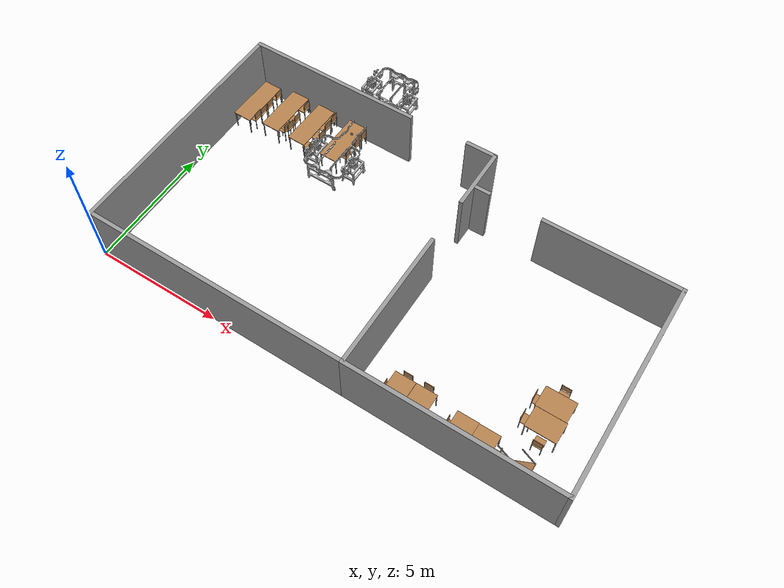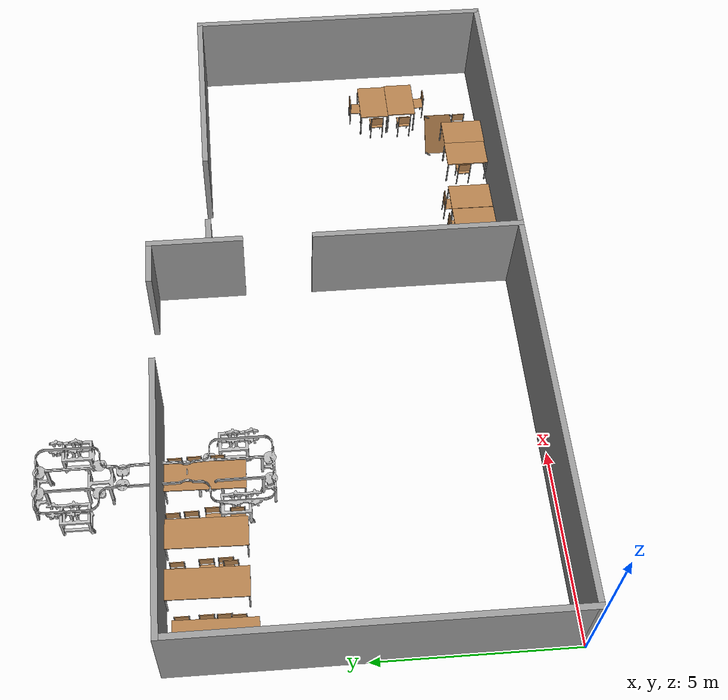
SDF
<sdf version="1.7">
 <world name="default">
  <light name="sun" type="directional">
   <pose>0 0 10 0 -0 0</pose>
   <diffuse>0.8 0.8 0.8 1</diffuse>
   <specular>0.2 0.2 0.2 1</specular>
   <attenuation>
    <range>1000</range>
    <constant>0.9</constant>
    <linear>0.01</linear>
    <quadratic>0.001</quadratic>
   </attenuation>
   <direction>-0.5 0.1 -0.9</direction>
   <spot><inner_angle>0</inner_angle><outer_angle>0</outer_angle><falloff>0</falloff></spot>
  </light>
  <model name="my_mesh">
   <pose>7.60509 9.58584 0 0 0 -1.5708</pose>
   <static>1</static>
   <link name="body">
    <visual name="visual"><geometry><mesh><uri>model://Cellule_lite.dae</uri></mesh></geometry></visual>
   </link>
  </model>
  <gravity>0 0 -9.8</gravity>
  <magnetic_field>6e-06 2.3e-05 -4.2e-05</magnetic_field>
  <atmosphere type="adiabatic"/>
  <physics name="default_physics" default="0" type="ode">
   <max_step_size>0.001</max_step_size>
   <real_time_factor>1</real_time_factor>
   <real_time_update_rate>1000</real_time_update_rate>
  </physics>
  <scene><ambient>0.4 0.4 0.4 1</ambient><background>0.7 0.7 0.7 1</background><shadows>1</shadows></scene>
  <spherical_coordinates>
   <surface_model>EARTH_WGS84</surface_model>
   <latitude_deg>0</latitude_deg>
   <longitude_deg>0</longitude_deg>
   <elevation>0</elevation>
   <heading_deg>0</heading_deg>
  </spherical_coordinates>
  <model name="table_mod_clone">
   <link name="link">
    <inertial>
     <mass>1</mass>
     <inertia><ixx>1</ixx><ixy>0</ixy><ixz>0</ixz><iyy>1</iyy><iyz>0</iyz><izz>1</izz></inertia>
    </inertial>
    <visual name="visual1">
     <pose>0 0 0.87 0 -0 0</pose>
     <geometry><box><size>1.15 0.8 0.03</size></box></geometry>
     <material>
      <script><uri>file://media/materials/scripts/gazebo.material</uri><name>Gazebo/Wood</name></script>
      <shader type="pixel"><normal_map>__default__</normal_map></shader>
      <ambient>1 1 1 1</ambient>
      <diffuse>1 1 1 1</diffuse>
      <specular>0.2 0.2 0.2 1</specular>
      <emissive>0 0 0 1</emissive>
     </material>
    </visual>
    <visual name="back_right_leg">
     <pose>-0.55 -0.38 0.5 0 -0 0</pose>
     <geometry><cylinder><radius>0.02</radius><length>0.75</length></cylinder></geometry>
     <material>
      <script><uri>file://media/materials/scripts/gazebo.material</uri><name>Gazebo/Grey</name></script>
      <shader type="pixel"><normal_map>__default__</normal_map></shader>
      <ambient>0.3 0.3 0.3 1</ambient>
      <diffuse>0.7 0.7 0.7 1</diffuse>
      <specular>0.01 0.01 0.01 1</specular>
      <emissive>0 0 0 1</emissive>
     </material>
    </visual>
    <visual name="front_right_leg">
     <pose>0.55 -0.38 0.5 0 -0 0</pose>
     <geometry><cylinder><radius>0.02</radius><length>0.75</length></cylinder></geometry>
     <material>
      <script><uri>file://media/materials/scripts/gazebo.material</uri><name>Gazebo/Grey</name></script>
      <shader type="pixel"><normal_map>__default__</normal_map></shader>
      <ambient>0.3 0.3 0.3 1</ambient>
      <diffuse>0.7 0.7 0.7 1</diffuse>
      <specular>0.01 0.01 0.01 1</specular>
      <emissive>0 0 0 1</emissive>
     </material>
    </visual>
    <visual name="back_left_leg">
     <pose>-0.55 0.38 0.5 0 -0 0</pose>
     <geometry><cylinder><radius>0.02</radius><length>0.75</length></cylinder></geometry>
     <material>
      <script><uri>file://media/materials/scripts/gazebo.material</uri><name>Gazebo/Grey</name></script>
      <shader type="pixel"><normal_map>__default__</normal_map></shader>
      <ambient>0.3 0.3 0.3 1</ambient>
      <diffuse>0.7 0.7 0.7 1</diffuse>
      <specular>0.01 0.01 0.01 1</specular>
      <emissive>0 0 0 1</emissive>
     </material>
    </visual>
    <visual name="front_left_leg">
     <pose>0.55 0.38 0.5 0 -0 0</pose>
     <geometry><cylinder><radius>0.02</radius><length>0.75</length></cylinder></geometry>
     <material>
      <script><uri>file://media/materials/scripts/gazebo.material</uri><name>Gazebo/Grey</name></script>
      <shader type="pixel"><normal_map>__default__</normal_map></shader>
      <ambient>0.3 0.3 0.3 1</ambient>
      <diffuse>0.7 0.7 0.7 1</diffuse>
      <specular>0.01 0.01 0.01 1</specular>
      <emissive>0 0 0 1</emissive>
     </material>
    </visual>
    <collision name="surface">
     <pose>0 0 0.87 0 -0 0</pose>
     <geometry><box><size>1.15 0.8 0.03</size></box></geometry>
     <surface>
      <friction>
       <ode><mu>0.6</mu><mu2>0.6</mu2><fdir1>0 0 0</fdir1><slip1>0</slip1><slip2>0</slip2></ode>
       <torsional>
        <coefficient>1</coefficient>
        <patch_radius>0</patch_radius>
        <surface_radius>0</surface_radius>
        <use_patch_radius>1</use_patch_radius>
        <ode><slip>0</slip></ode>
       </torsional>
      </friction>
      <bounce><restitution_coefficient>0</restitution_coefficient><threshold>1e+06</threshold></bounce>
      <contact>
       <collide_without_contact>0</collide_without_contact>
       <collide_without_contact_bitmask>1</collide_without_contact_bitmask>
       <collide_bitmask>1</collide_bitmask>
       <ode>
        <soft_cfm>0</soft_cfm>
        <soft_erp>0.2</soft_erp>
        <kp>1e+13</kp>
        <kd>1</kd>
        <max_vel>0.01</max_vel>
        <min_depth>0</min_depth>
       </ode>
       <bullet>
        <split_impulse>1</split_impulse>
        <split_impulse_penetration_threshold>-0.01</split_impulse_penetration_threshold>
        <soft_cfm>0</soft_cfm>
        <soft_erp>0.2</soft_erp>
        <kp>1e+13</kp>
        <kd>1</kd>
       </bullet>
      </contact>
     </surface>
    </collision>
    <collision name="back_right_leg">
     <pose>-0.55 -0.38 0.5 0 -0 0</pose>
     <geometry><cylinder><radius>0.02</radius><length>0.75</length></cylinder></geometry>
     <surface>
      <friction>
       <ode><mu>1</mu><mu2>1</mu2><fdir1>0 0 0</fdir1><slip1>0</slip1><slip2>0</slip2></ode>
       <torsional>
        <coefficient>1</coefficient>
        <patch_radius>0</patch_radius>
        <surface_radius>0</surface_radius>
        <use_patch_radius>1</use_patch_radius>
        <ode><slip>0</slip></ode>
       </torsional>
      </friction>
      <bounce><restitution_coefficient>0</restitution_coefficient><threshold>1e+06</threshold></bounce>
      <contact>
       <collide_without_contact>0</collide_without_contact>
       <collide_without_contact_bitmask>1</collide_without_contact_bitmask>
       <collide_bitmask>1</collide_bitmask>
       <ode>
        <soft_cfm>0</soft_cfm>
        <soft_erp>0.2</soft_erp>
        <kp>1e+13</kp>
        <kd>1</kd>
        <max_vel>0.01</max_vel>
        <min_depth>0</min_depth>
       </ode>
       <bullet>
        <split_impulse>1</split_impulse>
        <split_impulse_penetration_threshold>-0.01</split_impulse_penetration_threshold>
        <soft_cfm>0</soft_cfm>
        <soft_erp>0.2</soft_erp>
        <kp>1e+13</kp>
        <kd>1</kd>
       </bullet>
      </contact>
     </surface>
    </collision>
    <collision name="back_left_leg">
     <pose>-0.55 0.38 0.5 0 -0 0</pose>
     <geometry><cylinder><radius>0.02</radius><length>0.75</length></cylinder></geometry>
     <surface>
      <friction>
       <ode><mu>1</mu><mu2>1</mu2><fdir1>0 0 0</fdir1><slip1>0</slip1><slip2>0</slip2></ode>
       <torsional>
        <coefficient>1</coefficient>
        <patch_radius>0</patch_radius>
        <surface_radius>0</surface_radius>
        <use_patch_radius>1</use_patch_radius>
        <ode><slip>0</slip></ode>
       </torsional>
      </friction>
      <bounce><restitution_coefficient>0</restitution_coefficient><threshold>1e+06</threshold></bounce>
      <contact>
       <collide_without_contact>0</collide_without_contact>
       <collide_without_contact_bitmask>1</collide_without_contact_bitmask>
       <collide_bitmask>1</collide_bitmask>
       <ode>
        <soft_cfm>0</soft_cfm>
        <soft_erp>0.2</soft_erp>
        <kp>1e+13</kp>
        <kd>1</kd>
        <max_vel>0.01</max_vel>
        <min_depth>0</min_depth>
       </ode>
       <bullet>
        <split_impulse>1</split_impulse>
        <split_impulse_penetration_threshold>-0.01</split_impulse_penetration_threshold>
        <soft_cfm>0</soft_cfm>
        <soft_erp>0.2</soft_erp>
        <kp>1e+13</kp>
        <kd>1</kd>
       </bullet>
      </contact>
     </surface>
    </collision>
    <collision name="front_left_leg">
     <pose>0.55 0.38 0.5 0 -0 0</pose>
     <geometry><cylinder><radius>0.02</radius><length>0.75</length></cylinder></geometry>
     <surface>
      <friction>
       <ode><mu>1</mu><mu2>1</mu2><fdir1>0 0 0</fdir1><slip1>0</slip1><slip2>0</slip2></ode>
       <torsional>
        <coefficient>1</coefficient>
        <patch_radius>0</patch_radius>
        <surface_radius>0</surface_radius>
        <use_patch_radius>1</use_patch_radius>
        <ode><slip>0</slip></ode>
       </torsional>
      </friction>
      <bounce><restitution_coefficient>0</restitution_coefficient><threshold>1e+06</threshold></bounce>
      <contact>
       <collide_without_contact>0</collide_without_contact>
       <collide_without_contact_bitmask>1</collide_without_contact_bitmask>
       <collide_bitmask>1</collide_bitmask>
       <ode>
        <soft_cfm>0</soft_cfm>
        <soft_erp>0.2</soft_erp>
        <kp>1e+13</kp>
        <kd>1</kd>
        <max_vel>0.01</max_vel>
        <min_depth>0</min_depth>
       </ode>
       <bullet>
        <split_impulse>1</split_impulse>
        <split_impulse_penetration_threshold>-0.01</split_impulse_penetration_threshold>
        <soft_cfm>0</soft_cfm>
        <soft_erp>0.2</soft_erp>
        <kp>1e+13</kp>
        <kd>1</kd>
       </bullet>
      </contact>
     </surface>
    </collision>
    <collision name="front_right_leg">
     <pose>0.55 -0.38 0.5 0 -0 0</pose>
     <geometry><cylinder><radius>0.02</radius><length>0.75</length></cylinder></geometry>
     <surface>
      <friction>
       <ode><mu>1</mu><mu2>1</mu2><fdir1>0 0 0</fdir1><slip1>0</slip1><slip2>0</slip2></ode>
       <torsional>
        <coefficient>1</coefficient>
        <patch_radius>0</patch_radius>
        <surface_radius>0</surface_radius>
        <use_patch_radius>1</use_patch_radius>
        <ode><slip>0</slip></ode>
       </torsional>
      </friction>
      <bounce><restitution_coefficient>0</restitution_coefficient><threshold>1e+06</threshold></bounce>
      <contact>
       <collide_without_contact>0</collide_without_contact>
       <collide_without_contact_bitmask>1</collide_without_contact_bitmask>
       <collide_bitmask>1</collide_bitmask>
       <ode>
        <soft_cfm>0</soft_cfm>
        <soft_erp>0.2</soft_erp>
        <kp>1e+13</kp>
        <kd>1</kd>
        <max_vel>0.01</max_vel>
        <min_depth>0</min_depth>
       </ode>
       <bullet>
        <split_impulse>1</split_impulse>
        <split_impulse_penetration_threshold>-0.01</split_impulse_penetration_threshold>
        <soft_cfm>0</soft_cfm>
        <soft_erp>0.2</soft_erp>
        <kp>1e+13</kp>
        <kd>1</kd>
       </bullet>
      </contact>
     </surface>
    </collision>
   </link>
   <static>1</static>
   <pose>15.1421 0.746961 -0.134214 0 0 -1.5708</pose>
  </model>
  <model name="table_mod_clone_clone_1">
   <link name="link">
    <inertial>
     <mass>1</mass>
     <inertia><ixx>1</ixx><ixy>0</ixy><ixz>0</ixz><iyy>1</iyy><iyz>0</iyz><izz>1</izz></inertia>
    </inertial>
    <visual name="visual1">
     <pose>0 0 0.87 0 -0 0</pose>
     <geometry><box><size>1.15 0.8 0.03</size></box></geometry>
     <material>
      <script><uri>file://media/materials/scripts/gazebo.material</uri><name>Gazebo/Wood</name></script>
      <shader type="pixel"><normal_map>__default__</normal_map></shader>
      <ambient>1 1 1 1</ambient>
      <diffuse>1 1 1 1</diffuse>
      <specular>0.2 0.2 0.2 1</specular>
      <emissive>0 0 0 1</emissive>
     </material>
    </visual>
    <visual name="back_right_leg">
     <pose>-0.55 -0.38 0.5 0 -0 0</pose>
     <geometry><cylinder><radius>0.02</radius><length>0.75</length></cylinder></geometry>
     <material>
      <script><uri>file://media/materials/scripts/gazebo.material</uri><name>Gazebo/Grey</name></script>
      <shader type="pixel"><normal_map>__default__</normal_map></shader>
      <ambient>0.3 0.3 0.3 1</ambient>
      <diffuse>0.7 0.7 0.7 1</diffuse>
      <specular>0.01 0.01 0.01 1</specular>
      <emissive>0 0 0 1</emissive>
     </material>
    </visual>
    <visual name="front_right_leg">
     <pose>0.55 -0.38 0.5 0 -0 0</pose>
     <geometry><cylinder><radius>0.02</radius><length>0.75</length></cylinder></geometry>
     <material>
      <script><uri>file://media/materials/scripts/gazebo.material</uri><name>Gazebo/Grey</name></script>
      <shader type="pixel"><normal_map>__default__</normal_map></shader>
      <ambient>0.3 0.3 0.3 1</ambient>
      <diffuse>0.7 0.7 0.7 1</diffuse>
      <specular>0.01 0.01 0.01 1</specular>
      <emissive>0 0 0 1</emissive>
     </material>
    </visual>
    <visual name="back_left_leg">
     <pose>-0.55 0.38 0.5 0 -0 0</pose>
     <geometry><cylinder><radius>0.02</radius><length>0.75</length></cylinder></geometry>
     <material>
      <script><uri>file://media/materials/scripts/gazebo.material</uri><name>Gazebo/Grey</name></script>
      <shader type="pixel"><normal_map>__default__</normal_map></shader>
      <ambient>0.3 0.3 0.3 1</ambient>
      <diffuse>0.7 0.7 0.7 1</diffuse>
      <specular>0.01 0.01 0.01 1</specular>
      <emissive>0 0 0 1</emissive>
     </material>
    </visual>
    <visual name="front_left_leg">
     <pose>0.55 0.38 0.5 0 -0 0</pose>
     <geometry><cylinder><radius>0.02</radius><length>0.75</length></cylinder></geometry>
     <material>
      <script><uri>file://media/materials/scripts/gazebo.material</uri><name>Gazebo/Grey</name></script>
      <shader type="pixel"><normal_map>__default__</normal_map></shader>
      <ambient>0.3 0.3 0.3 1</ambient>
      <diffuse>0.7 0.7 0.7 1</diffuse>
      <specular>0.01 0.01 0.01 1</specular>
      <emissive>0 0 0 1</emissive>
     </material>
    </visual>
    <collision name="surface">
     <pose>0 0 0.87 0 -0 0</pose>
     <geometry><box><size>1.15 0.8 0.03</size></box></geometry>
     <surface>
      <friction>
       <ode><mu>0.6</mu><mu2>0.6</mu2><fdir1>0 0 0</fdir1><slip1>0</slip1><slip2>0</slip2></ode>
       <torsional>
        <coefficient>1</coefficient>
        <patch_radius>0</patch_radius>
        <surface_radius>0</surface_radius>
        <use_patch_radius>1</use_patch_radius>
        <ode><slip>0</slip></ode>
       </torsional>
      </friction>
      <bounce><restitution_coefficient>0</restitution_coefficient><threshold>1e+06</threshold></bounce>
      <contact>
       <collide_without_contact>0</collide_without_contact>
       <collide_without_contact_bitmask>1</collide_without_contact_bitmask>
       <collide_bitmask>1</collide_bitmask>
       <ode>
        <soft_cfm>0</soft_cfm>
        <soft_erp>0.2</soft_erp>
        <kp>1e+13</kp>
        <kd>1</kd>
        <max_vel>0.01</max_vel>
        <min_depth>0</min_depth>
       </ode>
       <bullet>
        <split_impulse>1</split_impulse>
        <split_impulse_penetration_threshold>-0.01</split_impulse_penetration_threshold>
        <soft_cfm>0</soft_cfm>
        <soft_erp>0.2</soft_erp>
        <kp>1e+13</kp>
        <kd>1</kd>
       </bullet>
      </contact>
     </surface>
    </collision>
    <collision name="back_right_leg">
     <pose>-0.55 -0.38 0.5 0 -0 0</pose>
     <geometry><cylinder><radius>0.02</radius><length>0.75</length></cylinder></geometry>
     <surface>
      <friction>
       <ode><mu>1</mu><mu2>1</mu2><fdir1>0 0 0</fdir1><slip1>0</slip1><slip2>0</slip2></ode>
       <torsional>
        <coefficient>1</coefficient>
        <patch_radius>0</patch_radius>
        <surface_radius>0</surface_radius>
        <use_patch_radius>1</use_patch_radius>
        <ode><slip>0</slip></ode>
       </torsional>
      </friction>
      <bounce><restitution_coefficient>0</restitution_coefficient><threshold>1e+06</threshold></bounce>
      <contact>
       <collide_without_contact>0</collide_without_contact>
       <collide_without_contact_bitmask>1</collide_without_contact_bitmask>
       <collide_bitmask>1</collide_bitmask>
       <ode>
        <soft_cfm>0</soft_cfm>
        <soft_erp>0.2</soft_erp>
        <kp>1e+13</kp>
        <kd>1</kd>
        <max_vel>0.01</max_vel>
        <min_depth>0</min_depth>
       </ode>
       <bullet>
        <split_impulse>1</split_impulse>
        <split_impulse_penetration_threshold>-0.01</split_impulse_penetration_threshold>
        <soft_cfm>0</soft_cfm>
        <soft_erp>0.2</soft_erp>
        <kp>1e+13</kp>
        <kd>1</kd>
       </bullet>
      </contact>
     </surface>
    </collision>
    <collision name="back_left_leg">
     <pose>-0.55 0.38 0.5 0 -0 0</pose>
     <geometry><cylinder><radius>0.02</radius><length>0.75</length></cylinder></geometry>
     <surface>
      <friction>
       <ode><mu>1</mu><mu2>1</mu2><fdir1>0 0 0</fdir1><slip1>0</slip1><slip2>0</slip2></ode>
       <torsional>
        <coefficient>1</coefficient>
        <patch_radius>0</patch_radius>
        <surface_radius>0</surface_radius>
        <use_patch_radius>1</use_patch_radius>
        <ode><slip>0</slip></ode>
       </torsional>
      </friction>
      <bounce><restitution_coefficient>0</restitution_coefficient><threshold>1e+06</threshold></bounce>
      <contact>
       <collide_without_contact>0</collide_without_contact>
       <collide_without_contact_bitmask>1</collide_without_contact_bitmask>
       <collide_bitmask>1</collide_bitmask>
       <ode>
        <soft_cfm>0</soft_cfm>
        <soft_erp>0.2</soft_erp>
        <kp>1e+13</kp>
        <kd>1</kd>
        <max_vel>0.01</max_vel>
        <min_depth>0</min_depth>
       </ode>
       <bullet>
        <split_impulse>1</split_impulse>
        <split_impulse_penetration_threshold>-0.01</split_impulse_penetration_threshold>
        <soft_cfm>0</soft_cfm>
        <soft_erp>0.2</soft_erp>
        <kp>1e+13</kp>
        <kd>1</kd>
       </bullet>
      </contact>
     </surface>
    </collision>
    <collision name="front_left_leg">
     <pose>0.55 0.38 0.5 0 -0 0</pose>
     <geometry><cylinder><radius>0.02</radius><length>0.75</length></cylinder></geometry>
     <surface>
      <friction>
       <ode><mu>1</mu><mu2>1</mu2><fdir1>0 0 0</fdir1><slip1>0</slip1><slip2>0</slip2></ode>
       <torsional>
        <coefficient>1</coefficient>
        <patch_radius>0</patch_radius>
        <surface_radius>0</surface_radius>
        <use_patch_radius>1</use_patch_radius>
        <ode><slip>0</slip></ode>
       </torsional>
      </friction>
      <bounce><restitution_coefficient>0</restitution_coefficient><threshold>1e+06</threshold></bounce>
      <contact>
       <collide_without_contact>0</collide_without_contact>
       <collide_without_contact_bitmask>1</collide_without_contact_bitmask>
       <collide_bitmask>1</collide_bitmask>
       <ode>
        <soft_cfm>0</soft_cfm>
        <soft_erp>0.2</soft_erp>
        <kp>1e+13</kp>
        <kd>1</kd>
        <max_vel>0.01</max_vel>
        <min_depth>0</min_depth>
       </ode>
       <bullet>
        <split_impulse>1</split_impulse>
        <split_impulse_penetration_threshold>-0.01</split_impulse_penetration_threshold>
        <soft_cfm>0</soft_cfm>
        <soft_erp>0.2</soft_erp>
        <kp>1e+13</kp>
        <kd>1</kd>
       </bullet>
      </contact>
     </surface>
    </collision>
    <collision name="front_right_leg">
     <pose>0.55 -0.38 0.5 0 -0 0</pose>
     <geometry><cylinder><radius>0.02</radius><length>0.75</length></cylinder></geometry>
     <surface>
      <friction>
       <ode><mu>1</mu><mu2>1</mu2><fdir1>0 0 0</fdir1><slip1>0</slip1><slip2>0</slip2></ode>
       <torsional>
        <coefficient>1</coefficient>
        <patch_radius>0</patch_radius>
        <surface_radius>0</surface_radius>
        <use_patch_radius>1</use_patch_radius>
        <ode><slip>0</slip></ode>
       </torsional>
      </friction>
      <bounce><restitution_coefficient>0</restitution_coefficient><threshold>1e+06</threshold></bounce>
      <contact>
       <collide_without_contact>0</collide_without_contact>
       <collide_without_contact_bitmask>1</collide_without_contact_bitmask>
       <collide_bitmask>1</collide_bitmask>
       <ode>
        <soft_cfm>0</soft_cfm>
        <soft_erp>0.2</soft_erp>
        <kp>1e+13</kp>
        <kd>1</kd>
        <max_vel>0.01</max_vel>
        <min_depth>0</min_depth>
       </ode>
       <bullet>
        <split_impulse>1</split_impulse>
        <split_impulse_penetration_threshold>-0.01</split_impulse_penetration_threshold>
        <soft_cfm>0</soft_cfm>
        <soft_erp>0.2</soft_erp>
        <kp>1e+13</kp>
        <kd>1</kd>
       </bullet>
      </contact>
     </surface>
    </collision>
   </link>
   <static>1</static>
   <pose>14.3468 0.761349 -0.134214 0 0 -1.5708</pose>
  </model>
  <model name="table_mod_clone_0_clone_0_clone">
   <link name="link">
    <inertial>
     <mass>1</mass>
     <inertia><ixx>1</ixx><ixy>0</ixy><ixz>0</ixz><iyy>1</iyy><iyz>0</iyz><izz>1</izz></inertia>
    </inertial>
    <visual name="visual1">
     <pose>0 0 0.87 0 -0 0</pose>
     <geometry><box><size>1.15 0.8 0.03</size></box></geometry>
     <material>
      <script><uri>file://media/materials/scripts/gazebo.material</uri><name>Gazebo/Wood</name></script>
      <shader type="pixel"><normal_map>__default__</normal_map></shader>
      <ambient>1 1 1 1</ambient>
      <diffuse>1 1 1 1</diffuse>
      <specular>0.2 0.2 0.2 1</specular>
      <emissive>0 0 0 1</emissive>
     </material>
    </visual>
    <visual name="back_right_leg">
     <pose>-0.55 -0.38 0.5 0 -0 0</pose>
     <geometry><cylinder><radius>0.02</radius><length>0.75</length></cylinder></geometry>
     <material>
      <script><uri>file://media/materials/scripts/gazebo.material</uri><name>Gazebo/Grey</name></script>
      <shader type="pixel"><normal_map>__default__</normal_map></shader>
      <ambient>0.3 0.3 0.3 1</ambient>
      <diffuse>0.7 0.7 0.7 1</diffuse>
      <specular>0.01 0.01 0.01 1</specular>
      <emissive>0 0 0 1</emissive>
     </material>
    </visual>
    <visual name="front_right_leg">
     <pose>0.55 -0.38 0.5 0 -0 0</pose>
     <geometry><cylinder><radius>0.02</radius><length>0.75</length></cylinder></geometry>
     <material>
      <script><uri>file://media/materials/scripts/gazebo.material</uri><name>Gazebo/Grey</name></script>
      <shader type="pixel"><normal_map>__default__</normal_map></shader>
      <ambient>0.3 0.3 0.3 1</ambient>
      <diffuse>0.7 0.7 0.7 1</diffuse>
      <specular>0.01 0.01 0.01 1</specular>
      <emissive>0 0 0 1</emissive>
     </material>
    </visual>
    <visual name="back_left_leg">
     <pose>-0.55 0.38 0.5 0 -0 0</pose>
     <geometry><cylinder><radius>0.02</radius><length>0.75</length></cylinder></geometry>
     <material>
      <script><uri>file://media/materials/scripts/gazebo.material</uri><name>Gazebo/Grey</name></script>
      <shader type="pixel"><normal_map>__default__</normal_map></shader>
      <ambient>0.3 0.3 0.3 1</ambient>
      <diffuse>0.7 0.7 0.7 1</diffuse>
      <specular>0.01 0.01 0.01 1</specular>
      <emissive>0 0 0 1</emissive>
     </material>
    </visual>
    <visual name="front_left_leg">
     <pose>0.55 0.38 0.5 0 -0 0</pose>
     <geometry><cylinder><radius>0.02</radius><length>0.75</length></cylinder></geometry>
     <material>
      <script><uri>file://media/materials/scripts/gazebo.material</uri><name>Gazebo/Grey</name></script>
      <shader type="pixel"><normal_map>__default__</normal_map></shader>
      <ambient>0.3 0.3 0.3 1</ambient>
      <diffuse>0.7 0.7 0.7 1</diffuse>
      <specular>0.01 0.01 0.01 1</specular>
      <emissive>0 0 0 1</emissive>
     </material>
    </visual>
    <collision name="surface">
     <pose>0 0 0.87 0 -0 0</pose>
     <geometry><box><size>1.15 0.8 0.03</size></box></geometry>
     <surface>
      <friction>
       <ode><mu>0.6</mu><mu2>0.6</mu2><fdir1>0 0 0</fdir1><slip1>0</slip1><slip2>0</slip2></ode>
       <torsional>
        <coefficient>1</coefficient>
        <patch_radius>0</patch_radius>
        <surface_radius>0</surface_radius>
        <use_patch_radius>1</use_patch_radius>
        <ode><slip>0</slip></ode>
       </torsional>
      </friction>
      <bounce><restitution_coefficient>0</restitution_coefficient><threshold>1e+06</threshold></bounce>
      <contact>
       <collide_without_contact>0</collide_without_contact>
       <collide_without_contact_bitmask>1</collide_without_contact_bitmask>
       <collide_bitmask>1</collide_bitmask>
       <ode>
        <soft_cfm>0</soft_cfm>
        <soft_erp>0.2</soft_erp>
        <kp>1e+13</kp>
        <kd>1</kd>
        <max_vel>0.01</max_vel>
        <min_depth>0</min_depth>
       </ode>
       <bullet>
        <split_impulse>1</split_impulse>
        <split_impulse_penetration_threshold>-0.01</split_impulse_penetration_threshold>
        <soft_cfm>0</soft_cfm>
        <soft_erp>0.2</soft_erp>
        <kp>1e+13</kp>
        <kd>1</kd>
       </bullet>
      </contact>
     </surface>
    </collision>
    <collision name="back_right_leg">
     <pose>-0.55 -0.38 0.5 0 -0 0</pose>
     <geometry><cylinder><radius>0.02</radius><length>0.75</length></cylinder></geometry>
     <surface>
      <friction>
       <ode><mu>1</mu><mu2>1</mu2><fdir1>0 0 0</fdir1><slip1>0</slip1><slip2>0</slip2></ode>
       <torsional>
        <coefficient>1</coefficient>
        <patch_radius>0</patch_radius>
        <surface_radius>0</surface_radius>
        <use_patch_radius>1</use_patch_radius>
        <ode><slip>0</slip></ode>
       </torsional>
      </friction>
      <bounce><restitution_coefficient>0</restitution_coefficient><threshold>1e+06</threshold></bounce>
      <contact>
       <collide_without_contact>0</collide_without_contact>
       <collide_without_contact_bitmask>1</collide_without_contact_bitmask>
       <collide_bitmask>1</collide_bitmask>
       <ode>
        <soft_cfm>0</soft_cfm>
        <soft_erp>0.2</soft_erp>
        <kp>1e+13</kp>
        <kd>1</kd>
        <max_vel>0.01</max_vel>
        <min_depth>0</min_depth>
       </ode>
       <bullet>
        <split_impulse>1</split_impulse>
        <split_impulse_penetration_threshold>-0.01</split_impulse_penetration_threshold>
        <soft_cfm>0</soft_cfm>
        <soft_erp>0.2</soft_erp>
        <kp>1e+13</kp>
        <kd>1</kd>
       </bullet>
      </contact>
     </surface>
    </collision>
    <collision name="back_left_leg">
     <pose>-0.55 0.38 0.5 0 -0 0</pose>
     <geometry><cylinder><radius>0.02</radius><length>0.75</length></cylinder></geometry>
     <surface>
      <friction>
       <ode><mu>1</mu><mu2>1</mu2><fdir1>0 0 0</fdir1><slip1>0</slip1><slip2>0</slip2></ode>
       <torsional>
        <coefficient>1</coefficient>
        <patch_radius>0</patch_radius>
        <surface_radius>0</surface_radius>
        <use_patch_radius>1</use_patch_radius>
        <ode><slip>0</slip></ode>
       </torsional>
      </friction>
      <bounce><restitution_coefficient>0</restitution_coefficient><threshold>1e+06</threshold></bounce>
      <contact>
       <collide_without_contact>0</collide_without_contact>
       <collide_without_contact_bitmask>1</collide_without_contact_bitmask>
       <collide_bitmask>1</collide_bitmask>
       <ode>
        <soft_cfm>0</soft_cfm>
        <soft_erp>0.2</soft_erp>
        <kp>1e+13</kp>
        <kd>1</kd>
        <max_vel>0.01</max_vel>
        <min_depth>0</min_depth>
       </ode>
       <bullet>
        <split_impulse>1</split_impulse>
        <split_impulse_penetration_threshold>-0.01</split_impulse_penetration_threshold>
        <soft_cfm>0</soft_cfm>
        <soft_erp>0.2</soft_erp>
        <kp>1e+13</kp>
        <kd>1</kd>
       </bullet>
      </contact>
     </surface>
    </collision>
    <collision name="front_left_leg">
     <pose>0.55 0.38 0.5 0 -0 0</pose>
     <geometry><cylinder><radius>0.02</radius><length>0.75</length></cylinder></geometry>
     <surface>
      <friction>
       <ode><mu>1</mu><mu2>1</mu2><fdir1>0 0 0</fdir1><slip1>0</slip1><slip2>0</slip2></ode>
       <torsional>
        <coefficient>1</coefficient>
        <patch_radius>0</patch_radius>
        <surface_radius>0</surface_radius>
        <use_patch_radius>1</use_patch_radius>
        <ode><slip>0</slip></ode>
       </torsional>
      </friction>
      <bounce><restitution_coefficient>0</restitution_coefficient><threshold>1e+06</threshold></bounce>
      <contact>
       <collide_without_contact>0</collide_without_contact>
       <collide_without_contact_bitmask>1</collide_without_contact_bitmask>
       <collide_bitmask>1</collide_bitmask>
       <ode>
        <soft_cfm>0</soft_cfm>
        <soft_erp>0.2</soft_erp>
        <kp>1e+13</kp>
        <kd>1</kd>
        <max_vel>0.01</max_vel>
        <min_depth>0</min_depth>
       </ode>
       <bullet>
        <split_impulse>1</split_impulse>
        <split_impulse_penetration_threshold>-0.01</split_impulse_penetration_threshold>
        <soft_cfm>0</soft_cfm>
        <soft_erp>0.2</soft_erp>
        <kp>1e+13</kp>
        <kd>1</kd>
       </bullet>
      </contact>
     </surface>
    </collision>
    <collision name="front_right_leg">
     <pose>0.55 -0.38 0.5 0 -0 0</pose>
     <geometry><cylinder><radius>0.02</radius><length>0.75</length></cylinder></geometry>
     <surface>
      <friction>
       <ode><mu>1</mu><mu2>1</mu2><fdir1>0 0 0</fdir1><slip1>0</slip1><slip2>0</slip2></ode>
       <torsional>
        <coefficient>1</coefficient>
        <patch_radius>0</patch_radius>
        <surface_radius>0</surface_radius>
        <use_patch_radius>1</use_patch_radius>
        <ode><slip>0</slip></ode>
       </torsional>
      </friction>
      <bounce><restitution_coefficient>0</restitution_coefficient><threshold>1e+06</threshold></bounce>
      <contact>
       <collide_without_contact>0</collide_without_contact>
       <collide_without_contact_bitmask>1</collide_without_contact_bitmask>
       <collide_bitmask>1</collide_bitmask>
       <ode>
        <soft_cfm>0</soft_cfm>
        <soft_erp>0.2</soft_erp>
        <kp>1e+13</kp>
        <kd>1</kd>
        <max_vel>0.01</max_vel>
        <min_depth>0</min_depth>
       </ode>
       <bullet>
        <split_impulse>1</split_impulse>
        <split_impulse_penetration_threshold>-0.01</split_impulse_penetration_threshold>
        <soft_cfm>0</soft_cfm>
        <soft_erp>0.2</soft_erp>
        <kp>1e+13</kp>
        <kd>1</kd>
       </bullet>
      </contact>
     </surface>
    </collision>
   </link>
   <static>1</static>
   <pose>15.7767 1.16575 -0.134214 3.14159 0.801019 3.14159</pose>
  </model>
  <model name="table_mod_clone_0_clone_0_clone_clone">
   <link name="link">
    <inertial>
     <mass>1</mass>
     <inertia><ixx>1</ixx><ixy>0</ixy><ixz>0</ixz><iyy>1</iyy><iyz>0</iyz><izz>1</izz></inertia>
    </inertial>
    <visual name="visual1">
     <pose>0 0 0.87 0 -0 0</pose>
     <geometry><box><size>1.15 0.8 0.03</size></box></geometry>
     <material>
      <script><uri>file://media/materials/scripts/gazebo.material</uri><name>Gazebo/Wood</name></script>
      <shader type="pixel"><normal_map>__default__</normal_map></shader>
      <ambient>1 1 1 1</ambient>
      <diffuse>1 1 1 1</diffuse>
      <specular>0.2 0.2 0.2 1</specular>
      <emissive>0 0 0 1</emissive>
     </material>
    </visual>
    <visual name="back_right_leg">
     <pose>-0.55 -0.38 0.5 0 -0 0</pose>
     <geometry><cylinder><radius>0.02</radius><length>0.75</length></cylinder></geometry>
     <material>
      <script><uri>file://media/materials/scripts/gazebo.material</uri><name>Gazebo/Grey</name></script>
      <shader type="pixel"><normal_map>__default__</normal_map></shader>
      <ambient>0.3 0.3 0.3 1</ambient>
      <diffuse>0.7 0.7 0.7 1</diffuse>
      <specular>0.01 0.01 0.01 1</specular>
      <emissive>0 0 0 1</emissive>
     </material>
    </visual>
    <visual name="front_right_leg">
     <pose>0.55 -0.38 0.5 0 -0 0</pose>
     <geometry><cylinder><radius>0.02</radius><length>0.75</length></cylinder></geometry>
     <material>
      <script><uri>file://media/materials/scripts/gazebo.material</uri><name>Gazebo/Grey</name></script>
      <shader type="pixel"><normal_map>__default__</normal_map></shader>
      <ambient>0.3 0.3 0.3 1</ambient>
      <diffuse>0.7 0.7 0.7 1</diffuse>
      <specular>0.01 0.01 0.01 1</specular>
      <emissive>0 0 0 1</emissive>
     </material>
    </visual>
    <visual name="back_left_leg">
     <pose>-0.55 0.38 0.5 0 -0 0</pose>
     <geometry><cylinder><radius>0.02</radius><length>0.75</length></cylinder></geometry>
     <material>
      <script><uri>file://media/materials/scripts/gazebo.material</uri><name>Gazebo/Grey</name></script>
      <shader type="pixel"><normal_map>__default__</normal_map></shader>
      <ambient>0.3 0.3 0.3 1</ambient>
      <diffuse>0.7 0.7 0.7 1</diffuse>
      <specular>0.01 0.01 0.01 1</specular>
      <emissive>0 0 0 1</emissive>
     </material>
    </visual>
    <visual name="front_left_leg">
     <pose>0.55 0.38 0.5 0 -0 0</pose>
     <geometry><cylinder><radius>0.02</radius><length>0.75</length></cylinder></geometry>
     <material>
      <script><uri>file://media/materials/scripts/gazebo.material</uri><name>Gazebo/Grey</name></script>
      <shader type="pixel"><normal_map>__default__</normal_map></shader>
      <ambient>0.3 0.3 0.3 1</ambient>
      <diffuse>0.7 0.7 0.7 1</diffuse>
      <specular>0.01 0.01 0.01 1</specular>
      <emissive>0 0 0 1</emissive>
     </material>
    </visual>
    <collision name="surface">
     <pose>0 0 0.87 0 -0 0</pose>
     <geometry><box><size>1.15 0.8 0.03</size></box></geometry>
     <surface>
      <friction>
       <ode><mu>0.6</mu><mu2>0.6</mu2><fdir1>0 0 0</fdir1><slip1>0</slip1><slip2>0</slip2></ode>
       <torsional>
        <coefficient>1</coefficient>
        <patch_radius>0</patch_radius>
        <surface_radius>0</surface_radius>
        <use_patch_radius>1</use_patch_radius>
        <ode><slip>0</slip></ode>
       </torsional>
      </friction>
      <bounce><restitution_coefficient>0</restitution_coefficient><threshold>1e+06</threshold></bounce>
      <contact>
       <collide_without_contact>0</collide_without_contact>
       <collide_without_contact_bitmask>1</collide_without_contact_bitmask>
       <collide_bitmask>1</collide_bitmask>
       <ode>
        <soft_cfm>0</soft_cfm>
        <soft_erp>0.2</soft_erp>
        <kp>1e+13</kp>
        <kd>1</kd>
        <max_vel>0.01</max_vel>
        <min_depth>0</min_depth>
       </ode>
       <bullet>
        <split_impulse>1</split_impulse>
        <split_impulse_penetration_threshold>-0.01</split_impulse_penetration_threshold>
        <soft_cfm>0</soft_cfm>
        <soft_erp>0.2</soft_erp>
        <kp>1e+13</kp>
        <kd>1</kd>
       </bullet>
      </contact>
     </surface>
    </collision>
    <collision name="back_right_leg">
     <pose>-0.55 -0.38 0.5 0 -0 0</pose>
     <geometry><cylinder><radius>0.02</radius><length>0.75</length></cylinder></geometry>
     <surface>
      <friction>
       <ode><mu>1</mu><mu2>1</mu2><fdir1>0 0 0</fdir1><slip1>0</slip1><slip2>0</slip2></ode>
       <torsional>
        <coefficient>1</coefficient>
        <patch_radius>0</patch_radius>
        <surface_radius>0</surface_radius>
        <use_patch_radius>1</use_patch_radius>
        <ode><slip>0</slip></ode>
       </torsional>
      </friction>
      <bounce><restitution_coefficient>0</restitution_coefficient><threshold>1e+06</threshold></bounce>
      <contact>
       <collide_without_contact>0</collide_without_contact>
       <collide_without_contact_bitmask>1</collide_without_contact_bitmask>
       <collide_bitmask>1</collide_bitmask>
       <ode>
        <soft_cfm>0</soft_cfm>
        <soft_erp>0.2</soft_erp>
        <kp>1e+13</kp>
        <kd>1</kd>
        <max_vel>0.01</max_vel>
        <min_depth>0</min_depth>
       </ode>
       <bullet>
        <split_impulse>1</split_impulse>
        <split_impulse_penetration_threshold>-0.01</split_impulse_penetration_threshold>
        <soft_cfm>0</soft_cfm>
        <soft_erp>0.2</soft_erp>
        <kp>1e+13</kp>
        <kd>1</kd>
       </bullet>
      </contact>
     </surface>
    </collision>
    <collision name="back_left_leg">
     <pose>-0.55 0.38 0.5 0 -0 0</pose>
     <geometry><cylinder><radius>0.02</radius><length>0.75</length></cylinder></geometry>
     <surface>
      <friction>
       <ode><mu>1</mu><mu2>1</mu2><fdir1>0 0 0</fdir1><slip1>0</slip1><slip2>0</slip2></ode>
       <torsional>
        <coefficient>1</coefficient>
        <patch_radius>0</patch_radius>
        <surface_radius>0</surface_radius>
        <use_patch_radius>1</use_patch_radius>
        <ode><slip>0</slip></ode>
       </torsional>
      </friction>
      <bounce><restitution_coefficient>0</restitution_coefficient><threshold>1e+06</threshold></bounce>
      <contact>
       <collide_without_contact>0</collide_without_contact>
       <collide_without_contact_bitmask>1</collide_without_contact_bitmask>
       <collide_bitmask>1</collide_bitmask>
       <ode>
        <soft_cfm>0</soft_cfm>
        <soft_erp>0.2</soft_erp>
        <kp>1e+13</kp>
        <kd>1</kd>
        <max_vel>0.01</max_vel>
        <min_depth>0</min_depth>
       </ode>
       <bullet>
        <split_impulse>1</split_impulse>
        <split_impulse_penetration_threshold>-0.01</split_impulse_penetration_threshold>
        <soft_cfm>0</soft_cfm>
        <soft_erp>0.2</soft_erp>
        <kp>1e+13</kp>
        <kd>1</kd>
       </bullet>
      </contact>
     </surface>
    </collision>
    <collision name="front_left_leg">
     <pose>0.55 0.38 0.5 0 -0 0</pose>
     <geometry><cylinder><radius>0.02</radius><length>0.75</length></cylinder></geometry>
     <surface>
      <friction>
       <ode><mu>1</mu><mu2>1</mu2><fdir1>0 0 0</fdir1><slip1>0</slip1><slip2>0</slip2></ode>
       <torsional>
        <coefficient>1</coefficient>
        <patch_radius>0</patch_radius>
        <surface_radius>0</surface_radius>
        <use_patch_radius>1</use_patch_radius>
        <ode><slip>0</slip></ode>
       </torsional>
      </friction>
      <bounce><restitution_coefficient>0</restitution_coefficient><threshold>1e+06</threshold></bounce>
      <contact>
       <collide_without_contact>0</collide_without_contact>
       <collide_without_contact_bitmask>1</collide_without_contact_bitmask>
       <collide_bitmask>1</collide_bitmask>
       <ode>
        <soft_cfm>0</soft_cfm>
        <soft_erp>0.2</soft_erp>
        <kp>1e+13</kp>
        <kd>1</kd>
        <max_vel>0.01</max_vel>
        <min_depth>0</min_depth>
       </ode>
       <bullet>
        <split_impulse>1</split_impulse>
        <split_impulse_penetration_threshold>-0.01</split_impulse_penetration_threshold>
        <soft_cfm>0</soft_cfm>
        <soft_erp>0.2</soft_erp>
        <kp>1e+13</kp>
        <kd>1</kd>
       </bullet>
      </contact>
     </surface>
    </collision>
    <collision name="front_right_leg">
     <pose>0.55 -0.38 0.5 0 -0 0</pose>
     <geometry><cylinder><radius>0.02</radius><length>0.75</length></cylinder></geometry>
     <surface>
      <friction>
       <ode><mu>1</mu><mu2>1</mu2><fdir1>0 0 0</fdir1><slip1>0</slip1><slip2>0</slip2></ode>
       <torsional>
        <coefficient>1</coefficient>
        <patch_radius>0</patch_radius>
        <surface_radius>0</surface_radius>
        <use_patch_radius>1</use_patch_radius>
        <ode><slip>0</slip></ode>
       </torsional>
      </friction>
      <bounce><restitution_coefficient>0</restitution_coefficient><threshold>1e+06</threshold></bounce>
      <contact>
       <collide_without_contact>0</collide_without_contact>
       <collide_without_contact_bitmask>1</collide_without_contact_bitmask>
       <collide_bitmask>1</collide_bitmask>
       <ode>
        <soft_cfm>0</soft_cfm>
        <soft_erp>0.2</soft_erp>
        <kp>1e+13</kp>
        <kd>1</kd>
        <max_vel>0.01</max_vel>
        <min_depth>0</min_depth>
       </ode>
       <bullet>
        <split_impulse>1</split_impulse>
        <split_impulse_penetration_threshold>-0.01</split_impulse_penetration_threshold>
        <soft_cfm>0</soft_cfm>
        <soft_erp>0.2</soft_erp>
        <kp>1e+13</kp>
        <kd>1</kd>
       </bullet>
      </contact>
     </surface>
    </collision>
   </link>
   <static>1</static>
   <pose>16.523 2.43427 -0.134214 0 0 -4e-06</pose>
  </model>
  <model name="table_mod_clone_0_clone_0_clone_clone_clone">
   <link name="link">
    <inertial>
     <mass>1</mass>
     <inertia><ixx>1</ixx><ixy>0</ixy><ixz>0</ixz><iyy>1</iyy><iyz>0</iyz><izz>1</izz></inertia>
    </inertial>
    <visual name="visual1">
     <pose>0 0 0.87 0 -0 0</pose>
     <geometry><box><size>1.15 0.8 0.03</size></box></geometry>
     <material>
      <script><uri>file://media/materials/scripts/gazebo.material</uri><name>Gazebo/Wood</name></script>
      <shader type="pixel"><normal_map>__default__</normal_map></shader>
      <ambient>1 1 1 1</ambient>
      <diffuse>1 1 1 1</diffuse>
      <specular>0.2 0.2 0.2 1</specular>
      <emissive>0 0 0 1</emissive>
     </material>
    </visual>
    <visual name="back_right_leg">
     <pose>-0.55 -0.38 0.5 0 -0 0</pose>
     <geometry><cylinder><radius>0.02</radius><length>0.75</length></cylinder></geometry>
     <material>
      <script><uri>file://media/materials/scripts/gazebo.material</uri><name>Gazebo/Grey</name></script>
      <shader type="pixel"><normal_map>__default__</normal_map></shader>
      <ambient>0.3 0.3 0.3 1</ambient>
      <diffuse>0.7 0.7 0.7 1</diffuse>
      <specular>0.01 0.01 0.01 1</specular>
      <emissive>0 0 0 1</emissive>
     </material>
    </visual>
    <visual name="front_right_leg">
     <pose>0.55 -0.38 0.5 0 -0 0</pose>
     <geometry><cylinder><radius>0.02</radius><length>0.75</length></cylinder></geometry>
     <material>
      <script><uri>file://media/materials/scripts/gazebo.material</uri><name>Gazebo/Grey</name></script>
      <shader type="pixel"><normal_map>__default__</normal_map></shader>
      <ambient>0.3 0.3 0.3 1</ambient>
      <diffuse>0.7 0.7 0.7 1</diffuse>
      <specular>0.01 0.01 0.01 1</specular>
      <emissive>0 0 0 1</emissive>
     </material>
    </visual>
    <visual name="back_left_leg">
     <pose>-0.55 0.38 0.5 0 -0 0</pose>
     <geometry><cylinder><radius>0.02</radius><length>0.75</length></cylinder></geometry>
     <material>
      <script><uri>file://media/materials/scripts/gazebo.material</uri><name>Gazebo/Grey</name></script>
      <shader type="pixel"><normal_map>__default__</normal_map></shader>
      <ambient>0.3 0.3 0.3 1</ambient>
      <diffuse>0.7 0.7 0.7 1</diffuse>
      <specular>0.01 0.01 0.01 1</specular>
      <emissive>0 0 0 1</emissive>
     </material>
    </visual>
    <visual name="front_left_leg">
     <pose>0.55 0.38 0.5 0 -0 0</pose>
     <geometry><cylinder><radius>0.02</radius><length>0.75</length></cylinder></geometry>
     <material>
      <script><uri>file://media/materials/scripts/gazebo.material</uri><name>Gazebo/Grey</name></script>
      <shader type="pixel"><normal_map>__default__</normal_map></shader>
      <ambient>0.3 0.3 0.3 1</ambient>
      <diffuse>0.7 0.7 0.7 1</diffuse>
      <specular>0.01 0.01 0.01 1</specular>
      <emissive>0 0 0 1</emissive>
     </material>
    </visual>
    <collision name="surface">
     <pose>0 0 0.87 0 -0 0</pose>
     <geometry><box><size>1.15 0.8 0.03</size></box></geometry>
     <surface>
      <friction>
       <ode><mu>0.6</mu><mu2>0.6</mu2><fdir1>0 0 0</fdir1><slip1>0</slip1><slip2>0</slip2></ode>
       <torsional>
        <coefficient>1</coefficient>
        <patch_radius>0</patch_radius>
        <surface_radius>0</surface_radius>
        <use_patch_radius>1</use_patch_radius>
        <ode><slip>0</slip></ode>
       </torsional>
      </friction>
      <bounce><restitution_coefficient>0</restitution_coefficient><threshold>1e+06</threshold></bounce>
      <contact>
       <collide_without_contact>0</collide_without_contact>
       <collide_without_contact_bitmask>1</collide_without_contact_bitmask>
       <collide_bitmask>1</collide_bitmask>
       <ode>
        <soft_cfm>0</soft_cfm>
        <soft_erp>0.2</soft_erp>
        <kp>1e+13</kp>
        <kd>1</kd>
        <max_vel>0.01</max_vel>
        <min_depth>0</min_depth>
       </ode>
       <bullet>
        <split_impulse>1</split_impulse>
        <split_impulse_penetration_threshold>-0.01</split_impulse_penetration_threshold>
        <soft_cfm>0</soft_cfm>
        <soft_erp>0.2</soft_erp>
        <kp>1e+13</kp>
        <kd>1</kd>
       </bullet>
      </contact>
     </surface>
    </collision>
    <collision name="back_right_leg">
     <pose>-0.55 -0.38 0.5 0 -0 0</pose>
     <geometry><cylinder><radius>0.02</radius><length>0.75</length></cylinder></geometry>
     <surface>
      <friction>
       <ode><mu>1</mu><mu2>1</mu2><fdir1>0 0 0</fdir1><slip1>0</slip1><slip2>0</slip2></ode>
       <torsional>
        <coefficient>1</coefficient>
        <patch_radius>0</patch_radius>
        <surface_radius>0</surface_radius>
        <use_patch_radius>1</use_patch_radius>
        <ode><slip>0</slip></ode>
       </torsional>
      </friction>
      <bounce><restitution_coefficient>0</restitution_coefficient><threshold>1e+06</threshold></bounce>
      <contact>
       <collide_without_contact>0</collide_without_contact>
       <collide_without_contact_bitmask>1</collide_without_contact_bitmask>
       <collide_bitmask>1</collide_bitmask>
       <ode>
        <soft_cfm>0</soft_cfm>
        <soft_erp>0.2</soft_erp>
        <kp>1e+13</kp>
        <kd>1</kd>
        <max_vel>0.01</max_vel>
        <min_depth>0</min_depth>
       </ode>
       <bullet>
        <split_impulse>1</split_impulse>
        <split_impulse_penetration_threshold>-0.01</split_impulse_penetration_threshold>
        <soft_cfm>0</soft_cfm>
        <soft_erp>0.2</soft_erp>
        <kp>1e+13</kp>
        <kd>1</kd>
       </bullet>
      </contact>
     </surface>
    </collision>
    <collision name="back_left_leg">
     <pose>-0.55 0.38 0.5 0 -0 0</pose>
     <geometry><cylinder><radius>0.02</radius><length>0.75</length></cylinder></geometry>
     <surface>
      <friction>
       <ode><mu>1</mu><mu2>1</mu2><fdir1>0 0 0</fdir1><slip1>0</slip1><slip2>0</slip2></ode>
       <torsional>
        <coefficient>1</coefficient>
        <patch_radius>0</patch_radius>
        <surface_radius>0</surface_radius>
        <use_patch_radius>1</use_patch_radius>
        <ode><slip>0</slip></ode>
       </torsional>
      </friction>
      <bounce><restitution_coefficient>0</restitution_coefficient><threshold>1e+06</threshold></bounce>
      <contact>
       <collide_without_contact>0</collide_without_contact>
       <collide_without_contact_bitmask>1</collide_without_contact_bitmask>
       <collide_bitmask>1</collide_bitmask>
       <ode>
        <soft_cfm>0</soft_cfm>
        <soft_erp>0.2</soft_erp>
        <kp>1e+13</kp>
        <kd>1</kd>
        <max_vel>0.01</max_vel>
        <min_depth>0</min_depth>
       </ode>
       <bullet>
        <split_impulse>1</split_impulse>
        <split_impulse_penetration_threshold>-0.01</split_impulse_penetration_threshold>
        <soft_cfm>0</soft_cfm>
        <soft_erp>0.2</soft_erp>
        <kp>1e+13</kp>
        <kd>1</kd>
       </bullet>
      </contact>
     </surface>
    </collision>
    <collision name="front_left_leg">
     <pose>0.55 0.38 0.5 0 -0 0</pose>
     <geometry><cylinder><radius>0.02</radius><length>0.75</length></cylinder></geometry>
     <surface>
      <friction>
       <ode><mu>1</mu><mu2>1</mu2><fdir1>0 0 0</fdir1><slip1>0</slip1><slip2>0</slip2></ode>
       <torsional>
        <coefficient>1</coefficient>
        <patch_radius>0</patch_radius>
        <surface_radius>0</surface_radius>
        <use_patch_radius>1</use_patch_radius>
        <ode><slip>0</slip></ode>
       </torsional>
      </friction>
      <bounce><restitution_coefficient>0</restitution_coefficient><threshold>1e+06</threshold></bounce>
      <contact>
       <collide_without_contact>0</collide_without_contact>
       <collide_without_contact_bitmask>1</collide_without_contact_bitmask>
       <collide_bitmask>1</collide_bitmask>
       <ode>
        <soft_cfm>0</soft_cfm>
        <soft_erp>0.2</soft_erp>
        <kp>1e+13</kp>
        <kd>1</kd>
        <max_vel>0.01</max_vel>
        <min_depth>0</min_depth>
       </ode>
       <bullet>
        <split_impulse>1</split_impulse>
        <split_impulse_penetration_threshold>-0.01</split_impulse_penetration_threshold>
        <soft_cfm>0</soft_cfm>
        <soft_erp>0.2</soft_erp>
        <kp>1e+13</kp>
        <kd>1</kd>
       </bullet>
      </contact>
     </surface>
    </collision>
    <collision name="front_right_leg">
     <pose>0.55 -0.38 0.5 0 -0 0</pose>
     <geometry><cylinder><radius>0.02</radius><length>0.75</length></cylinder></geometry>
     <surface>
      <friction>
       <ode><mu>1</mu><mu2>1</mu2><fdir1>0 0 0</fdir1><slip1>0</slip1><slip2>0</slip2></ode>
       <torsional>
        <coefficient>1</coefficient>
        <patch_radius>0</patch_radius>
        <surface_radius>0</surface_radius>
        <use_patch_radius>1</use_patch_radius>
        <ode><slip>0</slip></ode>
       </torsional>
      </friction>
      <bounce><restitution_coefficient>0</restitution_coefficient><threshold>1e+06</threshold></bounce>
      <contact>
       <collide_without_contact>0</collide_without_contact>
       <collide_without_contact_bitmask>1</collide_without_contact_bitmask>
       <collide_bitmask>1</collide_bitmask>
       <ode>
        <soft_cfm>0</soft_cfm>
        <soft_erp>0.2</soft_erp>
        <kp>1e+13</kp>
        <kd>1</kd>
        <max_vel>0.01</max_vel>
        <min_depth>0</min_depth>
       </ode>
       <bullet>
        <split_impulse>1</split_impulse>
        <split_impulse_penetration_threshold>-0.01</split_impulse_penetration_threshold>
        <soft_cfm>0</soft_cfm>
        <soft_erp>0.2</soft_erp>
        <kp>1e+13</kp>
        <kd>1</kd>
       </bullet>
      </contact>
     </surface>
    </collision>
   </link>
   <static>1</static>
   <pose>16.4842 3.23549 -0.134214 0 0 -4e-06</pose>
  </model>
  <model name="table_mod_clone_clone_1_clone">
   <link name="link">
    <inertial>
     <mass>1</mass>
     <inertia><ixx>1</ixx><ixy>0</ixy><ixz>0</ixz><iyy>1</iyy><iyz>0</iyz><izz>1</izz></inertia>
    </inertial>
    <visual name="visual1">
     <pose>0 0 0.87 0 -0 0</pose>
     <geometry><box><size>1.15 0.8 0.03</size></box></geometry>
     <material>
      <script><uri>file://media/materials/scripts/gazebo.material</uri><name>Gazebo/Wood</name></script>
      <shader type="pixel"><normal_map>__default__</normal_map></shader>
      <ambient>1 1 1 1</ambient>
      <diffuse>1 1 1 1</diffuse>
      <specular>0.2 0.2 0.2 1</specular>
      <emissive>0 0 0 1</emissive>
     </material>
    </visual>
    <visual name="back_right_leg">
     <pose>-0.55 -0.38 0.5 0 -0 0</pose>
     <geometry><cylinder><radius>0.02</radius><length>0.75</length></cylinder></geometry>
     <material>
      <script><uri>file://media/materials/scripts/gazebo.material</uri><name>Gazebo/Grey</name></script>
      <shader type="pixel"><normal_map>__default__</normal_map></shader>
      <ambient>0.3 0.3 0.3 1</ambient>
      <diffuse>0.7 0.7 0.7 1</diffuse>
      <specular>0.01 0.01 0.01 1</specular>
      <emissive>0 0 0 1</emissive>
     </material>
    </visual>
    <visual name="front_right_leg">
     <pose>0.55 -0.38 0.5 0 -0 0</pose>
     <geometry><cylinder><radius>0.02</radius><length>0.75</length></cylinder></geometry>
     <material>
      <script><uri>file://media/materials/scripts/gazebo.material</uri><name>Gazebo/Grey</name></script>
      <shader type="pixel"><normal_map>__default__</normal_map></shader>
      <ambient>0.3 0.3 0.3 1</ambient>
      <diffuse>0.7 0.7 0.7 1</diffuse>
      <specular>0.01 0.01 0.01 1</specular>
      <emissive>0 0 0 1</emissive>
     </material>
    </visual>
    <visual name="back_left_leg">
     <pose>-0.55 0.38 0.5 0 -0 0</pose>
     <geometry><cylinder><radius>0.02</radius><length>0.75</length></cylinder></geometry>
     <material>
      <script><uri>file://media/materials/scripts/gazebo.material</uri><name>Gazebo/Grey</name></script>
      <shader type="pixel"><normal_map>__default__</normal_map></shader>
      <ambient>0.3 0.3 0.3 1</ambient>
      <diffuse>0.7 0.7 0.7 1</diffuse>
      <specular>0.01 0.01 0.01 1</specular>
      <emissive>0 0 0 1</emissive>
     </material>
    </visual>
    <visual name="front_left_leg">
     <pose>0.55 0.38 0.5 0 -0 0</pose>
     <geometry><cylinder><radius>0.02</radius><length>0.75</length></cylinder></geometry>
     <material>
      <script><uri>file://media/materials/scripts/gazebo.material</uri><name>Gazebo/Grey</name></script>
      <shader type="pixel"><normal_map>__default__</normal_map></shader>
      <ambient>0.3 0.3 0.3 1</ambient>
      <diffuse>0.7 0.7 0.7 1</diffuse>
      <specular>0.01 0.01 0.01 1</specular>
      <emissive>0 0 0 1</emissive>
     </material>
    </visual>
    <collision name="surface">
     <pose>0 0 0.87 0 -0 0</pose>
     <geometry><box><size>1.15 0.8 0.03</size></box></geometry>
     <surface>
      <friction>
       <ode><mu>0.6</mu><mu2>0.6</mu2><fdir1>0 0 0</fdir1><slip1>0</slip1><slip2>0</slip2></ode>
       <torsional>
        <coefficient>1</coefficient>
        <patch_radius>0</patch_radius>
        <surface_radius>0</surface_radius>
        <use_patch_radius>1</use_patch_radius>
        <ode><slip>0</slip></ode>
       </torsional>
      </friction>
      <bounce><restitution_coefficient>0</restitution_coefficient><threshold>1e+06</threshold></bounce>
      <contact>
       <collide_without_contact>0</collide_without_contact>
       <collide_without_contact_bitmask>1</collide_without_contact_bitmask>
       <collide_bitmask>1</collide_bitmask>
       <ode>
        <soft_cfm>0</soft_cfm>
        <soft_erp>0.2</soft_erp>
        <kp>1e+13</kp>
        <kd>1</kd>
        <max_vel>0.01</max_vel>
        <min_depth>0</min_depth>
       </ode>
       <bullet>
        <split_impulse>1</split_impulse>
        <split_impulse_penetration_threshold>-0.01</split_impulse_penetration_threshold>
        <soft_cfm>0</soft_cfm>
        <soft_erp>0.2</soft_erp>
        <kp>1e+13</kp>
        <kd>1</kd>
       </bullet>
      </contact>
     </surface>
    </collision>
    <collision name="back_right_leg">
     <pose>-0.55 -0.38 0.5 0 -0 0</pose>
     <geometry><cylinder><radius>0.02</radius><length>0.75</length></cylinder></geometry>
     <surface>
      <friction>
       <ode><mu>1</mu><mu2>1</mu2><fdir1>0 0 0</fdir1><slip1>0</slip1><slip2>0</slip2></ode>
       <torsional>
        <coefficient>1</coefficient>
        <patch_radius>0</patch_radius>
        <surface_radius>0</surface_radius>
        <use_patch_radius>1</use_patch_radius>
        <ode><slip>0</slip></ode>
       </torsional>
      </friction>
      <bounce><restitution_coefficient>0</restitution_coefficient><threshold>1e+06</threshold></bounce>
      <contact>
       <collide_without_contact>0</collide_without_contact>
       <collide_without_contact_bitmask>1</collide_without_contact_bitmask>
       <collide_bitmask>1</collide_bitmask>
       <ode>
        <soft_cfm>0</soft_cfm>
        <soft_erp>0.2</soft_erp>
        <kp>1e+13</kp>
        <kd>1</kd>
        <max_vel>0.01</max_vel>
        <min_depth>0</min_depth>
       </ode>
       <bullet>
        <split_impulse>1</split_impulse>
        <split_impulse_penetration_threshold>-0.01</split_impulse_penetration_threshold>
        <soft_cfm>0</soft_cfm>
        <soft_erp>0.2</soft_erp>
        <kp>1e+13</kp>
        <kd>1</kd>
       </bullet>
      </contact>
     </surface>
    </collision>
    <collision name="back_left_leg">
     <pose>-0.55 0.38 0.5 0 -0 0</pose>
     <geometry><cylinder><radius>0.02</radius><length>0.75</length></cylinder></geometry>
     <surface>
      <friction>
       <ode><mu>1</mu><mu2>1</mu2><fdir1>0 0 0</fdir1><slip1>0</slip1><slip2>0</slip2></ode>
       <torsional>
        <coefficient>1</coefficient>
        <patch_radius>0</patch_radius>
        <surface_radius>0</surface_radius>
        <use_patch_radius>1</use_patch_radius>
        <ode><slip>0</slip></ode>
       </torsional>
      </friction>
      <bounce><restitution_coefficient>0</restitution_coefficient><threshold>1e+06</threshold></bounce>
      <contact>
       <collide_without_contact>0</collide_without_contact>
       <collide_without_contact_bitmask>1</collide_without_contact_bitmask>
       <collide_bitmask>1</collide_bitmask>
       <ode>
        <soft_cfm>0</soft_cfm>
        <soft_erp>0.2</soft_erp>
        <kp>1e+13</kp>
        <kd>1</kd>
        <max_vel>0.01</max_vel>
        <min_depth>0</min_depth>
       </ode>
       <bullet>
        <split_impulse>1</split_impulse>
        <split_impulse_penetration_threshold>-0.01</split_impulse_penetration_threshold>
        <soft_cfm>0</soft_cfm>
        <soft_erp>0.2</soft_erp>
        <kp>1e+13</kp>
        <kd>1</kd>
       </bullet>
      </contact>
     </surface>
    </collision>
    <collision name="front_left_leg">
     <pose>0.55 0.38 0.5 0 -0 0</pose>
     <geometry><cylinder><radius>0.02</radius><length>0.75</length></cylinder></geometry>
     <surface>
      <friction>
       <ode><mu>1</mu><mu2>1</mu2><fdir1>0 0 0</fdir1><slip1>0</slip1><slip2>0</slip2></ode>
       <torsional>
        <coefficient>1</coefficient>
        <patch_radius>0</patch_radius>
        <surface_radius>0</surface_radius>
        <use_patch_radius>1</use_patch_radius>
        <ode><slip>0</slip></ode>
       </torsional>
      </friction>
      <bounce><restitution_coefficient>0</restitution_coefficient><threshold>1e+06</threshold></bounce>
      <contact>
       <collide_without_contact>0</collide_without_contact>
       <collide_without_contact_bitmask>1</collide_without_contact_bitmask>
       <collide_bitmask>1</collide_bitmask>
       <ode>
        <soft_cfm>0</soft_cfm>
        <soft_erp>0.2</soft_erp>
        <kp>1e+13</kp>
        <kd>1</kd>
        <max_vel>0.01</max_vel>
        <min_depth>0</min_depth>
       </ode>
       <bullet>
        <split_impulse>1</split_impulse>
        <split_impulse_penetration_threshold>-0.01</split_impulse_penetration_threshold>
        <soft_cfm>0</soft_cfm>
        <soft_erp>0.2</soft_erp>
        <kp>1e+13</kp>
        <kd>1</kd>
       </bullet>
      </contact>
     </surface>
    </collision>
    <collision name="front_right_leg">
     <pose>0.55 -0.38 0.5 0 -0 0</pose>
     <geometry><cylinder><radius>0.02</radius><length>0.75</length></cylinder></geometry>
     <surface>
      <friction>
       <ode><mu>1</mu><mu2>1</mu2><fdir1>0 0 0</fdir1><slip1>0</slip1><slip2>0</slip2></ode>
       <torsional>
        <coefficient>1</coefficient>
        <patch_radius>0</patch_radius>
        <surface_radius>0</surface_radius>
        <use_patch_radius>1</use_patch_radius>
        <ode><slip>0</slip></ode>
       </torsional>
      </friction>
      <bounce><restitution_coefficient>0</restitution_coefficient><threshold>1e+06</threshold></bounce>
      <contact>
       <collide_without_contact>0</collide_without_contact>
       <collide_without_contact_bitmask>1</collide_without_contact_bitmask>
       <collide_bitmask>1</collide_bitmask>
       <ode>
        <soft_cfm>0</soft_cfm>
        <soft_erp>0.2</soft_erp>
        <kp>1e+13</kp>
        <kd>1</kd>
        <max_vel>0.01</max_vel>
        <min_depth>0</min_depth>
       </ode>
       <bullet>
        <split_impulse>1</split_impulse>
        <split_impulse_penetration_threshold>-0.01</split_impulse_penetration_threshold>
        <soft_cfm>0</soft_cfm>
        <soft_erp>0.2</soft_erp>
        <kp>1e+13</kp>
        <kd>1</kd>
       </bullet>
      </contact>
     </surface>
    </collision>
   </link>
   <static>1</static>
   <pose>12.7503 0.863382 -0.134214 0 0 -1.5708</pose>
  </model>
  <model name="table_mod_clone_clone_1_clone_clone">
   <link name="link">
    <inertial>
     <mass>1</mass>
     <inertia><ixx>1</ixx><ixy>0</ixy><ixz>0</ixz><iyy>1</iyy><iyz>0</iyz><izz>1</izz></inertia>
    </inertial>
    <visual name="visual1">
     <pose>0 0 0.87 0 -0 0</pose>
     <geometry><box><size>1.15 0.8 0.03</size></box></geometry>
     <material>
      <script><uri>file://media/materials/scripts/gazebo.material</uri><name>Gazebo/Wood</name></script>
      <shader type="pixel"><normal_map>__default__</normal_map></shader>
      <ambient>1 1 1 1</ambient>
      <diffuse>1 1 1 1</diffuse>
      <specular>0.2 0.2 0.2 1</specular>
      <emissive>0 0 0 1</emissive>
     </material>
    </visual>
    <visual name="back_right_leg">
     <pose>-0.55 -0.38 0.5 0 -0 0</pose>
     <geometry><cylinder><radius>0.02</radius><length>0.75</length></cylinder></geometry>
     <material>
      <script><uri>file://media/materials/scripts/gazebo.material</uri><name>Gazebo/Grey</name></script>
      <shader type="pixel"><normal_map>__default__</normal_map></shader>
      <ambient>0.3 0.3 0.3 1</ambient>
      <diffuse>0.7 0.7 0.7 1</diffuse>
      <specular>0.01 0.01 0.01 1</specular>
      <emissive>0 0 0 1</emissive>
     </material>
    </visual>
    <visual name="front_right_leg">
     <pose>0.55 -0.38 0.5 0 -0 0</pose>
     <geometry><cylinder><radius>0.02</radius><length>0.75</length></cylinder></geometry>
     <material>
      <script><uri>file://media/materials/scripts/gazebo.material</uri><name>Gazebo/Grey</name></script>
      <shader type="pixel"><normal_map>__default__</normal_map></shader>
      <ambient>0.3 0.3 0.3 1</ambient>
      <diffuse>0.7 0.7 0.7 1</diffuse>
      <specular>0.01 0.01 0.01 1</specular>
      <emissive>0 0 0 1</emissive>
     </material>
    </visual>
    <visual name="back_left_leg">
     <pose>-0.55 0.38 0.5 0 -0 0</pose>
     <geometry><cylinder><radius>0.02</radius><length>0.75</length></cylinder></geometry>
     <material>
      <script><uri>file://media/materials/scripts/gazebo.material</uri><name>Gazebo/Grey</name></script>
      <shader type="pixel"><normal_map>__default__</normal_map></shader>
      <ambient>0.3 0.3 0.3 1</ambient>
      <diffuse>0.7 0.7 0.7 1</diffuse>
      <specular>0.01 0.01 0.01 1</specular>
      <emissive>0 0 0 1</emissive>
     </material>
    </visual>
    <visual name="front_left_leg">
     <pose>0.55 0.38 0.5 0 -0 0</pose>
     <geometry><cylinder><radius>0.02</radius><length>0.75</length></cylinder></geometry>
     <material>
      <script><uri>file://media/materials/scripts/gazebo.material</uri><name>Gazebo/Grey</name></script>
      <shader type="pixel"><normal_map>__default__</normal_map></shader>
      <ambient>0.3 0.3 0.3 1</ambient>
      <diffuse>0.7 0.7 0.7 1</diffuse>
      <specular>0.01 0.01 0.01 1</specular>
      <emissive>0 0 0 1</emissive>
     </material>
    </visual>
    <collision name="surface">
     <pose>0 0 0.87 0 -0 0</pose>
     <geometry><box><size>1.15 0.8 0.03</size></box></geometry>
     <surface>
      <friction>
       <ode><mu>0.6</mu><mu2>0.6</mu2><fdir1>0 0 0</fdir1><slip1>0</slip1><slip2>0</slip2></ode>
       <torsional>
        <coefficient>1</coefficient>
        <patch_radius>0</patch_radius>
        <surface_radius>0</surface_radius>
        <use_patch_radius>1</use_patch_radius>
        <ode><slip>0</slip></ode>
       </torsional>
      </friction>
      <bounce><restitution_coefficient>0</restitution_coefficient><threshold>1e+06</threshold></bounce>
      <contact>
       <collide_without_contact>0</collide_without_contact>
       <collide_without_contact_bitmask>1</collide_without_contact_bitmask>
       <collide_bitmask>1</collide_bitmask>
       <ode>
        <soft_cfm>0</soft_cfm>
        <soft_erp>0.2</soft_erp>
        <kp>1e+13</kp>
        <kd>1</kd>
        <max_vel>0.01</max_vel>
        <min_depth>0</min_depth>
       </ode>
       <bullet>
        <split_impulse>1</split_impulse>
        <split_impulse_penetration_threshold>-0.01</split_impulse_penetration_threshold>
        <soft_cfm>0</soft_cfm>
        <soft_erp>0.2</soft_erp>
        <kp>1e+13</kp>
        <kd>1</kd>
       </bullet>
      </contact>
     </surface>
    </collision>
    <collision name="back_right_leg">
     <pose>-0.55 -0.38 0.5 0 -0 0</pose>
     <geometry><cylinder><radius>0.02</radius><length>0.75</length></cylinder></geometry>
     <surface>
      <friction>
       <ode><mu>1</mu><mu2>1</mu2><fdir1>0 0 0</fdir1><slip1>0</slip1><slip2>0</slip2></ode>
       <torsional>
        <coefficient>1</coefficient>
        <patch_radius>0</patch_radius>
        <surface_radius>0</surface_radius>
        <use_patch_radius>1</use_patch_radius>
        <ode><slip>0</slip></ode>
       </torsional>
      </friction>
      <bounce><restitution_coefficient>0</restitution_coefficient><threshold>1e+06</threshold></bounce>
      <contact>
       <collide_without_contact>0</collide_without_contact>
       <collide_without_contact_bitmask>1</collide_without_contact_bitmask>
       <collide_bitmask>1</collide_bitmask>
       <ode>
        <soft_cfm>0</soft_cfm>
        <soft_erp>0.2</soft_erp>
        <kp>1e+13</kp>
        <kd>1</kd>
        <max_vel>0.01</max_vel>
        <min_depth>0</min_depth>
       </ode>
       <bullet>
        <split_impulse>1</split_impulse>
        <split_impulse_penetration_threshold>-0.01</split_impulse_penetration_threshold>
        <soft_cfm>0</soft_cfm>
        <soft_erp>0.2</soft_erp>
        <kp>1e+13</kp>
        <kd>1</kd>
       </bullet>
      </contact>
     </surface>
    </collision>
    <collision name="back_left_leg">
     <pose>-0.55 0.38 0.5 0 -0 0</pose>
     <geometry><cylinder><radius>0.02</radius><length>0.75</length></cylinder></geometry>
     <surface>
      <friction>
       <ode><mu>1</mu><mu2>1</mu2><fdir1>0 0 0</fdir1><slip1>0</slip1><slip2>0</slip2></ode>
       <torsional>
        <coefficient>1</coefficient>
        <patch_radius>0</patch_radius>
        <surface_radius>0</surface_radius>
        <use_patch_radius>1</use_patch_radius>
        <ode><slip>0</slip></ode>
       </torsional>
      </friction>
      <bounce><restitution_coefficient>0</restitution_coefficient><threshold>1e+06</threshold></bounce>
      <contact>
       <collide_without_contact>0</collide_without_contact>
       <collide_without_contact_bitmask>1</collide_without_contact_bitmask>
       <collide_bitmask>1</collide_bitmask>
       <ode>
        <soft_cfm>0</soft_cfm>
        <soft_erp>0.2</soft_erp>
        <kp>1e+13</kp>
        <kd>1</kd>
        <max_vel>0.01</max_vel>
        <min_depth>0</min_depth>
       </ode>
       <bullet>
        <split_impulse>1</split_impulse>
        <split_impulse_penetration_threshold>-0.01</split_impulse_penetration_threshold>
        <soft_cfm>0</soft_cfm>
        <soft_erp>0.2</soft_erp>
        <kp>1e+13</kp>
        <kd>1</kd>
       </bullet>
      </contact>
     </surface>
    </collision>
    <collision name="front_left_leg">
     <pose>0.55 0.38 0.5 0 -0 0</pose>
     <geometry><cylinder><radius>0.02</radius><length>0.75</length></cylinder></geometry>
     <surface>
      <friction>
       <ode><mu>1</mu><mu2>1</mu2><fdir1>0 0 0</fdir1><slip1>0</slip1><slip2>0</slip2></ode>
       <torsional>
        <coefficient>1</coefficient>
        <patch_radius>0</patch_radius>
        <surface_radius>0</surface_radius>
        <use_patch_radius>1</use_patch_radius>
        <ode><slip>0</slip></ode>
       </torsional>
      </friction>
      <bounce><restitution_coefficient>0</restitution_coefficient><threshold>1e+06</threshold></bounce>
      <contact>
       <collide_without_contact>0</collide_without_contact>
       <collide_without_contact_bitmask>1</collide_without_contact_bitmask>
       <collide_bitmask>1</collide_bitmask>
       <ode>
        <soft_cfm>0</soft_cfm>
        <soft_erp>0.2</soft_erp>
        <kp>1e+13</kp>
        <kd>1</kd>
        <max_vel>0.01</max_vel>
        <min_depth>0</min_depth>
       </ode>
       <bullet>
        <split_impulse>1</split_impulse>
        <split_impulse_penetration_threshold>-0.01</split_impulse_penetration_threshold>
        <soft_cfm>0</soft_cfm>
        <soft_erp>0.2</soft_erp>
        <kp>1e+13</kp>
        <kd>1</kd>
       </bullet>
      </contact>
     </surface>
    </collision>
    <collision name="front_right_leg">
     <pose>0.55 -0.38 0.5 0 -0 0</pose>
     <geometry><cylinder><radius>0.02</radius><length>0.75</length></cylinder></geometry>
     <surface>
      <friction>
       <ode><mu>1</mu><mu2>1</mu2><fdir1>0 0 0</fdir1><slip1>0</slip1><slip2>0</slip2></ode>
       <torsional>
        <coefficient>1</coefficient>
        <patch_radius>0</patch_radius>
        <surface_radius>0</surface_radius>
        <use_patch_radius>1</use_patch_radius>
        <ode><slip>0</slip></ode>
       </torsional>
      </friction>
      <bounce><restitution_coefficient>0</restitution_coefficient><threshold>1e+06</threshold></bounce>
      <contact>
       <collide_without_contact>0</collide_without_contact>
       <collide_without_contact_bitmask>1</collide_without_contact_bitmask>
       <collide_bitmask>1</collide_bitmask>
       <ode>
        <soft_cfm>0</soft_cfm>
        <soft_erp>0.2</soft_erp>
        <kp>1e+13</kp>
        <kd>1</kd>
        <max_vel>0.01</max_vel>
        <min_depth>0</min_depth>
       </ode>
       <bullet>
        <split_impulse>1</split_impulse>
        <split_impulse_penetration_threshold>-0.01</split_impulse_penetration_threshold>
        <soft_cfm>0</soft_cfm>
        <soft_erp>0.2</soft_erp>
        <kp>1e+13</kp>
        <kd>1</kd>
       </bullet>
      </contact>
     </surface>
    </collision>
   </link>
   <static>1</static>
   <pose>11.9408 0.86073 -0.134214 0 0 -1.5708</pose>
  </model>
  <model name="chair_mod_0_clone_1">
   <link name="link">
    <inertial>
     <mass>1</mass>
     <inertia><ixx>1</ixx><ixy>0</ixy><ixz>0</ixz><iyy>1</iyy><iyz>0</iyz><izz>1</izz></inertia>
    </inertial>
    <visual name="back_right_leg">
     <pose>-0.17 -0.17 0.42 0 -0 0</pose>
     <geometry><cylinder><radius>0.015</radius><length>0.84</length></cylinder></geometry>
     <material>
      <script><uri>file://media/materials/scripts/gazebo.material</uri><name>Gazebo/Grey</name></script>
      <shader type="pixel"><normal_map>__default__</normal_map></shader>
      <ambient>0.3 0.3 0.3 1</ambient>
      <diffuse>0.7 0.7 0.7 1</diffuse>
      <specular>0.01 0.01 0.01 1</specular>
      <emissive>0 0 0 1</emissive>
     </material>
    </visual>
    <visual name="back_left_leg">
     <pose>-0.15 0.15 0.23 0 -0 0</pose>
     <geometry><cylinder><radius>0.015</radius><length>0.46</length></cylinder></geometry>
     <material>
      <script><uri>file://media/materials/scripts/gazebo.material</uri><name>Gazebo/Grey</name></script>
      <shader type="pixel"><normal_map>__default__</normal_map></shader>
      <ambient>0.3 0.3 0.3 1</ambient>
      <diffuse>0.7 0.7 0.7 1</diffuse>
      <specular>0.01 0.01 0.01 1</specular>
      <emissive>0 0 0 1</emissive>
     </material>
    </visual>
    <visual name="visual1">
     <pose>0 0 0.46 0 -0 0</pose>
     <geometry><box><size>0.36 0.36 0.02</size></box></geometry>
     <material>
      <script><uri>file://media/materials/scripts/gazebo.material</uri><name>Gazebo/Wood</name></script>
      <shader type="pixel"><normal_map>__default__</normal_map></shader>
      <ambient>1 1 1 1</ambient>
      <diffuse>1 1 1 1</diffuse>
      <specular>0.2 0.2 0.2 1</specular>
      <emissive>0 0 0 1</emissive>
     </material>
    </visual>
    <visual name="ModelPreview_1::link::visual_5">
     <pose>0 -0.17 0.705 1.56 -0 0</pose>
     <geometry><box><size>0.36 0.26 0.02</size></box></geometry>
     <material>
      <script><uri>file://media/materials/scripts/gazebo.material</uri><name>Gazebo/Wood</name></script>
      <shader type="pixel"><normal_map>__default__</normal_map></shader>
      <ambient>1 1 1 1</ambient>
      <diffuse>1 1 1 1</diffuse>
      <specular>0.2 0.2 0.2 1</specular>
      <emissive>0 0 0 1</emissive>
     </material>
    </visual>
    <visual name="front_left_leg">
     <pose>0.15 0.15 0.23 0 -0 0</pose>
     <geometry><cylinder><radius>0.015</radius><length>0.46</length></cylinder></geometry>
     <material>
      <script><uri>file://media/materials/scripts/gazebo.material</uri><name>Gazebo/Grey</name></script>
      <shader type="pixel"><normal_map>__default__</normal_map></shader>
      <ambient>0.3 0.3 0.3 1</ambient>
      <diffuse>0.7 0.7 0.7 1</diffuse>
      <specular>0.01 0.01 0.01 1</specular>
      <emissive>0 0 0 1</emissive>
     </material>
    </visual>
    <visual name="front_right_leg">
     <pose>0.17 -0.17 0.42 0 -0 0</pose>
     <geometry><cylinder><radius>0.015</radius><length>0.84</length></cylinder></geometry>
     <material>
      <script><uri>file://media/materials/scripts/gazebo.material</uri><name>Gazebo/Grey</name></script>
      <shader type="pixel"><normal_map>__default__</normal_map></shader>
      <ambient>0.3 0.3 0.3 1</ambient>
      <diffuse>0.7 0.7 0.7 1</diffuse>
      <specular>0.01 0.01 0.01 1</specular>
      <emissive>0 0 0 1</emissive>
     </material>
    </visual>
    <collision name="front_right_leg">
     <pose>0.17 -0.17 0.42 0 -0 0</pose>
     <geometry><cylinder><radius>0.015</radius><length>0.84</length></cylinder></geometry>
     <surface>
      <friction>
       <ode><mu>1</mu><mu2>1</mu2><fdir1>0 0 0</fdir1><slip1>0</slip1><slip2>0</slip2></ode>
       <torsional>
        <coefficient>1</coefficient>
        <patch_radius>0</patch_radius>
        <surface_radius>0</surface_radius>
        <use_patch_radius>1</use_patch_radius>
        <ode><slip>0</slip></ode>
       </torsional>
      </friction>
      <bounce><restitution_coefficient>0</restitution_coefficient><threshold>1e+06</threshold></bounce>
      <contact>
       <collide_without_contact>0</collide_without_contact>
       <collide_without_contact_bitmask>1</collide_without_contact_bitmask>
       <collide_bitmask>1</collide_bitmask>
       <ode>
        <soft_cfm>0</soft_cfm>
        <soft_erp>0.2</soft_erp>
        <kp>1e+13</kp>
        <kd>1</kd>
        <max_vel>0.01</max_vel>
        <min_depth>0</min_depth>
       </ode>
       <bullet>
        <split_impulse>1</split_impulse>
        <split_impulse_penetration_threshold>-0.01</split_impulse_penetration_threshold>
        <soft_cfm>0</soft_cfm>
        <soft_erp>0.2</soft_erp>
        <kp>1e+13</kp>
        <kd>1</kd>
       </bullet>
      </contact>
     </surface>
    </collision>
    <collision name="back_right_leg">
     <pose>-0.17 -0.17 0.42 0 -0 0</pose>
     <geometry><cylinder><radius>0.015</radius><length>0.84</length></cylinder></geometry>
     <surface>
      <friction>
       <ode><mu>1</mu><mu2>1</mu2><fdir1>0 0 0</fdir1><slip1>0</slip1><slip2>0</slip2></ode>
       <torsional>
        <coefficient>1</coefficient>
        <patch_radius>0</patch_radius>
        <surface_radius>0</surface_radius>
        <use_patch_radius>1</use_patch_radius>
        <ode><slip>0</slip></ode>
       </torsional>
      </friction>
      <bounce><restitution_coefficient>0</restitution_coefficient><threshold>1e+06</threshold></bounce>
      <contact>
       <collide_without_contact>0</collide_without_contact>
       <collide_without_contact_bitmask>1</collide_without_contact_bitmask>
       <collide_bitmask>1</collide_bitmask>
       <ode>
        <soft_cfm>0</soft_cfm>
        <soft_erp>0.2</soft_erp>
        <kp>1e+13</kp>
        <kd>1</kd>
        <max_vel>0.01</max_vel>
        <min_depth>0</min_depth>
       </ode>
       <bullet>
        <split_impulse>1</split_impulse>
        <split_impulse_penetration_threshold>-0.01</split_impulse_penetration_threshold>
        <soft_cfm>0</soft_cfm>
        <soft_erp>0.2</soft_erp>
        <kp>1e+13</kp>
        <kd>1</kd>
       </bullet>
      </contact>
     </surface>
    </collision>
    <collision name="back_left_leg">
     <pose>-0.15 0.15 0.23 0 -0 0</pose>
     <geometry><cylinder><radius>0.015</radius><length>0.46</length></cylinder></geometry>
     <surface>
      <friction>
       <ode><mu>1</mu><mu2>1</mu2><fdir1>0 0 0</fdir1><slip1>0</slip1><slip2>0</slip2></ode>
       <torsional>
        <coefficient>1</coefficient>
        <patch_radius>0</patch_radius>
        <surface_radius>0</surface_radius>
        <use_patch_radius>1</use_patch_radius>
        <ode><slip>0</slip></ode>
       </torsional>
      </friction>
      <bounce><restitution_coefficient>0</restitution_coefficient><threshold>1e+06</threshold></bounce>
      <contact>
       <collide_without_contact>0</collide_without_contact>
       <collide_without_contact_bitmask>1</collide_without_contact_bitmask>
       <collide_bitmask>1</collide_bitmask>
       <ode>
        <soft_cfm>0</soft_cfm>
        <soft_erp>0.2</soft_erp>
        <kp>1e+13</kp>
        <kd>1</kd>
        <max_vel>0.01</max_vel>
        <min_depth>0</min_depth>
       </ode>
       <bullet>
        <split_impulse>1</split_impulse>
        <split_impulse_penetration_threshold>-0.01</split_impulse_penetration_threshold>
        <soft_cfm>0</soft_cfm>
        <soft_erp>0.2</soft_erp>
        <kp>1e+13</kp>
        <kd>1</kd>
       </bullet>
      </contact>
     </surface>
    </collision>
    <collision name="collision_6">
     <pose>0 -0.17 0.705 1.56 -0 0</pose>
     <geometry><box><size>0.36 0.26 0.03</size></box></geometry>
     <surface>
      <friction>
       <ode><mu>1</mu><mu2>1</mu2><fdir1>0 0 0</fdir1><slip1>0</slip1><slip2>0</slip2></ode>
       <torsional>
        <coefficient>1</coefficient>
        <patch_radius>0</patch_radius>
        <surface_radius>0</surface_radius>
        <use_patch_radius>1</use_patch_radius>
        <ode><slip>0</slip></ode>
       </torsional>
      </friction>
      <bounce><restitution_coefficient>0</restitution_coefficient><threshold>1e+06</threshold></bounce>
      <contact>
       <collide_without_contact>0</collide_without_contact>
       <collide_without_contact_bitmask>1</collide_without_contact_bitmask>
       <collide_bitmask>1</collide_bitmask>
       <ode>
        <soft_cfm>0</soft_cfm>
        <soft_erp>0.2</soft_erp>
        <kp>1e+13</kp>
        <kd>1</kd>
        <max_vel>0.01</max_vel>
        <min_depth>0</min_depth>
       </ode>
       <bullet>
        <split_impulse>1</split_impulse>
        <split_impulse_penetration_threshold>-0.01</split_impulse_penetration_threshold>
        <soft_cfm>0</soft_cfm>
        <soft_erp>0.2</soft_erp>
        <kp>1e+13</kp>
        <kd>1</kd>
       </bullet>
      </contact>
     </surface>
    </collision>
    <collision name="surface">
     <pose>0 0 0.46 0 -0 0</pose>
     <geometry><box><size>0.36 0.36 0.03</size></box></geometry>
     <surface>
      <friction>
       <ode><mu>0.6</mu><mu2>0.6</mu2><fdir1>0 0 0</fdir1><slip1>0</slip1><slip2>0</slip2></ode>
       <torsional>
        <coefficient>1</coefficient>
        <patch_radius>0</patch_radius>
        <surface_radius>0</surface_radius>
        <use_patch_radius>1</use_patch_radius>
        <ode><slip>0</slip></ode>
       </torsional>
      </friction>
      <bounce><restitution_coefficient>0</restitution_coefficient><threshold>1e+06</threshold></bounce>
      <contact>
       <collide_without_contact>0</collide_without_contact>
       <collide_without_contact_bitmask>1</collide_without_contact_bitmask>
       <collide_bitmask>1</collide_bitmask>
       <ode>
        <soft_cfm>0</soft_cfm>
        <soft_erp>0.2</soft_erp>
        <kp>1e+13</kp>
        <kd>1</kd>
        <max_vel>0.01</max_vel>
        <min_depth>0</min_depth>
       </ode>
       <bullet>
        <split_impulse>1</split_impulse>
        <split_impulse_penetration_threshold>-0.01</split_impulse_penetration_threshold>
        <soft_cfm>0</soft_cfm>
        <soft_erp>0.2</soft_erp>
        <kp>1e+13</kp>
        <kd>1</kd>
       </bullet>
      </contact>
     </surface>
    </collision>
    <collision name="front_left_leg">
     <pose>0.15 0.15 0.23 0 -0 0</pose>
     <geometry><cylinder><radius>0.015</radius><length>0.46</length></cylinder></geometry>
     <surface>
      <friction>
       <ode><mu>1</mu><mu2>1</mu2><fdir1>0 0 0</fdir1><slip1>0</slip1><slip2>0</slip2></ode>
       <torsional>
        <coefficient>1</coefficient>
        <patch_radius>0</patch_radius>
        <surface_radius>0</surface_radius>
        <use_patch_radius>1</use_patch_radius>
        <ode><slip>0</slip></ode>
       </torsional>
      </friction>
      <bounce><restitution_coefficient>0</restitution_coefficient><threshold>1e+06</threshold></bounce>
      <contact>
       <collide_without_contact>0</collide_without_contact>
       <collide_without_contact_bitmask>1</collide_without_contact_bitmask>
       <collide_bitmask>1</collide_bitmask>
       <ode>
        <soft_cfm>0</soft_cfm>
        <soft_erp>0.2</soft_erp>
        <kp>1e+13</kp>
        <kd>1</kd>
        <max_vel>0.01</max_vel>
        <min_depth>0</min_depth>
       </ode>
       <bullet>
        <split_impulse>1</split_impulse>
        <split_impulse_penetration_threshold>-0.01</split_impulse_penetration_threshold>
        <soft_cfm>0</soft_cfm>
        <soft_erp>0.2</soft_erp>
        <kp>1e+13</kp>
        <kd>1</kd>
       </bullet>
      </contact>
     </surface>
    </collision>
   </link>
   <static>1</static>
   <pose>15.5788 0.796155 0 0 -0 1.5708</pose>
  </model>
  <model name="chair_mod_0_clone_2">
   <link name="link">
    <inertial>
     <mass>1</mass>
     <inertia><ixx>1</ixx><ixy>0</ixy><ixz>0</ixz><iyy>1</iyy><iyz>0</iyz><izz>1</izz></inertia>
    </inertial>
    <visual name="back_right_leg">
     <pose>-0.17 -0.17 0.42 0 -0 0</pose>
     <geometry><cylinder><radius>0.015</radius><length>0.84</length></cylinder></geometry>
     <material>
      <script><uri>file://media/materials/scripts/gazebo.material</uri><name>Gazebo/Grey</name></script>
      <shader type="pixel"><normal_map>__default__</normal_map></shader>
      <ambient>0.3 0.3 0.3 1</ambient>
      <diffuse>0.7 0.7 0.7 1</diffuse>
      <specular>0.01 0.01 0.01 1</specular>
      <emissive>0 0 0 1</emissive>
     </material>
    </visual>
    <visual name="back_left_leg">
     <pose>-0.15 0.15 0.23 0 -0 0</pose>
     <geometry><cylinder><radius>0.015</radius><length>0.46</length></cylinder></geometry>
     <material>
      <script><uri>file://media/materials/scripts/gazebo.material</uri><name>Gazebo/Grey</name></script>
      <shader type="pixel"><normal_map>__default__</normal_map></shader>
      <ambient>0.3 0.3 0.3 1</ambient>
      <diffuse>0.7 0.7 0.7 1</diffuse>
      <specular>0.01 0.01 0.01 1</specular>
      <emissive>0 0 0 1</emissive>
     </material>
    </visual>
    <visual name="visual1">
     <pose>0 0 0.46 0 -0 0</pose>
     <geometry><box><size>0.36 0.36 0.02</size></box></geometry>
     <material>
      <script><uri>file://media/materials/scripts/gazebo.material</uri><name>Gazebo/Wood</name></script>
      <shader type="pixel"><normal_map>__default__</normal_map></shader>
      <ambient>1 1 1 1</ambient>
      <diffuse>1 1 1 1</diffuse>
      <specular>0.2 0.2 0.2 1</specular>
      <emissive>0 0 0 1</emissive>
     </material>
    </visual>
    <visual name="ModelPreview_1::link::visual_5">
     <pose>0 -0.17 0.705 1.56 -0 0</pose>
     <geometry><box><size>0.36 0.26 0.02</size></box></geometry>
     <material>
      <script><uri>file://media/materials/scripts/gazebo.material</uri><name>Gazebo/Wood</name></script>
      <shader type="pixel"><normal_map>__default__</normal_map></shader>
      <ambient>1 1 1 1</ambient>
      <diffuse>1 1 1 1</diffuse>
      <specular>0.2 0.2 0.2 1</specular>
      <emissive>0 0 0 1</emissive>
     </material>
    </visual>
    <visual name="front_left_leg">
     <pose>0.15 0.15 0.23 0 -0 0</pose>
     <geometry><cylinder><radius>0.015</radius><length>0.46</length></cylinder></geometry>
     <material>
      <script><uri>file://media/materials/scripts/gazebo.material</uri><name>Gazebo/Grey</name></script>
      <shader type="pixel"><normal_map>__default__</normal_map></shader>
      <ambient>0.3 0.3 0.3 1</ambient>
      <diffuse>0.7 0.7 0.7 1</diffuse>
      <specular>0.01 0.01 0.01 1</specular>
      <emissive>0 0 0 1</emissive>
     </material>
    </visual>
    <visual name="front_right_leg">
     <pose>0.17 -0.17 0.42 0 -0 0</pose>
     <geometry><cylinder><radius>0.015</radius><length>0.84</length></cylinder></geometry>
     <material>
      <script><uri>file://media/materials/scripts/gazebo.material</uri><name>Gazebo/Grey</name></script>
      <shader type="pixel"><normal_map>__default__</normal_map></shader>
      <ambient>0.3 0.3 0.3 1</ambient>
      <diffuse>0.7 0.7 0.7 1</diffuse>
      <specular>0.01 0.01 0.01 1</specular>
      <emissive>0 0 0 1</emissive>
     </material>
    </visual>
    <collision name="front_right_leg">
     <pose>0.17 -0.17 0.42 0 -0 0</pose>
     <geometry><cylinder><radius>0.015</radius><length>0.84</length></cylinder></geometry>
     <surface>
      <friction>
       <ode><mu>1</mu><mu2>1</mu2><fdir1>0 0 0</fdir1><slip1>0</slip1><slip2>0</slip2></ode>
       <torsional>
        <coefficient>1</coefficient>
        <patch_radius>0</patch_radius>
        <surface_radius>0</surface_radius>
        <use_patch_radius>1</use_patch_radius>
        <ode><slip>0</slip></ode>
       </torsional>
      </friction>
      <bounce><restitution_coefficient>0</restitution_coefficient><threshold>1e+06</threshold></bounce>
      <contact>
       <collide_without_contact>0</collide_without_contact>
       <collide_without_contact_bitmask>1</collide_without_contact_bitmask>
       <collide_bitmask>1</collide_bitmask>
       <ode>
        <soft_cfm>0</soft_cfm>
        <soft_erp>0.2</soft_erp>
        <kp>1e+13</kp>
        <kd>1</kd>
        <max_vel>0.01</max_vel>
        <min_depth>0</min_depth>
       </ode>
       <bullet>
        <split_impulse>1</split_impulse>
        <split_impulse_penetration_threshold>-0.01</split_impulse_penetration_threshold>
        <soft_cfm>0</soft_cfm>
        <soft_erp>0.2</soft_erp>
        <kp>1e+13</kp>
        <kd>1</kd>
       </bullet>
      </contact>
     </surface>
    </collision>
    <collision name="back_right_leg">
     <pose>-0.17 -0.17 0.42 0 -0 0</pose>
     <geometry><cylinder><radius>0.015</radius><length>0.84</length></cylinder></geometry>
     <surface>
      <friction>
       <ode><mu>1</mu><mu2>1</mu2><fdir1>0 0 0</fdir1><slip1>0</slip1><slip2>0</slip2></ode>
       <torsional>
        <coefficient>1</coefficient>
        <patch_radius>0</patch_radius>
        <surface_radius>0</surface_radius>
        <use_patch_radius>1</use_patch_radius>
        <ode><slip>0</slip></ode>
       </torsional>
      </friction>
      <bounce><restitution_coefficient>0</restitution_coefficient><threshold>1e+06</threshold></bounce>
      <contact>
       <collide_without_contact>0</collide_without_contact>
       <collide_without_contact_bitmask>1</collide_without_contact_bitmask>
       <collide_bitmask>1</collide_bitmask>
       <ode>
        <soft_cfm>0</soft_cfm>
        <soft_erp>0.2</soft_erp>
        <kp>1e+13</kp>
        <kd>1</kd>
        <max_vel>0.01</max_vel>
        <min_depth>0</min_depth>
       </ode>
       <bullet>
        <split_impulse>1</split_impulse>
        <split_impulse_penetration_threshold>-0.01</split_impulse_penetration_threshold>
        <soft_cfm>0</soft_cfm>
        <soft_erp>0.2</soft_erp>
        <kp>1e+13</kp>
        <kd>1</kd>
       </bullet>
      </contact>
     </surface>
    </collision>
    <collision name="back_left_leg">
     <pose>-0.15 0.15 0.23 0 -0 0</pose>
     <geometry><cylinder><radius>0.015</radius><length>0.46</length></cylinder></geometry>
     <surface>
      <friction>
       <ode><mu>1</mu><mu2>1</mu2><fdir1>0 0 0</fdir1><slip1>0</slip1><slip2>0</slip2></ode>
       <torsional>
        <coefficient>1</coefficient>
        <patch_radius>0</patch_radius>
        <surface_radius>0</surface_radius>
        <use_patch_radius>1</use_patch_radius>
        <ode><slip>0</slip></ode>
       </torsional>
      </friction>
      <bounce><restitution_coefficient>0</restitution_coefficient><threshold>1e+06</threshold></bounce>
      <contact>
       <collide_without_contact>0</collide_without_contact>
       <collide_without_contact_bitmask>1</collide_without_contact_bitmask>
       <collide_bitmask>1</collide_bitmask>
       <ode>
        <soft_cfm>0</soft_cfm>
        <soft_erp>0.2</soft_erp>
        <kp>1e+13</kp>
        <kd>1</kd>
        <max_vel>0.01</max_vel>
        <min_depth>0</min_depth>
       </ode>
       <bullet>
        <split_impulse>1</split_impulse>
        <split_impulse_penetration_threshold>-0.01</split_impulse_penetration_threshold>
        <soft_cfm>0</soft_cfm>
        <soft_erp>0.2</soft_erp>
        <kp>1e+13</kp>
        <kd>1</kd>
       </bullet>
      </contact>
     </surface>
    </collision>
    <collision name="collision_6">
     <pose>0 -0.17 0.705 1.56 -0 0</pose>
     <geometry><box><size>0.36 0.26 0.03</size></box></geometry>
     <surface>
      <friction>
       <ode><mu>1</mu><mu2>1</mu2><fdir1>0 0 0</fdir1><slip1>0</slip1><slip2>0</slip2></ode>
       <torsional>
        <coefficient>1</coefficient>
        <patch_radius>0</patch_radius>
        <surface_radius>0</surface_radius>
        <use_patch_radius>1</use_patch_radius>
        <ode><slip>0</slip></ode>
       </torsional>
      </friction>
      <bounce><restitution_coefficient>0</restitution_coefficient><threshold>1e+06</threshold></bounce>
      <contact>
       <collide_without_contact>0</collide_without_contact>
       <collide_without_contact_bitmask>1</collide_without_contact_bitmask>
       <collide_bitmask>1</collide_bitmask>
       <ode>
        <soft_cfm>0</soft_cfm>
        <soft_erp>0.2</soft_erp>
        <kp>1e+13</kp>
        <kd>1</kd>
        <max_vel>0.01</max_vel>
        <min_depth>0</min_depth>
       </ode>
       <bullet>
        <split_impulse>1</split_impulse>
        <split_impulse_penetration_threshold>-0.01</split_impulse_penetration_threshold>
        <soft_cfm>0</soft_cfm>
        <soft_erp>0.2</soft_erp>
        <kp>1e+13</kp>
        <kd>1</kd>
       </bullet>
      </contact>
     </surface>
    </collision>
    <collision name="surface">
     <pose>0 0 0.46 0 -0 0</pose>
     <geometry><box><size>0.36 0.36 0.03</size></box></geometry>
     <surface>
      <friction>
       <ode><mu>0.6</mu><mu2>0.6</mu2><fdir1>0 0 0</fdir1><slip1>0</slip1><slip2>0</slip2></ode>
       <torsional>
        <coefficient>1</coefficient>
        <patch_radius>0</patch_radius>
        <surface_radius>0</surface_radius>
        <use_patch_radius>1</use_patch_radius>
        <ode><slip>0</slip></ode>
       </torsional>
      </friction>
      <bounce><restitution_coefficient>0</restitution_coefficient><threshold>1e+06</threshold></bounce>
      <contact>
       <collide_without_contact>0</collide_without_contact>
       <collide_without_contact_bitmask>1</collide_without_contact_bitmask>
       <collide_bitmask>1</collide_bitmask>
       <ode>
        <soft_cfm>0</soft_cfm>
        <soft_erp>0.2</soft_erp>
        <kp>1e+13</kp>
        <kd>1</kd>
        <max_vel>0.01</max_vel>
        <min_depth>0</min_depth>
       </ode>
       <bullet>
        <split_impulse>1</split_impulse>
        <split_impulse_penetration_threshold>-0.01</split_impulse_penetration_threshold>
        <soft_cfm>0</soft_cfm>
        <soft_erp>0.2</soft_erp>
        <kp>1e+13</kp>
        <kd>1</kd>
       </bullet>
      </contact>
     </surface>
    </collision>
    <collision name="front_left_leg">
     <pose>0.15 0.15 0.23 0 -0 0</pose>
     <geometry><cylinder><radius>0.015</radius><length>0.46</length></cylinder></geometry>
     <surface>
      <friction>
       <ode><mu>1</mu><mu2>1</mu2><fdir1>0 0 0</fdir1><slip1>0</slip1><slip2>0</slip2></ode>
       <torsional>
        <coefficient>1</coefficient>
        <patch_radius>0</patch_radius>
        <surface_radius>0</surface_radius>
        <use_patch_radius>1</use_patch_radius>
        <ode><slip>0</slip></ode>
       </torsional>
      </friction>
      <bounce><restitution_coefficient>0</restitution_coefficient><threshold>1e+06</threshold></bounce>
      <contact>
       <collide_without_contact>0</collide_without_contact>
       <collide_without_contact_bitmask>1</collide_without_contact_bitmask>
       <collide_bitmask>1</collide_bitmask>
       <ode>
        <soft_cfm>0</soft_cfm>
        <soft_erp>0.2</soft_erp>
        <kp>1e+13</kp>
        <kd>1</kd>
        <max_vel>0.01</max_vel>
        <min_depth>0</min_depth>
       </ode>
       <bullet>
        <split_impulse>1</split_impulse>
        <split_impulse_penetration_threshold>-0.01</split_impulse_penetration_threshold>
        <soft_cfm>0</soft_cfm>
        <soft_erp>0.2</soft_erp>
        <kp>1e+13</kp>
        <kd>1</kd>
       </bullet>
      </contact>
     </surface>
    </collision>
   </link>
   <static>1</static>
   <pose>16.6054 1.90161 0 0 -0 4e-06</pose>
  </model>
  <model name="chair_mod_0_clone_2_clone_1_clone">
   <link name="link">
    <inertial>
     <mass>1</mass>
     <inertia><ixx>1</ixx><ixy>0</ixy><ixz>0</ixz><iyy>1</iyy><iyz>0</iyz><izz>1</izz></inertia>
    </inertial>
    <visual name="back_right_leg">
     <pose>-0.17 -0.17 0.42 0 -0 0</pose>
     <geometry><cylinder><radius>0.015</radius><length>0.84</length></cylinder></geometry>
     <material>
      <script><uri>file://media/materials/scripts/gazebo.material</uri><name>Gazebo/Grey</name></script>
      <shader type="pixel"><normal_map>__default__</normal_map></shader>
      <ambient>0.3 0.3 0.3 1</ambient>
      <diffuse>0.7 0.7 0.7 1</diffuse>
      <specular>0.01 0.01 0.01 1</specular>
      <emissive>0 0 0 1</emissive>
     </material>
    </visual>
    <visual name="back_left_leg">
     <pose>-0.15 0.15 0.23 0 -0 0</pose>
     <geometry><cylinder><radius>0.015</radius><length>0.46</length></cylinder></geometry>
     <material>
      <script><uri>file://media/materials/scripts/gazebo.material</uri><name>Gazebo/Grey</name></script>
      <shader type="pixel"><normal_map>__default__</normal_map></shader>
      <ambient>0.3 0.3 0.3 1</ambient>
      <diffuse>0.7 0.7 0.7 1</diffuse>
      <specular>0.01 0.01 0.01 1</specular>
      <emissive>0 0 0 1</emissive>
     </material>
    </visual>
    <visual name="visual1">
     <pose>0 0 0.46 0 -0 0</pose>
     <geometry><box><size>0.36 0.36 0.02</size></box></geometry>
     <material>
      <script><uri>file://media/materials/scripts/gazebo.material</uri><name>Gazebo/Wood</name></script>
      <shader type="pixel"><normal_map>__default__</normal_map></shader>
      <ambient>1 1 1 1</ambient>
      <diffuse>1 1 1 1</diffuse>
      <specular>0.2 0.2 0.2 1</specular>
      <emissive>0 0 0 1</emissive>
     </material>
    </visual>
    <visual name="ModelPreview_1::link::visual_5">
     <pose>0 -0.17 0.705 1.56 -0 0</pose>
     <geometry><box><size>0.36 0.26 0.02</size></box></geometry>
     <material>
      <script><uri>file://media/materials/scripts/gazebo.material</uri><name>Gazebo/Wood</name></script>
      <shader type="pixel"><normal_map>__default__</normal_map></shader>
      <ambient>1 1 1 1</ambient>
      <diffuse>1 1 1 1</diffuse>
      <specular>0.2 0.2 0.2 1</specular>
      <emissive>0 0 0 1</emissive>
     </material>
    </visual>
    <visual name="front_left_leg">
     <pose>0.15 0.15 0.23 0 -0 0</pose>
     <geometry><cylinder><radius>0.015</radius><length>0.46</length></cylinder></geometry>
     <material>
      <script><uri>file://media/materials/scripts/gazebo.material</uri><name>Gazebo/Grey</name></script>
      <shader type="pixel"><normal_map>__default__</normal_map></shader>
      <ambient>0.3 0.3 0.3 1</ambient>
      <diffuse>0.7 0.7 0.7 1</diffuse>
      <specular>0.01 0.01 0.01 1</specular>
      <emissive>0 0 0 1</emissive>
     </material>
    </visual>
    <visual name="front_right_leg">
     <pose>0.17 -0.17 0.42 0 -0 0</pose>
     <geometry><cylinder><radius>0.015</radius><length>0.84</length></cylinder></geometry>
     <material>
      <script><uri>file://media/materials/scripts/gazebo.material</uri><name>Gazebo/Grey</name></script>
      <shader type="pixel"><normal_map>__default__</normal_map></shader>
      <ambient>0.3 0.3 0.3 1</ambient>
      <diffuse>0.7 0.7 0.7 1</diffuse>
      <specular>0.01 0.01 0.01 1</specular>
      <emissive>0 0 0 1</emissive>
     </material>
    </visual>
    <collision name="front_right_leg">
     <pose>0.17 -0.17 0.42 0 -0 0</pose>
     <geometry><cylinder><radius>0.015</radius><length>0.84</length></cylinder></geometry>
     <surface>
      <friction>
       <ode><mu>1</mu><mu2>1</mu2><fdir1>0 0 0</fdir1><slip1>0</slip1><slip2>0</slip2></ode>
       <torsional>
        <coefficient>1</coefficient>
        <patch_radius>0</patch_radius>
        <surface_radius>0</surface_radius>
        <use_patch_radius>1</use_patch_radius>
        <ode><slip>0</slip></ode>
       </torsional>
      </friction>
      <bounce><restitution_coefficient>0</restitution_coefficient><threshold>1e+06</threshold></bounce>
      <contact>
       <collide_without_contact>0</collide_without_contact>
       <collide_without_contact_bitmask>1</collide_without_contact_bitmask>
       <collide_bitmask>1</collide_bitmask>
       <ode>
        <soft_cfm>0</soft_cfm>
        <soft_erp>0.2</soft_erp>
        <kp>1e+13</kp>
        <kd>1</kd>
        <max_vel>0.01</max_vel>
        <min_depth>0</min_depth>
       </ode>
       <bullet>
        <split_impulse>1</split_impulse>
        <split_impulse_penetration_threshold>-0.01</split_impulse_penetration_threshold>
        <soft_cfm>0</soft_cfm>
        <soft_erp>0.2</soft_erp>
        <kp>1e+13</kp>
        <kd>1</kd>
       </bullet>
      </contact>
     </surface>
    </collision>
    <collision name="back_right_leg">
     <pose>-0.17 -0.17 0.42 0 -0 0</pose>
     <geometry><cylinder><radius>0.015</radius><length>0.84</length></cylinder></geometry>
     <surface>
      <friction>
       <ode><mu>1</mu><mu2>1</mu2><fdir1>0 0 0</fdir1><slip1>0</slip1><slip2>0</slip2></ode>
       <torsional>
        <coefficient>1</coefficient>
        <patch_radius>0</patch_radius>
        <surface_radius>0</surface_radius>
        <use_patch_radius>1</use_patch_radius>
        <ode><slip>0</slip></ode>
       </torsional>
      </friction>
      <bounce><restitution_coefficient>0</restitution_coefficient><threshold>1e+06</threshold></bounce>
      <contact>
       <collide_without_contact>0</collide_without_contact>
       <collide_without_contact_bitmask>1</collide_without_contact_bitmask>
       <collide_bitmask>1</collide_bitmask>
       <ode>
        <soft_cfm>0</soft_cfm>
        <soft_erp>0.2</soft_erp>
        <kp>1e+13</kp>
        <kd>1</kd>
        <max_vel>0.01</max_vel>
        <min_depth>0</min_depth>
       </ode>
       <bullet>
        <split_impulse>1</split_impulse>
        <split_impulse_penetration_threshold>-0.01</split_impulse_penetration_threshold>
        <soft_cfm>0</soft_cfm>
        <soft_erp>0.2</soft_erp>
        <kp>1e+13</kp>
        <kd>1</kd>
       </bullet>
      </contact>
     </surface>
    </collision>
    <collision name="back_left_leg">
     <pose>-0.15 0.15 0.23 0 -0 0</pose>
     <geometry><cylinder><radius>0.015</radius><length>0.46</length></cylinder></geometry>
     <surface>
      <friction>
       <ode><mu>1</mu><mu2>1</mu2><fdir1>0 0 0</fdir1><slip1>0</slip1><slip2>0</slip2></ode>
       <torsional>
        <coefficient>1</coefficient>
        <patch_radius>0</patch_radius>
        <surface_radius>0</surface_radius>
        <use_patch_radius>1</use_patch_radius>
        <ode><slip>0</slip></ode>
       </torsional>
      </friction>
      <bounce><restitution_coefficient>0</restitution_coefficient><threshold>1e+06</threshold></bounce>
      <contact>
       <collide_without_contact>0</collide_without_contact>
       <collide_without_contact_bitmask>1</collide_without_contact_bitmask>
       <collide_bitmask>1</collide_bitmask>
       <ode>
        <soft_cfm>0</soft_cfm>
        <soft_erp>0.2</soft_erp>
        <kp>1e+13</kp>
        <kd>1</kd>
        <max_vel>0.01</max_vel>
        <min_depth>0</min_depth>
       </ode>
       <bullet>
        <split_impulse>1</split_impulse>
        <split_impulse_penetration_threshold>-0.01</split_impulse_penetration_threshold>
        <soft_cfm>0</soft_cfm>
        <soft_erp>0.2</soft_erp>
        <kp>1e+13</kp>
        <kd>1</kd>
       </bullet>
      </contact>
     </surface>
    </collision>
    <collision name="collision_6">
     <pose>0 -0.17 0.705 1.56 -0 0</pose>
     <geometry><box><size>0.36 0.26 0.03</size></box></geometry>
     <surface>
      <friction>
       <ode><mu>1</mu><mu2>1</mu2><fdir1>0 0 0</fdir1><slip1>0</slip1><slip2>0</slip2></ode>
       <torsional>
        <coefficient>1</coefficient>
        <patch_radius>0</patch_radius>
        <surface_radius>0</surface_radius>
        <use_patch_radius>1</use_patch_radius>
        <ode><slip>0</slip></ode>
       </torsional>
      </friction>
      <bounce><restitution_coefficient>0</restitution_coefficient><threshold>1e+06</threshold></bounce>
      <contact>
       <collide_without_contact>0</collide_without_contact>
       <collide_without_contact_bitmask>1</collide_without_contact_bitmask>
       <collide_bitmask>1</collide_bitmask>
       <ode>
        <soft_cfm>0</soft_cfm>
        <soft_erp>0.2</soft_erp>
        <kp>1e+13</kp>
        <kd>1</kd>
        <max_vel>0.01</max_vel>
        <min_depth>0</min_depth>
       </ode>
       <bullet>
        <split_impulse>1</split_impulse>
        <split_impulse_penetration_threshold>-0.01</split_impulse_penetration_threshold>
        <soft_cfm>0</soft_cfm>
        <soft_erp>0.2</soft_erp>
        <kp>1e+13</kp>
        <kd>1</kd>
       </bullet>
      </contact>
     </surface>
    </collision>
    <collision name="surface">
     <pose>0 0 0.46 0 -0 0</pose>
     <geometry><box><size>0.36 0.36 0.03</size></box></geometry>
     <surface>
      <friction>
       <ode><mu>0.6</mu><mu2>0.6</mu2><fdir1>0 0 0</fdir1><slip1>0</slip1><slip2>0</slip2></ode>
       <torsional>
        <coefficient>1</coefficient>
        <patch_radius>0</patch_radius>
        <surface_radius>0</surface_radius>
        <use_patch_radius>1</use_patch_radius>
        <ode><slip>0</slip></ode>
       </torsional>
      </friction>
      <bounce><restitution_coefficient>0</restitution_coefficient><threshold>1e+06</threshold></bounce>
      <contact>
       <collide_without_contact>0</collide_without_contact>
       <collide_without_contact_bitmask>1</collide_without_contact_bitmask>
       <collide_bitmask>1</collide_bitmask>
       <ode>
        <soft_cfm>0</soft_cfm>
        <soft_erp>0.2</soft_erp>
        <kp>1e+13</kp>
        <kd>1</kd>
        <max_vel>0.01</max_vel>
        <min_depth>0</min_depth>
       </ode>
       <bullet>
        <split_impulse>1</split_impulse>
        <split_impulse_penetration_threshold>-0.01</split_impulse_penetration_threshold>
        <soft_cfm>0</soft_cfm>
        <soft_erp>0.2</soft_erp>
        <kp>1e+13</kp>
        <kd>1</kd>
       </bullet>
      </contact>
     </surface>
    </collision>
    <collision name="front_left_leg">
     <pose>0.15 0.15 0.23 0 -0 0</pose>
     <geometry><cylinder><radius>0.015</radius><length>0.46</length></cylinder></geometry>
     <surface>
      <friction>
       <ode><mu>1</mu><mu2>1</mu2><fdir1>0 0 0</fdir1><slip1>0</slip1><slip2>0</slip2></ode>
       <torsional>
        <coefficient>1</coefficient>
        <patch_radius>0</patch_radius>
        <surface_radius>0</surface_radius>
        <use_patch_radius>1</use_patch_radius>
        <ode><slip>0</slip></ode>
       </torsional>
      </friction>
      <bounce><restitution_coefficient>0</restitution_coefficient><threshold>1e+06</threshold></bounce>
      <contact>
       <collide_without_contact>0</collide_without_contact>
       <collide_without_contact_bitmask>1</collide_without_contact_bitmask>
       <collide_bitmask>1</collide_bitmask>
       <ode>
        <soft_cfm>0</soft_cfm>
        <soft_erp>0.2</soft_erp>
        <kp>1e+13</kp>
        <kd>1</kd>
        <max_vel>0.01</max_vel>
        <min_depth>0</min_depth>
       </ode>
       <bullet>
        <split_impulse>1</split_impulse>
        <split_impulse_penetration_threshold>-0.01</split_impulse_penetration_threshold>
        <soft_cfm>0</soft_cfm>
        <soft_erp>0.2</soft_erp>
        <kp>1e+13</kp>
        <kd>1</kd>
       </bullet>
      </contact>
     </surface>
    </collision>
   </link>
   <static>1</static>
   <pose>16.5181 3.72613 0 0 0 -3.14159</pose>
  </model>
  <model name="chair_mod_0_clone_2_clone_1_clone_0">
   <link name="link">
    <inertial>
     <mass>1</mass>
     <inertia><ixx>1</ixx><ixy>0</ixy><ixz>0</ixz><iyy>1</iyy><iyz>0</iyz><izz>1</izz></inertia>
    </inertial>
    <visual name="back_right_leg">
     <pose>-0.17 -0.17 0.42 0 -0 0</pose>
     <geometry><cylinder><radius>0.015</radius><length>0.84</length></cylinder></geometry>
     <material>
      <script><uri>file://media/materials/scripts/gazebo.material</uri><name>Gazebo/Grey</name></script>
      <shader type="pixel"><normal_map>__default__</normal_map></shader>
      <ambient>0.3 0.3 0.3 1</ambient>
      <diffuse>0.7 0.7 0.7 1</diffuse>
      <specular>0.01 0.01 0.01 1</specular>
      <emissive>0 0 0 1</emissive>
     </material>
    </visual>
    <visual name="back_left_leg">
     <pose>-0.15 0.15 0.23 0 -0 0</pose>
     <geometry><cylinder><radius>0.015</radius><length>0.46</length></cylinder></geometry>
     <material>
      <script><uri>file://media/materials/scripts/gazebo.material</uri><name>Gazebo/Grey</name></script>
      <shader type="pixel"><normal_map>__default__</normal_map></shader>
      <ambient>0.3 0.3 0.3 1</ambient>
      <diffuse>0.7 0.7 0.7 1</diffuse>
      <specular>0.01 0.01 0.01 1</specular>
      <emissive>0 0 0 1</emissive>
     </material>
    </visual>
    <visual name="visual1">
     <pose>0 0 0.46 0 -0 0</pose>
     <geometry><box><size>0.36 0.36 0.02</size></box></geometry>
     <material>
      <script><uri>file://media/materials/scripts/gazebo.material</uri><name>Gazebo/Wood</name></script>
      <shader type="pixel"><normal_map>__default__</normal_map></shader>
      <ambient>1 1 1 1</ambient>
      <diffuse>1 1 1 1</diffuse>
      <specular>0.2 0.2 0.2 1</specular>
      <emissive>0 0 0 1</emissive>
     </material>
    </visual>
    <visual name="ModelPreview_1::link::visual_5">
     <pose>0 -0.17 0.705 1.56 -0 0</pose>
     <geometry><box><size>0.36 0.26 0.02</size></box></geometry>
     <material>
      <script><uri>file://media/materials/scripts/gazebo.material</uri><name>Gazebo/Wood</name></script>
      <shader type="pixel"><normal_map>__default__</normal_map></shader>
      <ambient>1 1 1 1</ambient>
      <diffuse>1 1 1 1</diffuse>
      <specular>0.2 0.2 0.2 1</specular>
      <emissive>0 0 0 1</emissive>
     </material>
    </visual>
    <visual name="front_left_leg">
     <pose>0.15 0.15 0.23 0 -0 0</pose>
     <geometry><cylinder><radius>0.015</radius><length>0.46</length></cylinder></geometry>
     <material>
      <script><uri>file://media/materials/scripts/gazebo.material</uri><name>Gazebo/Grey</name></script>
      <shader type="pixel"><normal_map>__default__</normal_map></shader>
      <ambient>0.3 0.3 0.3 1</ambient>
      <diffuse>0.7 0.7 0.7 1</diffuse>
      <specular>0.01 0.01 0.01 1</specular>
      <emissive>0 0 0 1</emissive>
     </material>
    </visual>
    <visual name="front_right_leg">
     <pose>0.17 -0.17 0.42 0 -0 0</pose>
     <geometry><cylinder><radius>0.015</radius><length>0.84</length></cylinder></geometry>
     <material>
      <script><uri>file://media/materials/scripts/gazebo.material</uri><name>Gazebo/Grey</name></script>
      <shader type="pixel"><normal_map>__default__</normal_map></shader>
      <ambient>0.3 0.3 0.3 1</ambient>
      <diffuse>0.7 0.7 0.7 1</diffuse>
      <specular>0.01 0.01 0.01 1</specular>
      <emissive>0 0 0 1</emissive>
     </material>
    </visual>
    <collision name="front_right_leg">
     <pose>0.17 -0.17 0.42 0 -0 0</pose>
     <geometry><cylinder><radius>0.015</radius><length>0.84</length></cylinder></geometry>
     <surface>
      <friction>
       <ode><mu>1</mu><mu2>1</mu2><fdir1>0 0 0</fdir1><slip1>0</slip1><slip2>0</slip2></ode>
       <torsional>
        <coefficient>1</coefficient>
        <patch_radius>0</patch_radius>
        <surface_radius>0</surface_radius>
        <use_patch_radius>1</use_patch_radius>
        <ode><slip>0</slip></ode>
       </torsional>
      </friction>
      <bounce><restitution_coefficient>0</restitution_coefficient><threshold>1e+06</threshold></bounce>
      <contact>
       <collide_without_contact>0</collide_without_contact>
       <collide_without_contact_bitmask>1</collide_without_contact_bitmask>
       <collide_bitmask>1</collide_bitmask>
       <ode>
        <soft_cfm>0</soft_cfm>
        <soft_erp>0.2</soft_erp>
        <kp>1e+13</kp>
        <kd>1</kd>
        <max_vel>0.01</max_vel>
        <min_depth>0</min_depth>
       </ode>
       <bullet>
        <split_impulse>1</split_impulse>
        <split_impulse_penetration_threshold>-0.01</split_impulse_penetration_threshold>
        <soft_cfm>0</soft_cfm>
        <soft_erp>0.2</soft_erp>
        <kp>1e+13</kp>
        <kd>1</kd>
       </bullet>
      </contact>
     </surface>
    </collision>
    <collision name="back_right_leg">
     <pose>-0.17 -0.17 0.42 0 -0 0</pose>
     <geometry><cylinder><radius>0.015</radius><length>0.84</length></cylinder></geometry>
     <surface>
      <friction>
       <ode><mu>1</mu><mu2>1</mu2><fdir1>0 0 0</fdir1><slip1>0</slip1><slip2>0</slip2></ode>
       <torsional>
        <coefficient>1</coefficient>
        <patch_radius>0</patch_radius>
        <surface_radius>0</surface_radius>
        <use_patch_radius>1</use_patch_radius>
        <ode><slip>0</slip></ode>
       </torsional>
      </friction>
      <bounce><restitution_coefficient>0</restitution_coefficient><threshold>1e+06</threshold></bounce>
      <contact>
       <collide_without_contact>0</collide_without_contact>
       <collide_without_contact_bitmask>1</collide_without_contact_bitmask>
       <collide_bitmask>1</collide_bitmask>
       <ode>
        <soft_cfm>0</soft_cfm>
        <soft_erp>0.2</soft_erp>
        <kp>1e+13</kp>
        <kd>1</kd>
        <max_vel>0.01</max_vel>
        <min_depth>0</min_depth>
       </ode>
       <bullet>
        <split_impulse>1</split_impulse>
        <split_impulse_penetration_threshold>-0.01</split_impulse_penetration_threshold>
        <soft_cfm>0</soft_cfm>
        <soft_erp>0.2</soft_erp>
        <kp>1e+13</kp>
        <kd>1</kd>
       </bullet>
      </contact>
     </surface>
    </collision>
    <collision name="back_left_leg">
     <pose>-0.15 0.15 0.23 0 -0 0</pose>
     <geometry><cylinder><radius>0.015</radius><length>0.46</length></cylinder></geometry>
     <surface>
      <friction>
       <ode><mu>1</mu><mu2>1</mu2><fdir1>0 0 0</fdir1><slip1>0</slip1><slip2>0</slip2></ode>
       <torsional>
        <coefficient>1</coefficient>
        <patch_radius>0</patch_radius>
        <surface_radius>0</surface_radius>
        <use_patch_radius>1</use_patch_radius>
        <ode><slip>0</slip></ode>
       </torsional>
      </friction>
      <bounce><restitution_coefficient>0</restitution_coefficient><threshold>1e+06</threshold></bounce>
      <contact>
       <collide_without_contact>0</collide_without_contact>
       <collide_without_contact_bitmask>1</collide_without_contact_bitmask>
       <collide_bitmask>1</collide_bitmask>
       <ode>
        <soft_cfm>0</soft_cfm>
        <soft_erp>0.2</soft_erp>
        <kp>1e+13</kp>
        <kd>1</kd>
        <max_vel>0.01</max_vel>
        <min_depth>0</min_depth>
       </ode>
       <bullet>
        <split_impulse>1</split_impulse>
        <split_impulse_penetration_threshold>-0.01</split_impulse_penetration_threshold>
        <soft_cfm>0</soft_cfm>
        <soft_erp>0.2</soft_erp>
        <kp>1e+13</kp>
        <kd>1</kd>
       </bullet>
      </contact>
     </surface>
    </collision>
    <collision name="collision_6">
     <pose>0 -0.17 0.705 1.56 -0 0</pose>
     <geometry><box><size>0.36 0.26 0.03</size></box></geometry>
     <surface>
      <friction>
       <ode><mu>1</mu><mu2>1</mu2><fdir1>0 0 0</fdir1><slip1>0</slip1><slip2>0</slip2></ode>
       <torsional>
        <coefficient>1</coefficient>
        <patch_radius>0</patch_radius>
        <surface_radius>0</surface_radius>
        <use_patch_radius>1</use_patch_radius>
        <ode><slip>0</slip></ode>
       </torsional>
      </friction>
      <bounce><restitution_coefficient>0</restitution_coefficient><threshold>1e+06</threshold></bounce>
      <contact>
       <collide_without_contact>0</collide_without_contact>
       <collide_without_contact_bitmask>1</collide_without_contact_bitmask>
       <collide_bitmask>1</collide_bitmask>
       <ode>
        <soft_cfm>0</soft_cfm>
        <soft_erp>0.2</soft_erp>
        <kp>1e+13</kp>
        <kd>1</kd>
        <max_vel>0.01</max_vel>
        <min_depth>0</min_depth>
       </ode>
       <bullet>
        <split_impulse>1</split_impulse>
        <split_impulse_penetration_threshold>-0.01</split_impulse_penetration_threshold>
        <soft_cfm>0</soft_cfm>
        <soft_erp>0.2</soft_erp>
        <kp>1e+13</kp>
        <kd>1</kd>
       </bullet>
      </contact>
     </surface>
    </collision>
    <collision name="surface">
     <pose>0 0 0.46 0 -0 0</pose>
     <geometry><box><size>0.36 0.36 0.03</size></box></geometry>
     <surface>
      <friction>
       <ode><mu>0.6</mu><mu2>0.6</mu2><fdir1>0 0 0</fdir1><slip1>0</slip1><slip2>0</slip2></ode>
       <torsional>
        <coefficient>1</coefficient>
        <patch_radius>0</patch_radius>
        <surface_radius>0</surface_radius>
        <use_patch_radius>1</use_patch_radius>
        <ode><slip>0</slip></ode>
       </torsional>
      </friction>
      <bounce><restitution_coefficient>0</restitution_coefficient><threshold>1e+06</threshold></bounce>
      <contact>
       <collide_without_contact>0</collide_without_contact>
       <collide_without_contact_bitmask>1</collide_without_contact_bitmask>
       <collide_bitmask>1</collide_bitmask>
       <ode>
        <soft_cfm>0</soft_cfm>
        <soft_erp>0.2</soft_erp>
        <kp>1e+13</kp>
        <kd>1</kd>
        <max_vel>0.01</max_vel>
        <min_depth>0</min_depth>
       </ode>
       <bullet>
        <split_impulse>1</split_impulse>
        <split_impulse_penetration_threshold>-0.01</split_impulse_penetration_threshold>
        <soft_cfm>0</soft_cfm>
        <soft_erp>0.2</soft_erp>
        <kp>1e+13</kp>
        <kd>1</kd>
       </bullet>
      </contact>
     </surface>
    </collision>
    <collision name="front_left_leg">
     <pose>0.15 0.15 0.23 0 -0 0</pose>
     <geometry><cylinder><radius>0.015</radius><length>0.46</length></cylinder></geometry>
     <surface>
      <friction>
       <ode><mu>1</mu><mu2>1</mu2><fdir1>0 0 0</fdir1><slip1>0</slip1><slip2>0</slip2></ode>
       <torsional>
        <coefficient>1</coefficient>
        <patch_radius>0</patch_radius>
        <surface_radius>0</surface_radius>
        <use_patch_radius>1</use_patch_radius>
        <ode><slip>0</slip></ode>
       </torsional>
      </friction>
      <bounce><restitution_coefficient>0</restitution_coefficient><threshold>1e+06</threshold></bounce>
      <contact>
       <collide_without_contact>0</collide_without_contact>
       <collide_without_contact_bitmask>1</collide_without_contact_bitmask>
       <collide_bitmask>1</collide_bitmask>
       <ode>
        <soft_cfm>0</soft_cfm>
        <soft_erp>0.2</soft_erp>
        <kp>1e+13</kp>
        <kd>1</kd>
        <max_vel>0.01</max_vel>
        <min_depth>0</min_depth>
       </ode>
       <bullet>
        <split_impulse>1</split_impulse>
        <split_impulse_penetration_threshold>-0.01</split_impulse_penetration_threshold>
        <soft_cfm>0</soft_cfm>
        <soft_erp>0.2</soft_erp>
        <kp>1e+13</kp>
        <kd>1</kd>
       </bullet>
      </contact>
     </surface>
    </collision>
   </link>
   <static>1</static>
   <pose>11.9699 1.37634 0 0 0 -3.14159</pose>
  </model>
  <model name="table_tavail">
   <link name="link">
    <inertial>
     <mass>1</mass>
     <inertia><ixx>1</ixx><ixy>0</ixy><ixz>0</ixz><iyy>1</iyy><iyz>0</iyz><izz>1</izz></inertia>
    </inertial>
    <visual name="back_right_leg">
     <pose>-0.97 -0.34 0.5 0 -0 0</pose>
     <geometry><cylinder><radius>0.02</radius><length>0.75</length></cylinder></geometry>
     <material>
      <script><uri>file://media/materials/scripts/gazebo.material</uri><name>Gazebo/Grey</name></script>
      <shader type="pixel"><normal_map>__default__</normal_map></shader>
      <ambient>0.3 0.3 0.3 1</ambient>
      <diffuse>0.7 0.7 0.7 1</diffuse>
      <specular>0.01 0.01 0.01 1</specular>
      <emissive>0 0 0 1</emissive>
     </material>
    </visual>
    <visual name="front_right_leg">
     <pose>0.97 -0.34 0.5 0 -0 0</pose>
     <geometry><cylinder><radius>0.02</radius><length>0.75</length></cylinder></geometry>
     <material>
      <script><uri>file://media/materials/scripts/gazebo.material</uri><name>Gazebo/Grey</name></script>
      <shader type="pixel"><normal_map>__default__</normal_map></shader>
      <ambient>0.3 0.3 0.3 1</ambient>
      <diffuse>0.7 0.7 0.7 1</diffuse>
      <specular>0.01 0.01 0.01 1</specular>
      <emissive>0 0 0 1</emissive>
     </material>
    </visual>
    <visual name="back_left_leg">
     <pose>-0.97 0.34 0.5 0 -0 0</pose>
     <geometry><cylinder><radius>0.02</radius><length>0.75</length></cylinder></geometry>
     <material>
      <script><uri>file://media/materials/scripts/gazebo.material</uri><name>Gazebo/Grey</name></script>
      <shader type="pixel"><normal_map>__default__</normal_map></shader>
      <ambient>0.3 0.3 0.3 1</ambient>
      <diffuse>0.7 0.7 0.7 1</diffuse>
      <specular>0.01 0.01 0.01 1</specular>
      <emissive>0 0 0 1</emissive>
     </material>
    </visual>
    <visual name="front_left_leg">
     <pose>0.97 0.34 0.5 0 -0 0</pose>
     <geometry><cylinder><radius>0.02</radius><length>0.75</length></cylinder></geometry>
     <material>
      <script><uri>file://media/materials/scripts/gazebo.material</uri><name>Gazebo/Grey</name></script>
      <shader type="pixel"><normal_map>__default__</normal_map></shader>
      <ambient>0.3 0.3 0.3 1</ambient>
      <diffuse>0.7 0.7 0.7 1</diffuse>
      <specular>0.01 0.01 0.01 1</specular>
      <emissive>0 0 0 1</emissive>
     </material>
    </visual>
    <visual name="visual1">
     <pose>0 0 0.87 0 -0 0</pose>
     <geometry><box><size>2 0.75 0.03</size></box></geometry>
     <material>
      <script><uri>file://media/materials/scripts/gazebo.material</uri><name>Gazebo/Wood</name></script>
      <shader type="pixel"><normal_map>__default__</normal_map></shader>
      <ambient>1 1 1 1</ambient>
      <diffuse>1 1 1 1</diffuse>
      <specular>0.2 0.2 0.2 1</specular>
      <emissive>0 0 0 1</emissive>
     </material>
    </visual>
    <collision name="back_left_leg">
     <pose>-0.97 0.34 0.5 0 -0 0</pose>
     <geometry><cylinder><radius>0.02</radius><length>0.75</length></cylinder></geometry>
     <surface>
      <friction>
       <ode><mu>1</mu><mu2>1</mu2><fdir1>0 0 0</fdir1><slip1>0</slip1><slip2>0</slip2></ode>
       <torsional>
        <coefficient>1</coefficient>
        <patch_radius>0</patch_radius>
        <surface_radius>0</surface_radius>
        <use_patch_radius>1</use_patch_radius>
        <ode><slip>0</slip></ode>
       </torsional>
      </friction>
      <bounce><restitution_coefficient>0</restitution_coefficient><threshold>1e+06</threshold></bounce>
      <contact>
       <collide_without_contact>0</collide_without_contact>
       <collide_without_contact_bitmask>1</collide_without_contact_bitmask>
       <collide_bitmask>1</collide_bitmask>
       <ode>
        <soft_cfm>0</soft_cfm>
        <soft_erp>0.2</soft_erp>
        <kp>1e+13</kp>
        <kd>1</kd>
        <max_vel>0.01</max_vel>
        <min_depth>0</min_depth>
       </ode>
       <bullet>
        <split_impulse>1</split_impulse>
        <split_impulse_penetration_threshold>-0.01</split_impulse_penetration_threshold>
        <soft_cfm>0</soft_cfm>
        <soft_erp>0.2</soft_erp>
        <kp>1e+13</kp>
        <kd>1</kd>
       </bullet>
      </contact>
     </surface>
    </collision>
    <collision name="surface">
     <pose>0 0 0.87 0 -0 0</pose>
     <geometry><box><size>2 0.75 0.03</size></box></geometry>
     <surface>
      <friction>
       <ode><mu>0.6</mu><mu2>0.6</mu2><fdir1>0 0 0</fdir1><slip1>0</slip1><slip2>0</slip2></ode>
       <torsional>
        <coefficient>1</coefficient>
        <patch_radius>0</patch_radius>
        <surface_radius>0</surface_radius>
        <use_patch_radius>1</use_patch_radius>
        <ode><slip>0</slip></ode>
       </torsional>
      </friction>
      <bounce><restitution_coefficient>0</restitution_coefficient><threshold>1e+06</threshold></bounce>
      <contact>
       <collide_without_contact>0</collide_without_contact>
       <collide_without_contact_bitmask>1</collide_without_contact_bitmask>
       <collide_bitmask>1</collide_bitmask>
       <ode>
        <soft_cfm>0</soft_cfm>
        <soft_erp>0.2</soft_erp>
        <kp>1e+13</kp>
        <kd>1</kd>
        <max_vel>0.01</max_vel>
        <min_depth>0</min_depth>
       </ode>
       <bullet>
        <split_impulse>1</split_impulse>
        <split_impulse_penetration_threshold>-0.01</split_impulse_penetration_threshold>
        <soft_cfm>0</soft_cfm>
        <soft_erp>0.2</soft_erp>
        <kp>1e+13</kp>
        <kd>1</kd>
       </bullet>
      </contact>
     </surface>
    </collision>
    <collision name="back_right_leg">
     <pose>-0.97 -0.34 0.5 0 -0 0</pose>
     <geometry><cylinder><radius>0.02</radius><length>0.75</length></cylinder></geometry>
     <surface>
      <friction>
       <ode><mu>1</mu><mu2>1</mu2><fdir1>0 0 0</fdir1><slip1>0</slip1><slip2>0</slip2></ode>
       <torsional>
        <coefficient>1</coefficient>
        <patch_radius>0</patch_radius>
        <surface_radius>0</surface_radius>
        <use_patch_radius>1</use_patch_radius>
        <ode><slip>0</slip></ode>
       </torsional>
      </friction>
      <bounce><restitution_coefficient>0</restitution_coefficient><threshold>1e+06</threshold></bounce>
      <contact>
       <collide_without_contact>0</collide_without_contact>
       <collide_without_contact_bitmask>1</collide_without_contact_bitmask>
       <collide_bitmask>1</collide_bitmask>
       <ode>
        <soft_cfm>0</soft_cfm>
        <soft_erp>0.2</soft_erp>
        <kp>1e+13</kp>
        <kd>1</kd>
        <max_vel>0.01</max_vel>
        <min_depth>0</min_depth>
       </ode>
       <bullet>
        <split_impulse>1</split_impulse>
        <split_impulse_penetration_threshold>-0.01</split_impulse_penetration_threshold>
        <soft_cfm>0</soft_cfm>
        <soft_erp>0.2</soft_erp>
        <kp>1e+13</kp>
        <kd>1</kd>
       </bullet>
      </contact>
     </surface>
    </collision>
    <collision name="front_left_leg">
     <pose>0.97 0.34 0.5 0 -0 0</pose>
     <geometry><cylinder><radius>0.02</radius><length>0.75</length></cylinder></geometry>
     <surface>
      <friction>
       <ode><mu>1</mu><mu2>1</mu2><fdir1>0 0 0</fdir1><slip1>0</slip1><slip2>0</slip2></ode>
       <torsional>
        <coefficient>1</coefficient>
        <patch_radius>0</patch_radius>
        <surface_radius>0</surface_radius>
        <use_patch_radius>1</use_patch_radius>
        <ode><slip>0</slip></ode>
       </torsional>
      </friction>
      <bounce><restitution_coefficient>0</restitution_coefficient><threshold>1e+06</threshold></bounce>
      <contact>
       <collide_without_contact>0</collide_without_contact>
       <collide_without_contact_bitmask>1</collide_without_contact_bitmask>
       <collide_bitmask>1</collide_bitmask>
       <ode>
        <soft_cfm>0</soft_cfm>
        <soft_erp>0.2</soft_erp>
        <kp>1e+13</kp>
        <kd>1</kd>
        <max_vel>0.01</max_vel>
        <min_depth>0</min_depth>
       </ode>
       <bullet>
        <split_impulse>1</split_impulse>
        <split_impulse_penetration_threshold>-0.01</split_impulse_penetration_threshold>
        <soft_cfm>0</soft_cfm>
        <soft_erp>0.2</soft_erp>
        <kp>1e+13</kp>
        <kd>1</kd>
       </bullet>
      </contact>
     </surface>
    </collision>
    <collision name="front_right_leg">
     <pose>0.97 0.34 0.5 0 -0 0</pose>
     <geometry><cylinder><radius>0.02</radius><length>0.75</length></cylinder></geometry>
     <surface>
      <friction>
       <ode><mu>1</mu><mu2>1</mu2><fdir1>0 0 0</fdir1><slip1>0</slip1><slip2>0</slip2></ode>
       <torsional>
        <coefficient>1</coefficient>
        <patch_radius>0</patch_radius>
        <surface_radius>0</surface_radius>
        <use_patch_radius>1</use_patch_radius>
        <ode><slip>0</slip></ode>
       </torsional>
      </friction>
      <bounce><restitution_coefficient>0</restitution_coefficient><threshold>1e+06</threshold></bounce>
      <contact>
       <collide_without_contact>0</collide_without_contact>
       <collide_without_contact_bitmask>1</collide_without_contact_bitmask>
       <collide_bitmask>1</collide_bitmask>
       <ode>
        <soft_cfm>0</soft_cfm>
        <soft_erp>0.2</soft_erp>
        <kp>1e+13</kp>
        <kd>1</kd>
        <max_vel>0.01</max_vel>
        <min_depth>0</min_depth>
       </ode>
       <bullet>
        <split_impulse>1</split_impulse>
        <split_impulse_penetration_threshold>-0.01</split_impulse_penetration_threshold>
        <soft_cfm>0</soft_cfm>
        <soft_erp>0.2</soft_erp>
        <kp>1e+13</kp>
        <kd>1</kd>
       </bullet>
      </contact>
     </surface>
    </collision>
   </link>
   <static>1</static>
   <pose>0.6498 8.43287 -0.134214 0 -0 1.55</pose>
  </model>
  <audio><device>default</device></audio>
  <model name="chair_mod_0_clone_2_clone_1_clone_2">
   <link name="link">
    <inertial>
     <mass>1</mass>
     <inertia><ixx>1</ixx><ixy>0</ixy><ixz>0</ixz><iyy>1</iyy><iyz>0</iyz><izz>1</izz></inertia>
    </inertial>
    <visual name="back_right_leg">
     <pose>-0.17 -0.17 0.42 0 -0 0</pose>
     <geometry><cylinder><radius>0.015</radius><length>0.84</length></cylinder></geometry>
     <material>
      <script><uri>file://media/materials/scripts/gazebo.material</uri><name>Gazebo/Grey</name></script>
      <shader type="pixel"><normal_map>__default__</normal_map></shader>
      <ambient>0.3 0.3 0.3 1</ambient>
      <diffuse>0.7 0.7 0.7 1</diffuse>
      <specular>0.01 0.01 0.01 1</specular>
      <emissive>0 0 0 1</emissive>
     </material>
    </visual>
    <visual name="back_left_leg">
     <pose>-0.15 0.15 0.23 0 -0 0</pose>
     <geometry><cylinder><radius>0.015</radius><length>0.46</length></cylinder></geometry>
     <material>
      <script><uri>file://media/materials/scripts/gazebo.material</uri><name>Gazebo/Grey</name></script>
      <shader type="pixel"><normal_map>__default__</normal_map></shader>
      <ambient>0.3 0.3 0.3 1</ambient>
      <diffuse>0.7 0.7 0.7 1</diffuse>
      <specular>0.01 0.01 0.01 1</specular>
      <emissive>0 0 0 1</emissive>
     </material>
    </visual>
    <visual name="visual1">
     <pose>0 0 0.46 0 -0 0</pose>
     <geometry><box><size>0.36 0.36 0.02</size></box></geometry>
     <material>
      <script><uri>file://media/materials/scripts/gazebo.material</uri><name>Gazebo/Wood</name></script>
      <shader type="pixel"><normal_map>__default__</normal_map></shader>
      <ambient>1 1 1 1</ambient>
      <diffuse>1 1 1 1</diffuse>
      <specular>0.2 0.2 0.2 1</specular>
      <emissive>0 0 0 1</emissive>
     </material>
    </visual>
    <visual name="ModelPreview_1::link::visual_5">
     <pose>0 -0.17 0.705 1.56 -0 0</pose>
     <geometry><box><size>0.36 0.26 0.02</size></box></geometry>
     <material>
      <script><uri>file://media/materials/scripts/gazebo.material</uri><name>Gazebo/Wood</name></script>
      <shader type="pixel"><normal_map>__default__</normal_map></shader>
      <ambient>1 1 1 1</ambient>
      <diffuse>1 1 1 1</diffuse>
      <specular>0.2 0.2 0.2 1</specular>
      <emissive>0 0 0 1</emissive>
     </material>
    </visual>
    <visual name="front_left_leg">
     <pose>0.15 0.15 0.23 0 -0 0</pose>
     <geometry><cylinder><radius>0.015</radius><length>0.46</length></cylinder></geometry>
     <material>
      <script><uri>file://media/materials/scripts/gazebo.material</uri><name>Gazebo/Grey</name></script>
      <shader type="pixel"><normal_map>__default__</normal_map></shader>
      <ambient>0.3 0.3 0.3 1</ambient>
      <diffuse>0.7 0.7 0.7 1</diffuse>
      <specular>0.01 0.01 0.01 1</specular>
      <emissive>0 0 0 1</emissive>
     </material>
    </visual>
    <visual name="front_right_leg">
     <pose>0.17 -0.17 0.42 0 -0 0</pose>
     <geometry><cylinder><radius>0.015</radius><length>0.84</length></cylinder></geometry>
     <material>
      <script><uri>file://media/materials/scripts/gazebo.material</uri><name>Gazebo/Grey</name></script>
      <shader type="pixel"><normal_map>__default__</normal_map></shader>
      <ambient>0.3 0.3 0.3 1</ambient>
      <diffuse>0.7 0.7 0.7 1</diffuse>
      <specular>0.01 0.01 0.01 1</specular>
      <emissive>0 0 0 1</emissive>
     </material>
    </visual>
    <collision name="front_right_leg">
     <pose>0.17 -0.17 0.42 0 -0 0</pose>
     <geometry><cylinder><radius>0.015</radius><length>0.84</length></cylinder></geometry>
     <surface>
      <friction>
       <ode><mu>1</mu><mu2>1</mu2><fdir1>0 0 0</fdir1><slip1>0</slip1><slip2>0</slip2></ode>
       <torsional>
        <coefficient>1</coefficient>
        <patch_radius>0</patch_radius>
        <surface_radius>0</surface_radius>
        <use_patch_radius>1</use_patch_radius>
        <ode><slip>0</slip></ode>
       </torsional>
      </friction>
      <bounce><restitution_coefficient>0</restitution_coefficient><threshold>1e+06</threshold></bounce>
      <contact>
       <collide_without_contact>0</collide_without_contact>
       <collide_without_contact_bitmask>1</collide_without_contact_bitmask>
       <collide_bitmask>1</collide_bitmask>
       <ode>
        <soft_cfm>0</soft_cfm>
        <soft_erp>0.2</soft_erp>
        <kp>1e+13</kp>
        <kd>1</kd>
        <max_vel>0.01</max_vel>
        <min_depth>0</min_depth>
       </ode>
       <bullet>
        <split_impulse>1</split_impulse>
        <split_impulse_penetration_threshold>-0.01</split_impulse_penetration_threshold>
        <soft_cfm>0</soft_cfm>
        <soft_erp>0.2</soft_erp>
        <kp>1e+13</kp>
        <kd>1</kd>
       </bullet>
      </contact>
     </surface>
    </collision>
    <collision name="back_right_leg">
     <pose>-0.17 -0.17 0.42 0 -0 0</pose>
     <geometry><cylinder><radius>0.015</radius><length>0.84</length></cylinder></geometry>
     <surface>
      <friction>
       <ode><mu>1</mu><mu2>1</mu2><fdir1>0 0 0</fdir1><slip1>0</slip1><slip2>0</slip2></ode>
       <torsional>
        <coefficient>1</coefficient>
        <patch_radius>0</patch_radius>
        <surface_radius>0</surface_radius>
        <use_patch_radius>1</use_patch_radius>
        <ode><slip>0</slip></ode>
       </torsional>
      </friction>
      <bounce><restitution_coefficient>0</restitution_coefficient><threshold>1e+06</threshold></bounce>
      <contact>
       <collide_without_contact>0</collide_without_contact>
       <collide_without_contact_bitmask>1</collide_without_contact_bitmask>
       <collide_bitmask>1</collide_bitmask>
       <ode>
        <soft_cfm>0</soft_cfm>
        <soft_erp>0.2</soft_erp>
        <kp>1e+13</kp>
        <kd>1</kd>
        <max_vel>0.01</max_vel>
        <min_depth>0</min_depth>
       </ode>
       <bullet>
        <split_impulse>1</split_impulse>
        <split_impulse_penetration_threshold>-0.01</split_impulse_penetration_threshold>
        <soft_cfm>0</soft_cfm>
        <soft_erp>0.2</soft_erp>
        <kp>1e+13</kp>
        <kd>1</kd>
       </bullet>
      </contact>
     </surface>
    </collision>
    <collision name="back_left_leg">
     <pose>-0.15 0.15 0.23 0 -0 0</pose>
     <geometry><cylinder><radius>0.015</radius><length>0.46</length></cylinder></geometry>
     <surface>
      <friction>
       <ode><mu>1</mu><mu2>1</mu2><fdir1>0 0 0</fdir1><slip1>0</slip1><slip2>0</slip2></ode>
       <torsional>
        <coefficient>1</coefficient>
        <patch_radius>0</patch_radius>
        <surface_radius>0</surface_radius>
        <use_patch_radius>1</use_patch_radius>
        <ode><slip>0</slip></ode>
       </torsional>
      </friction>
      <bounce><restitution_coefficient>0</restitution_coefficient><threshold>1e+06</threshold></bounce>
      <contact>
       <collide_without_contact>0</collide_without_contact>
       <collide_without_contact_bitmask>1</collide_without_contact_bitmask>
       <collide_bitmask>1</collide_bitmask>
       <ode>
        <soft_cfm>0</soft_cfm>
        <soft_erp>0.2</soft_erp>
        <kp>1e+13</kp>
        <kd>1</kd>
        <max_vel>0.01</max_vel>
        <min_depth>0</min_depth>
       </ode>
       <bullet>
        <split_impulse>1</split_impulse>
        <split_impulse_penetration_threshold>-0.01</split_impulse_penetration_threshold>
        <soft_cfm>0</soft_cfm>
        <soft_erp>0.2</soft_erp>
        <kp>1e+13</kp>
        <kd>1</kd>
       </bullet>
      </contact>
     </surface>
    </collision>
    <collision name="collision_6">
     <pose>0 -0.17 0.705 1.56 -0 0</pose>
     <geometry><box><size>0.36 0.26 0.03</size></box></geometry>
     <surface>
      <friction>
       <ode><mu>1</mu><mu2>1</mu2><fdir1>0 0 0</fdir1><slip1>0</slip1><slip2>0</slip2></ode>
       <torsional>
        <coefficient>1</coefficient>
        <patch_radius>0</patch_radius>
        <surface_radius>0</surface_radius>
        <use_patch_radius>1</use_patch_radius>
        <ode><slip>0</slip></ode>
       </torsional>
      </friction>
      <bounce><restitution_coefficient>0</restitution_coefficient><threshold>1e+06</threshold></bounce>
      <contact>
       <collide_without_contact>0</collide_without_contact>
       <collide_without_contact_bitmask>1</collide_without_contact_bitmask>
       <collide_bitmask>1</collide_bitmask>
       <ode>
        <soft_cfm>0</soft_cfm>
        <soft_erp>0.2</soft_erp>
        <kp>1e+13</kp>
        <kd>1</kd>
        <max_vel>0.01</max_vel>
        <min_depth>0</min_depth>
       </ode>
       <bullet>
        <split_impulse>1</split_impulse>
        <split_impulse_penetration_threshold>-0.01</split_impulse_penetration_threshold>
        <soft_cfm>0</soft_cfm>
        <soft_erp>0.2</soft_erp>
        <kp>1e+13</kp>
        <kd>1</kd>
       </bullet>
      </contact>
     </surface>
    </collision>
    <collision name="surface">
     <pose>0 0 0.46 0 -0 0</pose>
     <geometry><box><size>0.36 0.36 0.03</size></box></geometry>
     <surface>
      <friction>
       <ode><mu>0.6</mu><mu2>0.6</mu2><fdir1>0 0 0</fdir1><slip1>0</slip1><slip2>0</slip2></ode>
       <torsional>
        <coefficient>1</coefficient>
        <patch_radius>0</patch_radius>
        <surface_radius>0</surface_radius>
        <use_patch_radius>1</use_patch_radius>
        <ode><slip>0</slip></ode>
       </torsional>
      </friction>
      <bounce><restitution_coefficient>0</restitution_coefficient><threshold>1e+06</threshold></bounce>
      <contact>
       <collide_without_contact>0</collide_without_contact>
       <collide_without_contact_bitmask>1</collide_without_contact_bitmask>
       <collide_bitmask>1</collide_bitmask>
       <ode>
        <soft_cfm>0</soft_cfm>
        <soft_erp>0.2</soft_erp>
        <kp>1e+13</kp>
        <kd>1</kd>
        <max_vel>0.01</max_vel>
        <min_depth>0</min_depth>
       </ode>
       <bullet>
        <split_impulse>1</split_impulse>
        <split_impulse_penetration_threshold>-0.01</split_impulse_penetration_threshold>
        <soft_cfm>0</soft_cfm>
        <soft_erp>0.2</soft_erp>
        <kp>1e+13</kp>
        <kd>1</kd>
       </bullet>
      </contact>
     </surface>
    </collision>
    <collision name="front_left_leg">
     <pose>0.15 0.15 0.23 0 -0 0</pose>
     <geometry><cylinder><radius>0.015</radius><length>0.46</length></cylinder></geometry>
     <surface>
      <friction>
       <ode><mu>1</mu><mu2>1</mu2><fdir1>0 0 0</fdir1><slip1>0</slip1><slip2>0</slip2></ode>
       <torsional>
        <coefficient>1</coefficient>
        <patch_radius>0</patch_radius>
        <surface_radius>0</surface_radius>
        <use_patch_radius>1</use_patch_radius>
        <ode><slip>0</slip></ode>
       </torsional>
      </friction>
      <bounce><restitution_coefficient>0</restitution_coefficient><threshold>1e+06</threshold></bounce>
      <contact>
       <collide_without_contact>0</collide_without_contact>
       <collide_without_contact_bitmask>1</collide_without_contact_bitmask>
       <collide_bitmask>1</collide_bitmask>
       <ode>
        <soft_cfm>0</soft_cfm>
        <soft_erp>0.2</soft_erp>
        <kp>1e+13</kp>
        <kd>1</kd>
        <max_vel>0.01</max_vel>
        <min_depth>0</min_depth>
       </ode>
       <bullet>
        <split_impulse>1</split_impulse>
        <split_impulse_penetration_threshold>-0.01</split_impulse_penetration_threshold>
        <soft_cfm>0</soft_cfm>
        <soft_erp>0.2</soft_erp>
        <kp>1e+13</kp>
        <kd>1</kd>
       </bullet>
      </contact>
     </surface>
    </collision>
   </link>
   <static>1</static>
   <pose>12.7443 1.40746 0 0 0 -3.14159</pose>
  </model>
  <model name="chair_mod_0_clone_2_clone_1_clone_3">
   <link name="link">
    <inertial>
     <mass>1</mass>
     <inertia><ixx>1</ixx><ixy>0</ixy><ixz>0</ixz><iyy>1</iyy><iyz>0</iyz><izz>1</izz></inertia>
    </inertial>
    <visual name="back_right_leg">
     <pose>-0.17 -0.17 0.42 0 -0 0</pose>
     <geometry><cylinder><radius>0.015</radius><length>0.84</length></cylinder></geometry>
     <material>
      <script><uri>file://media/materials/scripts/gazebo.material</uri><name>Gazebo/Grey</name></script>
      <shader type="pixel"><normal_map>__default__</normal_map></shader>
      <ambient>0.3 0.3 0.3 1</ambient>
      <diffuse>0.7 0.7 0.7 1</diffuse>
      <specular>0.01 0.01 0.01 1</specular>
      <emissive>0 0 0 1</emissive>
     </material>
    </visual>
    <visual name="back_left_leg">
     <pose>-0.15 0.15 0.23 0 -0 0</pose>
     <geometry><cylinder><radius>0.015</radius><length>0.46</length></cylinder></geometry>
     <material>
      <script><uri>file://media/materials/scripts/gazebo.material</uri><name>Gazebo/Grey</name></script>
      <shader type="pixel"><normal_map>__default__</normal_map></shader>
      <ambient>0.3 0.3 0.3 1</ambient>
      <diffuse>0.7 0.7 0.7 1</diffuse>
      <specular>0.01 0.01 0.01 1</specular>
      <emissive>0 0 0 1</emissive>
     </material>
    </visual>
    <visual name="visual1">
     <pose>0 0 0.46 0 -0 0</pose>
     <geometry><box><size>0.36 0.36 0.02</size></box></geometry>
     <material>
      <script><uri>file://media/materials/scripts/gazebo.material</uri><name>Gazebo/Wood</name></script>
      <shader type="pixel"><normal_map>__default__</normal_map></shader>
      <ambient>1 1 1 1</ambient>
      <diffuse>1 1 1 1</diffuse>
      <specular>0.2 0.2 0.2 1</specular>
      <emissive>0 0 0 1</emissive>
     </material>
    </visual>
    <visual name="ModelPreview_1::link::visual_5">
     <pose>0 -0.17 0.705 1.56 -0 0</pose>
     <geometry><box><size>0.36 0.26 0.02</size></box></geometry>
     <material>
      <script><uri>file://media/materials/scripts/gazebo.material</uri><name>Gazebo/Wood</name></script>
      <shader type="pixel"><normal_map>__default__</normal_map></shader>
      <ambient>1 1 1 1</ambient>
      <diffuse>1 1 1 1</diffuse>
      <specular>0.2 0.2 0.2 1</specular>
      <emissive>0 0 0 1</emissive>
     </material>
    </visual>
    <visual name="front_left_leg">
     <pose>0.15 0.15 0.23 0 -0 0</pose>
     <geometry><cylinder><radius>0.015</radius><length>0.46</length></cylinder></geometry>
     <material>
      <script><uri>file://media/materials/scripts/gazebo.material</uri><name>Gazebo/Grey</name></script>
      <shader type="pixel"><normal_map>__default__</normal_map></shader>
      <ambient>0.3 0.3 0.3 1</ambient>
      <diffuse>0.7 0.7 0.7 1</diffuse>
      <specular>0.01 0.01 0.01 1</specular>
      <emissive>0 0 0 1</emissive>
     </material>
    </visual>
    <visual name="front_right_leg">
     <pose>0.17 -0.17 0.42 0 -0 0</pose>
     <geometry><cylinder><radius>0.015</radius><length>0.84</length></cylinder></geometry>
     <material>
      <script><uri>file://media/materials/scripts/gazebo.material</uri><name>Gazebo/Grey</name></script>
      <shader type="pixel"><normal_map>__default__</normal_map></shader>
      <ambient>0.3 0.3 0.3 1</ambient>
      <diffuse>0.7 0.7 0.7 1</diffuse>
      <specular>0.01 0.01 0.01 1</specular>
      <emissive>0 0 0 1</emissive>
     </material>
    </visual>
    <collision name="front_right_leg">
     <pose>0.17 -0.17 0.42 0 -0 0</pose>
     <geometry><cylinder><radius>0.015</radius><length>0.84</length></cylinder></geometry>
     <surface>
      <friction>
       <ode><mu>1</mu><mu2>1</mu2><fdir1>0 0 0</fdir1><slip1>0</slip1><slip2>0</slip2></ode>
       <torsional>
        <coefficient>1</coefficient>
        <patch_radius>0</patch_radius>
        <surface_radius>0</surface_radius>
        <use_patch_radius>1</use_patch_radius>
        <ode><slip>0</slip></ode>
       </torsional>
      </friction>
      <bounce><restitution_coefficient>0</restitution_coefficient><threshold>1e+06</threshold></bounce>
      <contact>
       <collide_without_contact>0</collide_without_contact>
       <collide_without_contact_bitmask>1</collide_without_contact_bitmask>
       <collide_bitmask>1</collide_bitmask>
       <ode>
        <soft_cfm>0</soft_cfm>
        <soft_erp>0.2</soft_erp>
        <kp>1e+13</kp>
        <kd>1</kd>
        <max_vel>0.01</max_vel>
        <min_depth>0</min_depth>
       </ode>
       <bullet>
        <split_impulse>1</split_impulse>
        <split_impulse_penetration_threshold>-0.01</split_impulse_penetration_threshold>
        <soft_cfm>0</soft_cfm>
        <soft_erp>0.2</soft_erp>
        <kp>1e+13</kp>
        <kd>1</kd>
       </bullet>
      </contact>
     </surface>
    </collision>
    <collision name="back_right_leg">
     <pose>-0.17 -0.17 0.42 0 -0 0</pose>
     <geometry><cylinder><radius>0.015</radius><length>0.84</length></cylinder></geometry>
     <surface>
      <friction>
       <ode><mu>1</mu><mu2>1</mu2><fdir1>0 0 0</fdir1><slip1>0</slip1><slip2>0</slip2></ode>
       <torsional>
        <coefficient>1</coefficient>
        <patch_radius>0</patch_radius>
        <surface_radius>0</surface_radius>
        <use_patch_radius>1</use_patch_radius>
        <ode><slip>0</slip></ode>
       </torsional>
      </friction>
      <bounce><restitution_coefficient>0</restitution_coefficient><threshold>1e+06</threshold></bounce>
      <contact>
       <collide_without_contact>0</collide_without_contact>
       <collide_without_contact_bitmask>1</collide_without_contact_bitmask>
       <collide_bitmask>1</collide_bitmask>
       <ode>
        <soft_cfm>0</soft_cfm>
        <soft_erp>0.2</soft_erp>
        <kp>1e+13</kp>
        <kd>1</kd>
        <max_vel>0.01</max_vel>
        <min_depth>0</min_depth>
       </ode>
       <bullet>
        <split_impulse>1</split_impulse>
        <split_impulse_penetration_threshold>-0.01</split_impulse_penetration_threshold>
        <soft_cfm>0</soft_cfm>
        <soft_erp>0.2</soft_erp>
        <kp>1e+13</kp>
        <kd>1</kd>
       </bullet>
      </contact>
     </surface>
    </collision>
    <collision name="back_left_leg">
     <pose>-0.15 0.15 0.23 0 -0 0</pose>
     <geometry><cylinder><radius>0.015</radius><length>0.46</length></cylinder></geometry>
     <surface>
      <friction>
       <ode><mu>1</mu><mu2>1</mu2><fdir1>0 0 0</fdir1><slip1>0</slip1><slip2>0</slip2></ode>
       <torsional>
        <coefficient>1</coefficient>
        <patch_radius>0</patch_radius>
        <surface_radius>0</surface_radius>
        <use_patch_radius>1</use_patch_radius>
        <ode><slip>0</slip></ode>
       </torsional>
      </friction>
      <bounce><restitution_coefficient>0</restitution_coefficient><threshold>1e+06</threshold></bounce>
      <contact>
       <collide_without_contact>0</collide_without_contact>
       <collide_without_contact_bitmask>1</collide_without_contact_bitmask>
       <collide_bitmask>1</collide_bitmask>
       <ode>
        <soft_cfm>0</soft_cfm>
        <soft_erp>0.2</soft_erp>
        <kp>1e+13</kp>
        <kd>1</kd>
        <max_vel>0.01</max_vel>
        <min_depth>0</min_depth>
       </ode>
       <bullet>
        <split_impulse>1</split_impulse>
        <split_impulse_penetration_threshold>-0.01</split_impulse_penetration_threshold>
        <soft_cfm>0</soft_cfm>
        <soft_erp>0.2</soft_erp>
        <kp>1e+13</kp>
        <kd>1</kd>
       </bullet>
      </contact>
     </surface>
    </collision>
    <collision name="collision_6">
     <pose>0 -0.17 0.705 1.56 -0 0</pose>
     <geometry><box><size>0.36 0.26 0.03</size></box></geometry>
     <surface>
      <friction>
       <ode><mu>1</mu><mu2>1</mu2><fdir1>0 0 0</fdir1><slip1>0</slip1><slip2>0</slip2></ode>
       <torsional>
        <coefficient>1</coefficient>
        <patch_radius>0</patch_radius>
        <surface_radius>0</surface_radius>
        <use_patch_radius>1</use_patch_radius>
        <ode><slip>0</slip></ode>
       </torsional>
      </friction>
      <bounce><restitution_coefficient>0</restitution_coefficient><threshold>1e+06</threshold></bounce>
      <contact>
       <collide_without_contact>0</collide_without_contact>
       <collide_without_contact_bitmask>1</collide_without_contact_bitmask>
       <collide_bitmask>1</collide_bitmask>
       <ode>
        <soft_cfm>0</soft_cfm>
        <soft_erp>0.2</soft_erp>
        <kp>1e+13</kp>
        <kd>1</kd>
        <max_vel>0.01</max_vel>
        <min_depth>0</min_depth>
       </ode>
       <bullet>
        <split_impulse>1</split_impulse>
        <split_impulse_penetration_threshold>-0.01</split_impulse_penetration_threshold>
        <soft_cfm>0</soft_cfm>
        <soft_erp>0.2</soft_erp>
        <kp>1e+13</kp>
        <kd>1</kd>
       </bullet>
      </contact>
     </surface>
    </collision>
    <collision name="surface">
     <pose>0 0 0.46 0 -0 0</pose>
     <geometry><box><size>0.36 0.36 0.03</size></box></geometry>
     <surface>
      <friction>
       <ode><mu>0.6</mu><mu2>0.6</mu2><fdir1>0 0 0</fdir1><slip1>0</slip1><slip2>0</slip2></ode>
       <torsional>
        <coefficient>1</coefficient>
        <patch_radius>0</patch_radius>
        <surface_radius>0</surface_radius>
        <use_patch_radius>1</use_patch_radius>
        <ode><slip>0</slip></ode>
       </torsional>
      </friction>
      <bounce><restitution_coefficient>0</restitution_coefficient><threshold>1e+06</threshold></bounce>
      <contact>
       <collide_without_contact>0</collide_without_contact>
       <collide_without_contact_bitmask>1</collide_without_contact_bitmask>
       <collide_bitmask>1</collide_bitmask>
       <ode>
        <soft_cfm>0</soft_cfm>
        <soft_erp>0.2</soft_erp>
        <kp>1e+13</kp>
        <kd>1</kd>
        <max_vel>0.01</max_vel>
        <min_depth>0</min_depth>
       </ode>
       <bullet>
        <split_impulse>1</split_impulse>
        <split_impulse_penetration_threshold>-0.01</split_impulse_penetration_threshold>
        <soft_cfm>0</soft_cfm>
        <soft_erp>0.2</soft_erp>
        <kp>1e+13</kp>
        <kd>1</kd>
       </bullet>
      </contact>
     </surface>
    </collision>
    <collision name="front_left_leg">
     <pose>0.15 0.15 0.23 0 -0 0</pose>
     <geometry><cylinder><radius>0.015</radius><length>0.46</length></cylinder></geometry>
     <surface>
      <friction>
       <ode><mu>1</mu><mu2>1</mu2><fdir1>0 0 0</fdir1><slip1>0</slip1><slip2>0</slip2></ode>
       <torsional>
        <coefficient>1</coefficient>
        <patch_radius>0</patch_radius>
        <surface_radius>0</surface_radius>
        <use_patch_radius>1</use_patch_radius>
        <ode><slip>0</slip></ode>
       </torsional>
      </friction>
      <bounce><restitution_coefficient>0</restitution_coefficient><threshold>1e+06</threshold></bounce>
      <contact>
       <collide_without_contact>0</collide_without_contact>
       <collide_without_contact_bitmask>1</collide_without_contact_bitmask>
       <collide_bitmask>1</collide_bitmask>
       <ode>
        <soft_cfm>0</soft_cfm>
        <soft_erp>0.2</soft_erp>
        <kp>1e+13</kp>
        <kd>1</kd>
        <max_vel>0.01</max_vel>
        <min_depth>0</min_depth>
       </ode>
       <bullet>
        <split_impulse>1</split_impulse>
        <split_impulse_penetration_threshold>-0.01</split_impulse_penetration_threshold>
        <soft_cfm>0</soft_cfm>
        <soft_erp>0.2</soft_erp>
        <kp>1e+13</kp>
        <kd>1</kd>
       </bullet>
      </contact>
     </surface>
    </collision>
   </link>
   <static>1</static>
   <pose>14 0.871195 0 0 0 -1.54159</pose>
  </model>
  <model name="chair_mod_0_clone_2_clone_1_clone_3_clone">
   <link name="link">
    <inertial>
     <mass>1</mass>
     <inertia><ixx>1</ixx><ixy>0</ixy><ixz>0</ixz><iyy>1</iyy><iyz>0</iyz><izz>1</izz></inertia>
    </inertial>
    <visual name="back_right_leg">
     <pose>-0.17 -0.17 0.42 0 -0 0</pose>
     <geometry><cylinder><radius>0.015</radius><length>0.84</length></cylinder></geometry>
     <material>
      <script><uri>file://media/materials/scripts/gazebo.material</uri><name>Gazebo/Grey</name></script>
      <shader type="pixel"><normal_map>__default__</normal_map></shader>
      <ambient>0.3 0.3 0.3 1</ambient>
      <diffuse>0.7 0.7 0.7 1</diffuse>
      <specular>0.01 0.01 0.01 1</specular>
      <emissive>0 0 0 1</emissive>
     </material>
    </visual>
    <visual name="back_left_leg">
     <pose>-0.15 0.15 0.23 0 -0 0</pose>
     <geometry><cylinder><radius>0.015</radius><length>0.46</length></cylinder></geometry>
     <material>
      <script><uri>file://media/materials/scripts/gazebo.material</uri><name>Gazebo/Grey</name></script>
      <shader type="pixel"><normal_map>__default__</normal_map></shader>
      <ambient>0.3 0.3 0.3 1</ambient>
      <diffuse>0.7 0.7 0.7 1</diffuse>
      <specular>0.01 0.01 0.01 1</specular>
      <emissive>0 0 0 1</emissive>
     </material>
    </visual>
    <visual name="visual1">
     <pose>0 0 0.46 0 -0 0</pose>
     <geometry><box><size>0.36 0.36 0.02</size></box></geometry>
     <material>
      <script><uri>file://media/materials/scripts/gazebo.material</uri><name>Gazebo/Wood</name></script>
      <shader type="pixel"><normal_map>__default__</normal_map></shader>
      <ambient>1 1 1 1</ambient>
      <diffuse>1 1 1 1</diffuse>
      <specular>0.2 0.2 0.2 1</specular>
      <emissive>0 0 0 1</emissive>
     </material>
    </visual>
    <visual name="ModelPreview_1::link::visual_5">
     <pose>0 -0.17 0.705 1.56 -0 0</pose>
     <geometry><box><size>0.36 0.26 0.02</size></box></geometry>
     <material>
      <script><uri>file://media/materials/scripts/gazebo.material</uri><name>Gazebo/Wood</name></script>
      <shader type="pixel"><normal_map>__default__</normal_map></shader>
      <ambient>1 1 1 1</ambient>
      <diffuse>1 1 1 1</diffuse>
      <specular>0.2 0.2 0.2 1</specular>
      <emissive>0 0 0 1</emissive>
     </material>
    </visual>
    <visual name="front_left_leg">
     <pose>0.15 0.15 0.23 0 -0 0</pose>
     <geometry><cylinder><radius>0.015</radius><length>0.46</length></cylinder></geometry>
     <material>
      <script><uri>file://media/materials/scripts/gazebo.material</uri><name>Gazebo/Grey</name></script>
      <shader type="pixel"><normal_map>__default__</normal_map></shader>
      <ambient>0.3 0.3 0.3 1</ambient>
      <diffuse>0.7 0.7 0.7 1</diffuse>
      <specular>0.01 0.01 0.01 1</specular>
      <emissive>0 0 0 1</emissive>
     </material>
    </visual>
    <visual name="front_right_leg">
     <pose>0.17 -0.17 0.42 0 -0 0</pose>
     <geometry><cylinder><radius>0.015</radius><length>0.84</length></cylinder></geometry>
     <material>
      <script><uri>file://media/materials/scripts/gazebo.material</uri><name>Gazebo/Grey</name></script>
      <shader type="pixel"><normal_map>__default__</normal_map></shader>
      <ambient>0.3 0.3 0.3 1</ambient>
      <diffuse>0.7 0.7 0.7 1</diffuse>
      <specular>0.01 0.01 0.01 1</specular>
      <emissive>0 0 0 1</emissive>
     </material>
    </visual>
    <collision name="front_right_leg">
     <pose>0.17 -0.17 0.42 0 -0 0</pose>
     <geometry><cylinder><radius>0.015</radius><length>0.84</length></cylinder></geometry>
     <surface>
      <friction>
       <ode><mu>1</mu><mu2>1</mu2><fdir1>0 0 0</fdir1><slip1>0</slip1><slip2>0</slip2></ode>
       <torsional>
        <coefficient>1</coefficient>
        <patch_radius>0</patch_radius>
        <surface_radius>0</surface_radius>
        <use_patch_radius>1</use_patch_radius>
        <ode><slip>0</slip></ode>
       </torsional>
      </friction>
      <bounce><restitution_coefficient>0</restitution_coefficient><threshold>1e+06</threshold></bounce>
      <contact>
       <collide_without_contact>0</collide_without_contact>
       <collide_without_contact_bitmask>1</collide_without_contact_bitmask>
       <collide_bitmask>1</collide_bitmask>
       <ode>
        <soft_cfm>0</soft_cfm>
        <soft_erp>0.2</soft_erp>
        <kp>1e+13</kp>
        <kd>1</kd>
        <max_vel>0.01</max_vel>
        <min_depth>0</min_depth>
       </ode>
       <bullet>
        <split_impulse>1</split_impulse>
        <split_impulse_penetration_threshold>-0.01</split_impulse_penetration_threshold>
        <soft_cfm>0</soft_cfm>
        <soft_erp>0.2</soft_erp>
        <kp>1e+13</kp>
        <kd>1</kd>
       </bullet>
      </contact>
     </surface>
    </collision>
    <collision name="back_right_leg">
     <pose>-0.17 -0.17 0.42 0 -0 0</pose>
     <geometry><cylinder><radius>0.015</radius><length>0.84</length></cylinder></geometry>
     <surface>
      <friction>
       <ode><mu>1</mu><mu2>1</mu2><fdir1>0 0 0</fdir1><slip1>0</slip1><slip2>0</slip2></ode>
       <torsional>
        <coefficient>1</coefficient>
        <patch_radius>0</patch_radius>
        <surface_radius>0</surface_radius>
        <use_patch_radius>1</use_patch_radius>
        <ode><slip>0</slip></ode>
       </torsional>
      </friction>
      <bounce><restitution_coefficient>0</restitution_coefficient><threshold>1e+06</threshold></bounce>
      <contact>
       <collide_without_contact>0</collide_without_contact>
       <collide_without_contact_bitmask>1</collide_without_contact_bitmask>
       <collide_bitmask>1</collide_bitmask>
       <ode>
        <soft_cfm>0</soft_cfm>
        <soft_erp>0.2</soft_erp>
        <kp>1e+13</kp>
        <kd>1</kd>
        <max_vel>0.01</max_vel>
        <min_depth>0</min_depth>
       </ode>
       <bullet>
        <split_impulse>1</split_impulse>
        <split_impulse_penetration_threshold>-0.01</split_impulse_penetration_threshold>
        <soft_cfm>0</soft_cfm>
        <soft_erp>0.2</soft_erp>
        <kp>1e+13</kp>
        <kd>1</kd>
       </bullet>
      </contact>
     </surface>
    </collision>
    <collision name="back_left_leg">
     <pose>-0.15 0.15 0.23 0 -0 0</pose>
     <geometry><cylinder><radius>0.015</radius><length>0.46</length></cylinder></geometry>
     <surface>
      <friction>
       <ode><mu>1</mu><mu2>1</mu2><fdir1>0 0 0</fdir1><slip1>0</slip1><slip2>0</slip2></ode>
       <torsional>
        <coefficient>1</coefficient>
        <patch_radius>0</patch_radius>
        <surface_radius>0</surface_radius>
        <use_patch_radius>1</use_patch_radius>
        <ode><slip>0</slip></ode>
       </torsional>
      </friction>
      <bounce><restitution_coefficient>0</restitution_coefficient><threshold>1e+06</threshold></bounce>
      <contact>
       <collide_without_contact>0</collide_without_contact>
       <collide_without_contact_bitmask>1</collide_without_contact_bitmask>
       <collide_bitmask>1</collide_bitmask>
       <ode>
        <soft_cfm>0</soft_cfm>
        <soft_erp>0.2</soft_erp>
        <kp>1e+13</kp>
        <kd>1</kd>
        <max_vel>0.01</max_vel>
        <min_depth>0</min_depth>
       </ode>
       <bullet>
        <split_impulse>1</split_impulse>
        <split_impulse_penetration_threshold>-0.01</split_impulse_penetration_threshold>
        <soft_cfm>0</soft_cfm>
        <soft_erp>0.2</soft_erp>
        <kp>1e+13</kp>
        <kd>1</kd>
       </bullet>
      </contact>
     </surface>
    </collision>
    <collision name="collision_6">
     <pose>0 -0.17 0.705 1.56 -0 0</pose>
     <geometry><box><size>0.36 0.26 0.03</size></box></geometry>
     <surface>
      <friction>
       <ode><mu>1</mu><mu2>1</mu2><fdir1>0 0 0</fdir1><slip1>0</slip1><slip2>0</slip2></ode>
       <torsional>
        <coefficient>1</coefficient>
        <patch_radius>0</patch_radius>
        <surface_radius>0</surface_radius>
        <use_patch_radius>1</use_patch_radius>
        <ode><slip>0</slip></ode>
       </torsional>
      </friction>
      <bounce><restitution_coefficient>0</restitution_coefficient><threshold>1e+06</threshold></bounce>
      <contact>
       <collide_without_contact>0</collide_without_contact>
       <collide_without_contact_bitmask>1</collide_without_contact_bitmask>
       <collide_bitmask>1</collide_bitmask>
       <ode>
        <soft_cfm>0</soft_cfm>
        <soft_erp>0.2</soft_erp>
        <kp>1e+13</kp>
        <kd>1</kd>
        <max_vel>0.01</max_vel>
        <min_depth>0</min_depth>
       </ode>
       <bullet>
        <split_impulse>1</split_impulse>
        <split_impulse_penetration_threshold>-0.01</split_impulse_penetration_threshold>
        <soft_cfm>0</soft_cfm>
        <soft_erp>0.2</soft_erp>
        <kp>1e+13</kp>
        <kd>1</kd>
       </bullet>
      </contact>
     </surface>
    </collision>
    <collision name="surface">
     <pose>0 0 0.46 0 -0 0</pose>
     <geometry><box><size>0.36 0.36 0.03</size></box></geometry>
     <surface>
      <friction>
       <ode><mu>0.6</mu><mu2>0.6</mu2><fdir1>0 0 0</fdir1><slip1>0</slip1><slip2>0</slip2></ode>
       <torsional>
        <coefficient>1</coefficient>
        <patch_radius>0</patch_radius>
        <surface_radius>0</surface_radius>
        <use_patch_radius>1</use_patch_radius>
        <ode><slip>0</slip></ode>
       </torsional>
      </friction>
      <bounce><restitution_coefficient>0</restitution_coefficient><threshold>1e+06</threshold></bounce>
      <contact>
       <collide_without_contact>0</collide_without_contact>
       <collide_without_contact_bitmask>1</collide_without_contact_bitmask>
       <collide_bitmask>1</collide_bitmask>
       <ode>
        <soft_cfm>0</soft_cfm>
        <soft_erp>0.2</soft_erp>
        <kp>1e+13</kp>
        <kd>1</kd>
        <max_vel>0.01</max_vel>
        <min_depth>0</min_depth>
       </ode>
       <bullet>
        <split_impulse>1</split_impulse>
        <split_impulse_penetration_threshold>-0.01</split_impulse_penetration_threshold>
        <soft_cfm>0</soft_cfm>
        <soft_erp>0.2</soft_erp>
        <kp>1e+13</kp>
        <kd>1</kd>
       </bullet>
      </contact>
     </surface>
    </collision>
    <collision name="front_left_leg">
     <pose>0.15 0.15 0.23 0 -0 0</pose>
     <geometry><cylinder><radius>0.015</radius><length>0.46</length></cylinder></geometry>
     <surface>
      <friction>
       <ode><mu>1</mu><mu2>1</mu2><fdir1>0 0 0</fdir1><slip1>0</slip1><slip2>0</slip2></ode>
       <torsional>
        <coefficient>1</coefficient>
        <patch_radius>0</patch_radius>
        <surface_radius>0</surface_radius>
        <use_patch_radius>1</use_patch_radius>
        <ode><slip>0</slip></ode>
       </torsional>
      </friction>
      <bounce><restitution_coefficient>0</restitution_coefficient><threshold>1e+06</threshold></bounce>
      <contact>
       <collide_without_contact>0</collide_without_contact>
       <collide_without_contact_bitmask>1</collide_without_contact_bitmask>
       <collide_bitmask>1</collide_bitmask>
       <ode>
        <soft_cfm>0</soft_cfm>
        <soft_erp>0.2</soft_erp>
        <kp>1e+13</kp>
        <kd>1</kd>
        <max_vel>0.01</max_vel>
        <min_depth>0</min_depth>
       </ode>
       <bullet>
        <split_impulse>1</split_impulse>
        <split_impulse_penetration_threshold>-0.01</split_impulse_penetration_threshold>
        <soft_cfm>0</soft_cfm>
        <soft_erp>0.2</soft_erp>
        <kp>1e+13</kp>
        <kd>1</kd>
       </bullet>
      </contact>
     </surface>
    </collision>
   </link>
   <static>1</static>
   <pose>11.6571 0.848032 0 0 0 -1.54159</pose>
  </model>
  <model name="chair_mod_0_clone_2_clone_1_clone_3_clone_0">
   <link name="link">
    <inertial>
     <mass>1</mass>
     <inertia><ixx>1</ixx><ixy>0</ixy><ixz>0</ixz><iyy>1</iyy><iyz>0</iyz><izz>1</izz></inertia>
    </inertial>
    <visual name="back_right_leg">
     <pose>-0.17 -0.17 0.42 0 -0 0</pose>
     <geometry><cylinder><radius>0.015</radius><length>0.84</length></cylinder></geometry>
     <material>
      <script><uri>file://media/materials/scripts/gazebo.material</uri><name>Gazebo/Grey</name></script>
      <shader type="pixel"><normal_map>__default__</normal_map></shader>
      <ambient>0.3 0.3 0.3 1</ambient>
      <diffuse>0.7 0.7 0.7 1</diffuse>
      <specular>0.01 0.01 0.01 1</specular>
      <emissive>0 0 0 1</emissive>
     </material>
    </visual>
    <visual name="back_left_leg">
     <pose>-0.15 0.15 0.23 0 -0 0</pose>
     <geometry><cylinder><radius>0.015</radius><length>0.46</length></cylinder></geometry>
     <material>
      <script><uri>file://media/materials/scripts/gazebo.material</uri><name>Gazebo/Grey</name></script>
      <shader type="pixel"><normal_map>__default__</normal_map></shader>
      <ambient>0.3 0.3 0.3 1</ambient>
      <diffuse>0.7 0.7 0.7 1</diffuse>
      <specular>0.01 0.01 0.01 1</specular>
      <emissive>0 0 0 1</emissive>
     </material>
    </visual>
    <visual name="visual1">
     <pose>0 0 0.46 0 -0 0</pose>
     <geometry><box><size>0.36 0.36 0.02</size></box></geometry>
     <material>
      <script><uri>file://media/materials/scripts/gazebo.material</uri><name>Gazebo/Wood</name></script>
      <shader type="pixel"><normal_map>__default__</normal_map></shader>
      <ambient>1 1 1 1</ambient>
      <diffuse>1 1 1 1</diffuse>
      <specular>0.2 0.2 0.2 1</specular>
      <emissive>0 0 0 1</emissive>
     </material>
    </visual>
    <visual name="ModelPreview_1::link::visual_5">
     <pose>0 -0.17 0.705 1.56 -0 0</pose>
     <geometry><box><size>0.36 0.26 0.02</size></box></geometry>
     <material>
      <script><uri>file://media/materials/scripts/gazebo.material</uri><name>Gazebo/Wood</name></script>
      <shader type="pixel"><normal_map>__default__</normal_map></shader>
      <ambient>1 1 1 1</ambient>
      <diffuse>1 1 1 1</diffuse>
      <specular>0.2 0.2 0.2 1</specular>
      <emissive>0 0 0 1</emissive>
     </material>
    </visual>
    <visual name="front_left_leg">
     <pose>0.15 0.15 0.23 0 -0 0</pose>
     <geometry><cylinder><radius>0.015</radius><length>0.46</length></cylinder></geometry>
     <material>
      <script><uri>file://media/materials/scripts/gazebo.material</uri><name>Gazebo/Grey</name></script>
      <shader type="pixel"><normal_map>__default__</normal_map></shader>
      <ambient>0.3 0.3 0.3 1</ambient>
      <diffuse>0.7 0.7 0.7 1</diffuse>
      <specular>0.01 0.01 0.01 1</specular>
      <emissive>0 0 0 1</emissive>
     </material>
    </visual>
    <visual name="front_right_leg">
     <pose>0.17 -0.17 0.42 0 -0 0</pose>
     <geometry><cylinder><radius>0.015</radius><length>0.84</length></cylinder></geometry>
     <material>
      <script><uri>file://media/materials/scripts/gazebo.material</uri><name>Gazebo/Grey</name></script>
      <shader type="pixel"><normal_map>__default__</normal_map></shader>
      <ambient>0.3 0.3 0.3 1</ambient>
      <diffuse>0.7 0.7 0.7 1</diffuse>
      <specular>0.01 0.01 0.01 1</specular>
      <emissive>0 0 0 1</emissive>
     </material>
    </visual>
    <collision name="front_right_leg">
     <pose>0.17 -0.17 0.42 0 -0 0</pose>
     <geometry><cylinder><radius>0.015</radius><length>0.84</length></cylinder></geometry>
     <surface>
      <friction>
       <ode><mu>1</mu><mu2>1</mu2><fdir1>0 0 0</fdir1><slip1>0</slip1><slip2>0</slip2></ode>
       <torsional>
        <coefficient>1</coefficient>
        <patch_radius>0</patch_radius>
        <surface_radius>0</surface_radius>
        <use_patch_radius>1</use_patch_radius>
        <ode><slip>0</slip></ode>
       </torsional>
      </friction>
      <bounce><restitution_coefficient>0</restitution_coefficient><threshold>1e+06</threshold></bounce>
      <contact>
       <collide_without_contact>0</collide_without_contact>
       <collide_without_contact_bitmask>1</collide_without_contact_bitmask>
       <collide_bitmask>1</collide_bitmask>
       <ode>
        <soft_cfm>0</soft_cfm>
        <soft_erp>0.2</soft_erp>
        <kp>1e+13</kp>
        <kd>1</kd>
        <max_vel>0.01</max_vel>
        <min_depth>0</min_depth>
       </ode>
       <bullet>
        <split_impulse>1</split_impulse>
        <split_impulse_penetration_threshold>-0.01</split_impulse_penetration_threshold>
        <soft_cfm>0</soft_cfm>
        <soft_erp>0.2</soft_erp>
        <kp>1e+13</kp>
        <kd>1</kd>
       </bullet>
      </contact>
     </surface>
    </collision>
    <collision name="back_right_leg">
     <pose>-0.17 -0.17 0.42 0 -0 0</pose>
     <geometry><cylinder><radius>0.015</radius><length>0.84</length></cylinder></geometry>
     <surface>
      <friction>
       <ode><mu>1</mu><mu2>1</mu2><fdir1>0 0 0</fdir1><slip1>0</slip1><slip2>0</slip2></ode>
       <torsional>
        <coefficient>1</coefficient>
        <patch_radius>0</patch_radius>
        <surface_radius>0</surface_radius>
        <use_patch_radius>1</use_patch_radius>
        <ode><slip>0</slip></ode>
       </torsional>
      </friction>
      <bounce><restitution_coefficient>0</restitution_coefficient><threshold>1e+06</threshold></bounce>
      <contact>
       <collide_without_contact>0</collide_without_contact>
       <collide_without_contact_bitmask>1</collide_without_contact_bitmask>
       <collide_bitmask>1</collide_bitmask>
       <ode>
        <soft_cfm>0</soft_cfm>
        <soft_erp>0.2</soft_erp>
        <kp>1e+13</kp>
        <kd>1</kd>
        <max_vel>0.01</max_vel>
        <min_depth>0</min_depth>
       </ode>
       <bullet>
        <split_impulse>1</split_impulse>
        <split_impulse_penetration_threshold>-0.01</split_impulse_penetration_threshold>
        <soft_cfm>0</soft_cfm>
        <soft_erp>0.2</soft_erp>
        <kp>1e+13</kp>
        <kd>1</kd>
       </bullet>
      </contact>
     </surface>
    </collision>
    <collision name="back_left_leg">
     <pose>-0.15 0.15 0.23 0 -0 0</pose>
     <geometry><cylinder><radius>0.015</radius><length>0.46</length></cylinder></geometry>
     <surface>
      <friction>
       <ode><mu>1</mu><mu2>1</mu2><fdir1>0 0 0</fdir1><slip1>0</slip1><slip2>0</slip2></ode>
       <torsional>
        <coefficient>1</coefficient>
        <patch_radius>0</patch_radius>
        <surface_radius>0</surface_radius>
        <use_patch_radius>1</use_patch_radius>
        <ode><slip>0</slip></ode>
       </torsional>
      </friction>
      <bounce><restitution_coefficient>0</restitution_coefficient><threshold>1e+06</threshold></bounce>
      <contact>
       <collide_without_contact>0</collide_without_contact>
       <collide_without_contact_bitmask>1</collide_without_contact_bitmask>
       <collide_bitmask>1</collide_bitmask>
       <ode>
        <soft_cfm>0</soft_cfm>
        <soft_erp>0.2</soft_erp>
        <kp>1e+13</kp>
        <kd>1</kd>
        <max_vel>0.01</max_vel>
        <min_depth>0</min_depth>
       </ode>
       <bullet>
        <split_impulse>1</split_impulse>
        <split_impulse_penetration_threshold>-0.01</split_impulse_penetration_threshold>
        <soft_cfm>0</soft_cfm>
        <soft_erp>0.2</soft_erp>
        <kp>1e+13</kp>
        <kd>1</kd>
       </bullet>
      </contact>
     </surface>
    </collision>
    <collision name="collision_6">
     <pose>0 -0.17 0.705 1.56 -0 0</pose>
     <geometry><box><size>0.36 0.26 0.03</size></box></geometry>
     <surface>
      <friction>
       <ode><mu>1</mu><mu2>1</mu2><fdir1>0 0 0</fdir1><slip1>0</slip1><slip2>0</slip2></ode>
       <torsional>
        <coefficient>1</coefficient>
        <patch_radius>0</patch_radius>
        <surface_radius>0</surface_radius>
        <use_patch_radius>1</use_patch_radius>
        <ode><slip>0</slip></ode>
       </torsional>
      </friction>
      <bounce><restitution_coefficient>0</restitution_coefficient><threshold>1e+06</threshold></bounce>
      <contact>
       <collide_without_contact>0</collide_without_contact>
       <collide_without_contact_bitmask>1</collide_without_contact_bitmask>
       <collide_bitmask>1</collide_bitmask>
       <ode>
        <soft_cfm>0</soft_cfm>
        <soft_erp>0.2</soft_erp>
        <kp>1e+13</kp>
        <kd>1</kd>
        <max_vel>0.01</max_vel>
        <min_depth>0</min_depth>
       </ode>
       <bullet>
        <split_impulse>1</split_impulse>
        <split_impulse_penetration_threshold>-0.01</split_impulse_penetration_threshold>
        <soft_cfm>0</soft_cfm>
        <soft_erp>0.2</soft_erp>
        <kp>1e+13</kp>
        <kd>1</kd>
       </bullet>
      </contact>
     </surface>
    </collision>
    <collision name="surface">
     <pose>0 0 0.46 0 -0 0</pose>
     <geometry><box><size>0.36 0.36 0.03</size></box></geometry>
     <surface>
      <friction>
       <ode><mu>0.6</mu><mu2>0.6</mu2><fdir1>0 0 0</fdir1><slip1>0</slip1><slip2>0</slip2></ode>
       <torsional>
        <coefficient>1</coefficient>
        <patch_radius>0</patch_radius>
        <surface_radius>0</surface_radius>
        <use_patch_radius>1</use_patch_radius>
        <ode><slip>0</slip></ode>
       </torsional>
      </friction>
      <bounce><restitution_coefficient>0</restitution_coefficient><threshold>1e+06</threshold></bounce>
      <contact>
       <collide_without_contact>0</collide_without_contact>
       <collide_without_contact_bitmask>1</collide_without_contact_bitmask>
       <collide_bitmask>1</collide_bitmask>
       <ode>
        <soft_cfm>0</soft_cfm>
        <soft_erp>0.2</soft_erp>
        <kp>1e+13</kp>
        <kd>1</kd>
        <max_vel>0.01</max_vel>
        <min_depth>0</min_depth>
       </ode>
       <bullet>
        <split_impulse>1</split_impulse>
        <split_impulse_penetration_threshold>-0.01</split_impulse_penetration_threshold>
        <soft_cfm>0</soft_cfm>
        <soft_erp>0.2</soft_erp>
        <kp>1e+13</kp>
        <kd>1</kd>
       </bullet>
      </contact>
     </surface>
    </collision>
    <collision name="front_left_leg">
     <pose>0.15 0.15 0.23 0 -0 0</pose>
     <geometry><cylinder><radius>0.015</radius><length>0.46</length></cylinder></geometry>
     <surface>
      <friction>
       <ode><mu>1</mu><mu2>1</mu2><fdir1>0 0 0</fdir1><slip1>0</slip1><slip2>0</slip2></ode>
       <torsional>
        <coefficient>1</coefficient>
        <patch_radius>0</patch_radius>
        <surface_radius>0</surface_radius>
        <use_patch_radius>1</use_patch_radius>
        <ode><slip>0</slip></ode>
       </torsional>
      </friction>
      <bounce><restitution_coefficient>0</restitution_coefficient><threshold>1e+06</threshold></bounce>
      <contact>
       <collide_without_contact>0</collide_without_contact>
       <collide_without_contact_bitmask>1</collide_without_contact_bitmask>
       <collide_bitmask>1</collide_bitmask>
       <ode>
        <soft_cfm>0</soft_cfm>
        <soft_erp>0.2</soft_erp>
        <kp>1e+13</kp>
        <kd>1</kd>
        <max_vel>0.01</max_vel>
        <min_depth>0</min_depth>
       </ode>
       <bullet>
        <split_impulse>1</split_impulse>
        <split_impulse_penetration_threshold>-0.01</split_impulse_penetration_threshold>
        <soft_cfm>0</soft_cfm>
        <soft_erp>0.2</soft_erp>
        <kp>1e+13</kp>
        <kd>1</kd>
       </bullet>
      </contact>
     </surface>
    </collision>
   </link>
   <static>1</static>
   <pose>15.9154 2.37142 0 0 0 -1.54159</pose>
  </model>
  <model name="chair_mod_0_clone_2_clone_1_clone_3_clone_1">
   <link name="link">
    <inertial>
     <mass>1</mass>
     <inertia><ixx>1</ixx><ixy>0</ixy><ixz>0</ixz><iyy>1</iyy><iyz>0</iyz><izz>1</izz></inertia>
    </inertial>
    <visual name="back_right_leg">
     <pose>-0.17 -0.17 0.42 0 -0 0</pose>
     <geometry><cylinder><radius>0.015</radius><length>0.84</length></cylinder></geometry>
     <material>
      <script><uri>file://media/materials/scripts/gazebo.material</uri><name>Gazebo/Grey</name></script>
      <shader type="pixel"><normal_map>__default__</normal_map></shader>
      <ambient>0.3 0.3 0.3 1</ambient>
      <diffuse>0.7 0.7 0.7 1</diffuse>
      <specular>0.01 0.01 0.01 1</specular>
      <emissive>0 0 0 1</emissive>
     </material>
    </visual>
    <visual name="back_left_leg">
     <pose>-0.15 0.15 0.23 0 -0 0</pose>
     <geometry><cylinder><radius>0.015</radius><length>0.46</length></cylinder></geometry>
     <material>
      <script><uri>file://media/materials/scripts/gazebo.material</uri><name>Gazebo/Grey</name></script>
      <shader type="pixel"><normal_map>__default__</normal_map></shader>
      <ambient>0.3 0.3 0.3 1</ambient>
      <diffuse>0.7 0.7 0.7 1</diffuse>
      <specular>0.01 0.01 0.01 1</specular>
      <emissive>0 0 0 1</emissive>
     </material>
    </visual>
    <visual name="visual1">
     <pose>0 0 0.46 0 -0 0</pose>
     <geometry><box><size>0.36 0.36 0.02</size></box></geometry>
     <material>
      <script><uri>file://media/materials/scripts/gazebo.material</uri><name>Gazebo/Wood</name></script>
      <shader type="pixel"><normal_map>__default__</normal_map></shader>
      <ambient>1 1 1 1</ambient>
      <diffuse>1 1 1 1</diffuse>
      <specular>0.2 0.2 0.2 1</specular>
      <emissive>0 0 0 1</emissive>
     </material>
    </visual>
    <visual name="ModelPreview_1::link::visual_5">
     <pose>0 -0.17 0.705 1.56 -0 0</pose>
     <geometry><box><size>0.36 0.26 0.02</size></box></geometry>
     <material>
      <script><uri>file://media/materials/scripts/gazebo.material</uri><name>Gazebo/Wood</name></script>
      <shader type="pixel"><normal_map>__default__</normal_map></shader>
      <ambient>1 1 1 1</ambient>
      <diffuse>1 1 1 1</diffuse>
      <specular>0.2 0.2 0.2 1</specular>
      <emissive>0 0 0 1</emissive>
     </material>
    </visual>
    <visual name="front_left_leg">
     <pose>0.15 0.15 0.23 0 -0 0</pose>
     <geometry><cylinder><radius>0.015</radius><length>0.46</length></cylinder></geometry>
     <material>
      <script><uri>file://media/materials/scripts/gazebo.material</uri><name>Gazebo/Grey</name></script>
      <shader type="pixel"><normal_map>__default__</normal_map></shader>
      <ambient>0.3 0.3 0.3 1</ambient>
      <diffuse>0.7 0.7 0.7 1</diffuse>
      <specular>0.01 0.01 0.01 1</specular>
      <emissive>0 0 0 1</emissive>
     </material>
    </visual>
    <visual name="front_right_leg">
     <pose>0.17 -0.17 0.42 0 -0 0</pose>
     <geometry><cylinder><radius>0.015</radius><length>0.84</length></cylinder></geometry>
     <material>
      <script><uri>file://media/materials/scripts/gazebo.material</uri><name>Gazebo/Grey</name></script>
      <shader type="pixel"><normal_map>__default__</normal_map></shader>
      <ambient>0.3 0.3 0.3 1</ambient>
      <diffuse>0.7 0.7 0.7 1</diffuse>
      <specular>0.01 0.01 0.01 1</specular>
      <emissive>0 0 0 1</emissive>
     </material>
    </visual>
    <collision name="front_right_leg">
     <pose>0.17 -0.17 0.42 0 -0 0</pose>
     <geometry><cylinder><radius>0.015</radius><length>0.84</length></cylinder></geometry>
     <surface>
      <friction>
       <ode><mu>1</mu><mu2>1</mu2><fdir1>0 0 0</fdir1><slip1>0</slip1><slip2>0</slip2></ode>
       <torsional>
        <coefficient>1</coefficient>
        <patch_radius>0</patch_radius>
        <surface_radius>0</surface_radius>
        <use_patch_radius>1</use_patch_radius>
        <ode><slip>0</slip></ode>
       </torsional>
      </friction>
      <bounce><restitution_coefficient>0</restitution_coefficient><threshold>1e+06</threshold></bounce>
      <contact>
       <collide_without_contact>0</collide_without_contact>
       <collide_without_contact_bitmask>1</collide_without_contact_bitmask>
       <collide_bitmask>1</collide_bitmask>
       <ode>
        <soft_cfm>0</soft_cfm>
        <soft_erp>0.2</soft_erp>
        <kp>1e+13</kp>
        <kd>1</kd>
        <max_vel>0.01</max_vel>
        <min_depth>0</min_depth>
       </ode>
       <bullet>
        <split_impulse>1</split_impulse>
        <split_impulse_penetration_threshold>-0.01</split_impulse_penetration_threshold>
        <soft_cfm>0</soft_cfm>
        <soft_erp>0.2</soft_erp>
        <kp>1e+13</kp>
        <kd>1</kd>
       </bullet>
      </contact>
     </surface>
    </collision>
    <collision name="back_right_leg">
     <pose>-0.17 -0.17 0.42 0 -0 0</pose>
     <geometry><cylinder><radius>0.015</radius><length>0.84</length></cylinder></geometry>
     <surface>
      <friction>
       <ode><mu>1</mu><mu2>1</mu2><fdir1>0 0 0</fdir1><slip1>0</slip1><slip2>0</slip2></ode>
       <torsional>
        <coefficient>1</coefficient>
        <patch_radius>0</patch_radius>
        <surface_radius>0</surface_radius>
        <use_patch_radius>1</use_patch_radius>
        <ode><slip>0</slip></ode>
       </torsional>
      </friction>
      <bounce><restitution_coefficient>0</restitution_coefficient><threshold>1e+06</threshold></bounce>
      <contact>
       <collide_without_contact>0</collide_without_contact>
       <collide_without_contact_bitmask>1</collide_without_contact_bitmask>
       <collide_bitmask>1</collide_bitmask>
       <ode>
        <soft_cfm>0</soft_cfm>
        <soft_erp>0.2</soft_erp>
        <kp>1e+13</kp>
        <kd>1</kd>
        <max_vel>0.01</max_vel>
        <min_depth>0</min_depth>
       </ode>
       <bullet>
        <split_impulse>1</split_impulse>
        <split_impulse_penetration_threshold>-0.01</split_impulse_penetration_threshold>
        <soft_cfm>0</soft_cfm>
        <soft_erp>0.2</soft_erp>
        <kp>1e+13</kp>
        <kd>1</kd>
       </bullet>
      </contact>
     </surface>
    </collision>
    <collision name="back_left_leg">
     <pose>-0.15 0.15 0.23 0 -0 0</pose>
     <geometry><cylinder><radius>0.015</radius><length>0.46</length></cylinder></geometry>
     <surface>
      <friction>
       <ode><mu>1</mu><mu2>1</mu2><fdir1>0 0 0</fdir1><slip1>0</slip1><slip2>0</slip2></ode>
       <torsional>
        <coefficient>1</coefficient>
        <patch_radius>0</patch_radius>
        <surface_radius>0</surface_radius>
        <use_patch_radius>1</use_patch_radius>
        <ode><slip>0</slip></ode>
       </torsional>
      </friction>
      <bounce><restitution_coefficient>0</restitution_coefficient><threshold>1e+06</threshold></bounce>
      <contact>
       <collide_without_contact>0</collide_without_contact>
       <collide_without_contact_bitmask>1</collide_without_contact_bitmask>
       <collide_bitmask>1</collide_bitmask>
       <ode>
        <soft_cfm>0</soft_cfm>
        <soft_erp>0.2</soft_erp>
        <kp>1e+13</kp>
        <kd>1</kd>
        <max_vel>0.01</max_vel>
        <min_depth>0</min_depth>
       </ode>
       <bullet>
        <split_impulse>1</split_impulse>
        <split_impulse_penetration_threshold>-0.01</split_impulse_penetration_threshold>
        <soft_cfm>0</soft_cfm>
        <soft_erp>0.2</soft_erp>
        <kp>1e+13</kp>
        <kd>1</kd>
       </bullet>
      </contact>
     </surface>
    </collision>
    <collision name="collision_6">
     <pose>0 -0.17 0.705 1.56 -0 0</pose>
     <geometry><box><size>0.36 0.26 0.03</size></box></geometry>
     <surface>
      <friction>
       <ode><mu>1</mu><mu2>1</mu2><fdir1>0 0 0</fdir1><slip1>0</slip1><slip2>0</slip2></ode>
       <torsional>
        <coefficient>1</coefficient>
        <patch_radius>0</patch_radius>
        <surface_radius>0</surface_radius>
        <use_patch_radius>1</use_patch_radius>
        <ode><slip>0</slip></ode>
       </torsional>
      </friction>
      <bounce><restitution_coefficient>0</restitution_coefficient><threshold>1e+06</threshold></bounce>
      <contact>
       <collide_without_contact>0</collide_without_contact>
       <collide_without_contact_bitmask>1</collide_without_contact_bitmask>
       <collide_bitmask>1</collide_bitmask>
       <ode>
        <soft_cfm>0</soft_cfm>
        <soft_erp>0.2</soft_erp>
        <kp>1e+13</kp>
        <kd>1</kd>
        <max_vel>0.01</max_vel>
        <min_depth>0</min_depth>
       </ode>
       <bullet>
        <split_impulse>1</split_impulse>
        <split_impulse_penetration_threshold>-0.01</split_impulse_penetration_threshold>
        <soft_cfm>0</soft_cfm>
        <soft_erp>0.2</soft_erp>
        <kp>1e+13</kp>
        <kd>1</kd>
       </bullet>
      </contact>
     </surface>
    </collision>
    <collision name="surface">
     <pose>0 0 0.46 0 -0 0</pose>
     <geometry><box><size>0.36 0.36 0.03</size></box></geometry>
     <surface>
      <friction>
       <ode><mu>0.6</mu><mu2>0.6</mu2><fdir1>0 0 0</fdir1><slip1>0</slip1><slip2>0</slip2></ode>
       <torsional>
        <coefficient>1</coefficient>
        <patch_radius>0</patch_radius>
        <surface_radius>0</surface_radius>
        <use_patch_radius>1</use_patch_radius>
        <ode><slip>0</slip></ode>
       </torsional>
      </friction>
      <bounce><restitution_coefficient>0</restitution_coefficient><threshold>1e+06</threshold></bounce>
      <contact>
       <collide_without_contact>0</collide_without_contact>
       <collide_without_contact_bitmask>1</collide_without_contact_bitmask>
       <collide_bitmask>1</collide_bitmask>
       <ode>
        <soft_cfm>0</soft_cfm>
        <soft_erp>0.2</soft_erp>
        <kp>1e+13</kp>
        <kd>1</kd>
        <max_vel>0.01</max_vel>
        <min_depth>0</min_depth>
       </ode>
       <bullet>
        <split_impulse>1</split_impulse>
        <split_impulse_penetration_threshold>-0.01</split_impulse_penetration_threshold>
        <soft_cfm>0</soft_cfm>
        <soft_erp>0.2</soft_erp>
        <kp>1e+13</kp>
        <kd>1</kd>
       </bullet>
      </contact>
     </surface>
    </collision>
    <collision name="front_left_leg">
     <pose>0.15 0.15 0.23 0 -0 0</pose>
     <geometry><cylinder><radius>0.015</radius><length>0.46</length></cylinder></geometry>
     <surface>
      <friction>
       <ode><mu>1</mu><mu2>1</mu2><fdir1>0 0 0</fdir1><slip1>0</slip1><slip2>0</slip2></ode>
       <torsional>
        <coefficient>1</coefficient>
        <patch_radius>0</patch_radius>
        <surface_radius>0</surface_radius>
        <use_patch_radius>1</use_patch_radius>
        <ode><slip>0</slip></ode>
       </torsional>
      </friction>
      <bounce><restitution_coefficient>0</restitution_coefficient><threshold>1e+06</threshold></bounce>
      <contact>
       <collide_without_contact>0</collide_without_contact>
       <collide_without_contact_bitmask>1</collide_without_contact_bitmask>
       <collide_bitmask>1</collide_bitmask>
       <ode>
        <soft_cfm>0</soft_cfm>
        <soft_erp>0.2</soft_erp>
        <kp>1e+13</kp>
        <kd>1</kd>
        <max_vel>0.01</max_vel>
        <min_depth>0</min_depth>
       </ode>
       <bullet>
        <split_impulse>1</split_impulse>
        <split_impulse_penetration_threshold>-0.01</split_impulse_penetration_threshold>
        <soft_cfm>0</soft_cfm>
        <soft_erp>0.2</soft_erp>
        <kp>1e+13</kp>
        <kd>1</kd>
       </bullet>
      </contact>
     </surface>
    </collision>
   </link>
   <static>1</static>
   <pose>15.9225 3.17344 0 0 0 -1.54159</pose>
  </model>
  <model name="table_tavail_clone">
   <link name="link">
    <inertial>
     <mass>1</mass>
     <inertia><ixx>1</ixx><ixy>0</ixy><ixz>0</ixz><iyy>1</iyy><iyz>0</iyz><izz>1</izz></inertia>
    </inertial>
    <visual name="back_right_leg">
     <pose>-0.97 -0.34 0.5 0 -0 0</pose>
     <geometry><cylinder><radius>0.02</radius><length>0.75</length></cylinder></geometry>
     <material>
      <script><uri>file://media/materials/scripts/gazebo.material</uri><name>Gazebo/Grey</name></script>
      <shader type="pixel"><normal_map>__default__</normal_map></shader>
      <ambient>0.3 0.3 0.3 1</ambient>
      <diffuse>0.7 0.7 0.7 1</diffuse>
      <specular>0.01 0.01 0.01 1</specular>
      <emissive>0 0 0 1</emissive>
     </material>
    </visual>
    <visual name="front_right_leg">
     <pose>0.97 -0.34 0.5 0 -0 0</pose>
     <geometry><cylinder><radius>0.02</radius><length>0.75</length></cylinder></geometry>
     <material>
      <script><uri>file://media/materials/scripts/gazebo.material</uri><name>Gazebo/Grey</name></script>
      <shader type="pixel"><normal_map>__default__</normal_map></shader>
      <ambient>0.3 0.3 0.3 1</ambient>
      <diffuse>0.7 0.7 0.7 1</diffuse>
      <specular>0.01 0.01 0.01 1</specular>
      <emissive>0 0 0 1</emissive>
     </material>
    </visual>
    <visual name="back_left_leg">
     <pose>-0.97 0.34 0.5 0 -0 0</pose>
     <geometry><cylinder><radius>0.02</radius><length>0.75</length></cylinder></geometry>
     <material>
      <script><uri>file://media/materials/scripts/gazebo.material</uri><name>Gazebo/Grey</name></script>
      <shader type="pixel"><normal_map>__default__</normal_map></shader>
      <ambient>0.3 0.3 0.3 1</ambient>
      <diffuse>0.7 0.7 0.7 1</diffuse>
      <specular>0.01 0.01 0.01 1</specular>
      <emissive>0 0 0 1</emissive>
     </material>
    </visual>
    <visual name="front_left_leg">
     <pose>0.97 0.34 0.5 0 -0 0</pose>
     <geometry><cylinder><radius>0.02</radius><length>0.75</length></cylinder></geometry>
     <material>
      <script><uri>file://media/materials/scripts/gazebo.material</uri><name>Gazebo/Grey</name></script>
      <shader type="pixel"><normal_map>__default__</normal_map></shader>
      <ambient>0.3 0.3 0.3 1</ambient>
      <diffuse>0.7 0.7 0.7 1</diffuse>
      <specular>0.01 0.01 0.01 1</specular>
      <emissive>0 0 0 1</emissive>
     </material>
    </visual>
    <visual name="visual1">
     <pose>0 0 0.87 0 -0 0</pose>
     <geometry><box><size>2 0.75 0.03</size></box></geometry>
     <material>
      <script><uri>file://media/materials/scripts/gazebo.material</uri><name>Gazebo/Wood</name></script>
      <shader type="pixel"><normal_map>__default__</normal_map></shader>
      <ambient>1 1 1 1</ambient>
      <diffuse>1 1 1 1</diffuse>
      <specular>0.2 0.2 0.2 1</specular>
      <emissive>0 0 0 1</emissive>
     </material>
    </visual>
    <collision name="back_left_leg">
     <pose>-0.97 0.34 0.5 0 -0 0</pose>
     <geometry><cylinder><radius>0.02</radius><length>0.75</length></cylinder></geometry>
     <surface>
      <friction>
       <ode><mu>1</mu><mu2>1</mu2><fdir1>0 0 0</fdir1><slip1>0</slip1><slip2>0</slip2></ode>
       <torsional>
        <coefficient>1</coefficient>
        <patch_radius>0</patch_radius>
        <surface_radius>0</surface_radius>
        <use_patch_radius>1</use_patch_radius>
        <ode><slip>0</slip></ode>
       </torsional>
      </friction>
      <bounce><restitution_coefficient>0</restitution_coefficient><threshold>1e+06</threshold></bounce>
      <contact>
       <collide_without_contact>0</collide_without_contact>
       <collide_without_contact_bitmask>1</collide_without_contact_bitmask>
       <collide_bitmask>1</collide_bitmask>
       <ode>
        <soft_cfm>0</soft_cfm>
        <soft_erp>0.2</soft_erp>
        <kp>1e+13</kp>
        <kd>1</kd>
        <max_vel>0.01</max_vel>
        <min_depth>0</min_depth>
       </ode>
       <bullet>
        <split_impulse>1</split_impulse>
        <split_impulse_penetration_threshold>-0.01</split_impulse_penetration_threshold>
        <soft_cfm>0</soft_cfm>
        <soft_erp>0.2</soft_erp>
        <kp>1e+13</kp>
        <kd>1</kd>
       </bullet>
      </contact>
     </surface>
    </collision>
    <collision name="surface">
     <pose>0 0 0.87 0 -0 0</pose>
     <geometry><box><size>2 0.75 0.03</size></box></geometry>
     <surface>
      <friction>
       <ode><mu>0.6</mu><mu2>0.6</mu2><fdir1>0 0 0</fdir1><slip1>0</slip1><slip2>0</slip2></ode>
       <torsional>
        <coefficient>1</coefficient>
        <patch_radius>0</patch_radius>
        <surface_radius>0</surface_radius>
        <use_patch_radius>1</use_patch_radius>
        <ode><slip>0</slip></ode>
       </torsional>
      </friction>
      <bounce><restitution_coefficient>0</restitution_coefficient><threshold>1e+06</threshold></bounce>
      <contact>
       <collide_without_contact>0</collide_without_contact>
       <collide_without_contact_bitmask>1</collide_without_contact_bitmask>
       <collide_bitmask>1</collide_bitmask>
       <ode>
        <soft_cfm>0</soft_cfm>
        <soft_erp>0.2</soft_erp>
        <kp>1e+13</kp>
        <kd>1</kd>
        <max_vel>0.01</max_vel>
        <min_depth>0</min_depth>
       </ode>
       <bullet>
        <split_impulse>1</split_impulse>
        <split_impulse_penetration_threshold>-0.01</split_impulse_penetration_threshold>
        <soft_cfm>0</soft_cfm>
        <soft_erp>0.2</soft_erp>
        <kp>1e+13</kp>
        <kd>1</kd>
       </bullet>
      </contact>
     </surface>
    </collision>
    <collision name="back_right_leg">
     <pose>-0.97 -0.34 0.5 0 -0 0</pose>
     <geometry><cylinder><radius>0.02</radius><length>0.75</length></cylinder></geometry>
     <surface>
      <friction>
       <ode><mu>1</mu><mu2>1</mu2><fdir1>0 0 0</fdir1><slip1>0</slip1><slip2>0</slip2></ode>
       <torsional>
        <coefficient>1</coefficient>
        <patch_radius>0</patch_radius>
        <surface_radius>0</surface_radius>
        <use_patch_radius>1</use_patch_radius>
        <ode><slip>0</slip></ode>
       </torsional>
      </friction>
      <bounce><restitution_coefficient>0</restitution_coefficient><threshold>1e+06</threshold></bounce>
      <contact>
       <collide_without_contact>0</collide_without_contact>
       <collide_without_contact_bitmask>1</collide_without_contact_bitmask>
       <collide_bitmask>1</collide_bitmask>
       <ode>
        <soft_cfm>0</soft_cfm>
        <soft_erp>0.2</soft_erp>
        <kp>1e+13</kp>
        <kd>1</kd>
        <max_vel>0.01</max_vel>
        <min_depth>0</min_depth>
       </ode>
       <bullet>
        <split_impulse>1</split_impulse>
        <split_impulse_penetration_threshold>-0.01</split_impulse_penetration_threshold>
        <soft_cfm>0</soft_cfm>
        <soft_erp>0.2</soft_erp>
        <kp>1e+13</kp>
        <kd>1</kd>
       </bullet>
      </contact>
     </surface>
    </collision>
    <collision name="front_left_leg">
     <pose>0.97 0.34 0.5 0 -0 0</pose>
     <geometry><cylinder><radius>0.02</radius><length>0.75</length></cylinder></geometry>
     <surface>
      <friction>
       <ode><mu>1</mu><mu2>1</mu2><fdir1>0 0 0</fdir1><slip1>0</slip1><slip2>0</slip2></ode>
       <torsional>
        <coefficient>1</coefficient>
        <patch_radius>0</patch_radius>
        <surface_radius>0</surface_radius>
        <use_patch_radius>1</use_patch_radius>
        <ode><slip>0</slip></ode>
       </torsional>
      </friction>
      <bounce><restitution_coefficient>0</restitution_coefficient><threshold>1e+06</threshold></bounce>
      <contact>
       <collide_without_contact>0</collide_without_contact>
       <collide_without_contact_bitmask>1</collide_without_contact_bitmask>
       <collide_bitmask>1</collide_bitmask>
       <ode>
        <soft_cfm>0</soft_cfm>
        <soft_erp>0.2</soft_erp>
        <kp>1e+13</kp>
        <kd>1</kd>
        <max_vel>0.01</max_vel>
        <min_depth>0</min_depth>
       </ode>
       <bullet>
        <split_impulse>1</split_impulse>
        <split_impulse_penetration_threshold>-0.01</split_impulse_penetration_threshold>
        <soft_cfm>0</soft_cfm>
        <soft_erp>0.2</soft_erp>
        <kp>1e+13</kp>
        <kd>1</kd>
       </bullet>
      </contact>
     </surface>
    </collision>
    <collision name="front_right_leg">
     <pose>0.97 0.34 0.5 0 -0 0</pose>
     <geometry><cylinder><radius>0.02</radius><length>0.75</length></cylinder></geometry>
     <surface>
      <friction>
       <ode><mu>1</mu><mu2>1</mu2><fdir1>0 0 0</fdir1><slip1>0</slip1><slip2>0</slip2></ode>
       <torsional>
        <coefficient>1</coefficient>
        <patch_radius>0</patch_radius>
        <surface_radius>0</surface_radius>
        <use_patch_radius>1</use_patch_radius>
        <ode><slip>0</slip></ode>
       </torsional>
      </friction>
      <bounce><restitution_coefficient>0</restitution_coefficient><threshold>1e+06</threshold></bounce>
      <contact>
       <collide_without_contact>0</collide_without_contact>
       <collide_without_contact_bitmask>1</collide_without_contact_bitmask>
       <collide_bitmask>1</collide_bitmask>
       <ode>
        <soft_cfm>0</soft_cfm>
        <soft_erp>0.2</soft_erp>
        <kp>1e+13</kp>
        <kd>1</kd>
        <max_vel>0.01</max_vel>
        <min_depth>0</min_depth>
       </ode>
       <bullet>
        <split_impulse>1</split_impulse>
        <split_impulse_penetration_threshold>-0.01</split_impulse_penetration_threshold>
        <soft_cfm>0</soft_cfm>
        <soft_erp>0.2</soft_erp>
        <kp>1e+13</kp>
        <kd>1</kd>
       </bullet>
      </contact>
     </surface>
    </collision>
   </link>
   <static>1</static>
   <pose>1.89294 8.59211 -0.134214 0 -0 1.55</pose>
  </model>
  <model name="table_tavail_clone_0">
   <link name="link">
    <inertial>
     <mass>1</mass>
     <inertia><ixx>1</ixx><ixy>0</ixy><ixz>0</ixz><iyy>1</iyy><iyz>0</iyz><izz>1</izz></inertia>
    </inertial>
    <visual name="back_right_leg">
     <pose>-0.97 -0.34 0.5 0 -0 0</pose>
     <geometry><cylinder><radius>0.02</radius><length>0.75</length></cylinder></geometry>
     <material>
      <script><uri>file://media/materials/scripts/gazebo.material</uri><name>Gazebo/Grey</name></script>
      <shader type="pixel"><normal_map>__default__</normal_map></shader>
      <ambient>0.3 0.3 0.3 1</ambient>
      <diffuse>0.7 0.7 0.7 1</diffuse>
      <specular>0.01 0.01 0.01 1</specular>
      <emissive>0 0 0 1</emissive>
     </material>
    </visual>
    <visual name="front_right_leg">
     <pose>0.97 -0.34 0.5 0 -0 0</pose>
     <geometry><cylinder><radius>0.02</radius><length>0.75</length></cylinder></geometry>
     <material>
      <script><uri>file://media/materials/scripts/gazebo.material</uri><name>Gazebo/Grey</name></script>
      <shader type="pixel"><normal_map>__default__</normal_map></shader>
      <ambient>0.3 0.3 0.3 1</ambient>
      <diffuse>0.7 0.7 0.7 1</diffuse>
      <specular>0.01 0.01 0.01 1</specular>
      <emissive>0 0 0 1</emissive>
     </material>
    </visual>
    <visual name="back_left_leg">
     <pose>-0.97 0.34 0.5 0 -0 0</pose>
     <geometry><cylinder><radius>0.02</radius><length>0.75</length></cylinder></geometry>
     <material>
      <script><uri>file://media/materials/scripts/gazebo.material</uri><name>Gazebo/Grey</name></script>
      <shader type="pixel"><normal_map>__default__</normal_map></shader>
      <ambient>0.3 0.3 0.3 1</ambient>
      <diffuse>0.7 0.7 0.7 1</diffuse>
      <specular>0.01 0.01 0.01 1</specular>
      <emissive>0 0 0 1</emissive>
     </material>
    </visual>
    <visual name="front_left_leg">
     <pose>0.97 0.34 0.5 0 -0 0</pose>
     <geometry><cylinder><radius>0.02</radius><length>0.75</length></cylinder></geometry>
     <material>
      <script><uri>file://media/materials/scripts/gazebo.material</uri><name>Gazebo/Grey</name></script>
      <shader type="pixel"><normal_map>__default__</normal_map></shader>
      <ambient>0.3 0.3 0.3 1</ambient>
      <diffuse>0.7 0.7 0.7 1</diffuse>
      <specular>0.01 0.01 0.01 1</specular>
      <emissive>0 0 0 1</emissive>
     </material>
    </visual>
    <visual name="visual1">
     <pose>0 0 0.87 0 -0 0</pose>
     <geometry><box><size>2 0.75 0.03</size></box></geometry>
     <material>
      <script><uri>file://media/materials/scripts/gazebo.material</uri><name>Gazebo/Wood</name></script>
      <shader type="pixel"><normal_map>__default__</normal_map></shader>
      <ambient>1 1 1 1</ambient>
      <diffuse>1 1 1 1</diffuse>
      <specular>0.2 0.2 0.2 1</specular>
      <emissive>0 0 0 1</emissive>
     </material>
    </visual>
    <collision name="back_left_leg">
     <pose>-0.97 0.34 0.5 0 -0 0</pose>
     <geometry><cylinder><radius>0.02</radius><length>0.75</length></cylinder></geometry>
     <surface>
      <friction>
       <ode><mu>1</mu><mu2>1</mu2><fdir1>0 0 0</fdir1><slip1>0</slip1><slip2>0</slip2></ode>
       <torsional>
        <coefficient>1</coefficient>
        <patch_radius>0</patch_radius>
        <surface_radius>0</surface_radius>
        <use_patch_radius>1</use_patch_radius>
        <ode><slip>0</slip></ode>
       </torsional>
      </friction>
      <bounce><restitution_coefficient>0</restitution_coefficient><threshold>1e+06</threshold></bounce>
      <contact>
       <collide_without_contact>0</collide_without_contact>
       <collide_without_contact_bitmask>1</collide_without_contact_bitmask>
       <collide_bitmask>1</collide_bitmask>
       <ode>
        <soft_cfm>0</soft_cfm>
        <soft_erp>0.2</soft_erp>
        <kp>1e+13</kp>
        <kd>1</kd>
        <max_vel>0.01</max_vel>
        <min_depth>0</min_depth>
       </ode>
       <bullet>
        <split_impulse>1</split_impulse>
        <split_impulse_penetration_threshold>-0.01</split_impulse_penetration_threshold>
        <soft_cfm>0</soft_cfm>
        <soft_erp>0.2</soft_erp>
        <kp>1e+13</kp>
        <kd>1</kd>
       </bullet>
      </contact>
     </surface>
    </collision>
    <collision name="surface">
     <pose>0 0 0.87 0 -0 0</pose>
     <geometry><box><size>2 0.75 0.03</size></box></geometry>
     <surface>
      <friction>
       <ode><mu>0.6</mu><mu2>0.6</mu2><fdir1>0 0 0</fdir1><slip1>0</slip1><slip2>0</slip2></ode>
       <torsional>
        <coefficient>1</coefficient>
        <patch_radius>0</patch_radius>
        <surface_radius>0</surface_radius>
        <use_patch_radius>1</use_patch_radius>
        <ode><slip>0</slip></ode>
       </torsional>
      </friction>
      <bounce><restitution_coefficient>0</restitution_coefficient><threshold>1e+06</threshold></bounce>
      <contact>
       <collide_without_contact>0</collide_without_contact>
       <collide_without_contact_bitmask>1</collide_without_contact_bitmask>
       <collide_bitmask>1</collide_bitmask>
       <ode>
        <soft_cfm>0</soft_cfm>
        <soft_erp>0.2</soft_erp>
        <kp>1e+13</kp>
        <kd>1</kd>
        <max_vel>0.01</max_vel>
        <min_depth>0</min_depth>
       </ode>
       <bullet>
        <split_impulse>1</split_impulse>
        <split_impulse_penetration_threshold>-0.01</split_impulse_penetration_threshold>
        <soft_cfm>0</soft_cfm>
        <soft_erp>0.2</soft_erp>
        <kp>1e+13</kp>
        <kd>1</kd>
       </bullet>
      </contact>
     </surface>
    </collision>
    <collision name="back_right_leg">
     <pose>-0.97 -0.34 0.5 0 -0 0</pose>
     <geometry><cylinder><radius>0.02</radius><length>0.75</length></cylinder></geometry>
     <surface>
      <friction>
       <ode><mu>1</mu><mu2>1</mu2><fdir1>0 0 0</fdir1><slip1>0</slip1><slip2>0</slip2></ode>
       <torsional>
        <coefficient>1</coefficient>
        <patch_radius>0</patch_radius>
        <surface_radius>0</surface_radius>
        <use_patch_radius>1</use_patch_radius>
        <ode><slip>0</slip></ode>
       </torsional>
      </friction>
      <bounce><restitution_coefficient>0</restitution_coefficient><threshold>1e+06</threshold></bounce>
      <contact>
       <collide_without_contact>0</collide_without_contact>
       <collide_without_contact_bitmask>1</collide_without_contact_bitmask>
       <collide_bitmask>1</collide_bitmask>
       <ode>
        <soft_cfm>0</soft_cfm>
        <soft_erp>0.2</soft_erp>
        <kp>1e+13</kp>
        <kd>1</kd>
        <max_vel>0.01</max_vel>
        <min_depth>0</min_depth>
       </ode>
       <bullet>
        <split_impulse>1</split_impulse>
        <split_impulse_penetration_threshold>-0.01</split_impulse_penetration_threshold>
        <soft_cfm>0</soft_cfm>
        <soft_erp>0.2</soft_erp>
        <kp>1e+13</kp>
        <kd>1</kd>
       </bullet>
      </contact>
     </surface>
    </collision>
    <collision name="front_left_leg">
     <pose>0.97 0.34 0.5 0 -0 0</pose>
     <geometry><cylinder><radius>0.02</radius><length>0.75</length></cylinder></geometry>
     <surface>
      <friction>
       <ode><mu>1</mu><mu2>1</mu2><fdir1>0 0 0</fdir1><slip1>0</slip1><slip2>0</slip2></ode>
       <torsional>
        <coefficient>1</coefficient>
        <patch_radius>0</patch_radius>
        <surface_radius>0</surface_radius>
        <use_patch_radius>1</use_patch_radius>
        <ode><slip>0</slip></ode>
       </torsional>
      </friction>
      <bounce><restitution_coefficient>0</restitution_coefficient><threshold>1e+06</threshold></bounce>
      <contact>
       <collide_without_contact>0</collide_without_contact>
       <collide_without_contact_bitmask>1</collide_without_contact_bitmask>
       <collide_bitmask>1</collide_bitmask>
       <ode>
        <soft_cfm>0</soft_cfm>
        <soft_erp>0.2</soft_erp>
        <kp>1e+13</kp>
        <kd>1</kd>
        <max_vel>0.01</max_vel>
        <min_depth>0</min_depth>
       </ode>
       <bullet>
        <split_impulse>1</split_impulse>
        <split_impulse_penetration_threshold>-0.01</split_impulse_penetration_threshold>
        <soft_cfm>0</soft_cfm>
        <soft_erp>0.2</soft_erp>
        <kp>1e+13</kp>
        <kd>1</kd>
       </bullet>
      </contact>
     </surface>
    </collision>
    <collision name="front_right_leg">
     <pose>0.97 0.34 0.5 0 -0 0</pose>
     <geometry><cylinder><radius>0.02</radius><length>0.75</length></cylinder></geometry>
     <surface>
      <friction>
       <ode><mu>1</mu><mu2>1</mu2><fdir1>0 0 0</fdir1><slip1>0</slip1><slip2>0</slip2></ode>
       <torsional>
        <coefficient>1</coefficient>
        <patch_radius>0</patch_radius>
        <surface_radius>0</surface_radius>
        <use_patch_radius>1</use_patch_radius>
        <ode><slip>0</slip></ode>
       </torsional>
      </friction>
      <bounce><restitution_coefficient>0</restitution_coefficient><threshold>1e+06</threshold></bounce>
      <contact>
       <collide_without_contact>0</collide_without_contact>
       <collide_without_contact_bitmask>1</collide_without_contact_bitmask>
       <collide_bitmask>1</collide_bitmask>
       <ode>
        <soft_cfm>0</soft_cfm>
        <soft_erp>0.2</soft_erp>
        <kp>1e+13</kp>
        <kd>1</kd>
        <max_vel>0.01</max_vel>
        <min_depth>0</min_depth>
       </ode>
       <bullet>
        <split_impulse>1</split_impulse>
        <split_impulse_penetration_threshold>-0.01</split_impulse_penetration_threshold>
        <soft_cfm>0</soft_cfm>
        <soft_erp>0.2</soft_erp>
        <kp>1e+13</kp>
        <kd>1</kd>
       </bullet>
      </contact>
     </surface>
    </collision>
   </link>
   <static>1</static>
   <pose>3.14849 8.56862 -0.134214 0 -0 1.55</pose>
  </model>
  <model name="table_tavail_clone_1">
   <link name="link">
    <inertial>
     <mass>1</mass>
     <inertia><ixx>1</ixx><ixy>0</ixy><ixz>0</ixz><iyy>1</iyy><iyz>0</iyz><izz>1</izz></inertia>
    </inertial>
    <visual name="back_right_leg">
     <pose>-0.97 -0.34 0.5 0 -0 0</pose>
     <geometry><cylinder><radius>0.02</radius><length>0.75</length></cylinder></geometry>
     <material>
      <script><uri>file://media/materials/scripts/gazebo.material</uri><name>Gazebo/Grey</name></script>
      <shader type="pixel"><normal_map>__default__</normal_map></shader>
      <ambient>0.3 0.3 0.3 1</ambient>
      <diffuse>0.7 0.7 0.7 1</diffuse>
      <specular>0.01 0.01 0.01 1</specular>
      <emissive>0 0 0 1</emissive>
     </material>
    </visual>
    <visual name="front_right_leg">
     <pose>0.97 -0.34 0.5 0 -0 0</pose>
     <geometry><cylinder><radius>0.02</radius><length>0.75</length></cylinder></geometry>
     <material>
      <script><uri>file://media/materials/scripts/gazebo.material</uri><name>Gazebo/Grey</name></script>
      <shader type="pixel"><normal_map>__default__</normal_map></shader>
      <ambient>0.3 0.3 0.3 1</ambient>
      <diffuse>0.7 0.7 0.7 1</diffuse>
      <specular>0.01 0.01 0.01 1</specular>
      <emissive>0 0 0 1</emissive>
     </material>
    </visual>
    <visual name="back_left_leg">
     <pose>-0.97 0.34 0.5 0 -0 0</pose>
     <geometry><cylinder><radius>0.02</radius><length>0.75</length></cylinder></geometry>
     <material>
      <script><uri>file://media/materials/scripts/gazebo.material</uri><name>Gazebo/Grey</name></script>
      <shader type="pixel"><normal_map>__default__</normal_map></shader>
      <ambient>0.3 0.3 0.3 1</ambient>
      <diffuse>0.7 0.7 0.7 1</diffuse>
      <specular>0.01 0.01 0.01 1</specular>
      <emissive>0 0 0 1</emissive>
     </material>
    </visual>
    <visual name="front_left_leg">
     <pose>0.97 0.34 0.5 0 -0 0</pose>
     <geometry><cylinder><radius>0.02</radius><length>0.75</length></cylinder></geometry>
     <material>
      <script><uri>file://media/materials/scripts/gazebo.material</uri><name>Gazebo/Grey</name></script>
      <shader type="pixel"><normal_map>__default__</normal_map></shader>
      <ambient>0.3 0.3 0.3 1</ambient>
      <diffuse>0.7 0.7 0.7 1</diffuse>
      <specular>0.01 0.01 0.01 1</specular>
      <emissive>0 0 0 1</emissive>
     </material>
    </visual>
    <visual name="visual1">
     <pose>0 0 0.87 0 -0 0</pose>
     <geometry><box><size>2 0.75 0.03</size></box></geometry>
     <material>
      <script><uri>file://media/materials/scripts/gazebo.material</uri><name>Gazebo/Wood</name></script>
      <shader type="pixel"><normal_map>__default__</normal_map></shader>
      <ambient>1 1 1 1</ambient>
      <diffuse>1 1 1 1</diffuse>
      <specular>0.2 0.2 0.2 1</specular>
      <emissive>0 0 0 1</emissive>
     </material>
    </visual>
    <collision name="back_left_leg">
     <pose>-0.97 0.34 0.5 0 -0 0</pose>
     <geometry><cylinder><radius>0.02</radius><length>0.75</length></cylinder></geometry>
     <surface>
      <friction>
       <ode><mu>1</mu><mu2>1</mu2><fdir1>0 0 0</fdir1><slip1>0</slip1><slip2>0</slip2></ode>
       <torsional>
        <coefficient>1</coefficient>
        <patch_radius>0</patch_radius>
        <surface_radius>0</surface_radius>
        <use_patch_radius>1</use_patch_radius>
        <ode><slip>0</slip></ode>
       </torsional>
      </friction>
      <bounce><restitution_coefficient>0</restitution_coefficient><threshold>1e+06</threshold></bounce>
      <contact>
       <collide_without_contact>0</collide_without_contact>
       <collide_without_contact_bitmask>1</collide_without_contact_bitmask>
       <collide_bitmask>1</collide_bitmask>
       <ode>
        <soft_cfm>0</soft_cfm>
        <soft_erp>0.2</soft_erp>
        <kp>1e+13</kp>
        <kd>1</kd>
        <max_vel>0.01</max_vel>
        <min_depth>0</min_depth>
       </ode>
       <bullet>
        <split_impulse>1</split_impulse>
        <split_impulse_penetration_threshold>-0.01</split_impulse_penetration_threshold>
        <soft_cfm>0</soft_cfm>
        <soft_erp>0.2</soft_erp>
        <kp>1e+13</kp>
        <kd>1</kd>
       </bullet>
      </contact>
     </surface>
    </collision>
    <collision name="surface">
     <pose>0 0 0.87 0 -0 0</pose>
     <geometry><box><size>2 0.75 0.03</size></box></geometry>
     <surface>
      <friction>
       <ode><mu>0.6</mu><mu2>0.6</mu2><fdir1>0 0 0</fdir1><slip1>0</slip1><slip2>0</slip2></ode>
       <torsional>
        <coefficient>1</coefficient>
        <patch_radius>0</patch_radius>
        <surface_radius>0</surface_radius>
        <use_patch_radius>1</use_patch_radius>
        <ode><slip>0</slip></ode>
       </torsional>
      </friction>
      <bounce><restitution_coefficient>0</restitution_coefficient><threshold>1e+06</threshold></bounce>
      <contact>
       <collide_without_contact>0</collide_without_contact>
       <collide_without_contact_bitmask>1</collide_without_contact_bitmask>
       <collide_bitmask>1</collide_bitmask>
       <ode>
        <soft_cfm>0</soft_cfm>
        <soft_erp>0.2</soft_erp>
        <kp>1e+13</kp>
        <kd>1</kd>
        <max_vel>0.01</max_vel>
        <min_depth>0</min_depth>
       </ode>
       <bullet>
        <split_impulse>1</split_impulse>
        <split_impulse_penetration_threshold>-0.01</split_impulse_penetration_threshold>
        <soft_cfm>0</soft_cfm>
        <soft_erp>0.2</soft_erp>
        <kp>1e+13</kp>
        <kd>1</kd>
       </bullet>
      </contact>
     </surface>
    </collision>
    <collision name="back_right_leg">
     <pose>-0.97 -0.34 0.5 0 -0 0</pose>
     <geometry><cylinder><radius>0.02</radius><length>0.75</length></cylinder></geometry>
     <surface>
      <friction>
       <ode><mu>1</mu><mu2>1</mu2><fdir1>0 0 0</fdir1><slip1>0</slip1><slip2>0</slip2></ode>
       <torsional>
        <coefficient>1</coefficient>
        <patch_radius>0</patch_radius>
        <surface_radius>0</surface_radius>
        <use_patch_radius>1</use_patch_radius>
        <ode><slip>0</slip></ode>
       </torsional>
      </friction>
      <bounce><restitution_coefficient>0</restitution_coefficient><threshold>1e+06</threshold></bounce>
      <contact>
       <collide_without_contact>0</collide_without_contact>
       <collide_without_contact_bitmask>1</collide_without_contact_bitmask>
       <collide_bitmask>1</collide_bitmask>
       <ode>
        <soft_cfm>0</soft_cfm>
        <soft_erp>0.2</soft_erp>
        <kp>1e+13</kp>
        <kd>1</kd>
        <max_vel>0.01</max_vel>
        <min_depth>0</min_depth>
       </ode>
       <bullet>
        <split_impulse>1</split_impulse>
        <split_impulse_penetration_threshold>-0.01</split_impulse_penetration_threshold>
        <soft_cfm>0</soft_cfm>
        <soft_erp>0.2</soft_erp>
        <kp>1e+13</kp>
        <kd>1</kd>
       </bullet>
      </contact>
     </surface>
    </collision>
    <collision name="front_left_leg">
     <pose>0.97 0.34 0.5 0 -0 0</pose>
     <geometry><cylinder><radius>0.02</radius><length>0.75</length></cylinder></geometry>
     <surface>
      <friction>
       <ode><mu>1</mu><mu2>1</mu2><fdir1>0 0 0</fdir1><slip1>0</slip1><slip2>0</slip2></ode>
       <torsional>
        <coefficient>1</coefficient>
        <patch_radius>0</patch_radius>
        <surface_radius>0</surface_radius>
        <use_patch_radius>1</use_patch_radius>
        <ode><slip>0</slip></ode>
       </torsional>
      </friction>
      <bounce><restitution_coefficient>0</restitution_coefficient><threshold>1e+06</threshold></bounce>
      <contact>
       <collide_without_contact>0</collide_without_contact>
       <collide_without_contact_bitmask>1</collide_without_contact_bitmask>
       <collide_bitmask>1</collide_bitmask>
       <ode>
        <soft_cfm>0</soft_cfm>
        <soft_erp>0.2</soft_erp>
        <kp>1e+13</kp>
        <kd>1</kd>
        <max_vel>0.01</max_vel>
        <min_depth>0</min_depth>
       </ode>
       <bullet>
        <split_impulse>1</split_impulse>
        <split_impulse_penetration_threshold>-0.01</split_impulse_penetration_threshold>
        <soft_cfm>0</soft_cfm>
        <soft_erp>0.2</soft_erp>
        <kp>1e+13</kp>
        <kd>1</kd>
       </bullet>
      </contact>
     </surface>
    </collision>
    <collision name="front_right_leg">
     <pose>0.97 0.34 0.5 0 -0 0</pose>
     <geometry><cylinder><radius>0.02</radius><length>0.75</length></cylinder></geometry>
     <surface>
      <friction>
       <ode><mu>1</mu><mu2>1</mu2><fdir1>0 0 0</fdir1><slip1>0</slip1><slip2>0</slip2></ode>
       <torsional>
        <coefficient>1</coefficient>
        <patch_radius>0</patch_radius>
        <surface_radius>0</surface_radius>
        <use_patch_radius>1</use_patch_radius>
        <ode><slip>0</slip></ode>
       </torsional>
      </friction>
      <bounce><restitution_coefficient>0</restitution_coefficient><threshold>1e+06</threshold></bounce>
      <contact>
       <collide_without_contact>0</collide_without_contact>
       <collide_without_contact_bitmask>1</collide_without_contact_bitmask>
       <collide_bitmask>1</collide_bitmask>
       <ode>
        <soft_cfm>0</soft_cfm>
        <soft_erp>0.2</soft_erp>
        <kp>1e+13</kp>
        <kd>1</kd>
        <max_vel>0.01</max_vel>
        <min_depth>0</min_depth>
       </ode>
       <bullet>
        <split_impulse>1</split_impulse>
        <split_impulse_penetration_threshold>-0.01</split_impulse_penetration_threshold>
        <soft_cfm>0</soft_cfm>
        <soft_erp>0.2</soft_erp>
        <kp>1e+13</kp>
        <kd>1</kd>
       </bullet>
      </contact>
     </surface>
    </collision>
   </link>
   <static>1</static>
   <pose>4.63587 8.55934 -0.134214 0 -0 1.55</pose>
  </model>
  <model name="chair_mod_0_clone_0">
   <link name="link">
    <inertial>
     <mass>1</mass>
     <inertia><ixx>1</ixx><ixy>0</ixy><ixz>0</ixz><iyy>1</iyy><iyz>0</iyz><izz>1</izz></inertia>
    </inertial>
    <visual name="back_right_leg">
     <pose>-0.17 -0.17 0.42 0 -0 0</pose>
     <geometry><cylinder><radius>0.015</radius><length>0.84</length></cylinder></geometry>
     <material>
      <script><uri>file://media/materials/scripts/gazebo.material</uri><name>Gazebo/Grey</name></script>
      <shader type="pixel"><normal_map>__default__</normal_map></shader>
      <ambient>0.3 0.3 0.3 1</ambient>
      <diffuse>0.7 0.7 0.7 1</diffuse>
      <specular>0.01 0.01 0.01 1</specular>
      <emissive>0 0 0 1</emissive>
     </material>
    </visual>
    <visual name="back_left_leg">
     <pose>-0.15 0.15 0.23 0 -0 0</pose>
     <geometry><cylinder><radius>0.015</radius><length>0.46</length></cylinder></geometry>
     <material>
      <script><uri>file://media/materials/scripts/gazebo.material</uri><name>Gazebo/Grey</name></script>
      <shader type="pixel"><normal_map>__default__</normal_map></shader>
      <ambient>0.3 0.3 0.3 1</ambient>
      <diffuse>0.7 0.7 0.7 1</diffuse>
      <specular>0.01 0.01 0.01 1</specular>
      <emissive>0 0 0 1</emissive>
     </material>
    </visual>
    <visual name="visual1">
     <pose>0 0 0.46 0 -0 0</pose>
     <geometry><box><size>0.36 0.36 0.02</size></box></geometry>
     <material>
      <script><uri>file://media/materials/scripts/gazebo.material</uri><name>Gazebo/Wood</name></script>
      <shader type="pixel"><normal_map>__default__</normal_map></shader>
      <ambient>1 1 1 1</ambient>
      <diffuse>1 1 1 1</diffuse>
      <specular>0.2 0.2 0.2 1</specular>
      <emissive>0 0 0 1</emissive>
     </material>
    </visual>
    <visual name="ModelPreview_1::link::visual_5">
     <pose>0 -0.17 0.705 1.56 -0 0</pose>
     <geometry><box><size>0.36 0.26 0.02</size></box></geometry>
     <material>
      <script><uri>file://media/materials/scripts/gazebo.material</uri><name>Gazebo/Wood</name></script>
      <shader type="pixel"><normal_map>__default__</normal_map></shader>
      <ambient>1 1 1 1</ambient>
      <diffuse>1 1 1 1</diffuse>
      <specular>0.2 0.2 0.2 1</specular>
      <emissive>0 0 0 1</emissive>
     </material>
    </visual>
    <visual name="front_left_leg">
     <pose>0.15 0.15 0.23 0 -0 0</pose>
     <geometry><cylinder><radius>0.015</radius><length>0.46</length></cylinder></geometry>
     <material>
      <script><uri>file://media/materials/scripts/gazebo.material</uri><name>Gazebo/Grey</name></script>
      <shader type="pixel"><normal_map>__default__</normal_map></shader>
      <ambient>0.3 0.3 0.3 1</ambient>
      <diffuse>0.7 0.7 0.7 1</diffuse>
      <specular>0.01 0.01 0.01 1</specular>
      <emissive>0 0 0 1</emissive>
     </material>
    </visual>
    <visual name="front_right_leg">
     <pose>0.17 -0.17 0.42 0 -0 0</pose>
     <geometry><cylinder><radius>0.015</radius><length>0.84</length></cylinder></geometry>
     <material>
      <script><uri>file://media/materials/scripts/gazebo.material</uri><name>Gazebo/Grey</name></script>
      <shader type="pixel"><normal_map>__default__</normal_map></shader>
      <ambient>0.3 0.3 0.3 1</ambient>
      <diffuse>0.7 0.7 0.7 1</diffuse>
      <specular>0.01 0.01 0.01 1</specular>
      <emissive>0 0 0 1</emissive>
     </material>
    </visual>
    <collision name="front_right_leg">
     <pose>0.17 -0.17 0.42 0 -0 0</pose>
     <geometry><cylinder><radius>0.015</radius><length>0.84</length></cylinder></geometry>
     <surface>
      <friction>
       <ode><mu>1</mu><mu2>1</mu2><fdir1>0 0 0</fdir1><slip1>0</slip1><slip2>0</slip2></ode>
       <torsional>
        <coefficient>1</coefficient>
        <patch_radius>0</patch_radius>
        <surface_radius>0</surface_radius>
        <use_patch_radius>1</use_patch_radius>
        <ode><slip>0</slip></ode>
       </torsional>
      </friction>
      <bounce><restitution_coefficient>0</restitution_coefficient><threshold>1e+06</threshold></bounce>
      <contact>
       <collide_without_contact>0</collide_without_contact>
       <collide_without_contact_bitmask>1</collide_without_contact_bitmask>
       <collide_bitmask>1</collide_bitmask>
       <ode>
        <soft_cfm>0</soft_cfm>
        <soft_erp>0.2</soft_erp>
        <kp>1e+13</kp>
        <kd>1</kd>
        <max_vel>0.01</max_vel>
        <min_depth>0</min_depth>
       </ode>
       <bullet>
        <split_impulse>1</split_impulse>
        <split_impulse_penetration_threshold>-0.01</split_impulse_penetration_threshold>
        <soft_cfm>0</soft_cfm>
        <soft_erp>0.2</soft_erp>
        <kp>1e+13</kp>
        <kd>1</kd>
       </bullet>
      </contact>
     </surface>
    </collision>
    <collision name="back_right_leg">
     <pose>-0.17 -0.17 0.42 0 -0 0</pose>
     <geometry><cylinder><radius>0.015</radius><length>0.84</length></cylinder></geometry>
     <surface>
      <friction>
       <ode><mu>1</mu><mu2>1</mu2><fdir1>0 0 0</fdir1><slip1>0</slip1><slip2>0</slip2></ode>
       <torsional>
        <coefficient>1</coefficient>
        <patch_radius>0</patch_radius>
        <surface_radius>0</surface_radius>
        <use_patch_radius>1</use_patch_radius>
        <ode><slip>0</slip></ode>
       </torsional>
      </friction>
      <bounce><restitution_coefficient>0</restitution_coefficient><threshold>1e+06</threshold></bounce>
      <contact>
       <collide_without_contact>0</collide_without_contact>
       <collide_without_contact_bitmask>1</collide_without_contact_bitmask>
       <collide_bitmask>1</collide_bitmask>
       <ode>
        <soft_cfm>0</soft_cfm>
        <soft_erp>0.2</soft_erp>
        <kp>1e+13</kp>
        <kd>1</kd>
        <max_vel>0.01</max_vel>
        <min_depth>0</min_depth>
       </ode>
       <bullet>
        <split_impulse>1</split_impulse>
        <split_impulse_penetration_threshold>-0.01</split_impulse_penetration_threshold>
        <soft_cfm>0</soft_cfm>
        <soft_erp>0.2</soft_erp>
        <kp>1e+13</kp>
        <kd>1</kd>
       </bullet>
      </contact>
     </surface>
    </collision>
    <collision name="back_left_leg">
     <pose>-0.15 0.15 0.23 0 -0 0</pose>
     <geometry><cylinder><radius>0.015</radius><length>0.46</length></cylinder></geometry>
     <surface>
      <friction>
       <ode><mu>1</mu><mu2>1</mu2><fdir1>0 0 0</fdir1><slip1>0</slip1><slip2>0</slip2></ode>
       <torsional>
        <coefficient>1</coefficient>
        <patch_radius>0</patch_radius>
        <surface_radius>0</surface_radius>
        <use_patch_radius>1</use_patch_radius>
        <ode><slip>0</slip></ode>
       </torsional>
      </friction>
      <bounce><restitution_coefficient>0</restitution_coefficient><threshold>1e+06</threshold></bounce>
      <contact>
       <collide_without_contact>0</collide_without_contact>
       <collide_without_contact_bitmask>1</collide_without_contact_bitmask>
       <collide_bitmask>1</collide_bitmask>
       <ode>
        <soft_cfm>0</soft_cfm>
        <soft_erp>0.2</soft_erp>
        <kp>1e+13</kp>
        <kd>1</kd>
        <max_vel>0.01</max_vel>
        <min_depth>0</min_depth>
       </ode>
       <bullet>
        <split_impulse>1</split_impulse>
        <split_impulse_penetration_threshold>-0.01</split_impulse_penetration_threshold>
        <soft_cfm>0</soft_cfm>
        <soft_erp>0.2</soft_erp>
        <kp>1e+13</kp>
        <kd>1</kd>
       </bullet>
      </contact>
     </surface>
    </collision>
    <collision name="collision_6">
     <pose>0 -0.17 0.705 1.56 -0 0</pose>
     <geometry><box><size>0.36 0.26 0.03</size></box></geometry>
     <surface>
      <friction>
       <ode><mu>1</mu><mu2>1</mu2><fdir1>0 0 0</fdir1><slip1>0</slip1><slip2>0</slip2></ode>
       <torsional>
        <coefficient>1</coefficient>
        <patch_radius>0</patch_radius>
        <surface_radius>0</surface_radius>
        <use_patch_radius>1</use_patch_radius>
        <ode><slip>0</slip></ode>
       </torsional>
      </friction>
      <bounce><restitution_coefficient>0</restitution_coefficient><threshold>1e+06</threshold></bounce>
      <contact>
       <collide_without_contact>0</collide_without_contact>
       <collide_without_contact_bitmask>1</collide_without_contact_bitmask>
       <collide_bitmask>1</collide_bitmask>
       <ode>
        <soft_cfm>0</soft_cfm>
        <soft_erp>0.2</soft_erp>
        <kp>1e+13</kp>
        <kd>1</kd>
        <max_vel>0.01</max_vel>
        <min_depth>0</min_depth>
       </ode>
       <bullet>
        <split_impulse>1</split_impulse>
        <split_impulse_penetration_threshold>-0.01</split_impulse_penetration_threshold>
        <soft_cfm>0</soft_cfm>
        <soft_erp>0.2</soft_erp>
        <kp>1e+13</kp>
        <kd>1</kd>
       </bullet>
      </contact>
     </surface>
    </collision>
    <collision name="surface">
     <pose>0 0 0.46 0 -0 0</pose>
     <geometry><box><size>0.36 0.36 0.03</size></box></geometry>
     <surface>
      <friction>
       <ode><mu>0.6</mu><mu2>0.6</mu2><fdir1>0 0 0</fdir1><slip1>0</slip1><slip2>0</slip2></ode>
       <torsional>
        <coefficient>1</coefficient>
        <patch_radius>0</patch_radius>
        <surface_radius>0</surface_radius>
        <use_patch_radius>1</use_patch_radius>
        <ode><slip>0</slip></ode>
       </torsional>
      </friction>
      <bounce><restitution_coefficient>0</restitution_coefficient><threshold>1e+06</threshold></bounce>
      <contact>
       <collide_without_contact>0</collide_without_contact>
       <collide_without_contact_bitmask>1</collide_without_contact_bitmask>
       <collide_bitmask>1</collide_bitmask>
       <ode>
        <soft_cfm>0</soft_cfm>
        <soft_erp>0.2</soft_erp>
        <kp>1e+13</kp>
        <kd>1</kd>
        <max_vel>0.01</max_vel>
        <min_depth>0</min_depth>
       </ode>
       <bullet>
        <split_impulse>1</split_impulse>
        <split_impulse_penetration_threshold>-0.01</split_impulse_penetration_threshold>
        <soft_cfm>0</soft_cfm>
        <soft_erp>0.2</soft_erp>
        <kp>1e+13</kp>
        <kd>1</kd>
       </bullet>
      </contact>
     </surface>
    </collision>
    <collision name="front_left_leg">
     <pose>0.15 0.15 0.23 0 -0 0</pose>
     <geometry><cylinder><radius>0.015</radius><length>0.46</length></cylinder></geometry>
     <surface>
      <friction>
       <ode><mu>1</mu><mu2>1</mu2><fdir1>0 0 0</fdir1><slip1>0</slip1><slip2>0</slip2></ode>
       <torsional>
        <coefficient>1</coefficient>
        <patch_radius>0</patch_radius>
        <surface_radius>0</surface_radius>
        <use_patch_radius>1</use_patch_radius>
        <ode><slip>0</slip></ode>
       </torsional>
      </friction>
      <bounce><restitution_coefficient>0</restitution_coefficient><threshold>1e+06</threshold></bounce>
      <contact>
       <collide_without_contact>0</collide_without_contact>
       <collide_without_contact_bitmask>1</collide_without_contact_bitmask>
       <collide_bitmask>1</collide_bitmask>
       <ode>
        <soft_cfm>0</soft_cfm>
        <soft_erp>0.2</soft_erp>
        <kp>1e+13</kp>
        <kd>1</kd>
        <max_vel>0.01</max_vel>
        <min_depth>0</min_depth>
       </ode>
       <bullet>
        <split_impulse>1</split_impulse>
        <split_impulse_penetration_threshold>-0.01</split_impulse_penetration_threshold>
        <soft_cfm>0</soft_cfm>
        <soft_erp>0.2</soft_erp>
        <kp>1e+13</kp>
        <kd>1</kd>
       </bullet>
      </contact>
     </surface>
    </collision>
   </link>
   <static>1</static>
   <pose>0.922409 8.62288 0 0 -0 1.5708</pose>
  </model>
  <model name="chair_mod_0_clone_3">
   <link name="link">
    <inertial>
     <mass>1</mass>
     <inertia><ixx>1</ixx><ixy>0</ixy><ixz>0</ixz><iyy>1</iyy><iyz>0</iyz><izz>1</izz></inertia>
    </inertial>
    <visual name="back_right_leg">
     <pose>-0.17 -0.17 0.42 0 -0 0</pose>
     <geometry><cylinder><radius>0.015</radius><length>0.84</length></cylinder></geometry>
     <material>
      <script><uri>file://media/materials/scripts/gazebo.material</uri><name>Gazebo/Grey</name></script>
      <shader type="pixel"><normal_map>__default__</normal_map></shader>
      <ambient>0.3 0.3 0.3 1</ambient>
      <diffuse>0.7 0.7 0.7 1</diffuse>
      <specular>0.01 0.01 0.01 1</specular>
      <emissive>0 0 0 1</emissive>
     </material>
    </visual>
    <visual name="back_left_leg">
     <pose>-0.15 0.15 0.23 0 -0 0</pose>
     <geometry><cylinder><radius>0.015</radius><length>0.46</length></cylinder></geometry>
     <material>
      <script><uri>file://media/materials/scripts/gazebo.material</uri><name>Gazebo/Grey</name></script>
      <shader type="pixel"><normal_map>__default__</normal_map></shader>
      <ambient>0.3 0.3 0.3 1</ambient>
      <diffuse>0.7 0.7 0.7 1</diffuse>
      <specular>0.01 0.01 0.01 1</specular>
      <emissive>0 0 0 1</emissive>
     </material>
    </visual>
    <visual name="visual1">
     <pose>0 0 0.46 0 -0 0</pose>
     <geometry><box><size>0.36 0.36 0.02</size></box></geometry>
     <material>
      <script><uri>file://media/materials/scripts/gazebo.material</uri><name>Gazebo/Wood</name></script>
      <shader type="pixel"><normal_map>__default__</normal_map></shader>
      <ambient>1 1 1 1</ambient>
      <diffuse>1 1 1 1</diffuse>
      <specular>0.2 0.2 0.2 1</specular>
      <emissive>0 0 0 1</emissive>
     </material>
    </visual>
    <visual name="ModelPreview_1::link::visual_5">
     <pose>0 -0.17 0.705 1.56 -0 0</pose>
     <geometry><box><size>0.36 0.26 0.02</size></box></geometry>
     <material>
      <script><uri>file://media/materials/scripts/gazebo.material</uri><name>Gazebo/Wood</name></script>
      <shader type="pixel"><normal_map>__default__</normal_map></shader>
      <ambient>1 1 1 1</ambient>
      <diffuse>1 1 1 1</diffuse>
      <specular>0.2 0.2 0.2 1</specular>
      <emissive>0 0 0 1</emissive>
     </material>
    </visual>
    <visual name="front_left_leg">
     <pose>0.15 0.15 0.23 0 -0 0</pose>
     <geometry><cylinder><radius>0.015</radius><length>0.46</length></cylinder></geometry>
     <material>
      <script><uri>file://media/materials/scripts/gazebo.material</uri><name>Gazebo/Grey</name></script>
      <shader type="pixel"><normal_map>__default__</normal_map></shader>
      <ambient>0.3 0.3 0.3 1</ambient>
      <diffuse>0.7 0.7 0.7 1</diffuse>
      <specular>0.01 0.01 0.01 1</specular>
      <emissive>0 0 0 1</emissive>
     </material>
    </visual>
    <visual name="front_right_leg">
     <pose>0.17 -0.17 0.42 0 -0 0</pose>
     <geometry><cylinder><radius>0.015</radius><length>0.84</length></cylinder></geometry>
     <material>
      <script><uri>file://media/materials/scripts/gazebo.material</uri><name>Gazebo/Grey</name></script>
      <shader type="pixel"><normal_map>__default__</normal_map></shader>
      <ambient>0.3 0.3 0.3 1</ambient>
      <diffuse>0.7 0.7 0.7 1</diffuse>
      <specular>0.01 0.01 0.01 1</specular>
      <emissive>0 0 0 1</emissive>
     </material>
    </visual>
    <collision name="front_right_leg">
     <pose>0.17 -0.17 0.42 0 -0 0</pose>
     <geometry><cylinder><radius>0.015</radius><length>0.84</length></cylinder></geometry>
     <surface>
      <friction>
       <ode><mu>1</mu><mu2>1</mu2><fdir1>0 0 0</fdir1><slip1>0</slip1><slip2>0</slip2></ode>
       <torsional>
        <coefficient>1</coefficient>
        <patch_radius>0</patch_radius>
        <surface_radius>0</surface_radius>
        <use_patch_radius>1</use_patch_radius>
        <ode><slip>0</slip></ode>
       </torsional>
      </friction>
      <bounce><restitution_coefficient>0</restitution_coefficient><threshold>1e+06</threshold></bounce>
      <contact>
       <collide_without_contact>0</collide_without_contact>
       <collide_without_contact_bitmask>1</collide_without_contact_bitmask>
       <collide_bitmask>1</collide_bitmask>
       <ode>
        <soft_cfm>0</soft_cfm>
        <soft_erp>0.2</soft_erp>
        <kp>1e+13</kp>
        <kd>1</kd>
        <max_vel>0.01</max_vel>
        <min_depth>0</min_depth>
       </ode>
       <bullet>
        <split_impulse>1</split_impulse>
        <split_impulse_penetration_threshold>-0.01</split_impulse_penetration_threshold>
        <soft_cfm>0</soft_cfm>
        <soft_erp>0.2</soft_erp>
        <kp>1e+13</kp>
        <kd>1</kd>
       </bullet>
      </contact>
     </surface>
    </collision>
    <collision name="back_right_leg">
     <pose>-0.17 -0.17 0.42 0 -0 0</pose>
     <geometry><cylinder><radius>0.015</radius><length>0.84</length></cylinder></geometry>
     <surface>
      <friction>
       <ode><mu>1</mu><mu2>1</mu2><fdir1>0 0 0</fdir1><slip1>0</slip1><slip2>0</slip2></ode>
       <torsional>
        <coefficient>1</coefficient>
        <patch_radius>0</patch_radius>
        <surface_radius>0</surface_radius>
        <use_patch_radius>1</use_patch_radius>
        <ode><slip>0</slip></ode>
       </torsional>
      </friction>
      <bounce><restitution_coefficient>0</restitution_coefficient><threshold>1e+06</threshold></bounce>
      <contact>
       <collide_without_contact>0</collide_without_contact>
       <collide_without_contact_bitmask>1</collide_without_contact_bitmask>
       <collide_bitmask>1</collide_bitmask>
       <ode>
        <soft_cfm>0</soft_cfm>
        <soft_erp>0.2</soft_erp>
        <kp>1e+13</kp>
        <kd>1</kd>
        <max_vel>0.01</max_vel>
        <min_depth>0</min_depth>
       </ode>
       <bullet>
        <split_impulse>1</split_impulse>
        <split_impulse_penetration_threshold>-0.01</split_impulse_penetration_threshold>
        <soft_cfm>0</soft_cfm>
        <soft_erp>0.2</soft_erp>
        <kp>1e+13</kp>
        <kd>1</kd>
       </bullet>
      </contact>
     </surface>
    </collision>
    <collision name="back_left_leg">
     <pose>-0.15 0.15 0.23 0 -0 0</pose>
     <geometry><cylinder><radius>0.015</radius><length>0.46</length></cylinder></geometry>
     <surface>
      <friction>
       <ode><mu>1</mu><mu2>1</mu2><fdir1>0 0 0</fdir1><slip1>0</slip1><slip2>0</slip2></ode>
       <torsional>
        <coefficient>1</coefficient>
        <patch_radius>0</patch_radius>
        <surface_radius>0</surface_radius>
        <use_patch_radius>1</use_patch_radius>
        <ode><slip>0</slip></ode>
       </torsional>
      </friction>
      <bounce><restitution_coefficient>0</restitution_coefficient><threshold>1e+06</threshold></bounce>
      <contact>
       <collide_without_contact>0</collide_without_contact>
       <collide_without_contact_bitmask>1</collide_without_contact_bitmask>
       <collide_bitmask>1</collide_bitmask>
       <ode>
        <soft_cfm>0</soft_cfm>
        <soft_erp>0.2</soft_erp>
        <kp>1e+13</kp>
        <kd>1</kd>
        <max_vel>0.01</max_vel>
        <min_depth>0</min_depth>
       </ode>
       <bullet>
        <split_impulse>1</split_impulse>
        <split_impulse_penetration_threshold>-0.01</split_impulse_penetration_threshold>
        <soft_cfm>0</soft_cfm>
        <soft_erp>0.2</soft_erp>
        <kp>1e+13</kp>
        <kd>1</kd>
       </bullet>
      </contact>
     </surface>
    </collision>
    <collision name="collision_6">
     <pose>0 -0.17 0.705 1.56 -0 0</pose>
     <geometry><box><size>0.36 0.26 0.03</size></box></geometry>
     <surface>
      <friction>
       <ode><mu>1</mu><mu2>1</mu2><fdir1>0 0 0</fdir1><slip1>0</slip1><slip2>0</slip2></ode>
       <torsional>
        <coefficient>1</coefficient>
        <patch_radius>0</patch_radius>
        <surface_radius>0</surface_radius>
        <use_patch_radius>1</use_patch_radius>
        <ode><slip>0</slip></ode>
       </torsional>
      </friction>
      <bounce><restitution_coefficient>0</restitution_coefficient><threshold>1e+06</threshold></bounce>
      <contact>
       <collide_without_contact>0</collide_without_contact>
       <collide_without_contact_bitmask>1</collide_without_contact_bitmask>
       <collide_bitmask>1</collide_bitmask>
       <ode>
        <soft_cfm>0</soft_cfm>
        <soft_erp>0.2</soft_erp>
        <kp>1e+13</kp>
        <kd>1</kd>
        <max_vel>0.01</max_vel>
        <min_depth>0</min_depth>
       </ode>
       <bullet>
        <split_impulse>1</split_impulse>
        <split_impulse_penetration_threshold>-0.01</split_impulse_penetration_threshold>
        <soft_cfm>0</soft_cfm>
        <soft_erp>0.2</soft_erp>
        <kp>1e+13</kp>
        <kd>1</kd>
       </bullet>
      </contact>
     </surface>
    </collision>
    <collision name="surface">
     <pose>0 0 0.46 0 -0 0</pose>
     <geometry><box><size>0.36 0.36 0.03</size></box></geometry>
     <surface>
      <friction>
       <ode><mu>0.6</mu><mu2>0.6</mu2><fdir1>0 0 0</fdir1><slip1>0</slip1><slip2>0</slip2></ode>
       <torsional>
        <coefficient>1</coefficient>
        <patch_radius>0</patch_radius>
        <surface_radius>0</surface_radius>
        <use_patch_radius>1</use_patch_radius>
        <ode><slip>0</slip></ode>
       </torsional>
      </friction>
      <bounce><restitution_coefficient>0</restitution_coefficient><threshold>1e+06</threshold></bounce>
      <contact>
       <collide_without_contact>0</collide_without_contact>
       <collide_without_contact_bitmask>1</collide_without_contact_bitmask>
       <collide_bitmask>1</collide_bitmask>
       <ode>
        <soft_cfm>0</soft_cfm>
        <soft_erp>0.2</soft_erp>
        <kp>1e+13</kp>
        <kd>1</kd>
        <max_vel>0.01</max_vel>
        <min_depth>0</min_depth>
       </ode>
       <bullet>
        <split_impulse>1</split_impulse>
        <split_impulse_penetration_threshold>-0.01</split_impulse_penetration_threshold>
        <soft_cfm>0</soft_cfm>
        <soft_erp>0.2</soft_erp>
        <kp>1e+13</kp>
        <kd>1</kd>
       </bullet>
      </contact>
     </surface>
    </collision>
    <collision name="front_left_leg">
     <pose>0.15 0.15 0.23 0 -0 0</pose>
     <geometry><cylinder><radius>0.015</radius><length>0.46</length></cylinder></geometry>
     <surface>
      <friction>
       <ode><mu>1</mu><mu2>1</mu2><fdir1>0 0 0</fdir1><slip1>0</slip1><slip2>0</slip2></ode>
       <torsional>
        <coefficient>1</coefficient>
        <patch_radius>0</patch_radius>
        <surface_radius>0</surface_radius>
        <use_patch_radius>1</use_patch_radius>
        <ode><slip>0</slip></ode>
       </torsional>
      </friction>
      <bounce><restitution_coefficient>0</restitution_coefficient><threshold>1e+06</threshold></bounce>
      <contact>
       <collide_without_contact>0</collide_without_contact>
       <collide_without_contact_bitmask>1</collide_without_contact_bitmask>
       <collide_bitmask>1</collide_bitmask>
       <ode>
        <soft_cfm>0</soft_cfm>
        <soft_erp>0.2</soft_erp>
        <kp>1e+13</kp>
        <kd>1</kd>
        <max_vel>0.01</max_vel>
        <min_depth>0</min_depth>
       </ode>
       <bullet>
        <split_impulse>1</split_impulse>
        <split_impulse_penetration_threshold>-0.01</split_impulse_penetration_threshold>
        <soft_cfm>0</soft_cfm>
        <soft_erp>0.2</soft_erp>
        <kp>1e+13</kp>
        <kd>1</kd>
       </bullet>
      </contact>
     </surface>
    </collision>
   </link>
   <static>1</static>
   <pose>0.880006 7.88938 0 0 -0 1.5708</pose>
  </model>
  <model name="chair_mod_0_clone_4">
   <link name="link">
    <inertial>
     <mass>1</mass>
     <inertia><ixx>1</ixx><ixy>0</ixy><ixz>0</ixz><iyy>1</iyy><iyz>0</iyz><izz>1</izz></inertia>
    </inertial>
    <visual name="back_right_leg">
     <pose>-0.17 -0.17 0.42 0 -0 0</pose>
     <geometry><cylinder><radius>0.015</radius><length>0.84</length></cylinder></geometry>
     <material>
      <script><uri>file://media/materials/scripts/gazebo.material</uri><name>Gazebo/Grey</name></script>
      <shader type="pixel"><normal_map>__default__</normal_map></shader>
      <ambient>0.3 0.3 0.3 1</ambient>
      <diffuse>0.7 0.7 0.7 1</diffuse>
      <specular>0.01 0.01 0.01 1</specular>
      <emissive>0 0 0 1</emissive>
     </material>
    </visual>
    <visual name="back_left_leg">
     <pose>-0.15 0.15 0.23 0 -0 0</pose>
     <geometry><cylinder><radius>0.015</radius><length>0.46</length></cylinder></geometry>
     <material>
      <script><uri>file://media/materials/scripts/gazebo.material</uri><name>Gazebo/Grey</name></script>
      <shader type="pixel"><normal_map>__default__</normal_map></shader>
      <ambient>0.3 0.3 0.3 1</ambient>
      <diffuse>0.7 0.7 0.7 1</diffuse>
      <specular>0.01 0.01 0.01 1</specular>
      <emissive>0 0 0 1</emissive>
     </material>
    </visual>
    <visual name="visual1">
     <pose>0 0 0.46 0 -0 0</pose>
     <geometry><box><size>0.36 0.36 0.02</size></box></geometry>
     <material>
      <script><uri>file://media/materials/scripts/gazebo.material</uri><name>Gazebo/Wood</name></script>
      <shader type="pixel"><normal_map>__default__</normal_map></shader>
      <ambient>1 1 1 1</ambient>
      <diffuse>1 1 1 1</diffuse>
      <specular>0.2 0.2 0.2 1</specular>
      <emissive>0 0 0 1</emissive>
     </material>
    </visual>
    <visual name="ModelPreview_1::link::visual_5">
     <pose>0 -0.17 0.705 1.56 -0 0</pose>
     <geometry><box><size>0.36 0.26 0.02</size></box></geometry>
     <material>
      <script><uri>file://media/materials/scripts/gazebo.material</uri><name>Gazebo/Wood</name></script>
      <shader type="pixel"><normal_map>__default__</normal_map></shader>
      <ambient>1 1 1 1</ambient>
      <diffuse>1 1 1 1</diffuse>
      <specular>0.2 0.2 0.2 1</specular>
      <emissive>0 0 0 1</emissive>
     </material>
    </visual>
    <visual name="front_left_leg">
     <pose>0.15 0.15 0.23 0 -0 0</pose>
     <geometry><cylinder><radius>0.015</radius><length>0.46</length></cylinder></geometry>
     <material>
      <script><uri>file://media/materials/scripts/gazebo.material</uri><name>Gazebo/Grey</name></script>
      <shader type="pixel"><normal_map>__default__</normal_map></shader>
      <ambient>0.3 0.3 0.3 1</ambient>
      <diffuse>0.7 0.7 0.7 1</diffuse>
      <specular>0.01 0.01 0.01 1</specular>
      <emissive>0 0 0 1</emissive>
     </material>
    </visual>
    <visual name="front_right_leg">
     <pose>0.17 -0.17 0.42 0 -0 0</pose>
     <geometry><cylinder><radius>0.015</radius><length>0.84</length></cylinder></geometry>
     <material>
      <script><uri>file://media/materials/scripts/gazebo.material</uri><name>Gazebo/Grey</name></script>
      <shader type="pixel"><normal_map>__default__</normal_map></shader>
      <ambient>0.3 0.3 0.3 1</ambient>
      <diffuse>0.7 0.7 0.7 1</diffuse>
      <specular>0.01 0.01 0.01 1</specular>
      <emissive>0 0 0 1</emissive>
     </material>
    </visual>
    <collision name="front_right_leg">
     <pose>0.17 -0.17 0.42 0 -0 0</pose>
     <geometry><cylinder><radius>0.015</radius><length>0.84</length></cylinder></geometry>
     <surface>
      <friction>
       <ode><mu>1</mu><mu2>1</mu2><fdir1>0 0 0</fdir1><slip1>0</slip1><slip2>0</slip2></ode>
       <torsional>
        <coefficient>1</coefficient>
        <patch_radius>0</patch_radius>
        <surface_radius>0</surface_radius>
        <use_patch_radius>1</use_patch_radius>
        <ode><slip>0</slip></ode>
       </torsional>
      </friction>
      <bounce><restitution_coefficient>0</restitution_coefficient><threshold>1e+06</threshold></bounce>
      <contact>
       <collide_without_contact>0</collide_without_contact>
       <collide_without_contact_bitmask>1</collide_without_contact_bitmask>
       <collide_bitmask>1</collide_bitmask>
       <ode>
        <soft_cfm>0</soft_cfm>
        <soft_erp>0.2</soft_erp>
        <kp>1e+13</kp>
        <kd>1</kd>
        <max_vel>0.01</max_vel>
        <min_depth>0</min_depth>
       </ode>
       <bullet>
        <split_impulse>1</split_impulse>
        <split_impulse_penetration_threshold>-0.01</split_impulse_penetration_threshold>
        <soft_cfm>0</soft_cfm>
        <soft_erp>0.2</soft_erp>
        <kp>1e+13</kp>
        <kd>1</kd>
       </bullet>
      </contact>
     </surface>
    </collision>
    <collision name="back_right_leg">
     <pose>-0.17 -0.17 0.42 0 -0 0</pose>
     <geometry><cylinder><radius>0.015</radius><length>0.84</length></cylinder></geometry>
     <surface>
      <friction>
       <ode><mu>1</mu><mu2>1</mu2><fdir1>0 0 0</fdir1><slip1>0</slip1><slip2>0</slip2></ode>
       <torsional>
        <coefficient>1</coefficient>
        <patch_radius>0</patch_radius>
        <surface_radius>0</surface_radius>
        <use_patch_radius>1</use_patch_radius>
        <ode><slip>0</slip></ode>
       </torsional>
      </friction>
      <bounce><restitution_coefficient>0</restitution_coefficient><threshold>1e+06</threshold></bounce>
      <contact>
       <collide_without_contact>0</collide_without_contact>
       <collide_without_contact_bitmask>1</collide_without_contact_bitmask>
       <collide_bitmask>1</collide_bitmask>
       <ode>
        <soft_cfm>0</soft_cfm>
        <soft_erp>0.2</soft_erp>
        <kp>1e+13</kp>
        <kd>1</kd>
        <max_vel>0.01</max_vel>
        <min_depth>0</min_depth>
       </ode>
       <bullet>
        <split_impulse>1</split_impulse>
        <split_impulse_penetration_threshold>-0.01</split_impulse_penetration_threshold>
        <soft_cfm>0</soft_cfm>
        <soft_erp>0.2</soft_erp>
        <kp>1e+13</kp>
        <kd>1</kd>
       </bullet>
      </contact>
     </surface>
    </collision>
    <collision name="back_left_leg">
     <pose>-0.15 0.15 0.23 0 -0 0</pose>
     <geometry><cylinder><radius>0.015</radius><length>0.46</length></cylinder></geometry>
     <surface>
      <friction>
       <ode><mu>1</mu><mu2>1</mu2><fdir1>0 0 0</fdir1><slip1>0</slip1><slip2>0</slip2></ode>
       <torsional>
        <coefficient>1</coefficient>
        <patch_radius>0</patch_radius>
        <surface_radius>0</surface_radius>
        <use_patch_radius>1</use_patch_radius>
        <ode><slip>0</slip></ode>
       </torsional>
      </friction>
      <bounce><restitution_coefficient>0</restitution_coefficient><threshold>1e+06</threshold></bounce>
      <contact>
       <collide_without_contact>0</collide_without_contact>
       <collide_without_contact_bitmask>1</collide_without_contact_bitmask>
       <collide_bitmask>1</collide_bitmask>
       <ode>
        <soft_cfm>0</soft_cfm>
        <soft_erp>0.2</soft_erp>
        <kp>1e+13</kp>
        <kd>1</kd>
        <max_vel>0.01</max_vel>
        <min_depth>0</min_depth>
       </ode>
       <bullet>
        <split_impulse>1</split_impulse>
        <split_impulse_penetration_threshold>-0.01</split_impulse_penetration_threshold>
        <soft_cfm>0</soft_cfm>
        <soft_erp>0.2</soft_erp>
        <kp>1e+13</kp>
        <kd>1</kd>
       </bullet>
      </contact>
     </surface>
    </collision>
    <collision name="collision_6">
     <pose>0 -0.17 0.705 1.56 -0 0</pose>
     <geometry><box><size>0.36 0.26 0.03</size></box></geometry>
     <surface>
      <friction>
       <ode><mu>1</mu><mu2>1</mu2><fdir1>0 0 0</fdir1><slip1>0</slip1><slip2>0</slip2></ode>
       <torsional>
        <coefficient>1</coefficient>
        <patch_radius>0</patch_radius>
        <surface_radius>0</surface_radius>
        <use_patch_radius>1</use_patch_radius>
        <ode><slip>0</slip></ode>
       </torsional>
      </friction>
      <bounce><restitution_coefficient>0</restitution_coefficient><threshold>1e+06</threshold></bounce>
      <contact>
       <collide_without_contact>0</collide_without_contact>
       <collide_without_contact_bitmask>1</collide_without_contact_bitmask>
       <collide_bitmask>1</collide_bitmask>
       <ode>
        <soft_cfm>0</soft_cfm>
        <soft_erp>0.2</soft_erp>
        <kp>1e+13</kp>
        <kd>1</kd>
        <max_vel>0.01</max_vel>
        <min_depth>0</min_depth>
       </ode>
       <bullet>
        <split_impulse>1</split_impulse>
        <split_impulse_penetration_threshold>-0.01</split_impulse_penetration_threshold>
        <soft_cfm>0</soft_cfm>
        <soft_erp>0.2</soft_erp>
        <kp>1e+13</kp>
        <kd>1</kd>
       </bullet>
      </contact>
     </surface>
    </collision>
    <collision name="surface">
     <pose>0 0 0.46 0 -0 0</pose>
     <geometry><box><size>0.36 0.36 0.03</size></box></geometry>
     <surface>
      <friction>
       <ode><mu>0.6</mu><mu2>0.6</mu2><fdir1>0 0 0</fdir1><slip1>0</slip1><slip2>0</slip2></ode>
       <torsional>
        <coefficient>1</coefficient>
        <patch_radius>0</patch_radius>
        <surface_radius>0</surface_radius>
        <use_patch_radius>1</use_patch_radius>
        <ode><slip>0</slip></ode>
       </torsional>
      </friction>
      <bounce><restitution_coefficient>0</restitution_coefficient><threshold>1e+06</threshold></bounce>
      <contact>
       <collide_without_contact>0</collide_without_contact>
       <collide_without_contact_bitmask>1</collide_without_contact_bitmask>
       <collide_bitmask>1</collide_bitmask>
       <ode>
        <soft_cfm>0</soft_cfm>
        <soft_erp>0.2</soft_erp>
        <kp>1e+13</kp>
        <kd>1</kd>
        <max_vel>0.01</max_vel>
        <min_depth>0</min_depth>
       </ode>
       <bullet>
        <split_impulse>1</split_impulse>
        <split_impulse_penetration_threshold>-0.01</split_impulse_penetration_threshold>
        <soft_cfm>0</soft_cfm>
        <soft_erp>0.2</soft_erp>
        <kp>1e+13</kp>
        <kd>1</kd>
       </bullet>
      </contact>
     </surface>
    </collision>
    <collision name="front_left_leg">
     <pose>0.15 0.15 0.23 0 -0 0</pose>
     <geometry><cylinder><radius>0.015</radius><length>0.46</length></cylinder></geometry>
     <surface>
      <friction>
       <ode><mu>1</mu><mu2>1</mu2><fdir1>0 0 0</fdir1><slip1>0</slip1><slip2>0</slip2></ode>
       <torsional>
        <coefficient>1</coefficient>
        <patch_radius>0</patch_radius>
        <surface_radius>0</surface_radius>
        <use_patch_radius>1</use_patch_radius>
        <ode><slip>0</slip></ode>
       </torsional>
      </friction>
      <bounce><restitution_coefficient>0</restitution_coefficient><threshold>1e+06</threshold></bounce>
      <contact>
       <collide_without_contact>0</collide_without_contact>
       <collide_without_contact_bitmask>1</collide_without_contact_bitmask>
       <collide_bitmask>1</collide_bitmask>
       <ode>
        <soft_cfm>0</soft_cfm>
        <soft_erp>0.2</soft_erp>
        <kp>1e+13</kp>
        <kd>1</kd>
        <max_vel>0.01</max_vel>
        <min_depth>0</min_depth>
       </ode>
       <bullet>
        <split_impulse>1</split_impulse>
        <split_impulse_penetration_threshold>-0.01</split_impulse_penetration_threshold>
        <soft_cfm>0</soft_cfm>
        <soft_erp>0.2</soft_erp>
        <kp>1e+13</kp>
        <kd>1</kd>
       </bullet>
      </contact>
     </surface>
    </collision>
   </link>
   <static>1</static>
   <pose>0.918636 9.19205 0 0 -0 1.5708</pose>
  </model>
  <model name="chair_mod_0_clone_5">
   <link name="link">
    <inertial>
     <mass>1</mass>
     <inertia><ixx>1</ixx><ixy>0</ixy><ixz>0</ixz><iyy>1</iyy><iyz>0</iyz><izz>1</izz></inertia>
    </inertial>
    <visual name="back_right_leg">
     <pose>-0.17 -0.17 0.42 0 -0 0</pose>
     <geometry><cylinder><radius>0.015</radius><length>0.84</length></cylinder></geometry>
     <material>
      <script><uri>file://media/materials/scripts/gazebo.material</uri><name>Gazebo/Grey</name></script>
      <shader type="pixel"><normal_map>__default__</normal_map></shader>
      <ambient>0.3 0.3 0.3 1</ambient>
      <diffuse>0.7 0.7 0.7 1</diffuse>
      <specular>0.01 0.01 0.01 1</specular>
      <emissive>0 0 0 1</emissive>
     </material>
    </visual>
    <visual name="back_left_leg">
     <pose>-0.15 0.15 0.23 0 -0 0</pose>
     <geometry><cylinder><radius>0.015</radius><length>0.46</length></cylinder></geometry>
     <material>
      <script><uri>file://media/materials/scripts/gazebo.material</uri><name>Gazebo/Grey</name></script>
      <shader type="pixel"><normal_map>__default__</normal_map></shader>
      <ambient>0.3 0.3 0.3 1</ambient>
      <diffuse>0.7 0.7 0.7 1</diffuse>
      <specular>0.01 0.01 0.01 1</specular>
      <emissive>0 0 0 1</emissive>
     </material>
    </visual>
    <visual name="visual1">
     <pose>0 0 0.46 0 -0 0</pose>
     <geometry><box><size>0.36 0.36 0.02</size></box></geometry>
     <material>
      <script><uri>file://media/materials/scripts/gazebo.material</uri><name>Gazebo/Wood</name></script>
      <shader type="pixel"><normal_map>__default__</normal_map></shader>
      <ambient>1 1 1 1</ambient>
      <diffuse>1 1 1 1</diffuse>
      <specular>0.2 0.2 0.2 1</specular>
      <emissive>0 0 0 1</emissive>
     </material>
    </visual>
    <visual name="ModelPreview_1::link::visual_5">
     <pose>0 -0.17 0.705 1.56 -0 0</pose>
     <geometry><box><size>0.36 0.26 0.02</size></box></geometry>
     <material>
      <script><uri>file://media/materials/scripts/gazebo.material</uri><name>Gazebo/Wood</name></script>
      <shader type="pixel"><normal_map>__default__</normal_map></shader>
      <ambient>1 1 1 1</ambient>
      <diffuse>1 1 1 1</diffuse>
      <specular>0.2 0.2 0.2 1</specular>
      <emissive>0 0 0 1</emissive>
     </material>
    </visual>
    <visual name="front_left_leg">
     <pose>0.15 0.15 0.23 0 -0 0</pose>
     <geometry><cylinder><radius>0.015</radius><length>0.46</length></cylinder></geometry>
     <material>
      <script><uri>file://media/materials/scripts/gazebo.material</uri><name>Gazebo/Grey</name></script>
      <shader type="pixel"><normal_map>__default__</normal_map></shader>
      <ambient>0.3 0.3 0.3 1</ambient>
      <diffuse>0.7 0.7 0.7 1</diffuse>
      <specular>0.01 0.01 0.01 1</specular>
      <emissive>0 0 0 1</emissive>
     </material>
    </visual>
    <visual name="front_right_leg">
     <pose>0.17 -0.17 0.42 0 -0 0</pose>
     <geometry><cylinder><radius>0.015</radius><length>0.84</length></cylinder></geometry>
     <material>
      <script><uri>file://media/materials/scripts/gazebo.material</uri><name>Gazebo/Grey</name></script>
      <shader type="pixel"><normal_map>__default__</normal_map></shader>
      <ambient>0.3 0.3 0.3 1</ambient>
      <diffuse>0.7 0.7 0.7 1</diffuse>
      <specular>0.01 0.01 0.01 1</specular>
      <emissive>0 0 0 1</emissive>
     </material>
    </visual>
    <collision name="front_right_leg">
     <pose>0.17 -0.17 0.42 0 -0 0</pose>
     <geometry><cylinder><radius>0.015</radius><length>0.84</length></cylinder></geometry>
     <surface>
      <friction>
       <ode><mu>1</mu><mu2>1</mu2><fdir1>0 0 0</fdir1><slip1>0</slip1><slip2>0</slip2></ode>
       <torsional>
        <coefficient>1</coefficient>
        <patch_radius>0</patch_radius>
        <surface_radius>0</surface_radius>
        <use_patch_radius>1</use_patch_radius>
        <ode><slip>0</slip></ode>
       </torsional>
      </friction>
      <bounce><restitution_coefficient>0</restitution_coefficient><threshold>1e+06</threshold></bounce>
      <contact>
       <collide_without_contact>0</collide_without_contact>
       <collide_without_contact_bitmask>1</collide_without_contact_bitmask>
       <collide_bitmask>1</collide_bitmask>
       <ode>
        <soft_cfm>0</soft_cfm>
        <soft_erp>0.2</soft_erp>
        <kp>1e+13</kp>
        <kd>1</kd>
        <max_vel>0.01</max_vel>
        <min_depth>0</min_depth>
       </ode>
       <bullet>
        <split_impulse>1</split_impulse>
        <split_impulse_penetration_threshold>-0.01</split_impulse_penetration_threshold>
        <soft_cfm>0</soft_cfm>
        <soft_erp>0.2</soft_erp>
        <kp>1e+13</kp>
        <kd>1</kd>
       </bullet>
      </contact>
     </surface>
    </collision>
    <collision name="back_right_leg">
     <pose>-0.17 -0.17 0.42 0 -0 0</pose>
     <geometry><cylinder><radius>0.015</radius><length>0.84</length></cylinder></geometry>
     <surface>
      <friction>
       <ode><mu>1</mu><mu2>1</mu2><fdir1>0 0 0</fdir1><slip1>0</slip1><slip2>0</slip2></ode>
       <torsional>
        <coefficient>1</coefficient>
        <patch_radius>0</patch_radius>
        <surface_radius>0</surface_radius>
        <use_patch_radius>1</use_patch_radius>
        <ode><slip>0</slip></ode>
       </torsional>
      </friction>
      <bounce><restitution_coefficient>0</restitution_coefficient><threshold>1e+06</threshold></bounce>
      <contact>
       <collide_without_contact>0</collide_without_contact>
       <collide_without_contact_bitmask>1</collide_without_contact_bitmask>
       <collide_bitmask>1</collide_bitmask>
       <ode>
        <soft_cfm>0</soft_cfm>
        <soft_erp>0.2</soft_erp>
        <kp>1e+13</kp>
        <kd>1</kd>
        <max_vel>0.01</max_vel>
        <min_depth>0</min_depth>
       </ode>
       <bullet>
        <split_impulse>1</split_impulse>
        <split_impulse_penetration_threshold>-0.01</split_impulse_penetration_threshold>
        <soft_cfm>0</soft_cfm>
        <soft_erp>0.2</soft_erp>
        <kp>1e+13</kp>
        <kd>1</kd>
       </bullet>
      </contact>
     </surface>
    </collision>
    <collision name="back_left_leg">
     <pose>-0.15 0.15 0.23 0 -0 0</pose>
     <geometry><cylinder><radius>0.015</radius><length>0.46</length></cylinder></geometry>
     <surface>
      <friction>
       <ode><mu>1</mu><mu2>1</mu2><fdir1>0 0 0</fdir1><slip1>0</slip1><slip2>0</slip2></ode>
       <torsional>
        <coefficient>1</coefficient>
        <patch_radius>0</patch_radius>
        <surface_radius>0</surface_radius>
        <use_patch_radius>1</use_patch_radius>
        <ode><slip>0</slip></ode>
       </torsional>
      </friction>
      <bounce><restitution_coefficient>0</restitution_coefficient><threshold>1e+06</threshold></bounce>
      <contact>
       <collide_without_contact>0</collide_without_contact>
       <collide_without_contact_bitmask>1</collide_without_contact_bitmask>
       <collide_bitmask>1</collide_bitmask>
       <ode>
        <soft_cfm>0</soft_cfm>
        <soft_erp>0.2</soft_erp>
        <kp>1e+13</kp>
        <kd>1</kd>
        <max_vel>0.01</max_vel>
        <min_depth>0</min_depth>
       </ode>
       <bullet>
        <split_impulse>1</split_impulse>
        <split_impulse_penetration_threshold>-0.01</split_impulse_penetration_threshold>
        <soft_cfm>0</soft_cfm>
        <soft_erp>0.2</soft_erp>
        <kp>1e+13</kp>
        <kd>1</kd>
       </bullet>
      </contact>
     </surface>
    </collision>
    <collision name="collision_6">
     <pose>0 -0.17 0.705 1.56 -0 0</pose>
     <geometry><box><size>0.36 0.26 0.03</size></box></geometry>
     <surface>
      <friction>
       <ode><mu>1</mu><mu2>1</mu2><fdir1>0 0 0</fdir1><slip1>0</slip1><slip2>0</slip2></ode>
       <torsional>
        <coefficient>1</coefficient>
        <patch_radius>0</patch_radius>
        <surface_radius>0</surface_radius>
        <use_patch_radius>1</use_patch_radius>
        <ode><slip>0</slip></ode>
       </torsional>
      </friction>
      <bounce><restitution_coefficient>0</restitution_coefficient><threshold>1e+06</threshold></bounce>
      <contact>
       <collide_without_contact>0</collide_without_contact>
       <collide_without_contact_bitmask>1</collide_without_contact_bitmask>
       <collide_bitmask>1</collide_bitmask>
       <ode>
        <soft_cfm>0</soft_cfm>
        <soft_erp>0.2</soft_erp>
        <kp>1e+13</kp>
        <kd>1</kd>
        <max_vel>0.01</max_vel>
        <min_depth>0</min_depth>
       </ode>
       <bullet>
        <split_impulse>1</split_impulse>
        <split_impulse_penetration_threshold>-0.01</split_impulse_penetration_threshold>
        <soft_cfm>0</soft_cfm>
        <soft_erp>0.2</soft_erp>
        <kp>1e+13</kp>
        <kd>1</kd>
       </bullet>
      </contact>
     </surface>
    </collision>
    <collision name="surface">
     <pose>0 0 0.46 0 -0 0</pose>
     <geometry><box><size>0.36 0.36 0.03</size></box></geometry>
     <surface>
      <friction>
       <ode><mu>0.6</mu><mu2>0.6</mu2><fdir1>0 0 0</fdir1><slip1>0</slip1><slip2>0</slip2></ode>
       <torsional>
        <coefficient>1</coefficient>
        <patch_radius>0</patch_radius>
        <surface_radius>0</surface_radius>
        <use_patch_radius>1</use_patch_radius>
        <ode><slip>0</slip></ode>
       </torsional>
      </friction>
      <bounce><restitution_coefficient>0</restitution_coefficient><threshold>1e+06</threshold></bounce>
      <contact>
       <collide_without_contact>0</collide_without_contact>
       <collide_without_contact_bitmask>1</collide_without_contact_bitmask>
       <collide_bitmask>1</collide_bitmask>
       <ode>
        <soft_cfm>0</soft_cfm>
        <soft_erp>0.2</soft_erp>
        <kp>1e+13</kp>
        <kd>1</kd>
        <max_vel>0.01</max_vel>
        <min_depth>0</min_depth>
       </ode>
       <bullet>
        <split_impulse>1</split_impulse>
        <split_impulse_penetration_threshold>-0.01</split_impulse_penetration_threshold>
        <soft_cfm>0</soft_cfm>
        <soft_erp>0.2</soft_erp>
        <kp>1e+13</kp>
        <kd>1</kd>
       </bullet>
      </contact>
     </surface>
    </collision>
    <collision name="front_left_leg">
     <pose>0.15 0.15 0.23 0 -0 0</pose>
     <geometry><cylinder><radius>0.015</radius><length>0.46</length></cylinder></geometry>
     <surface>
      <friction>
       <ode><mu>1</mu><mu2>1</mu2><fdir1>0 0 0</fdir1><slip1>0</slip1><slip2>0</slip2></ode>
       <torsional>
        <coefficient>1</coefficient>
        <patch_radius>0</patch_radius>
        <surface_radius>0</surface_radius>
        <use_patch_radius>1</use_patch_radius>
        <ode><slip>0</slip></ode>
       </torsional>
      </friction>
      <bounce><restitution_coefficient>0</restitution_coefficient><threshold>1e+06</threshold></bounce>
      <contact>
       <collide_without_contact>0</collide_without_contact>
       <collide_without_contact_bitmask>1</collide_without_contact_bitmask>
       <collide_bitmask>1</collide_bitmask>
       <ode>
        <soft_cfm>0</soft_cfm>
        <soft_erp>0.2</soft_erp>
        <kp>1e+13</kp>
        <kd>1</kd>
        <max_vel>0.01</max_vel>
        <min_depth>0</min_depth>
       </ode>
       <bullet>
        <split_impulse>1</split_impulse>
        <split_impulse_penetration_threshold>-0.01</split_impulse_penetration_threshold>
        <soft_cfm>0</soft_cfm>
        <soft_erp>0.2</soft_erp>
        <kp>1e+13</kp>
        <kd>1</kd>
       </bullet>
      </contact>
     </surface>
    </collision>
   </link>
   <static>1</static>
   <pose>2.19896 8.02095 0 0 -0 1.5708</pose>
  </model>
  <model name="chair_mod_0_clone_6">
   <link name="link">
    <inertial>
     <mass>1</mass>
     <inertia><ixx>1</ixx><ixy>0</ixy><ixz>0</ixz><iyy>1</iyy><iyz>0</iyz><izz>1</izz></inertia>
    </inertial>
    <visual name="back_right_leg">
     <pose>-0.17 -0.17 0.42 0 -0 0</pose>
     <geometry><cylinder><radius>0.015</radius><length>0.84</length></cylinder></geometry>
     <material>
      <script><uri>file://media/materials/scripts/gazebo.material</uri><name>Gazebo/Grey</name></script>
      <shader type="pixel"><normal_map>__default__</normal_map></shader>
      <ambient>0.3 0.3 0.3 1</ambient>
      <diffuse>0.7 0.7 0.7 1</diffuse>
      <specular>0.01 0.01 0.01 1</specular>
      <emissive>0 0 0 1</emissive>
     </material>
    </visual>
    <visual name="back_left_leg">
     <pose>-0.15 0.15 0.23 0 -0 0</pose>
     <geometry><cylinder><radius>0.015</radius><length>0.46</length></cylinder></geometry>
     <material>
      <script><uri>file://media/materials/scripts/gazebo.material</uri><name>Gazebo/Grey</name></script>
      <shader type="pixel"><normal_map>__default__</normal_map></shader>
      <ambient>0.3 0.3 0.3 1</ambient>
      <diffuse>0.7 0.7 0.7 1</diffuse>
      <specular>0.01 0.01 0.01 1</specular>
      <emissive>0 0 0 1</emissive>
     </material>
    </visual>
    <visual name="visual1">
     <pose>0 0 0.46 0 -0 0</pose>
     <geometry><box><size>0.36 0.36 0.02</size></box></geometry>
     <material>
      <script><uri>file://media/materials/scripts/gazebo.material</uri><name>Gazebo/Wood</name></script>
      <shader type="pixel"><normal_map>__default__</normal_map></shader>
      <ambient>1 1 1 1</ambient>
      <diffuse>1 1 1 1</diffuse>
      <specular>0.2 0.2 0.2 1</specular>
      <emissive>0 0 0 1</emissive>
     </material>
    </visual>
    <visual name="ModelPreview_1::link::visual_5">
     <pose>0 -0.17 0.705 1.56 -0 0</pose>
     <geometry><box><size>0.36 0.26 0.02</size></box></geometry>
     <material>
      <script><uri>file://media/materials/scripts/gazebo.material</uri><name>Gazebo/Wood</name></script>
      <shader type="pixel"><normal_map>__default__</normal_map></shader>
      <ambient>1 1 1 1</ambient>
      <diffuse>1 1 1 1</diffuse>
      <specular>0.2 0.2 0.2 1</specular>
      <emissive>0 0 0 1</emissive>
     </material>
    </visual>
    <visual name="front_left_leg">
     <pose>0.15 0.15 0.23 0 -0 0</pose>
     <geometry><cylinder><radius>0.015</radius><length>0.46</length></cylinder></geometry>
     <material>
      <script><uri>file://media/materials/scripts/gazebo.material</uri><name>Gazebo/Grey</name></script>
      <shader type="pixel"><normal_map>__default__</normal_map></shader>
      <ambient>0.3 0.3 0.3 1</ambient>
      <diffuse>0.7 0.7 0.7 1</diffuse>
      <specular>0.01 0.01 0.01 1</specular>
      <emissive>0 0 0 1</emissive>
     </material>
    </visual>
    <visual name="front_right_leg">
     <pose>0.17 -0.17 0.42 0 -0 0</pose>
     <geometry><cylinder><radius>0.015</radius><length>0.84</length></cylinder></geometry>
     <material>
      <script><uri>file://media/materials/scripts/gazebo.material</uri><name>Gazebo/Grey</name></script>
      <shader type="pixel"><normal_map>__default__</normal_map></shader>
      <ambient>0.3 0.3 0.3 1</ambient>
      <diffuse>0.7 0.7 0.7 1</diffuse>
      <specular>0.01 0.01 0.01 1</specular>
      <emissive>0 0 0 1</emissive>
     </material>
    </visual>
    <collision name="front_right_leg">
     <pose>0.17 -0.17 0.42 0 -0 0</pose>
     <geometry><cylinder><radius>0.015</radius><length>0.84</length></cylinder></geometry>
     <surface>
      <friction>
       <ode><mu>1</mu><mu2>1</mu2><fdir1>0 0 0</fdir1><slip1>0</slip1><slip2>0</slip2></ode>
       <torsional>
        <coefficient>1</coefficient>
        <patch_radius>0</patch_radius>
        <surface_radius>0</surface_radius>
        <use_patch_radius>1</use_patch_radius>
        <ode><slip>0</slip></ode>
       </torsional>
      </friction>
      <bounce><restitution_coefficient>0</restitution_coefficient><threshold>1e+06</threshold></bounce>
      <contact>
       <collide_without_contact>0</collide_without_contact>
       <collide_without_contact_bitmask>1</collide_without_contact_bitmask>
       <collide_bitmask>1</collide_bitmask>
       <ode>
        <soft_cfm>0</soft_cfm>
        <soft_erp>0.2</soft_erp>
        <kp>1e+13</kp>
        <kd>1</kd>
        <max_vel>0.01</max_vel>
        <min_depth>0</min_depth>
       </ode>
       <bullet>
        <split_impulse>1</split_impulse>
        <split_impulse_penetration_threshold>-0.01</split_impulse_penetration_threshold>
        <soft_cfm>0</soft_cfm>
        <soft_erp>0.2</soft_erp>
        <kp>1e+13</kp>
        <kd>1</kd>
       </bullet>
      </contact>
     </surface>
    </collision>
    <collision name="back_right_leg">
     <pose>-0.17 -0.17 0.42 0 -0 0</pose>
     <geometry><cylinder><radius>0.015</radius><length>0.84</length></cylinder></geometry>
     <surface>
      <friction>
       <ode><mu>1</mu><mu2>1</mu2><fdir1>0 0 0</fdir1><slip1>0</slip1><slip2>0</slip2></ode>
       <torsional>
        <coefficient>1</coefficient>
        <patch_radius>0</patch_radius>
        <surface_radius>0</surface_radius>
        <use_patch_radius>1</use_patch_radius>
        <ode><slip>0</slip></ode>
       </torsional>
      </friction>
      <bounce><restitution_coefficient>0</restitution_coefficient><threshold>1e+06</threshold></bounce>
      <contact>
       <collide_without_contact>0</collide_without_contact>
       <collide_without_contact_bitmask>1</collide_without_contact_bitmask>
       <collide_bitmask>1</collide_bitmask>
       <ode>
        <soft_cfm>0</soft_cfm>
        <soft_erp>0.2</soft_erp>
        <kp>1e+13</kp>
        <kd>1</kd>
        <max_vel>0.01</max_vel>
        <min_depth>0</min_depth>
       </ode>
       <bullet>
        <split_impulse>1</split_impulse>
        <split_impulse_penetration_threshold>-0.01</split_impulse_penetration_threshold>
        <soft_cfm>0</soft_cfm>
        <soft_erp>0.2</soft_erp>
        <kp>1e+13</kp>
        <kd>1</kd>
       </bullet>
      </contact>
     </surface>
    </collision>
    <collision name="back_left_leg">
     <pose>-0.15 0.15 0.23 0 -0 0</pose>
     <geometry><cylinder><radius>0.015</radius><length>0.46</length></cylinder></geometry>
     <surface>
      <friction>
       <ode><mu>1</mu><mu2>1</mu2><fdir1>0 0 0</fdir1><slip1>0</slip1><slip2>0</slip2></ode>
       <torsional>
        <coefficient>1</coefficient>
        <patch_radius>0</patch_radius>
        <surface_radius>0</surface_radius>
        <use_patch_radius>1</use_patch_radius>
        <ode><slip>0</slip></ode>
       </torsional>
      </friction>
      <bounce><restitution_coefficient>0</restitution_coefficient><threshold>1e+06</threshold></bounce>
      <contact>
       <collide_without_contact>0</collide_without_contact>
       <collide_without_contact_bitmask>1</collide_without_contact_bitmask>
       <collide_bitmask>1</collide_bitmask>
       <ode>
        <soft_cfm>0</soft_cfm>
        <soft_erp>0.2</soft_erp>
        <kp>1e+13</kp>
        <kd>1</kd>
        <max_vel>0.01</max_vel>
        <min_depth>0</min_depth>
       </ode>
       <bullet>
        <split_impulse>1</split_impulse>
        <split_impulse_penetration_threshold>-0.01</split_impulse_penetration_threshold>
        <soft_cfm>0</soft_cfm>
        <soft_erp>0.2</soft_erp>
        <kp>1e+13</kp>
        <kd>1</kd>
       </bullet>
      </contact>
     </surface>
    </collision>
    <collision name="collision_6">
     <pose>0 -0.17 0.705 1.56 -0 0</pose>
     <geometry><box><size>0.36 0.26 0.03</size></box></geometry>
     <surface>
      <friction>
       <ode><mu>1</mu><mu2>1</mu2><fdir1>0 0 0</fdir1><slip1>0</slip1><slip2>0</slip2></ode>
       <torsional>
        <coefficient>1</coefficient>
        <patch_radius>0</patch_radius>
        <surface_radius>0</surface_radius>
        <use_patch_radius>1</use_patch_radius>
        <ode><slip>0</slip></ode>
       </torsional>
      </friction>
      <bounce><restitution_coefficient>0</restitution_coefficient><threshold>1e+06</threshold></bounce>
      <contact>
       <collide_without_contact>0</collide_without_contact>
       <collide_without_contact_bitmask>1</collide_without_contact_bitmask>
       <collide_bitmask>1</collide_bitmask>
       <ode>
        <soft_cfm>0</soft_cfm>
        <soft_erp>0.2</soft_erp>
        <kp>1e+13</kp>
        <kd>1</kd>
        <max_vel>0.01</max_vel>
        <min_depth>0</min_depth>
       </ode>
       <bullet>
        <split_impulse>1</split_impulse>
        <split_impulse_penetration_threshold>-0.01</split_impulse_penetration_threshold>
        <soft_cfm>0</soft_cfm>
        <soft_erp>0.2</soft_erp>
        <kp>1e+13</kp>
        <kd>1</kd>
       </bullet>
      </contact>
     </surface>
    </collision>
    <collision name="surface">
     <pose>0 0 0.46 0 -0 0</pose>
     <geometry><box><size>0.36 0.36 0.03</size></box></geometry>
     <surface>
      <friction>
       <ode><mu>0.6</mu><mu2>0.6</mu2><fdir1>0 0 0</fdir1><slip1>0</slip1><slip2>0</slip2></ode>
       <torsional>
        <coefficient>1</coefficient>
        <patch_radius>0</patch_radius>
        <surface_radius>0</surface_radius>
        <use_patch_radius>1</use_patch_radius>
        <ode><slip>0</slip></ode>
       </torsional>
      </friction>
      <bounce><restitution_coefficient>0</restitution_coefficient><threshold>1e+06</threshold></bounce>
      <contact>
       <collide_without_contact>0</collide_without_contact>
       <collide_without_contact_bitmask>1</collide_without_contact_bitmask>
       <collide_bitmask>1</collide_bitmask>
       <ode>
        <soft_cfm>0</soft_cfm>
        <soft_erp>0.2</soft_erp>
        <kp>1e+13</kp>
        <kd>1</kd>
        <max_vel>0.01</max_vel>
        <min_depth>0</min_depth>
       </ode>
       <bullet>
        <split_impulse>1</split_impulse>
        <split_impulse_penetration_threshold>-0.01</split_impulse_penetration_threshold>
        <soft_cfm>0</soft_cfm>
        <soft_erp>0.2</soft_erp>
        <kp>1e+13</kp>
        <kd>1</kd>
       </bullet>
      </contact>
     </surface>
    </collision>
    <collision name="front_left_leg">
     <pose>0.15 0.15 0.23 0 -0 0</pose>
     <geometry><cylinder><radius>0.015</radius><length>0.46</length></cylinder></geometry>
     <surface>
      <friction>
       <ode><mu>1</mu><mu2>1</mu2><fdir1>0 0 0</fdir1><slip1>0</slip1><slip2>0</slip2></ode>
       <torsional>
        <coefficient>1</coefficient>
        <patch_radius>0</patch_radius>
        <surface_radius>0</surface_radius>
        <use_patch_radius>1</use_patch_radius>
        <ode><slip>0</slip></ode>
       </torsional>
      </friction>
      <bounce><restitution_coefficient>0</restitution_coefficient><threshold>1e+06</threshold></bounce>
      <contact>
       <collide_without_contact>0</collide_without_contact>
       <collide_without_contact_bitmask>1</collide_without_contact_bitmask>
       <collide_bitmask>1</collide_bitmask>
       <ode>
        <soft_cfm>0</soft_cfm>
        <soft_erp>0.2</soft_erp>
        <kp>1e+13</kp>
        <kd>1</kd>
        <max_vel>0.01</max_vel>
        <min_depth>0</min_depth>
       </ode>
       <bullet>
        <split_impulse>1</split_impulse>
        <split_impulse_penetration_threshold>-0.01</split_impulse_penetration_threshold>
        <soft_cfm>0</soft_cfm>
        <soft_erp>0.2</soft_erp>
        <kp>1e+13</kp>
        <kd>1</kd>
       </bullet>
      </contact>
     </surface>
    </collision>
   </link>
   <static>1</static>
   <pose>2.2654 8.59088 0 0 -0 1.5708</pose>
  </model>
  <model name="chair_mod_0_clone_7">
   <link name="link">
    <inertial>
     <mass>1</mass>
     <inertia><ixx>1</ixx><ixy>0</ixy><ixz>0</ixz><iyy>1</iyy><iyz>0</iyz><izz>1</izz></inertia>
    </inertial>
    <visual name="back_right_leg">
     <pose>-0.17 -0.17 0.42 0 -0 0</pose>
     <geometry><cylinder><radius>0.015</radius><length>0.84</length></cylinder></geometry>
     <material>
      <script><uri>file://media/materials/scripts/gazebo.material</uri><name>Gazebo/Grey</name></script>
      <shader type="pixel"><normal_map>__default__</normal_map></shader>
      <ambient>0.3 0.3 0.3 1</ambient>
      <diffuse>0.7 0.7 0.7 1</diffuse>
      <specular>0.01 0.01 0.01 1</specular>
      <emissive>0 0 0 1</emissive>
     </material>
    </visual>
    <visual name="back_left_leg">
     <pose>-0.15 0.15 0.23 0 -0 0</pose>
     <geometry><cylinder><radius>0.015</radius><length>0.46</length></cylinder></geometry>
     <material>
      <script><uri>file://media/materials/scripts/gazebo.material</uri><name>Gazebo/Grey</name></script>
      <shader type="pixel"><normal_map>__default__</normal_map></shader>
      <ambient>0.3 0.3 0.3 1</ambient>
      <diffuse>0.7 0.7 0.7 1</diffuse>
      <specular>0.01 0.01 0.01 1</specular>
      <emissive>0 0 0 1</emissive>
     </material>
    </visual>
    <visual name="visual1">
     <pose>0 0 0.46 0 -0 0</pose>
     <geometry><box><size>0.36 0.36 0.02</size></box></geometry>
     <material>
      <script><uri>file://media/materials/scripts/gazebo.material</uri><name>Gazebo/Wood</name></script>
      <shader type="pixel"><normal_map>__default__</normal_map></shader>
      <ambient>1 1 1 1</ambient>
      <diffuse>1 1 1 1</diffuse>
      <specular>0.2 0.2 0.2 1</specular>
      <emissive>0 0 0 1</emissive>
     </material>
    </visual>
    <visual name="ModelPreview_1::link::visual_5">
     <pose>0 -0.17 0.705 1.56 -0 0</pose>
     <geometry><box><size>0.36 0.26 0.02</size></box></geometry>
     <material>
      <script><uri>file://media/materials/scripts/gazebo.material</uri><name>Gazebo/Wood</name></script>
      <shader type="pixel"><normal_map>__default__</normal_map></shader>
      <ambient>1 1 1 1</ambient>
      <diffuse>1 1 1 1</diffuse>
      <specular>0.2 0.2 0.2 1</specular>
      <emissive>0 0 0 1</emissive>
     </material>
    </visual>
    <visual name="front_left_leg">
     <pose>0.15 0.15 0.23 0 -0 0</pose>
     <geometry><cylinder><radius>0.015</radius><length>0.46</length></cylinder></geometry>
     <material>
      <script><uri>file://media/materials/scripts/gazebo.material</uri><name>Gazebo/Grey</name></script>
      <shader type="pixel"><normal_map>__default__</normal_map></shader>
      <ambient>0.3 0.3 0.3 1</ambient>
      <diffuse>0.7 0.7 0.7 1</diffuse>
      <specular>0.01 0.01 0.01 1</specular>
      <emissive>0 0 0 1</emissive>
     </material>
    </visual>
    <visual name="front_right_leg">
     <pose>0.17 -0.17 0.42 0 -0 0</pose>
     <geometry><cylinder><radius>0.015</radius><length>0.84</length></cylinder></geometry>
     <material>
      <script><uri>file://media/materials/scripts/gazebo.material</uri><name>Gazebo/Grey</name></script>
      <shader type="pixel"><normal_map>__default__</normal_map></shader>
      <ambient>0.3 0.3 0.3 1</ambient>
      <diffuse>0.7 0.7 0.7 1</diffuse>
      <specular>0.01 0.01 0.01 1</specular>
      <emissive>0 0 0 1</emissive>
     </material>
    </visual>
    <collision name="front_right_leg">
     <pose>0.17 -0.17 0.42 0 -0 0</pose>
     <geometry><cylinder><radius>0.015</radius><length>0.84</length></cylinder></geometry>
     <surface>
      <friction>
       <ode><mu>1</mu><mu2>1</mu2><fdir1>0 0 0</fdir1><slip1>0</slip1><slip2>0</slip2></ode>
       <torsional>
        <coefficient>1</coefficient>
        <patch_radius>0</patch_radius>
        <surface_radius>0</surface_radius>
        <use_patch_radius>1</use_patch_radius>
        <ode><slip>0</slip></ode>
       </torsional>
      </friction>
      <bounce><restitution_coefficient>0</restitution_coefficient><threshold>1e+06</threshold></bounce>
      <contact>
       <collide_without_contact>0</collide_without_contact>
       <collide_without_contact_bitmask>1</collide_without_contact_bitmask>
       <collide_bitmask>1</collide_bitmask>
       <ode>
        <soft_cfm>0</soft_cfm>
        <soft_erp>0.2</soft_erp>
        <kp>1e+13</kp>
        <kd>1</kd>
        <max_vel>0.01</max_vel>
        <min_depth>0</min_depth>
       </ode>
       <bullet>
        <split_impulse>1</split_impulse>
        <split_impulse_penetration_threshold>-0.01</split_impulse_penetration_threshold>
        <soft_cfm>0</soft_cfm>
        <soft_erp>0.2</soft_erp>
        <kp>1e+13</kp>
        <kd>1</kd>
       </bullet>
      </contact>
     </surface>
    </collision>
    <collision name="back_right_leg">
     <pose>-0.17 -0.17 0.42 0 -0 0</pose>
     <geometry><cylinder><radius>0.015</radius><length>0.84</length></cylinder></geometry>
     <surface>
      <friction>
       <ode><mu>1</mu><mu2>1</mu2><fdir1>0 0 0</fdir1><slip1>0</slip1><slip2>0</slip2></ode>
       <torsional>
        <coefficient>1</coefficient>
        <patch_radius>0</patch_radius>
        <surface_radius>0</surface_radius>
        <use_patch_radius>1</use_patch_radius>
        <ode><slip>0</slip></ode>
       </torsional>
      </friction>
      <bounce><restitution_coefficient>0</restitution_coefficient><threshold>1e+06</threshold></bounce>
      <contact>
       <collide_without_contact>0</collide_without_contact>
       <collide_without_contact_bitmask>1</collide_without_contact_bitmask>
       <collide_bitmask>1</collide_bitmask>
       <ode>
        <soft_cfm>0</soft_cfm>
        <soft_erp>0.2</soft_erp>
        <kp>1e+13</kp>
        <kd>1</kd>
        <max_vel>0.01</max_vel>
        <min_depth>0</min_depth>
       </ode>
       <bullet>
        <split_impulse>1</split_impulse>
        <split_impulse_penetration_threshold>-0.01</split_impulse_penetration_threshold>
        <soft_cfm>0</soft_cfm>
        <soft_erp>0.2</soft_erp>
        <kp>1e+13</kp>
        <kd>1</kd>
       </bullet>
      </contact>
     </surface>
    </collision>
    <collision name="back_left_leg">
     <pose>-0.15 0.15 0.23 0 -0 0</pose>
     <geometry><cylinder><radius>0.015</radius><length>0.46</length></cylinder></geometry>
     <surface>
      <friction>
       <ode><mu>1</mu><mu2>1</mu2><fdir1>0 0 0</fdir1><slip1>0</slip1><slip2>0</slip2></ode>
       <torsional>
        <coefficient>1</coefficient>
        <patch_radius>0</patch_radius>
        <surface_radius>0</surface_radius>
        <use_patch_radius>1</use_patch_radius>
        <ode><slip>0</slip></ode>
       </torsional>
      </friction>
      <bounce><restitution_coefficient>0</restitution_coefficient><threshold>1e+06</threshold></bounce>
      <contact>
       <collide_without_contact>0</collide_without_contact>
       <collide_without_contact_bitmask>1</collide_without_contact_bitmask>
       <collide_bitmask>1</collide_bitmask>
       <ode>
        <soft_cfm>0</soft_cfm>
        <soft_erp>0.2</soft_erp>
        <kp>1e+13</kp>
        <kd>1</kd>
        <max_vel>0.01</max_vel>
        <min_depth>0</min_depth>
       </ode>
       <bullet>
        <split_impulse>1</split_impulse>
        <split_impulse_penetration_threshold>-0.01</split_impulse_penetration_threshold>
        <soft_cfm>0</soft_cfm>
        <soft_erp>0.2</soft_erp>
        <kp>1e+13</kp>
        <kd>1</kd>
       </bullet>
      </contact>
     </surface>
    </collision>
    <collision name="collision_6">
     <pose>0 -0.17 0.705 1.56 -0 0</pose>
     <geometry><box><size>0.36 0.26 0.03</size></box></geometry>
     <surface>
      <friction>
       <ode><mu>1</mu><mu2>1</mu2><fdir1>0 0 0</fdir1><slip1>0</slip1><slip2>0</slip2></ode>
       <torsional>
        <coefficient>1</coefficient>
        <patch_radius>0</patch_radius>
        <surface_radius>0</surface_radius>
        <use_patch_radius>1</use_patch_radius>
        <ode><slip>0</slip></ode>
       </torsional>
      </friction>
      <bounce><restitution_coefficient>0</restitution_coefficient><threshold>1e+06</threshold></bounce>
      <contact>
       <collide_without_contact>0</collide_without_contact>
       <collide_without_contact_bitmask>1</collide_without_contact_bitmask>
       <collide_bitmask>1</collide_bitmask>
       <ode>
        <soft_cfm>0</soft_cfm>
        <soft_erp>0.2</soft_erp>
        <kp>1e+13</kp>
        <kd>1</kd>
        <max_vel>0.01</max_vel>
        <min_depth>0</min_depth>
       </ode>
       <bullet>
        <split_impulse>1</split_impulse>
        <split_impulse_penetration_threshold>-0.01</split_impulse_penetration_threshold>
        <soft_cfm>0</soft_cfm>
        <soft_erp>0.2</soft_erp>
        <kp>1e+13</kp>
        <kd>1</kd>
       </bullet>
      </contact>
     </surface>
    </collision>
    <collision name="surface">
     <pose>0 0 0.46 0 -0 0</pose>
     <geometry><box><size>0.36 0.36 0.03</size></box></geometry>
     <surface>
      <friction>
       <ode><mu>0.6</mu><mu2>0.6</mu2><fdir1>0 0 0</fdir1><slip1>0</slip1><slip2>0</slip2></ode>
       <torsional>
        <coefficient>1</coefficient>
        <patch_radius>0</patch_radius>
        <surface_radius>0</surface_radius>
        <use_patch_radius>1</use_patch_radius>
        <ode><slip>0</slip></ode>
       </torsional>
      </friction>
      <bounce><restitution_coefficient>0</restitution_coefficient><threshold>1e+06</threshold></bounce>
      <contact>
       <collide_without_contact>0</collide_without_contact>
       <collide_without_contact_bitmask>1</collide_without_contact_bitmask>
       <collide_bitmask>1</collide_bitmask>
       <ode>
        <soft_cfm>0</soft_cfm>
        <soft_erp>0.2</soft_erp>
        <kp>1e+13</kp>
        <kd>1</kd>
        <max_vel>0.01</max_vel>
        <min_depth>0</min_depth>
       </ode>
       <bullet>
        <split_impulse>1</split_impulse>
        <split_impulse_penetration_threshold>-0.01</split_impulse_penetration_threshold>
        <soft_cfm>0</soft_cfm>
        <soft_erp>0.2</soft_erp>
        <kp>1e+13</kp>
        <kd>1</kd>
       </bullet>
      </contact>
     </surface>
    </collision>
    <collision name="front_left_leg">
     <pose>0.15 0.15 0.23 0 -0 0</pose>
     <geometry><cylinder><radius>0.015</radius><length>0.46</length></cylinder></geometry>
     <surface>
      <friction>
       <ode><mu>1</mu><mu2>1</mu2><fdir1>0 0 0</fdir1><slip1>0</slip1><slip2>0</slip2></ode>
       <torsional>
        <coefficient>1</coefficient>
        <patch_radius>0</patch_radius>
        <surface_radius>0</surface_radius>
        <use_patch_radius>1</use_patch_radius>
        <ode><slip>0</slip></ode>
       </torsional>
      </friction>
      <bounce><restitution_coefficient>0</restitution_coefficient><threshold>1e+06</threshold></bounce>
      <contact>
       <collide_without_contact>0</collide_without_contact>
       <collide_without_contact_bitmask>1</collide_without_contact_bitmask>
       <collide_bitmask>1</collide_bitmask>
       <ode>
        <soft_cfm>0</soft_cfm>
        <soft_erp>0.2</soft_erp>
        <kp>1e+13</kp>
        <kd>1</kd>
        <max_vel>0.01</max_vel>
        <min_depth>0</min_depth>
       </ode>
       <bullet>
        <split_impulse>1</split_impulse>
        <split_impulse_penetration_threshold>-0.01</split_impulse_penetration_threshold>
        <soft_cfm>0</soft_cfm>
        <soft_erp>0.2</soft_erp>
        <kp>1e+13</kp>
        <kd>1</kd>
       </bullet>
      </contact>
     </surface>
    </collision>
   </link>
   <static>1</static>
   <pose>2.23411 9.27655 0 0 -0 1.5708</pose>
  </model>
  <model name="chair_mod_0_clone_8">
   <link name="link">
    <inertial>
     <mass>1</mass>
     <inertia><ixx>1</ixx><ixy>0</ixy><ixz>0</ixz><iyy>1</iyy><iyz>0</iyz><izz>1</izz></inertia>
    </inertial>
    <visual name="back_right_leg">
     <pose>-0.17 -0.17 0.42 0 -0 0</pose>
     <geometry><cylinder><radius>0.015</radius><length>0.84</length></cylinder></geometry>
     <material>
      <script><uri>file://media/materials/scripts/gazebo.material</uri><name>Gazebo/Grey</name></script>
      <shader type="pixel"><normal_map>__default__</normal_map></shader>
      <ambient>0.3 0.3 0.3 1</ambient>
      <diffuse>0.7 0.7 0.7 1</diffuse>
      <specular>0.01 0.01 0.01 1</specular>
      <emissive>0 0 0 1</emissive>
     </material>
    </visual>
    <visual name="back_left_leg">
     <pose>-0.15 0.15 0.23 0 -0 0</pose>
     <geometry><cylinder><radius>0.015</radius><length>0.46</length></cylinder></geometry>
     <material>
      <script><uri>file://media/materials/scripts/gazebo.material</uri><name>Gazebo/Grey</name></script>
      <shader type="pixel"><normal_map>__default__</normal_map></shader>
      <ambient>0.3 0.3 0.3 1</ambient>
      <diffuse>0.7 0.7 0.7 1</diffuse>
      <specular>0.01 0.01 0.01 1</specular>
      <emissive>0 0 0 1</emissive>
     </material>
    </visual>
    <visual name="visual1">
     <pose>0 0 0.46 0 -0 0</pose>
     <geometry><box><size>0.36 0.36 0.02</size></box></geometry>
     <material>
      <script><uri>file://media/materials/scripts/gazebo.material</uri><name>Gazebo/Wood</name></script>
      <shader type="pixel"><normal_map>__default__</normal_map></shader>
      <ambient>1 1 1 1</ambient>
      <diffuse>1 1 1 1</diffuse>
      <specular>0.2 0.2 0.2 1</specular>
      <emissive>0 0 0 1</emissive>
     </material>
    </visual>
    <visual name="ModelPreview_1::link::visual_5">
     <pose>0 -0.17 0.705 1.56 -0 0</pose>
     <geometry><box><size>0.36 0.26 0.02</size></box></geometry>
     <material>
      <script><uri>file://media/materials/scripts/gazebo.material</uri><name>Gazebo/Wood</name></script>
      <shader type="pixel"><normal_map>__default__</normal_map></shader>
      <ambient>1 1 1 1</ambient>
      <diffuse>1 1 1 1</diffuse>
      <specular>0.2 0.2 0.2 1</specular>
      <emissive>0 0 0 1</emissive>
     </material>
    </visual>
    <visual name="front_left_leg">
     <pose>0.15 0.15 0.23 0 -0 0</pose>
     <geometry><cylinder><radius>0.015</radius><length>0.46</length></cylinder></geometry>
     <material>
      <script><uri>file://media/materials/scripts/gazebo.material</uri><name>Gazebo/Grey</name></script>
      <shader type="pixel"><normal_map>__default__</normal_map></shader>
      <ambient>0.3 0.3 0.3 1</ambient>
      <diffuse>0.7 0.7 0.7 1</diffuse>
      <specular>0.01 0.01 0.01 1</specular>
      <emissive>0 0 0 1</emissive>
     </material>
    </visual>
    <visual name="front_right_leg">
     <pose>0.17 -0.17 0.42 0 -0 0</pose>
     <geometry><cylinder><radius>0.015</radius><length>0.84</length></cylinder></geometry>
     <material>
      <script><uri>file://media/materials/scripts/gazebo.material</uri><name>Gazebo/Grey</name></script>
      <shader type="pixel"><normal_map>__default__</normal_map></shader>
      <ambient>0.3 0.3 0.3 1</ambient>
      <diffuse>0.7 0.7 0.7 1</diffuse>
      <specular>0.01 0.01 0.01 1</specular>
      <emissive>0 0 0 1</emissive>
     </material>
    </visual>
    <collision name="front_right_leg">
     <pose>0.17 -0.17 0.42 0 -0 0</pose>
     <geometry><cylinder><radius>0.015</radius><length>0.84</length></cylinder></geometry>
     <surface>
      <friction>
       <ode><mu>1</mu><mu2>1</mu2><fdir1>0 0 0</fdir1><slip1>0</slip1><slip2>0</slip2></ode>
       <torsional>
        <coefficient>1</coefficient>
        <patch_radius>0</patch_radius>
        <surface_radius>0</surface_radius>
        <use_patch_radius>1</use_patch_radius>
        <ode><slip>0</slip></ode>
       </torsional>
      </friction>
      <bounce><restitution_coefficient>0</restitution_coefficient><threshold>1e+06</threshold></bounce>
      <contact>
       <collide_without_contact>0</collide_without_contact>
       <collide_without_contact_bitmask>1</collide_without_contact_bitmask>
       <collide_bitmask>1</collide_bitmask>
       <ode>
        <soft_cfm>0</soft_cfm>
        <soft_erp>0.2</soft_erp>
        <kp>1e+13</kp>
        <kd>1</kd>
        <max_vel>0.01</max_vel>
        <min_depth>0</min_depth>
       </ode>
       <bullet>
        <split_impulse>1</split_impulse>
        <split_impulse_penetration_threshold>-0.01</split_impulse_penetration_threshold>
        <soft_cfm>0</soft_cfm>
        <soft_erp>0.2</soft_erp>
        <kp>1e+13</kp>
        <kd>1</kd>
       </bullet>
      </contact>
     </surface>
    </collision>
    <collision name="back_right_leg">
     <pose>-0.17 -0.17 0.42 0 -0 0</pose>
     <geometry><cylinder><radius>0.015</radius><length>0.84</length></cylinder></geometry>
     <surface>
      <friction>
       <ode><mu>1</mu><mu2>1</mu2><fdir1>0 0 0</fdir1><slip1>0</slip1><slip2>0</slip2></ode>
       <torsional>
        <coefficient>1</coefficient>
        <patch_radius>0</patch_radius>
        <surface_radius>0</surface_radius>
        <use_patch_radius>1</use_patch_radius>
        <ode><slip>0</slip></ode>
       </torsional>
      </friction>
      <bounce><restitution_coefficient>0</restitution_coefficient><threshold>1e+06</threshold></bounce>
      <contact>
       <collide_without_contact>0</collide_without_contact>
       <collide_without_contact_bitmask>1</collide_without_contact_bitmask>
       <collide_bitmask>1</collide_bitmask>
       <ode>
        <soft_cfm>0</soft_cfm>
        <soft_erp>0.2</soft_erp>
        <kp>1e+13</kp>
        <kd>1</kd>
        <max_vel>0.01</max_vel>
        <min_depth>0</min_depth>
       </ode>
       <bullet>
        <split_impulse>1</split_impulse>
        <split_impulse_penetration_threshold>-0.01</split_impulse_penetration_threshold>
        <soft_cfm>0</soft_cfm>
        <soft_erp>0.2</soft_erp>
        <kp>1e+13</kp>
        <kd>1</kd>
       </bullet>
      </contact>
     </surface>
    </collision>
    <collision name="back_left_leg">
     <pose>-0.15 0.15 0.23 0 -0 0</pose>
     <geometry><cylinder><radius>0.015</radius><length>0.46</length></cylinder></geometry>
     <surface>
      <friction>
       <ode><mu>1</mu><mu2>1</mu2><fdir1>0 0 0</fdir1><slip1>0</slip1><slip2>0</slip2></ode>
       <torsional>
        <coefficient>1</coefficient>
        <patch_radius>0</patch_radius>
        <surface_radius>0</surface_radius>
        <use_patch_radius>1</use_patch_radius>
        <ode><slip>0</slip></ode>
       </torsional>
      </friction>
      <bounce><restitution_coefficient>0</restitution_coefficient><threshold>1e+06</threshold></bounce>
      <contact>
       <collide_without_contact>0</collide_without_contact>
       <collide_without_contact_bitmask>1</collide_without_contact_bitmask>
       <collide_bitmask>1</collide_bitmask>
       <ode>
        <soft_cfm>0</soft_cfm>
        <soft_erp>0.2</soft_erp>
        <kp>1e+13</kp>
        <kd>1</kd>
        <max_vel>0.01</max_vel>
        <min_depth>0</min_depth>
       </ode>
       <bullet>
        <split_impulse>1</split_impulse>
        <split_impulse_penetration_threshold>-0.01</split_impulse_penetration_threshold>
        <soft_cfm>0</soft_cfm>
        <soft_erp>0.2</soft_erp>
        <kp>1e+13</kp>
        <kd>1</kd>
       </bullet>
      </contact>
     </surface>
    </collision>
    <collision name="collision_6">
     <pose>0 -0.17 0.705 1.56 -0 0</pose>
     <geometry><box><size>0.36 0.26 0.03</size></box></geometry>
     <surface>
      <friction>
       <ode><mu>1</mu><mu2>1</mu2><fdir1>0 0 0</fdir1><slip1>0</slip1><slip2>0</slip2></ode>
       <torsional>
        <coefficient>1</coefficient>
        <patch_radius>0</patch_radius>
        <surface_radius>0</surface_radius>
        <use_patch_radius>1</use_patch_radius>
        <ode><slip>0</slip></ode>
       </torsional>
      </friction>
      <bounce><restitution_coefficient>0</restitution_coefficient><threshold>1e+06</threshold></bounce>
      <contact>
       <collide_without_contact>0</collide_without_contact>
       <collide_without_contact_bitmask>1</collide_without_contact_bitmask>
       <collide_bitmask>1</collide_bitmask>
       <ode>
        <soft_cfm>0</soft_cfm>
        <soft_erp>0.2</soft_erp>
        <kp>1e+13</kp>
        <kd>1</kd>
        <max_vel>0.01</max_vel>
        <min_depth>0</min_depth>
       </ode>
       <bullet>
        <split_impulse>1</split_impulse>
        <split_impulse_penetration_threshold>-0.01</split_impulse_penetration_threshold>
        <soft_cfm>0</soft_cfm>
        <soft_erp>0.2</soft_erp>
        <kp>1e+13</kp>
        <kd>1</kd>
       </bullet>
      </contact>
     </surface>
    </collision>
    <collision name="surface">
     <pose>0 0 0.46 0 -0 0</pose>
     <geometry><box><size>0.36 0.36 0.03</size></box></geometry>
     <surface>
      <friction>
       <ode><mu>0.6</mu><mu2>0.6</mu2><fdir1>0 0 0</fdir1><slip1>0</slip1><slip2>0</slip2></ode>
       <torsional>
        <coefficient>1</coefficient>
        <patch_radius>0</patch_radius>
        <surface_radius>0</surface_radius>
        <use_patch_radius>1</use_patch_radius>
        <ode><slip>0</slip></ode>
       </torsional>
      </friction>
      <bounce><restitution_coefficient>0</restitution_coefficient><threshold>1e+06</threshold></bounce>
      <contact>
       <collide_without_contact>0</collide_without_contact>
       <collide_without_contact_bitmask>1</collide_without_contact_bitmask>
       <collide_bitmask>1</collide_bitmask>
       <ode>
        <soft_cfm>0</soft_cfm>
        <soft_erp>0.2</soft_erp>
        <kp>1e+13</kp>
        <kd>1</kd>
        <max_vel>0.01</max_vel>
        <min_depth>0</min_depth>
       </ode>
       <bullet>
        <split_impulse>1</split_impulse>
        <split_impulse_penetration_threshold>-0.01</split_impulse_penetration_threshold>
        <soft_cfm>0</soft_cfm>
        <soft_erp>0.2</soft_erp>
        <kp>1e+13</kp>
        <kd>1</kd>
       </bullet>
      </contact>
     </surface>
    </collision>
    <collision name="front_left_leg">
     <pose>0.15 0.15 0.23 0 -0 0</pose>
     <geometry><cylinder><radius>0.015</radius><length>0.46</length></cylinder></geometry>
     <surface>
      <friction>
       <ode><mu>1</mu><mu2>1</mu2><fdir1>0 0 0</fdir1><slip1>0</slip1><slip2>0</slip2></ode>
       <torsional>
        <coefficient>1</coefficient>
        <patch_radius>0</patch_radius>
        <surface_radius>0</surface_radius>
        <use_patch_radius>1</use_patch_radius>
        <ode><slip>0</slip></ode>
       </torsional>
      </friction>
      <bounce><restitution_coefficient>0</restitution_coefficient><threshold>1e+06</threshold></bounce>
      <contact>
       <collide_without_contact>0</collide_without_contact>
       <collide_without_contact_bitmask>1</collide_without_contact_bitmask>
       <collide_bitmask>1</collide_bitmask>
       <ode>
        <soft_cfm>0</soft_cfm>
        <soft_erp>0.2</soft_erp>
        <kp>1e+13</kp>
        <kd>1</kd>
        <max_vel>0.01</max_vel>
        <min_depth>0</min_depth>
       </ode>
       <bullet>
        <split_impulse>1</split_impulse>
        <split_impulse_penetration_threshold>-0.01</split_impulse_penetration_threshold>
        <soft_cfm>0</soft_cfm>
        <soft_erp>0.2</soft_erp>
        <kp>1e+13</kp>
        <kd>1</kd>
       </bullet>
      </contact>
     </surface>
    </collision>
   </link>
   <static>1</static>
   <pose>3.47734 9.35668 0 0 -0 1.5708</pose>
  </model>
  <model name="chair_mod_0_clone_9">
   <link name="link">
    <inertial>
     <mass>1</mass>
     <inertia><ixx>1</ixx><ixy>0</ixy><ixz>0</ixz><iyy>1</iyy><iyz>0</iyz><izz>1</izz></inertia>
    </inertial>
    <visual name="back_right_leg">
     <pose>-0.17 -0.17 0.42 0 -0 0</pose>
     <geometry><cylinder><radius>0.015</radius><length>0.84</length></cylinder></geometry>
     <material>
      <script><uri>file://media/materials/scripts/gazebo.material</uri><name>Gazebo/Grey</name></script>
      <shader type="pixel"><normal_map>__default__</normal_map></shader>
      <ambient>0.3 0.3 0.3 1</ambient>
      <diffuse>0.7 0.7 0.7 1</diffuse>
      <specular>0.01 0.01 0.01 1</specular>
      <emissive>0 0 0 1</emissive>
     </material>
    </visual>
    <visual name="back_left_leg">
     <pose>-0.15 0.15 0.23 0 -0 0</pose>
     <geometry><cylinder><radius>0.015</radius><length>0.46</length></cylinder></geometry>
     <material>
      <script><uri>file://media/materials/scripts/gazebo.material</uri><name>Gazebo/Grey</name></script>
      <shader type="pixel"><normal_map>__default__</normal_map></shader>
      <ambient>0.3 0.3 0.3 1</ambient>
      <diffuse>0.7 0.7 0.7 1</diffuse>
      <specular>0.01 0.01 0.01 1</specular>
      <emissive>0 0 0 1</emissive>
     </material>
    </visual>
    <visual name="visual1">
     <pose>0 0 0.46 0 -0 0</pose>
     <geometry><box><size>0.36 0.36 0.02</size></box></geometry>
     <material>
      <script><uri>file://media/materials/scripts/gazebo.material</uri><name>Gazebo/Wood</name></script>
      <shader type="pixel"><normal_map>__default__</normal_map></shader>
      <ambient>1 1 1 1</ambient>
      <diffuse>1 1 1 1</diffuse>
      <specular>0.2 0.2 0.2 1</specular>
      <emissive>0 0 0 1</emissive>
     </material>
    </visual>
    <visual name="ModelPreview_1::link::visual_5">
     <pose>0 -0.17 0.705 1.56 -0 0</pose>
     <geometry><box><size>0.36 0.26 0.02</size></box></geometry>
     <material>
      <script><uri>file://media/materials/scripts/gazebo.material</uri><name>Gazebo/Wood</name></script>
      <shader type="pixel"><normal_map>__default__</normal_map></shader>
      <ambient>1 1 1 1</ambient>
      <diffuse>1 1 1 1</diffuse>
      <specular>0.2 0.2 0.2 1</specular>
      <emissive>0 0 0 1</emissive>
     </material>
    </visual>
    <visual name="front_left_leg">
     <pose>0.15 0.15 0.23 0 -0 0</pose>
     <geometry><cylinder><radius>0.015</radius><length>0.46</length></cylinder></geometry>
     <material>
      <script><uri>file://media/materials/scripts/gazebo.material</uri><name>Gazebo/Grey</name></script>
      <shader type="pixel"><normal_map>__default__</normal_map></shader>
      <ambient>0.3 0.3 0.3 1</ambient>
      <diffuse>0.7 0.7 0.7 1</diffuse>
      <specular>0.01 0.01 0.01 1</specular>
      <emissive>0 0 0 1</emissive>
     </material>
    </visual>
    <visual name="front_right_leg">
     <pose>0.17 -0.17 0.42 0 -0 0</pose>
     <geometry><cylinder><radius>0.015</radius><length>0.84</length></cylinder></geometry>
     <material>
      <script><uri>file://media/materials/scripts/gazebo.material</uri><name>Gazebo/Grey</name></script>
      <shader type="pixel"><normal_map>__default__</normal_map></shader>
      <ambient>0.3 0.3 0.3 1</ambient>
      <diffuse>0.7 0.7 0.7 1</diffuse>
      <specular>0.01 0.01 0.01 1</specular>
      <emissive>0 0 0 1</emissive>
     </material>
    </visual>
    <collision name="front_right_leg">
     <pose>0.17 -0.17 0.42 0 -0 0</pose>
     <geometry><cylinder><radius>0.015</radius><length>0.84</length></cylinder></geometry>
     <surface>
      <friction>
       <ode><mu>1</mu><mu2>1</mu2><fdir1>0 0 0</fdir1><slip1>0</slip1><slip2>0</slip2></ode>
       <torsional>
        <coefficient>1</coefficient>
        <patch_radius>0</patch_radius>
        <surface_radius>0</surface_radius>
        <use_patch_radius>1</use_patch_radius>
        <ode><slip>0</slip></ode>
       </torsional>
      </friction>
      <bounce><restitution_coefficient>0</restitution_coefficient><threshold>1e+06</threshold></bounce>
      <contact>
       <collide_without_contact>0</collide_without_contact>
       <collide_without_contact_bitmask>1</collide_without_contact_bitmask>
       <collide_bitmask>1</collide_bitmask>
       <ode>
        <soft_cfm>0</soft_cfm>
        <soft_erp>0.2</soft_erp>
        <kp>1e+13</kp>
        <kd>1</kd>
        <max_vel>0.01</max_vel>
        <min_depth>0</min_depth>
       </ode>
       <bullet>
        <split_impulse>1</split_impulse>
        <split_impulse_penetration_threshold>-0.01</split_impulse_penetration_threshold>
        <soft_cfm>0</soft_cfm>
        <soft_erp>0.2</soft_erp>
        <kp>1e+13</kp>
        <kd>1</kd>
       </bullet>
      </contact>
     </surface>
    </collision>
    <collision name="back_right_leg">
     <pose>-0.17 -0.17 0.42 0 -0 0</pose>
     <geometry><cylinder><radius>0.015</radius><length>0.84</length></cylinder></geometry>
     <surface>
      <friction>
       <ode><mu>1</mu><mu2>1</mu2><fdir1>0 0 0</fdir1><slip1>0</slip1><slip2>0</slip2></ode>
       <torsional>
        <coefficient>1</coefficient>
        <patch_radius>0</patch_radius>
        <surface_radius>0</surface_radius>
        <use_patch_radius>1</use_patch_radius>
        <ode><slip>0</slip></ode>
       </torsional>
      </friction>
      <bounce><restitution_coefficient>0</restitution_coefficient><threshold>1e+06</threshold></bounce>
      <contact>
       <collide_without_contact>0</collide_without_contact>
       <collide_without_contact_bitmask>1</collide_without_contact_bitmask>
       <collide_bitmask>1</collide_bitmask>
       <ode>
        <soft_cfm>0</soft_cfm>
        <soft_erp>0.2</soft_erp>
        <kp>1e+13</kp>
        <kd>1</kd>
        <max_vel>0.01</max_vel>
        <min_depth>0</min_depth>
       </ode>
       <bullet>
        <split_impulse>1</split_impulse>
        <split_impulse_penetration_threshold>-0.01</split_impulse_penetration_threshold>
        <soft_cfm>0</soft_cfm>
        <soft_erp>0.2</soft_erp>
        <kp>1e+13</kp>
        <kd>1</kd>
       </bullet>
      </contact>
     </surface>
    </collision>
    <collision name="back_left_leg">
     <pose>-0.15 0.15 0.23 0 -0 0</pose>
     <geometry><cylinder><radius>0.015</radius><length>0.46</length></cylinder></geometry>
     <surface>
      <friction>
       <ode><mu>1</mu><mu2>1</mu2><fdir1>0 0 0</fdir1><slip1>0</slip1><slip2>0</slip2></ode>
       <torsional>
        <coefficient>1</coefficient>
        <patch_radius>0</patch_radius>
        <surface_radius>0</surface_radius>
        <use_patch_radius>1</use_patch_radius>
        <ode><slip>0</slip></ode>
       </torsional>
      </friction>
      <bounce><restitution_coefficient>0</restitution_coefficient><threshold>1e+06</threshold></bounce>
      <contact>
       <collide_without_contact>0</collide_without_contact>
       <collide_without_contact_bitmask>1</collide_without_contact_bitmask>
       <collide_bitmask>1</collide_bitmask>
       <ode>
        <soft_cfm>0</soft_cfm>
        <soft_erp>0.2</soft_erp>
        <kp>1e+13</kp>
        <kd>1</kd>
        <max_vel>0.01</max_vel>
        <min_depth>0</min_depth>
       </ode>
       <bullet>
        <split_impulse>1</split_impulse>
        <split_impulse_penetration_threshold>-0.01</split_impulse_penetration_threshold>
        <soft_cfm>0</soft_cfm>
        <soft_erp>0.2</soft_erp>
        <kp>1e+13</kp>
        <kd>1</kd>
       </bullet>
      </contact>
     </surface>
    </collision>
    <collision name="collision_6">
     <pose>0 -0.17 0.705 1.56 -0 0</pose>
     <geometry><box><size>0.36 0.26 0.03</size></box></geometry>
     <surface>
      <friction>
       <ode><mu>1</mu><mu2>1</mu2><fdir1>0 0 0</fdir1><slip1>0</slip1><slip2>0</slip2></ode>
       <torsional>
        <coefficient>1</coefficient>
        <patch_radius>0</patch_radius>
        <surface_radius>0</surface_radius>
        <use_patch_radius>1</use_patch_radius>
        <ode><slip>0</slip></ode>
       </torsional>
      </friction>
      <bounce><restitution_coefficient>0</restitution_coefficient><threshold>1e+06</threshold></bounce>
      <contact>
       <collide_without_contact>0</collide_without_contact>
       <collide_without_contact_bitmask>1</collide_without_contact_bitmask>
       <collide_bitmask>1</collide_bitmask>
       <ode>
        <soft_cfm>0</soft_cfm>
        <soft_erp>0.2</soft_erp>
        <kp>1e+13</kp>
        <kd>1</kd>
        <max_vel>0.01</max_vel>
        <min_depth>0</min_depth>
       </ode>
       <bullet>
        <split_impulse>1</split_impulse>
        <split_impulse_penetration_threshold>-0.01</split_impulse_penetration_threshold>
        <soft_cfm>0</soft_cfm>
        <soft_erp>0.2</soft_erp>
        <kp>1e+13</kp>
        <kd>1</kd>
       </bullet>
      </contact>
     </surface>
    </collision>
    <collision name="surface">
     <pose>0 0 0.46 0 -0 0</pose>
     <geometry><box><size>0.36 0.36 0.03</size></box></geometry>
     <surface>
      <friction>
       <ode><mu>0.6</mu><mu2>0.6</mu2><fdir1>0 0 0</fdir1><slip1>0</slip1><slip2>0</slip2></ode>
       <torsional>
        <coefficient>1</coefficient>
        <patch_radius>0</patch_radius>
        <surface_radius>0</surface_radius>
        <use_patch_radius>1</use_patch_radius>
        <ode><slip>0</slip></ode>
       </torsional>
      </friction>
      <bounce><restitution_coefficient>0</restitution_coefficient><threshold>1e+06</threshold></bounce>
      <contact>
       <collide_without_contact>0</collide_without_contact>
       <collide_without_contact_bitmask>1</collide_without_contact_bitmask>
       <collide_bitmask>1</collide_bitmask>
       <ode>
        <soft_cfm>0</soft_cfm>
        <soft_erp>0.2</soft_erp>
        <kp>1e+13</kp>
        <kd>1</kd>
        <max_vel>0.01</max_vel>
        <min_depth>0</min_depth>
       </ode>
       <bullet>
        <split_impulse>1</split_impulse>
        <split_impulse_penetration_threshold>-0.01</split_impulse_penetration_threshold>
        <soft_cfm>0</soft_cfm>
        <soft_erp>0.2</soft_erp>
        <kp>1e+13</kp>
        <kd>1</kd>
       </bullet>
      </contact>
     </surface>
    </collision>
    <collision name="front_left_leg">
     <pose>0.15 0.15 0.23 0 -0 0</pose>
     <geometry><cylinder><radius>0.015</radius><length>0.46</length></cylinder></geometry>
     <surface>
      <friction>
       <ode><mu>1</mu><mu2>1</mu2><fdir1>0 0 0</fdir1><slip1>0</slip1><slip2>0</slip2></ode>
       <torsional>
        <coefficient>1</coefficient>
        <patch_radius>0</patch_radius>
        <surface_radius>0</surface_radius>
        <use_patch_radius>1</use_patch_radius>
        <ode><slip>0</slip></ode>
       </torsional>
      </friction>
      <bounce><restitution_coefficient>0</restitution_coefficient><threshold>1e+06</threshold></bounce>
      <contact>
       <collide_without_contact>0</collide_without_contact>
       <collide_without_contact_bitmask>1</collide_without_contact_bitmask>
       <collide_bitmask>1</collide_bitmask>
       <ode>
        <soft_cfm>0</soft_cfm>
        <soft_erp>0.2</soft_erp>
        <kp>1e+13</kp>
        <kd>1</kd>
        <max_vel>0.01</max_vel>
        <min_depth>0</min_depth>
       </ode>
       <bullet>
        <split_impulse>1</split_impulse>
        <split_impulse_penetration_threshold>-0.01</split_impulse_penetration_threshold>
        <soft_cfm>0</soft_cfm>
        <soft_erp>0.2</soft_erp>
        <kp>1e+13</kp>
        <kd>1</kd>
       </bullet>
      </contact>
     </surface>
    </collision>
   </link>
   <static>1</static>
   <pose>3.4954 8.90671 0 0 -0 1.5708</pose>
  </model>
  <model name="chair_mod_0_clone_10">
   <link name="link">
    <inertial>
     <mass>1</mass>
     <inertia><ixx>1</ixx><ixy>0</ixy><ixz>0</ixz><iyy>1</iyy><iyz>0</iyz><izz>1</izz></inertia>
    </inertial>
    <visual name="back_right_leg">
     <pose>-0.17 -0.17 0.42 0 -0 0</pose>
     <geometry><cylinder><radius>0.015</radius><length>0.84</length></cylinder></geometry>
     <material>
      <script><uri>file://media/materials/scripts/gazebo.material</uri><name>Gazebo/Grey</name></script>
      <shader type="pixel"><normal_map>__default__</normal_map></shader>
      <ambient>0.3 0.3 0.3 1</ambient>
      <diffuse>0.7 0.7 0.7 1</diffuse>
      <specular>0.01 0.01 0.01 1</specular>
      <emissive>0 0 0 1</emissive>
     </material>
    </visual>
    <visual name="back_left_leg">
     <pose>-0.15 0.15 0.23 0 -0 0</pose>
     <geometry><cylinder><radius>0.015</radius><length>0.46</length></cylinder></geometry>
     <material>
      <script><uri>file://media/materials/scripts/gazebo.material</uri><name>Gazebo/Grey</name></script>
      <shader type="pixel"><normal_map>__default__</normal_map></shader>
      <ambient>0.3 0.3 0.3 1</ambient>
      <diffuse>0.7 0.7 0.7 1</diffuse>
      <specular>0.01 0.01 0.01 1</specular>
      <emissive>0 0 0 1</emissive>
     </material>
    </visual>
    <visual name="visual1">
     <pose>0 0 0.46 0 -0 0</pose>
     <geometry><box><size>0.36 0.36 0.02</size></box></geometry>
     <material>
      <script><uri>file://media/materials/scripts/gazebo.material</uri><name>Gazebo/Wood</name></script>
      <shader type="pixel"><normal_map>__default__</normal_map></shader>
      <ambient>1 1 1 1</ambient>
      <diffuse>1 1 1 1</diffuse>
      <specular>0.2 0.2 0.2 1</specular>
      <emissive>0 0 0 1</emissive>
     </material>
    </visual>
    <visual name="ModelPreview_1::link::visual_5">
     <pose>0 -0.17 0.705 1.56 -0 0</pose>
     <geometry><box><size>0.36 0.26 0.02</size></box></geometry>
     <material>
      <script><uri>file://media/materials/scripts/gazebo.material</uri><name>Gazebo/Wood</name></script>
      <shader type="pixel"><normal_map>__default__</normal_map></shader>
      <ambient>1 1 1 1</ambient>
      <diffuse>1 1 1 1</diffuse>
      <specular>0.2 0.2 0.2 1</specular>
      <emissive>0 0 0 1</emissive>
     </material>
    </visual>
    <visual name="front_left_leg">
     <pose>0.15 0.15 0.23 0 -0 0</pose>
     <geometry><cylinder><radius>0.015</radius><length>0.46</length></cylinder></geometry>
     <material>
      <script><uri>file://media/materials/scripts/gazebo.material</uri><name>Gazebo/Grey</name></script>
      <shader type="pixel"><normal_map>__default__</normal_map></shader>
      <ambient>0.3 0.3 0.3 1</ambient>
      <diffuse>0.7 0.7 0.7 1</diffuse>
      <specular>0.01 0.01 0.01 1</specular>
      <emissive>0 0 0 1</emissive>
     </material>
    </visual>
    <visual name="front_right_leg">
     <pose>0.17 -0.17 0.42 0 -0 0</pose>
     <geometry><cylinder><radius>0.015</radius><length>0.84</length></cylinder></geometry>
     <material>
      <script><uri>file://media/materials/scripts/gazebo.material</uri><name>Gazebo/Grey</name></script>
      <shader type="pixel"><normal_map>__default__</normal_map></shader>
      <ambient>0.3 0.3 0.3 1</ambient>
      <diffuse>0.7 0.7 0.7 1</diffuse>
      <specular>0.01 0.01 0.01 1</specular>
      <emissive>0 0 0 1</emissive>
     </material>
    </visual>
    <collision name="front_right_leg">
     <pose>0.17 -0.17 0.42 0 -0 0</pose>
     <geometry><cylinder><radius>0.015</radius><length>0.84</length></cylinder></geometry>
     <surface>
      <friction>
       <ode><mu>1</mu><mu2>1</mu2><fdir1>0 0 0</fdir1><slip1>0</slip1><slip2>0</slip2></ode>
       <torsional>
        <coefficient>1</coefficient>
        <patch_radius>0</patch_radius>
        <surface_radius>0</surface_radius>
        <use_patch_radius>1</use_patch_radius>
        <ode><slip>0</slip></ode>
       </torsional>
      </friction>
      <bounce><restitution_coefficient>0</restitution_coefficient><threshold>1e+06</threshold></bounce>
      <contact>
       <collide_without_contact>0</collide_without_contact>
       <collide_without_contact_bitmask>1</collide_without_contact_bitmask>
       <collide_bitmask>1</collide_bitmask>
       <ode>
        <soft_cfm>0</soft_cfm>
        <soft_erp>0.2</soft_erp>
        <kp>1e+13</kp>
        <kd>1</kd>
        <max_vel>0.01</max_vel>
        <min_depth>0</min_depth>
       </ode>
       <bullet>
        <split_impulse>1</split_impulse>
        <split_impulse_penetration_threshold>-0.01</split_impulse_penetration_threshold>
        <soft_cfm>0</soft_cfm>
        <soft_erp>0.2</soft_erp>
        <kp>1e+13</kp>
        <kd>1</kd>
       </bullet>
      </contact>
     </surface>
    </collision>
    <collision name="back_right_leg">
     <pose>-0.17 -0.17 0.42 0 -0 0</pose>
     <geometry><cylinder><radius>0.015</radius><length>0.84</length></cylinder></geometry>
     <surface>
      <friction>
       <ode><mu>1</mu><mu2>1</mu2><fdir1>0 0 0</fdir1><slip1>0</slip1><slip2>0</slip2></ode>
       <torsional>
        <coefficient>1</coefficient>
        <patch_radius>0</patch_radius>
        <surface_radius>0</surface_radius>
        <use_patch_radius>1</use_patch_radius>
        <ode><slip>0</slip></ode>
       </torsional>
      </friction>
      <bounce><restitution_coefficient>0</restitution_coefficient><threshold>1e+06</threshold></bounce>
      <contact>
       <collide_without_contact>0</collide_without_contact>
       <collide_without_contact_bitmask>1</collide_without_contact_bitmask>
       <collide_bitmask>1</collide_bitmask>
       <ode>
        <soft_cfm>0</soft_cfm>
        <soft_erp>0.2</soft_erp>
        <kp>1e+13</kp>
        <kd>1</kd>
        <max_vel>0.01</max_vel>
        <min_depth>0</min_depth>
       </ode>
       <bullet>
        <split_impulse>1</split_impulse>
        <split_impulse_penetration_threshold>-0.01</split_impulse_penetration_threshold>
        <soft_cfm>0</soft_cfm>
        <soft_erp>0.2</soft_erp>
        <kp>1e+13</kp>
        <kd>1</kd>
       </bullet>
      </contact>
     </surface>
    </collision>
    <collision name="back_left_leg">
     <pose>-0.15 0.15 0.23 0 -0 0</pose>
     <geometry><cylinder><radius>0.015</radius><length>0.46</length></cylinder></geometry>
     <surface>
      <friction>
       <ode><mu>1</mu><mu2>1</mu2><fdir1>0 0 0</fdir1><slip1>0</slip1><slip2>0</slip2></ode>
       <torsional>
        <coefficient>1</coefficient>
        <patch_radius>0</patch_radius>
        <surface_radius>0</surface_radius>
        <use_patch_radius>1</use_patch_radius>
        <ode><slip>0</slip></ode>
       </torsional>
      </friction>
      <bounce><restitution_coefficient>0</restitution_coefficient><threshold>1e+06</threshold></bounce>
      <contact>
       <collide_without_contact>0</collide_without_contact>
       <collide_without_contact_bitmask>1</collide_without_contact_bitmask>
       <collide_bitmask>1</collide_bitmask>
       <ode>
        <soft_cfm>0</soft_cfm>
        <soft_erp>0.2</soft_erp>
        <kp>1e+13</kp>
        <kd>1</kd>
        <max_vel>0.01</max_vel>
        <min_depth>0</min_depth>
       </ode>
       <bullet>
        <split_impulse>1</split_impulse>
        <split_impulse_penetration_threshold>-0.01</split_impulse_penetration_threshold>
        <soft_cfm>0</soft_cfm>
        <soft_erp>0.2</soft_erp>
        <kp>1e+13</kp>
        <kd>1</kd>
       </bullet>
      </contact>
     </surface>
    </collision>
    <collision name="collision_6">
     <pose>0 -0.17 0.705 1.56 -0 0</pose>
     <geometry><box><size>0.36 0.26 0.03</size></box></geometry>
     <surface>
      <friction>
       <ode><mu>1</mu><mu2>1</mu2><fdir1>0 0 0</fdir1><slip1>0</slip1><slip2>0</slip2></ode>
       <torsional>
        <coefficient>1</coefficient>
        <patch_radius>0</patch_radius>
        <surface_radius>0</surface_radius>
        <use_patch_radius>1</use_patch_radius>
        <ode><slip>0</slip></ode>
       </torsional>
      </friction>
      <bounce><restitution_coefficient>0</restitution_coefficient><threshold>1e+06</threshold></bounce>
      <contact>
       <collide_without_contact>0</collide_without_contact>
       <collide_without_contact_bitmask>1</collide_without_contact_bitmask>
       <collide_bitmask>1</collide_bitmask>
       <ode>
        <soft_cfm>0</soft_cfm>
        <soft_erp>0.2</soft_erp>
        <kp>1e+13</kp>
        <kd>1</kd>
        <max_vel>0.01</max_vel>
        <min_depth>0</min_depth>
       </ode>
       <bullet>
        <split_impulse>1</split_impulse>
        <split_impulse_penetration_threshold>-0.01</split_impulse_penetration_threshold>
        <soft_cfm>0</soft_cfm>
        <soft_erp>0.2</soft_erp>
        <kp>1e+13</kp>
        <kd>1</kd>
       </bullet>
      </contact>
     </surface>
    </collision>
    <collision name="surface">
     <pose>0 0 0.46 0 -0 0</pose>
     <geometry><box><size>0.36 0.36 0.03</size></box></geometry>
     <surface>
      <friction>
       <ode><mu>0.6</mu><mu2>0.6</mu2><fdir1>0 0 0</fdir1><slip1>0</slip1><slip2>0</slip2></ode>
       <torsional>
        <coefficient>1</coefficient>
        <patch_radius>0</patch_radius>
        <surface_radius>0</surface_radius>
        <use_patch_radius>1</use_patch_radius>
        <ode><slip>0</slip></ode>
       </torsional>
      </friction>
      <bounce><restitution_coefficient>0</restitution_coefficient><threshold>1e+06</threshold></bounce>
      <contact>
       <collide_without_contact>0</collide_without_contact>
       <collide_without_contact_bitmask>1</collide_without_contact_bitmask>
       <collide_bitmask>1</collide_bitmask>
       <ode>
        <soft_cfm>0</soft_cfm>
        <soft_erp>0.2</soft_erp>
        <kp>1e+13</kp>
        <kd>1</kd>
        <max_vel>0.01</max_vel>
        <min_depth>0</min_depth>
       </ode>
       <bullet>
        <split_impulse>1</split_impulse>
        <split_impulse_penetration_threshold>-0.01</split_impulse_penetration_threshold>
        <soft_cfm>0</soft_cfm>
        <soft_erp>0.2</soft_erp>
        <kp>1e+13</kp>
        <kd>1</kd>
       </bullet>
      </contact>
     </surface>
    </collision>
    <collision name="front_left_leg">
     <pose>0.15 0.15 0.23 0 -0 0</pose>
     <geometry><cylinder><radius>0.015</radius><length>0.46</length></cylinder></geometry>
     <surface>
      <friction>
       <ode><mu>1</mu><mu2>1</mu2><fdir1>0 0 0</fdir1><slip1>0</slip1><slip2>0</slip2></ode>
       <torsional>
        <coefficient>1</coefficient>
        <patch_radius>0</patch_radius>
        <surface_radius>0</surface_radius>
        <use_patch_radius>1</use_patch_radius>
        <ode><slip>0</slip></ode>
       </torsional>
      </friction>
      <bounce><restitution_coefficient>0</restitution_coefficient><threshold>1e+06</threshold></bounce>
      <contact>
       <collide_without_contact>0</collide_without_contact>
       <collide_without_contact_bitmask>1</collide_without_contact_bitmask>
       <collide_bitmask>1</collide_bitmask>
       <ode>
        <soft_cfm>0</soft_cfm>
        <soft_erp>0.2</soft_erp>
        <kp>1e+13</kp>
        <kd>1</kd>
        <max_vel>0.01</max_vel>
        <min_depth>0</min_depth>
       </ode>
       <bullet>
        <split_impulse>1</split_impulse>
        <split_impulse_penetration_threshold>-0.01</split_impulse_penetration_threshold>
        <soft_cfm>0</soft_cfm>
        <soft_erp>0.2</soft_erp>
        <kp>1e+13</kp>
        <kd>1</kd>
       </bullet>
      </contact>
     </surface>
    </collision>
   </link>
   <static>1</static>
   <pose>3.56521 8.4054 0 0 -0 1.5708</pose>
  </model>
  <model name="chair_mod_0_clone_11">
   <link name="link">
    <inertial>
     <mass>1</mass>
     <inertia><ixx>1</ixx><ixy>0</ixy><ixz>0</ixz><iyy>1</iyy><iyz>0</iyz><izz>1</izz></inertia>
    </inertial>
    <visual name="back_right_leg">
     <pose>-0.17 -0.17 0.42 0 -0 0</pose>
     <geometry><cylinder><radius>0.015</radius><length>0.84</length></cylinder></geometry>
     <material>
      <script><uri>file://media/materials/scripts/gazebo.material</uri><name>Gazebo/Grey</name></script>
      <shader type="pixel"><normal_map>__default__</normal_map></shader>
      <ambient>0.3 0.3 0.3 1</ambient>
      <diffuse>0.7 0.7 0.7 1</diffuse>
      <specular>0.01 0.01 0.01 1</specular>
      <emissive>0 0 0 1</emissive>
     </material>
    </visual>
    <visual name="back_left_leg">
     <pose>-0.15 0.15 0.23 0 -0 0</pose>
     <geometry><cylinder><radius>0.015</radius><length>0.46</length></cylinder></geometry>
     <material>
      <script><uri>file://media/materials/scripts/gazebo.material</uri><name>Gazebo/Grey</name></script>
      <shader type="pixel"><normal_map>__default__</normal_map></shader>
      <ambient>0.3 0.3 0.3 1</ambient>
      <diffuse>0.7 0.7 0.7 1</diffuse>
      <specular>0.01 0.01 0.01 1</specular>
      <emissive>0 0 0 1</emissive>
     </material>
    </visual>
    <visual name="visual1">
     <pose>0 0 0.46 0 -0 0</pose>
     <geometry><box><size>0.36 0.36 0.02</size></box></geometry>
     <material>
      <script><uri>file://media/materials/scripts/gazebo.material</uri><name>Gazebo/Wood</name></script>
      <shader type="pixel"><normal_map>__default__</normal_map></shader>
      <ambient>1 1 1 1</ambient>
      <diffuse>1 1 1 1</diffuse>
      <specular>0.2 0.2 0.2 1</specular>
      <emissive>0 0 0 1</emissive>
     </material>
    </visual>
    <visual name="ModelPreview_1::link::visual_5">
     <pose>0 -0.17 0.705 1.56 -0 0</pose>
     <geometry><box><size>0.36 0.26 0.02</size></box></geometry>
     <material>
      <script><uri>file://media/materials/scripts/gazebo.material</uri><name>Gazebo/Wood</name></script>
      <shader type="pixel"><normal_map>__default__</normal_map></shader>
      <ambient>1 1 1 1</ambient>
      <diffuse>1 1 1 1</diffuse>
      <specular>0.2 0.2 0.2 1</specular>
      <emissive>0 0 0 1</emissive>
     </material>
    </visual>
    <visual name="front_left_leg">
     <pose>0.15 0.15 0.23 0 -0 0</pose>
     <geometry><cylinder><radius>0.015</radius><length>0.46</length></cylinder></geometry>
     <material>
      <script><uri>file://media/materials/scripts/gazebo.material</uri><name>Gazebo/Grey</name></script>
      <shader type="pixel"><normal_map>__default__</normal_map></shader>
      <ambient>0.3 0.3 0.3 1</ambient>
      <diffuse>0.7 0.7 0.7 1</diffuse>
      <specular>0.01 0.01 0.01 1</specular>
      <emissive>0 0 0 1</emissive>
     </material>
    </visual>
    <visual name="front_right_leg">
     <pose>0.17 -0.17 0.42 0 -0 0</pose>
     <geometry><cylinder><radius>0.015</radius><length>0.84</length></cylinder></geometry>
     <material>
      <script><uri>file://media/materials/scripts/gazebo.material</uri><name>Gazebo/Grey</name></script>
      <shader type="pixel"><normal_map>__default__</normal_map></shader>
      <ambient>0.3 0.3 0.3 1</ambient>
      <diffuse>0.7 0.7 0.7 1</diffuse>
      <specular>0.01 0.01 0.01 1</specular>
      <emissive>0 0 0 1</emissive>
     </material>
    </visual>
    <collision name="front_right_leg">
     <pose>0.17 -0.17 0.42 0 -0 0</pose>
     <geometry><cylinder><radius>0.015</radius><length>0.84</length></cylinder></geometry>
     <surface>
      <friction>
       <ode><mu>1</mu><mu2>1</mu2><fdir1>0 0 0</fdir1><slip1>0</slip1><slip2>0</slip2></ode>
       <torsional>
        <coefficient>1</coefficient>
        <patch_radius>0</patch_radius>
        <surface_radius>0</surface_radius>
        <use_patch_radius>1</use_patch_radius>
        <ode><slip>0</slip></ode>
       </torsional>
      </friction>
      <bounce><restitution_coefficient>0</restitution_coefficient><threshold>1e+06</threshold></bounce>
      <contact>
       <collide_without_contact>0</collide_without_contact>
       <collide_without_contact_bitmask>1</collide_without_contact_bitmask>
       <collide_bitmask>1</collide_bitmask>
       <ode>
        <soft_cfm>0</soft_cfm>
        <soft_erp>0.2</soft_erp>
        <kp>1e+13</kp>
        <kd>1</kd>
        <max_vel>0.01</max_vel>
        <min_depth>0</min_depth>
       </ode>
       <bullet>
        <split_impulse>1</split_impulse>
        <split_impulse_penetration_threshold>-0.01</split_impulse_penetration_threshold>
        <soft_cfm>0</soft_cfm>
        <soft_erp>0.2</soft_erp>
        <kp>1e+13</kp>
        <kd>1</kd>
       </bullet>
      </contact>
     </surface>
    </collision>
    <collision name="back_right_leg">
     <pose>-0.17 -0.17 0.42 0 -0 0</pose>
     <geometry><cylinder><radius>0.015</radius><length>0.84</length></cylinder></geometry>
     <surface>
      <friction>
       <ode><mu>1</mu><mu2>1</mu2><fdir1>0 0 0</fdir1><slip1>0</slip1><slip2>0</slip2></ode>
       <torsional>
        <coefficient>1</coefficient>
        <patch_radius>0</patch_radius>
        <surface_radius>0</surface_radius>
        <use_patch_radius>1</use_patch_radius>
        <ode><slip>0</slip></ode>
       </torsional>
      </friction>
      <bounce><restitution_coefficient>0</restitution_coefficient><threshold>1e+06</threshold></bounce>
      <contact>
       <collide_without_contact>0</collide_without_contact>
       <collide_without_contact_bitmask>1</collide_without_contact_bitmask>
       <collide_bitmask>1</collide_bitmask>
       <ode>
        <soft_cfm>0</soft_cfm>
        <soft_erp>0.2</soft_erp>
        <kp>1e+13</kp>
        <kd>1</kd>
        <max_vel>0.01</max_vel>
        <min_depth>0</min_depth>
       </ode>
       <bullet>
        <split_impulse>1</split_impulse>
        <split_impulse_penetration_threshold>-0.01</split_impulse_penetration_threshold>
        <soft_cfm>0</soft_cfm>
        <soft_erp>0.2</soft_erp>
        <kp>1e+13</kp>
        <kd>1</kd>
       </bullet>
      </contact>
     </surface>
    </collision>
    <collision name="back_left_leg">
     <pose>-0.15 0.15 0.23 0 -0 0</pose>
     <geometry><cylinder><radius>0.015</radius><length>0.46</length></cylinder></geometry>
     <surface>
      <friction>
       <ode><mu>1</mu><mu2>1</mu2><fdir1>0 0 0</fdir1><slip1>0</slip1><slip2>0</slip2></ode>
       <torsional>
        <coefficient>1</coefficient>
        <patch_radius>0</patch_radius>
        <surface_radius>0</surface_radius>
        <use_patch_radius>1</use_patch_radius>
        <ode><slip>0</slip></ode>
       </torsional>
      </friction>
      <bounce><restitution_coefficient>0</restitution_coefficient><threshold>1e+06</threshold></bounce>
      <contact>
       <collide_without_contact>0</collide_without_contact>
       <collide_without_contact_bitmask>1</collide_without_contact_bitmask>
       <collide_bitmask>1</collide_bitmask>
       <ode>
        <soft_cfm>0</soft_cfm>
        <soft_erp>0.2</soft_erp>
        <kp>1e+13</kp>
        <kd>1</kd>
        <max_vel>0.01</max_vel>
        <min_depth>0</min_depth>
       </ode>
       <bullet>
        <split_impulse>1</split_impulse>
        <split_impulse_penetration_threshold>-0.01</split_impulse_penetration_threshold>
        <soft_cfm>0</soft_cfm>
        <soft_erp>0.2</soft_erp>
        <kp>1e+13</kp>
        <kd>1</kd>
       </bullet>
      </contact>
     </surface>
    </collision>
    <collision name="collision_6">
     <pose>0 -0.17 0.705 1.56 -0 0</pose>
     <geometry><box><size>0.36 0.26 0.03</size></box></geometry>
     <surface>
      <friction>
       <ode><mu>1</mu><mu2>1</mu2><fdir1>0 0 0</fdir1><slip1>0</slip1><slip2>0</slip2></ode>
       <torsional>
        <coefficient>1</coefficient>
        <patch_radius>0</patch_radius>
        <surface_radius>0</surface_radius>
        <use_patch_radius>1</use_patch_radius>
        <ode><slip>0</slip></ode>
       </torsional>
      </friction>
      <bounce><restitution_coefficient>0</restitution_coefficient><threshold>1e+06</threshold></bounce>
      <contact>
       <collide_without_contact>0</collide_without_contact>
       <collide_without_contact_bitmask>1</collide_without_contact_bitmask>
       <collide_bitmask>1</collide_bitmask>
       <ode>
        <soft_cfm>0</soft_cfm>
        <soft_erp>0.2</soft_erp>
        <kp>1e+13</kp>
        <kd>1</kd>
        <max_vel>0.01</max_vel>
        <min_depth>0</min_depth>
       </ode>
       <bullet>
        <split_impulse>1</split_impulse>
        <split_impulse_penetration_threshold>-0.01</split_impulse_penetration_threshold>
        <soft_cfm>0</soft_cfm>
        <soft_erp>0.2</soft_erp>
        <kp>1e+13</kp>
        <kd>1</kd>
       </bullet>
      </contact>
     </surface>
    </collision>
    <collision name="surface">
     <pose>0 0 0.46 0 -0 0</pose>
     <geometry><box><size>0.36 0.36 0.03</size></box></geometry>
     <surface>
      <friction>
       <ode><mu>0.6</mu><mu2>0.6</mu2><fdir1>0 0 0</fdir1><slip1>0</slip1><slip2>0</slip2></ode>
       <torsional>
        <coefficient>1</coefficient>
        <patch_radius>0</patch_radius>
        <surface_radius>0</surface_radius>
        <use_patch_radius>1</use_patch_radius>
        <ode><slip>0</slip></ode>
       </torsional>
      </friction>
      <bounce><restitution_coefficient>0</restitution_coefficient><threshold>1e+06</threshold></bounce>
      <contact>
       <collide_without_contact>0</collide_without_contact>
       <collide_without_contact_bitmask>1</collide_without_contact_bitmask>
       <collide_bitmask>1</collide_bitmask>
       <ode>
        <soft_cfm>0</soft_cfm>
        <soft_erp>0.2</soft_erp>
        <kp>1e+13</kp>
        <kd>1</kd>
        <max_vel>0.01</max_vel>
        <min_depth>0</min_depth>
       </ode>
       <bullet>
        <split_impulse>1</split_impulse>
        <split_impulse_penetration_threshold>-0.01</split_impulse_penetration_threshold>
        <soft_cfm>0</soft_cfm>
        <soft_erp>0.2</soft_erp>
        <kp>1e+13</kp>
        <kd>1</kd>
       </bullet>
      </contact>
     </surface>
    </collision>
    <collision name="front_left_leg">
     <pose>0.15 0.15 0.23 0 -0 0</pose>
     <geometry><cylinder><radius>0.015</radius><length>0.46</length></cylinder></geometry>
     <surface>
      <friction>
       <ode><mu>1</mu><mu2>1</mu2><fdir1>0 0 0</fdir1><slip1>0</slip1><slip2>0</slip2></ode>
       <torsional>
        <coefficient>1</coefficient>
        <patch_radius>0</patch_radius>
        <surface_radius>0</surface_radius>
        <use_patch_radius>1</use_patch_radius>
        <ode><slip>0</slip></ode>
       </torsional>
      </friction>
      <bounce><restitution_coefficient>0</restitution_coefficient><threshold>1e+06</threshold></bounce>
      <contact>
       <collide_without_contact>0</collide_without_contact>
       <collide_without_contact_bitmask>1</collide_without_contact_bitmask>
       <collide_bitmask>1</collide_bitmask>
       <ode>
        <soft_cfm>0</soft_cfm>
        <soft_erp>0.2</soft_erp>
        <kp>1e+13</kp>
        <kd>1</kd>
        <max_vel>0.01</max_vel>
        <min_depth>0</min_depth>
       </ode>
       <bullet>
        <split_impulse>1</split_impulse>
        <split_impulse_penetration_threshold>-0.01</split_impulse_penetration_threshold>
        <soft_cfm>0</soft_cfm>
        <soft_erp>0.2</soft_erp>
        <kp>1e+13</kp>
        <kd>1</kd>
       </bullet>
      </contact>
     </surface>
    </collision>
   </link>
   <static>1</static>
   <pose>4.92636 9.27832 0 0 -0 1.5708</pose>
  </model>
  <model name="chair_mod_0_clone_12">
   <link name="link">
    <inertial>
     <mass>1</mass>
     <inertia><ixx>1</ixx><ixy>0</ixy><ixz>0</ixz><iyy>1</iyy><iyz>0</iyz><izz>1</izz></inertia>
    </inertial>
    <visual name="back_right_leg">
     <pose>-0.17 -0.17 0.42 0 -0 0</pose>
     <geometry><cylinder><radius>0.015</radius><length>0.84</length></cylinder></geometry>
     <material>
      <script><uri>file://media/materials/scripts/gazebo.material</uri><name>Gazebo/Grey</name></script>
      <shader type="pixel"><normal_map>__default__</normal_map></shader>
      <ambient>0.3 0.3 0.3 1</ambient>
      <diffuse>0.7 0.7 0.7 1</diffuse>
      <specular>0.01 0.01 0.01 1</specular>
      <emissive>0 0 0 1</emissive>
     </material>
    </visual>
    <visual name="back_left_leg">
     <pose>-0.15 0.15 0.23 0 -0 0</pose>
     <geometry><cylinder><radius>0.015</radius><length>0.46</length></cylinder></geometry>
     <material>
      <script><uri>file://media/materials/scripts/gazebo.material</uri><name>Gazebo/Grey</name></script>
      <shader type="pixel"><normal_map>__default__</normal_map></shader>
      <ambient>0.3 0.3 0.3 1</ambient>
      <diffuse>0.7 0.7 0.7 1</diffuse>
      <specular>0.01 0.01 0.01 1</specular>
      <emissive>0 0 0 1</emissive>
     </material>
    </visual>
    <visual name="visual1">
     <pose>0 0 0.46 0 -0 0</pose>
     <geometry><box><size>0.36 0.36 0.02</size></box></geometry>
     <material>
      <script><uri>file://media/materials/scripts/gazebo.material</uri><name>Gazebo/Wood</name></script>
      <shader type="pixel"><normal_map>__default__</normal_map></shader>
      <ambient>1 1 1 1</ambient>
      <diffuse>1 1 1 1</diffuse>
      <specular>0.2 0.2 0.2 1</specular>
      <emissive>0 0 0 1</emissive>
     </material>
    </visual>
    <visual name="ModelPreview_1::link::visual_5">
     <pose>0 -0.17 0.705 1.56 -0 0</pose>
     <geometry><box><size>0.36 0.26 0.02</size></box></geometry>
     <material>
      <script><uri>file://media/materials/scripts/gazebo.material</uri><name>Gazebo/Wood</name></script>
      <shader type="pixel"><normal_map>__default__</normal_map></shader>
      <ambient>1 1 1 1</ambient>
      <diffuse>1 1 1 1</diffuse>
      <specular>0.2 0.2 0.2 1</specular>
      <emissive>0 0 0 1</emissive>
     </material>
    </visual>
    <visual name="front_left_leg">
     <pose>0.15 0.15 0.23 0 -0 0</pose>
     <geometry><cylinder><radius>0.015</radius><length>0.46</length></cylinder></geometry>
     <material>
      <script><uri>file://media/materials/scripts/gazebo.material</uri><name>Gazebo/Grey</name></script>
      <shader type="pixel"><normal_map>__default__</normal_map></shader>
      <ambient>0.3 0.3 0.3 1</ambient>
      <diffuse>0.7 0.7 0.7 1</diffuse>
      <specular>0.01 0.01 0.01 1</specular>
      <emissive>0 0 0 1</emissive>
     </material>
    </visual>
    <visual name="front_right_leg">
     <pose>0.17 -0.17 0.42 0 -0 0</pose>
     <geometry><cylinder><radius>0.015</radius><length>0.84</length></cylinder></geometry>
     <material>
      <script><uri>file://media/materials/scripts/gazebo.material</uri><name>Gazebo/Grey</name></script>
      <shader type="pixel"><normal_map>__default__</normal_map></shader>
      <ambient>0.3 0.3 0.3 1</ambient>
      <diffuse>0.7 0.7 0.7 1</diffuse>
      <specular>0.01 0.01 0.01 1</specular>
      <emissive>0 0 0 1</emissive>
     </material>
    </visual>
    <collision name="front_right_leg">
     <pose>0.17 -0.17 0.42 0 -0 0</pose>
     <geometry><cylinder><radius>0.015</radius><length>0.84</length></cylinder></geometry>
     <surface>
      <friction>
       <ode><mu>1</mu><mu2>1</mu2><fdir1>0 0 0</fdir1><slip1>0</slip1><slip2>0</slip2></ode>
       <torsional>
        <coefficient>1</coefficient>
        <patch_radius>0</patch_radius>
        <surface_radius>0</surface_radius>
        <use_patch_radius>1</use_patch_radius>
        <ode><slip>0</slip></ode>
       </torsional>
      </friction>
      <bounce><restitution_coefficient>0</restitution_coefficient><threshold>1e+06</threshold></bounce>
      <contact>
       <collide_without_contact>0</collide_without_contact>
       <collide_without_contact_bitmask>1</collide_without_contact_bitmask>
       <collide_bitmask>1</collide_bitmask>
       <ode>
        <soft_cfm>0</soft_cfm>
        <soft_erp>0.2</soft_erp>
        <kp>1e+13</kp>
        <kd>1</kd>
        <max_vel>0.01</max_vel>
        <min_depth>0</min_depth>
       </ode>
       <bullet>
        <split_impulse>1</split_impulse>
        <split_impulse_penetration_threshold>-0.01</split_impulse_penetration_threshold>
        <soft_cfm>0</soft_cfm>
        <soft_erp>0.2</soft_erp>
        <kp>1e+13</kp>
        <kd>1</kd>
       </bullet>
      </contact>
     </surface>
    </collision>
    <collision name="back_right_leg">
     <pose>-0.17 -0.17 0.42 0 -0 0</pose>
     <geometry><cylinder><radius>0.015</radius><length>0.84</length></cylinder></geometry>
     <surface>
      <friction>
       <ode><mu>1</mu><mu2>1</mu2><fdir1>0 0 0</fdir1><slip1>0</slip1><slip2>0</slip2></ode>
       <torsional>
        <coefficient>1</coefficient>
        <patch_radius>0</patch_radius>
        <surface_radius>0</surface_radius>
        <use_patch_radius>1</use_patch_radius>
        <ode><slip>0</slip></ode>
       </torsional>
      </friction>
      <bounce><restitution_coefficient>0</restitution_coefficient><threshold>1e+06</threshold></bounce>
      <contact>
       <collide_without_contact>0</collide_without_contact>
       <collide_without_contact_bitmask>1</collide_without_contact_bitmask>
       <collide_bitmask>1</collide_bitmask>
       <ode>
        <soft_cfm>0</soft_cfm>
        <soft_erp>0.2</soft_erp>
        <kp>1e+13</kp>
        <kd>1</kd>
        <max_vel>0.01</max_vel>
        <min_depth>0</min_depth>
       </ode>
       <bullet>
        <split_impulse>1</split_impulse>
        <split_impulse_penetration_threshold>-0.01</split_impulse_penetration_threshold>
        <soft_cfm>0</soft_cfm>
        <soft_erp>0.2</soft_erp>
        <kp>1e+13</kp>
        <kd>1</kd>
       </bullet>
      </contact>
     </surface>
    </collision>
    <collision name="back_left_leg">
     <pose>-0.15 0.15 0.23 0 -0 0</pose>
     <geometry><cylinder><radius>0.015</radius><length>0.46</length></cylinder></geometry>
     <surface>
      <friction>
       <ode><mu>1</mu><mu2>1</mu2><fdir1>0 0 0</fdir1><slip1>0</slip1><slip2>0</slip2></ode>
       <torsional>
        <coefficient>1</coefficient>
        <patch_radius>0</patch_radius>
        <surface_radius>0</surface_radius>
        <use_patch_radius>1</use_patch_radius>
        <ode><slip>0</slip></ode>
       </torsional>
      </friction>
      <bounce><restitution_coefficient>0</restitution_coefficient><threshold>1e+06</threshold></bounce>
      <contact>
       <collide_without_contact>0</collide_without_contact>
       <collide_without_contact_bitmask>1</collide_without_contact_bitmask>
       <collide_bitmask>1</collide_bitmask>
       <ode>
        <soft_cfm>0</soft_cfm>
        <soft_erp>0.2</soft_erp>
        <kp>1e+13</kp>
        <kd>1</kd>
        <max_vel>0.01</max_vel>
        <min_depth>0</min_depth>
       </ode>
       <bullet>
        <split_impulse>1</split_impulse>
        <split_impulse_penetration_threshold>-0.01</split_impulse_penetration_threshold>
        <soft_cfm>0</soft_cfm>
        <soft_erp>0.2</soft_erp>
        <kp>1e+13</kp>
        <kd>1</kd>
       </bullet>
      </contact>
     </surface>
    </collision>
    <collision name="collision_6">
     <pose>0 -0.17 0.705 1.56 -0 0</pose>
     <geometry><box><size>0.36 0.26 0.03</size></box></geometry>
     <surface>
      <friction>
       <ode><mu>1</mu><mu2>1</mu2><fdir1>0 0 0</fdir1><slip1>0</slip1><slip2>0</slip2></ode>
       <torsional>
        <coefficient>1</coefficient>
        <patch_radius>0</patch_radius>
        <surface_radius>0</surface_radius>
        <use_patch_radius>1</use_patch_radius>
        <ode><slip>0</slip></ode>
       </torsional>
      </friction>
      <bounce><restitution_coefficient>0</restitution_coefficient><threshold>1e+06</threshold></bounce>
      <contact>
       <collide_without_contact>0</collide_without_contact>
       <collide_without_contact_bitmask>1</collide_without_contact_bitmask>
       <collide_bitmask>1</collide_bitmask>
       <ode>
        <soft_cfm>0</soft_cfm>
        <soft_erp>0.2</soft_erp>
        <kp>1e+13</kp>
        <kd>1</kd>
        <max_vel>0.01</max_vel>
        <min_depth>0</min_depth>
       </ode>
       <bullet>
        <split_impulse>1</split_impulse>
        <split_impulse_penetration_threshold>-0.01</split_impulse_penetration_threshold>
        <soft_cfm>0</soft_cfm>
        <soft_erp>0.2</soft_erp>
        <kp>1e+13</kp>
        <kd>1</kd>
       </bullet>
      </contact>
     </surface>
    </collision>
    <collision name="surface">
     <pose>0 0 0.46 0 -0 0</pose>
     <geometry><box><size>0.36 0.36 0.03</size></box></geometry>
     <surface>
      <friction>
       <ode><mu>0.6</mu><mu2>0.6</mu2><fdir1>0 0 0</fdir1><slip1>0</slip1><slip2>0</slip2></ode>
       <torsional>
        <coefficient>1</coefficient>
        <patch_radius>0</patch_radius>
        <surface_radius>0</surface_radius>
        <use_patch_radius>1</use_patch_radius>
        <ode><slip>0</slip></ode>
       </torsional>
      </friction>
      <bounce><restitution_coefficient>0</restitution_coefficient><threshold>1e+06</threshold></bounce>
      <contact>
       <collide_without_contact>0</collide_without_contact>
       <collide_without_contact_bitmask>1</collide_without_contact_bitmask>
       <collide_bitmask>1</collide_bitmask>
       <ode>
        <soft_cfm>0</soft_cfm>
        <soft_erp>0.2</soft_erp>
        <kp>1e+13</kp>
        <kd>1</kd>
        <max_vel>0.01</max_vel>
        <min_depth>0</min_depth>
       </ode>
       <bullet>
        <split_impulse>1</split_impulse>
        <split_impulse_penetration_threshold>-0.01</split_impulse_penetration_threshold>
        <soft_cfm>0</soft_cfm>
        <soft_erp>0.2</soft_erp>
        <kp>1e+13</kp>
        <kd>1</kd>
       </bullet>
      </contact>
     </surface>
    </collision>
    <collision name="front_left_leg">
     <pose>0.15 0.15 0.23 0 -0 0</pose>
     <geometry><cylinder><radius>0.015</radius><length>0.46</length></cylinder></geometry>
     <surface>
      <friction>
       <ode><mu>1</mu><mu2>1</mu2><fdir1>0 0 0</fdir1><slip1>0</slip1><slip2>0</slip2></ode>
       <torsional>
        <coefficient>1</coefficient>
        <patch_radius>0</patch_radius>
        <surface_radius>0</surface_radius>
        <use_patch_radius>1</use_patch_radius>
        <ode><slip>0</slip></ode>
       </torsional>
      </friction>
      <bounce><restitution_coefficient>0</restitution_coefficient><threshold>1e+06</threshold></bounce>
      <contact>
       <collide_without_contact>0</collide_without_contact>
       <collide_without_contact_bitmask>1</collide_without_contact_bitmask>
       <collide_bitmask>1</collide_bitmask>
       <ode>
        <soft_cfm>0</soft_cfm>
        <soft_erp>0.2</soft_erp>
        <kp>1e+13</kp>
        <kd>1</kd>
        <max_vel>0.01</max_vel>
        <min_depth>0</min_depth>
       </ode>
       <bullet>
        <split_impulse>1</split_impulse>
        <split_impulse_penetration_threshold>-0.01</split_impulse_penetration_threshold>
        <soft_cfm>0</soft_cfm>
        <soft_erp>0.2</soft_erp>
        <kp>1e+13</kp>
        <kd>1</kd>
       </bullet>
      </contact>
     </surface>
    </collision>
   </link>
   <static>1</static>
   <pose>4.93976 8.80686 0 0 -0 1.5708</pose>
  </model>
  <model name="chair_mod_0_clone_13">
   <link name="link">
    <inertial>
     <mass>1</mass>
     <inertia><ixx>1</ixx><ixy>0</ixy><ixz>0</ixz><iyy>1</iyy><iyz>0</iyz><izz>1</izz></inertia>
    </inertial>
    <visual name="back_right_leg">
     <pose>-0.17 -0.17 0.42 0 -0 0</pose>
     <geometry><cylinder><radius>0.015</radius><length>0.84</length></cylinder></geometry>
     <material>
      <script><uri>file://media/materials/scripts/gazebo.material</uri><name>Gazebo/Grey</name></script>
      <shader type="pixel"><normal_map>__default__</normal_map></shader>
      <ambient>0.3 0.3 0.3 1</ambient>
      <diffuse>0.7 0.7 0.7 1</diffuse>
      <specular>0.01 0.01 0.01 1</specular>
      <emissive>0 0 0 1</emissive>
     </material>
    </visual>
    <visual name="back_left_leg">
     <pose>-0.15 0.15 0.23 0 -0 0</pose>
     <geometry><cylinder><radius>0.015</radius><length>0.46</length></cylinder></geometry>
     <material>
      <script><uri>file://media/materials/scripts/gazebo.material</uri><name>Gazebo/Grey</name></script>
      <shader type="pixel"><normal_map>__default__</normal_map></shader>
      <ambient>0.3 0.3 0.3 1</ambient>
      <diffuse>0.7 0.7 0.7 1</diffuse>
      <specular>0.01 0.01 0.01 1</specular>
      <emissive>0 0 0 1</emissive>
     </material>
    </visual>
    <visual name="visual1">
     <pose>0 0 0.46 0 -0 0</pose>
     <geometry><box><size>0.36 0.36 0.02</size></box></geometry>
     <material>
      <script><uri>file://media/materials/scripts/gazebo.material</uri><name>Gazebo/Wood</name></script>
      <shader type="pixel"><normal_map>__default__</normal_map></shader>
      <ambient>1 1 1 1</ambient>
      <diffuse>1 1 1 1</diffuse>
      <specular>0.2 0.2 0.2 1</specular>
      <emissive>0 0 0 1</emissive>
     </material>
    </visual>
    <visual name="ModelPreview_1::link::visual_5">
     <pose>0 -0.17 0.705 1.56 -0 0</pose>
     <geometry><box><size>0.36 0.26 0.02</size></box></geometry>
     <material>
      <script><uri>file://media/materials/scripts/gazebo.material</uri><name>Gazebo/Wood</name></script>
      <shader type="pixel"><normal_map>__default__</normal_map></shader>
      <ambient>1 1 1 1</ambient>
      <diffuse>1 1 1 1</diffuse>
      <specular>0.2 0.2 0.2 1</specular>
      <emissive>0 0 0 1</emissive>
     </material>
    </visual>
    <visual name="front_left_leg">
     <pose>0.15 0.15 0.23 0 -0 0</pose>
     <geometry><cylinder><radius>0.015</radius><length>0.46</length></cylinder></geometry>
     <material>
      <script><uri>file://media/materials/scripts/gazebo.material</uri><name>Gazebo/Grey</name></script>
      <shader type="pixel"><normal_map>__default__</normal_map></shader>
      <ambient>0.3 0.3 0.3 1</ambient>
      <diffuse>0.7 0.7 0.7 1</diffuse>
      <specular>0.01 0.01 0.01 1</specular>
      <emissive>0 0 0 1</emissive>
     </material>
    </visual>
    <visual name="front_right_leg">
     <pose>0.17 -0.17 0.42 0 -0 0</pose>
     <geometry><cylinder><radius>0.015</radius><length>0.84</length></cylinder></geometry>
     <material>
      <script><uri>file://media/materials/scripts/gazebo.material</uri><name>Gazebo/Grey</name></script>
      <shader type="pixel"><normal_map>__default__</normal_map></shader>
      <ambient>0.3 0.3 0.3 1</ambient>
      <diffuse>0.7 0.7 0.7 1</diffuse>
      <specular>0.01 0.01 0.01 1</specular>
      <emissive>0 0 0 1</emissive>
     </material>
    </visual>
    <collision name="front_right_leg">
     <pose>0.17 -0.17 0.42 0 -0 0</pose>
     <geometry><cylinder><radius>0.015</radius><length>0.84</length></cylinder></geometry>
     <surface>
      <friction>
       <ode><mu>1</mu><mu2>1</mu2><fdir1>0 0 0</fdir1><slip1>0</slip1><slip2>0</slip2></ode>
       <torsional>
        <coefficient>1</coefficient>
        <patch_radius>0</patch_radius>
        <surface_radius>0</surface_radius>
        <use_patch_radius>1</use_patch_radius>
        <ode><slip>0</slip></ode>
       </torsional>
      </friction>
      <bounce><restitution_coefficient>0</restitution_coefficient><threshold>1e+06</threshold></bounce>
      <contact>
       <collide_without_contact>0</collide_without_contact>
       <collide_without_contact_bitmask>1</collide_without_contact_bitmask>
       <collide_bitmask>1</collide_bitmask>
       <ode>
        <soft_cfm>0</soft_cfm>
        <soft_erp>0.2</soft_erp>
        <kp>1e+13</kp>
        <kd>1</kd>
        <max_vel>0.01</max_vel>
        <min_depth>0</min_depth>
       </ode>
       <bullet>
        <split_impulse>1</split_impulse>
        <split_impulse_penetration_threshold>-0.01</split_impulse_penetration_threshold>
        <soft_cfm>0</soft_cfm>
        <soft_erp>0.2</soft_erp>
        <kp>1e+13</kp>
        <kd>1</kd>
       </bullet>
      </contact>
     </surface>
    </collision>
    <collision name="back_right_leg">
     <pose>-0.17 -0.17 0.42 0 -0 0</pose>
     <geometry><cylinder><radius>0.015</radius><length>0.84</length></cylinder></geometry>
     <surface>
      <friction>
       <ode><mu>1</mu><mu2>1</mu2><fdir1>0 0 0</fdir1><slip1>0</slip1><slip2>0</slip2></ode>
       <torsional>
        <coefficient>1</coefficient>
        <patch_radius>0</patch_radius>
        <surface_radius>0</surface_radius>
        <use_patch_radius>1</use_patch_radius>
        <ode><slip>0</slip></ode>
       </torsional>
      </friction>
      <bounce><restitution_coefficient>0</restitution_coefficient><threshold>1e+06</threshold></bounce>
      <contact>
       <collide_without_contact>0</collide_without_contact>
       <collide_without_contact_bitmask>1</collide_without_contact_bitmask>
       <collide_bitmask>1</collide_bitmask>
       <ode>
        <soft_cfm>0</soft_cfm>
        <soft_erp>0.2</soft_erp>
        <kp>1e+13</kp>
        <kd>1</kd>
        <max_vel>0.01</max_vel>
        <min_depth>0</min_depth>
       </ode>
       <bullet>
        <split_impulse>1</split_impulse>
        <split_impulse_penetration_threshold>-0.01</split_impulse_penetration_threshold>
        <soft_cfm>0</soft_cfm>
        <soft_erp>0.2</soft_erp>
        <kp>1e+13</kp>
        <kd>1</kd>
       </bullet>
      </contact>
     </surface>
    </collision>
    <collision name="back_left_leg">
     <pose>-0.15 0.15 0.23 0 -0 0</pose>
     <geometry><cylinder><radius>0.015</radius><length>0.46</length></cylinder></geometry>
     <surface>
      <friction>
       <ode><mu>1</mu><mu2>1</mu2><fdir1>0 0 0</fdir1><slip1>0</slip1><slip2>0</slip2></ode>
       <torsional>
        <coefficient>1</coefficient>
        <patch_radius>0</patch_radius>
        <surface_radius>0</surface_radius>
        <use_patch_radius>1</use_patch_radius>
        <ode><slip>0</slip></ode>
       </torsional>
      </friction>
      <bounce><restitution_coefficient>0</restitution_coefficient><threshold>1e+06</threshold></bounce>
      <contact>
       <collide_without_contact>0</collide_without_contact>
       <collide_without_contact_bitmask>1</collide_without_contact_bitmask>
       <collide_bitmask>1</collide_bitmask>
       <ode>
        <soft_cfm>0</soft_cfm>
        <soft_erp>0.2</soft_erp>
        <kp>1e+13</kp>
        <kd>1</kd>
        <max_vel>0.01</max_vel>
        <min_depth>0</min_depth>
       </ode>
       <bullet>
        <split_impulse>1</split_impulse>
        <split_impulse_penetration_threshold>-0.01</split_impulse_penetration_threshold>
        <soft_cfm>0</soft_cfm>
        <soft_erp>0.2</soft_erp>
        <kp>1e+13</kp>
        <kd>1</kd>
       </bullet>
      </contact>
     </surface>
    </collision>
    <collision name="collision_6">
     <pose>0 -0.17 0.705 1.56 -0 0</pose>
     <geometry><box><size>0.36 0.26 0.03</size></box></geometry>
     <surface>
      <friction>
       <ode><mu>1</mu><mu2>1</mu2><fdir1>0 0 0</fdir1><slip1>0</slip1><slip2>0</slip2></ode>
       <torsional>
        <coefficient>1</coefficient>
        <patch_radius>0</patch_radius>
        <surface_radius>0</surface_radius>
        <use_patch_radius>1</use_patch_radius>
        <ode><slip>0</slip></ode>
       </torsional>
      </friction>
      <bounce><restitution_coefficient>0</restitution_coefficient><threshold>1e+06</threshold></bounce>
      <contact>
       <collide_without_contact>0</collide_without_contact>
       <collide_without_contact_bitmask>1</collide_without_contact_bitmask>
       <collide_bitmask>1</collide_bitmask>
       <ode>
        <soft_cfm>0</soft_cfm>
        <soft_erp>0.2</soft_erp>
        <kp>1e+13</kp>
        <kd>1</kd>
        <max_vel>0.01</max_vel>
        <min_depth>0</min_depth>
       </ode>
       <bullet>
        <split_impulse>1</split_impulse>
        <split_impulse_penetration_threshold>-0.01</split_impulse_penetration_threshold>
        <soft_cfm>0</soft_cfm>
        <soft_erp>0.2</soft_erp>
        <kp>1e+13</kp>
        <kd>1</kd>
       </bullet>
      </contact>
     </surface>
    </collision>
    <collision name="surface">
     <pose>0 0 0.46 0 -0 0</pose>
     <geometry><box><size>0.36 0.36 0.03</size></box></geometry>
     <surface>
      <friction>
       <ode><mu>0.6</mu><mu2>0.6</mu2><fdir1>0 0 0</fdir1><slip1>0</slip1><slip2>0</slip2></ode>
       <torsional>
        <coefficient>1</coefficient>
        <patch_radius>0</patch_radius>
        <surface_radius>0</surface_radius>
        <use_patch_radius>1</use_patch_radius>
        <ode><slip>0</slip></ode>
       </torsional>
      </friction>
      <bounce><restitution_coefficient>0</restitution_coefficient><threshold>1e+06</threshold></bounce>
      <contact>
       <collide_without_contact>0</collide_without_contact>
       <collide_without_contact_bitmask>1</collide_without_contact_bitmask>
       <collide_bitmask>1</collide_bitmask>
       <ode>
        <soft_cfm>0</soft_cfm>
        <soft_erp>0.2</soft_erp>
        <kp>1e+13</kp>
        <kd>1</kd>
        <max_vel>0.01</max_vel>
        <min_depth>0</min_depth>
       </ode>
       <bullet>
        <split_impulse>1</split_impulse>
        <split_impulse_penetration_threshold>-0.01</split_impulse_penetration_threshold>
        <soft_cfm>0</soft_cfm>
        <soft_erp>0.2</soft_erp>
        <kp>1e+13</kp>
        <kd>1</kd>
       </bullet>
      </contact>
     </surface>
    </collision>
    <collision name="front_left_leg">
     <pose>0.15 0.15 0.23 0 -0 0</pose>
     <geometry><cylinder><radius>0.015</radius><length>0.46</length></cylinder></geometry>
     <surface>
      <friction>
       <ode><mu>1</mu><mu2>1</mu2><fdir1>0 0 0</fdir1><slip1>0</slip1><slip2>0</slip2></ode>
       <torsional>
        <coefficient>1</coefficient>
        <patch_radius>0</patch_radius>
        <surface_radius>0</surface_radius>
        <use_patch_radius>1</use_patch_radius>
        <ode><slip>0</slip></ode>
       </torsional>
      </friction>
      <bounce><restitution_coefficient>0</restitution_coefficient><threshold>1e+06</threshold></bounce>
      <contact>
       <collide_without_contact>0</collide_without_contact>
       <collide_without_contact_bitmask>1</collide_without_contact_bitmask>
       <collide_bitmask>1</collide_bitmask>
       <ode>
        <soft_cfm>0</soft_cfm>
        <soft_erp>0.2</soft_erp>
        <kp>1e+13</kp>
        <kd>1</kd>
        <max_vel>0.01</max_vel>
        <min_depth>0</min_depth>
       </ode>
       <bullet>
        <split_impulse>1</split_impulse>
        <split_impulse_penetration_threshold>-0.01</split_impulse_penetration_threshold>
        <soft_cfm>0</soft_cfm>
        <soft_erp>0.2</soft_erp>
        <kp>1e+13</kp>
        <kd>1</kd>
       </bullet>
      </contact>
     </surface>
    </collision>
   </link>
   <static>1</static>
   <pose>4.93732 8.23223 0 0 -0 1.5708</pose>
  </model>
  <model name="chair_mod_0_clone_14">
   <link name="link">
    <inertial>
     <mass>1</mass>
     <inertia><ixx>1</ixx><ixy>0</ixy><ixz>0</ixz><iyy>1</iyy><iyz>0</iyz><izz>1</izz></inertia>
    </inertial>
    <visual name="back_right_leg">
     <pose>-0.17 -0.17 0.42 0 -0 0</pose>
     <geometry><cylinder><radius>0.015</radius><length>0.84</length></cylinder></geometry>
     <material>
      <script><uri>file://media/materials/scripts/gazebo.material</uri><name>Gazebo/Grey</name></script>
      <shader type="pixel"><normal_map>__default__</normal_map></shader>
      <ambient>0.3 0.3 0.3 1</ambient>
      <diffuse>0.7 0.7 0.7 1</diffuse>
      <specular>0.01 0.01 0.01 1</specular>
      <emissive>0 0 0 1</emissive>
     </material>
    </visual>
    <visual name="back_left_leg">
     <pose>-0.15 0.15 0.23 0 -0 0</pose>
     <geometry><cylinder><radius>0.015</radius><length>0.46</length></cylinder></geometry>
     <material>
      <script><uri>file://media/materials/scripts/gazebo.material</uri><name>Gazebo/Grey</name></script>
      <shader type="pixel"><normal_map>__default__</normal_map></shader>
      <ambient>0.3 0.3 0.3 1</ambient>
      <diffuse>0.7 0.7 0.7 1</diffuse>
      <specular>0.01 0.01 0.01 1</specular>
      <emissive>0 0 0 1</emissive>
     </material>
    </visual>
    <visual name="visual1">
     <pose>0 0 0.46 0 -0 0</pose>
     <geometry><box><size>0.36 0.36 0.02</size></box></geometry>
     <material>
      <script><uri>file://media/materials/scripts/gazebo.material</uri><name>Gazebo/Wood</name></script>
      <shader type="pixel"><normal_map>__default__</normal_map></shader>
      <ambient>1 1 1 1</ambient>
      <diffuse>1 1 1 1</diffuse>
      <specular>0.2 0.2 0.2 1</specular>
      <emissive>0 0 0 1</emissive>
     </material>
    </visual>
    <visual name="ModelPreview_1::link::visual_5">
     <pose>0 -0.17 0.705 1.56 -0 0</pose>
     <geometry><box><size>0.36 0.26 0.02</size></box></geometry>
     <material>
      <script><uri>file://media/materials/scripts/gazebo.material</uri><name>Gazebo/Wood</name></script>
      <shader type="pixel"><normal_map>__default__</normal_map></shader>
      <ambient>1 1 1 1</ambient>
      <diffuse>1 1 1 1</diffuse>
      <specular>0.2 0.2 0.2 1</specular>
      <emissive>0 0 0 1</emissive>
     </material>
    </visual>
    <visual name="front_left_leg">
     <pose>0.15 0.15 0.23 0 -0 0</pose>
     <geometry><cylinder><radius>0.015</radius><length>0.46</length></cylinder></geometry>
     <material>
      <script><uri>file://media/materials/scripts/gazebo.material</uri><name>Gazebo/Grey</name></script>
      <shader type="pixel"><normal_map>__default__</normal_map></shader>
      <ambient>0.3 0.3 0.3 1</ambient>
      <diffuse>0.7 0.7 0.7 1</diffuse>
      <specular>0.01 0.01 0.01 1</specular>
      <emissive>0 0 0 1</emissive>
     </material>
    </visual>
    <visual name="front_right_leg">
     <pose>0.17 -0.17 0.42 0 -0 0</pose>
     <geometry><cylinder><radius>0.015</radius><length>0.84</length></cylinder></geometry>
     <material>
      <script><uri>file://media/materials/scripts/gazebo.material</uri><name>Gazebo/Grey</name></script>
      <shader type="pixel"><normal_map>__default__</normal_map></shader>
      <ambient>0.3 0.3 0.3 1</ambient>
      <diffuse>0.7 0.7 0.7 1</diffuse>
      <specular>0.01 0.01 0.01 1</specular>
      <emissive>0 0 0 1</emissive>
     </material>
    </visual>
    <collision name="front_right_leg">
     <pose>0.17 -0.17 0.42 0 -0 0</pose>
     <geometry><cylinder><radius>0.015</radius><length>0.84</length></cylinder></geometry>
     <surface>
      <friction>
       <ode><mu>1</mu><mu2>1</mu2><fdir1>0 0 0</fdir1><slip1>0</slip1><slip2>0</slip2></ode>
       <torsional>
        <coefficient>1</coefficient>
        <patch_radius>0</patch_radius>
        <surface_radius>0</surface_radius>
        <use_patch_radius>1</use_patch_radius>
        <ode><slip>0</slip></ode>
       </torsional>
      </friction>
      <bounce><restitution_coefficient>0</restitution_coefficient><threshold>1e+06</threshold></bounce>
      <contact>
       <collide_without_contact>0</collide_without_contact>
       <collide_without_contact_bitmask>1</collide_without_contact_bitmask>
       <collide_bitmask>1</collide_bitmask>
       <ode>
        <soft_cfm>0</soft_cfm>
        <soft_erp>0.2</soft_erp>
        <kp>1e+13</kp>
        <kd>1</kd>
        <max_vel>0.01</max_vel>
        <min_depth>0</min_depth>
       </ode>
       <bullet>
        <split_impulse>1</split_impulse>
        <split_impulse_penetration_threshold>-0.01</split_impulse_penetration_threshold>
        <soft_cfm>0</soft_cfm>
        <soft_erp>0.2</soft_erp>
        <kp>1e+13</kp>
        <kd>1</kd>
       </bullet>
      </contact>
     </surface>
    </collision>
    <collision name="back_right_leg">
     <pose>-0.17 -0.17 0.42 0 -0 0</pose>
     <geometry><cylinder><radius>0.015</radius><length>0.84</length></cylinder></geometry>
     <surface>
      <friction>
       <ode><mu>1</mu><mu2>1</mu2><fdir1>0 0 0</fdir1><slip1>0</slip1><slip2>0</slip2></ode>
       <torsional>
        <coefficient>1</coefficient>
        <patch_radius>0</patch_radius>
        <surface_radius>0</surface_radius>
        <use_patch_radius>1</use_patch_radius>
        <ode><slip>0</slip></ode>
       </torsional>
      </friction>
      <bounce><restitution_coefficient>0</restitution_coefficient><threshold>1e+06</threshold></bounce>
      <contact>
       <collide_without_contact>0</collide_without_contact>
       <collide_without_contact_bitmask>1</collide_without_contact_bitmask>
       <collide_bitmask>1</collide_bitmask>
       <ode>
        <soft_cfm>0</soft_cfm>
        <soft_erp>0.2</soft_erp>
        <kp>1e+13</kp>
        <kd>1</kd>
        <max_vel>0.01</max_vel>
        <min_depth>0</min_depth>
       </ode>
       <bullet>
        <split_impulse>1</split_impulse>
        <split_impulse_penetration_threshold>-0.01</split_impulse_penetration_threshold>
        <soft_cfm>0</soft_cfm>
        <soft_erp>0.2</soft_erp>
        <kp>1e+13</kp>
        <kd>1</kd>
       </bullet>
      </contact>
     </surface>
    </collision>
    <collision name="back_left_leg">
     <pose>-0.15 0.15 0.23 0 -0 0</pose>
     <geometry><cylinder><radius>0.015</radius><length>0.46</length></cylinder></geometry>
     <surface>
      <friction>
       <ode><mu>1</mu><mu2>1</mu2><fdir1>0 0 0</fdir1><slip1>0</slip1><slip2>0</slip2></ode>
       <torsional>
        <coefficient>1</coefficient>
        <patch_radius>0</patch_radius>
        <surface_radius>0</surface_radius>
        <use_patch_radius>1</use_patch_radius>
        <ode><slip>0</slip></ode>
       </torsional>
      </friction>
      <bounce><restitution_coefficient>0</restitution_coefficient><threshold>1e+06</threshold></bounce>
      <contact>
       <collide_without_contact>0</collide_without_contact>
       <collide_without_contact_bitmask>1</collide_without_contact_bitmask>
       <collide_bitmask>1</collide_bitmask>
       <ode>
        <soft_cfm>0</soft_cfm>
        <soft_erp>0.2</soft_erp>
        <kp>1e+13</kp>
        <kd>1</kd>
        <max_vel>0.01</max_vel>
        <min_depth>0</min_depth>
       </ode>
       <bullet>
        <split_impulse>1</split_impulse>
        <split_impulse_penetration_threshold>-0.01</split_impulse_penetration_threshold>
        <soft_cfm>0</soft_cfm>
        <soft_erp>0.2</soft_erp>
        <kp>1e+13</kp>
        <kd>1</kd>
       </bullet>
      </contact>
     </surface>
    </collision>
    <collision name="collision_6">
     <pose>0 -0.17 0.705 1.56 -0 0</pose>
     <geometry><box><size>0.36 0.26 0.03</size></box></geometry>
     <surface>
      <friction>
       <ode><mu>1</mu><mu2>1</mu2><fdir1>0 0 0</fdir1><slip1>0</slip1><slip2>0</slip2></ode>
       <torsional>
        <coefficient>1</coefficient>
        <patch_radius>0</patch_radius>
        <surface_radius>0</surface_radius>
        <use_patch_radius>1</use_patch_radius>
        <ode><slip>0</slip></ode>
       </torsional>
      </friction>
      <bounce><restitution_coefficient>0</restitution_coefficient><threshold>1e+06</threshold></bounce>
      <contact>
       <collide_without_contact>0</collide_without_contact>
       <collide_without_contact_bitmask>1</collide_without_contact_bitmask>
       <collide_bitmask>1</collide_bitmask>
       <ode>
        <soft_cfm>0</soft_cfm>
        <soft_erp>0.2</soft_erp>
        <kp>1e+13</kp>
        <kd>1</kd>
        <max_vel>0.01</max_vel>
        <min_depth>0</min_depth>
       </ode>
       <bullet>
        <split_impulse>1</split_impulse>
        <split_impulse_penetration_threshold>-0.01</split_impulse_penetration_threshold>
        <soft_cfm>0</soft_cfm>
        <soft_erp>0.2</soft_erp>
        <kp>1e+13</kp>
        <kd>1</kd>
       </bullet>
      </contact>
     </surface>
    </collision>
    <collision name="surface">
     <pose>0 0 0.46 0 -0 0</pose>
     <geometry><box><size>0.36 0.36 0.03</size></box></geometry>
     <surface>
      <friction>
       <ode><mu>0.6</mu><mu2>0.6</mu2><fdir1>0 0 0</fdir1><slip1>0</slip1><slip2>0</slip2></ode>
       <torsional>
        <coefficient>1</coefficient>
        <patch_radius>0</patch_radius>
        <surface_radius>0</surface_radius>
        <use_patch_radius>1</use_patch_radius>
        <ode><slip>0</slip></ode>
       </torsional>
      </friction>
      <bounce><restitution_coefficient>0</restitution_coefficient><threshold>1e+06</threshold></bounce>
      <contact>
       <collide_without_contact>0</collide_without_contact>
       <collide_without_contact_bitmask>1</collide_without_contact_bitmask>
       <collide_bitmask>1</collide_bitmask>
       <ode>
        <soft_cfm>0</soft_cfm>
        <soft_erp>0.2</soft_erp>
        <kp>1e+13</kp>
        <kd>1</kd>
        <max_vel>0.01</max_vel>
        <min_depth>0</min_depth>
       </ode>
       <bullet>
        <split_impulse>1</split_impulse>
        <split_impulse_penetration_threshold>-0.01</split_impulse_penetration_threshold>
        <soft_cfm>0</soft_cfm>
        <soft_erp>0.2</soft_erp>
        <kp>1e+13</kp>
        <kd>1</kd>
       </bullet>
      </contact>
     </surface>
    </collision>
    <collision name="front_left_leg">
     <pose>0.15 0.15 0.23 0 -0 0</pose>
     <geometry><cylinder><radius>0.015</radius><length>0.46</length></cylinder></geometry>
     <surface>
      <friction>
       <ode><mu>1</mu><mu2>1</mu2><fdir1>0 0 0</fdir1><slip1>0</slip1><slip2>0</slip2></ode>
       <torsional>
        <coefficient>1</coefficient>
        <patch_radius>0</patch_radius>
        <surface_radius>0</surface_radius>
        <use_patch_radius>1</use_patch_radius>
        <ode><slip>0</slip></ode>
       </torsional>
      </friction>
      <bounce><restitution_coefficient>0</restitution_coefficient><threshold>1e+06</threshold></bounce>
      <contact>
       <collide_without_contact>0</collide_without_contact>
       <collide_without_contact_bitmask>1</collide_without_contact_bitmask>
       <collide_bitmask>1</collide_bitmask>
       <ode>
        <soft_cfm>0</soft_cfm>
        <soft_erp>0.2</soft_erp>
        <kp>1e+13</kp>
        <kd>1</kd>
        <max_vel>0.01</max_vel>
        <min_depth>0</min_depth>
       </ode>
       <bullet>
        <split_impulse>1</split_impulse>
        <split_impulse_penetration_threshold>-0.01</split_impulse_penetration_threshold>
        <soft_cfm>0</soft_cfm>
        <soft_erp>0.2</soft_erp>
        <kp>1e+13</kp>
        <kd>1</kd>
       </bullet>
      </contact>
     </surface>
    </collision>
   </link>
   <static>1</static>
   <pose>2.27169 8.13668 0 0 -0 1.5708</pose>
  </model>
  <model name="chair_mod_0_clone_15">
   <link name="link">
    <inertial>
     <mass>1</mass>
     <inertia><ixx>1</ixx><ixy>0</ixy><ixz>0</ixz><iyy>1</iyy><iyz>0</iyz><izz>1</izz></inertia>
    </inertial>
    <visual name="back_right_leg">
     <pose>-0.17 -0.17 0.42 0 -0 0</pose>
     <geometry><cylinder><radius>0.015</radius><length>0.84</length></cylinder></geometry>
     <material>
      <script><uri>file://media/materials/scripts/gazebo.material</uri><name>Gazebo/Grey</name></script>
      <shader type="pixel"><normal_map>__default__</normal_map></shader>
      <ambient>0.3 0.3 0.3 1</ambient>
      <diffuse>0.7 0.7 0.7 1</diffuse>
      <specular>0.01 0.01 0.01 1</specular>
      <emissive>0 0 0 1</emissive>
     </material>
    </visual>
    <visual name="back_left_leg">
     <pose>-0.15 0.15 0.23 0 -0 0</pose>
     <geometry><cylinder><radius>0.015</radius><length>0.46</length></cylinder></geometry>
     <material>
      <script><uri>file://media/materials/scripts/gazebo.material</uri><name>Gazebo/Grey</name></script>
      <shader type="pixel"><normal_map>__default__</normal_map></shader>
      <ambient>0.3 0.3 0.3 1</ambient>
      <diffuse>0.7 0.7 0.7 1</diffuse>
      <specular>0.01 0.01 0.01 1</specular>
      <emissive>0 0 0 1</emissive>
     </material>
    </visual>
    <visual name="visual1">
     <pose>0 0 0.46 0 -0 0</pose>
     <geometry><box><size>0.36 0.36 0.02</size></box></geometry>
     <material>
      <script><uri>file://media/materials/scripts/gazebo.material</uri><name>Gazebo/Wood</name></script>
      <shader type="pixel"><normal_map>__default__</normal_map></shader>
      <ambient>1 1 1 1</ambient>
      <diffuse>1 1 1 1</diffuse>
      <specular>0.2 0.2 0.2 1</specular>
      <emissive>0 0 0 1</emissive>
     </material>
    </visual>
    <visual name="ModelPreview_1::link::visual_5">
     <pose>0 -0.17 0.705 1.56 -0 0</pose>
     <geometry><box><size>0.36 0.26 0.02</size></box></geometry>
     <material>
      <script><uri>file://media/materials/scripts/gazebo.material</uri><name>Gazebo/Wood</name></script>
      <shader type="pixel"><normal_map>__default__</normal_map></shader>
      <ambient>1 1 1 1</ambient>
      <diffuse>1 1 1 1</diffuse>
      <specular>0.2 0.2 0.2 1</specular>
      <emissive>0 0 0 1</emissive>
     </material>
    </visual>
    <visual name="front_left_leg">
     <pose>0.15 0.15 0.23 0 -0 0</pose>
     <geometry><cylinder><radius>0.015</radius><length>0.46</length></cylinder></geometry>
     <material>
      <script><uri>file://media/materials/scripts/gazebo.material</uri><name>Gazebo/Grey</name></script>
      <shader type="pixel"><normal_map>__default__</normal_map></shader>
      <ambient>0.3 0.3 0.3 1</ambient>
      <diffuse>0.7 0.7 0.7 1</diffuse>
      <specular>0.01 0.01 0.01 1</specular>
      <emissive>0 0 0 1</emissive>
     </material>
    </visual>
    <visual name="front_right_leg">
     <pose>0.17 -0.17 0.42 0 -0 0</pose>
     <geometry><cylinder><radius>0.015</radius><length>0.84</length></cylinder></geometry>
     <material>
      <script><uri>file://media/materials/scripts/gazebo.material</uri><name>Gazebo/Grey</name></script>
      <shader type="pixel"><normal_map>__default__</normal_map></shader>
      <ambient>0.3 0.3 0.3 1</ambient>
      <diffuse>0.7 0.7 0.7 1</diffuse>
      <specular>0.01 0.01 0.01 1</specular>
      <emissive>0 0 0 1</emissive>
     </material>
    </visual>
    <collision name="front_right_leg">
     <pose>0.17 -0.17 0.42 0 -0 0</pose>
     <geometry><cylinder><radius>0.015</radius><length>0.84</length></cylinder></geometry>
     <surface>
      <friction>
       <ode><mu>1</mu><mu2>1</mu2><fdir1>0 0 0</fdir1><slip1>0</slip1><slip2>0</slip2></ode>
       <torsional>
        <coefficient>1</coefficient>
        <patch_radius>0</patch_radius>
        <surface_radius>0</surface_radius>
        <use_patch_radius>1</use_patch_radius>
        <ode><slip>0</slip></ode>
       </torsional>
      </friction>
      <bounce><restitution_coefficient>0</restitution_coefficient><threshold>1e+06</threshold></bounce>
      <contact>
       <collide_without_contact>0</collide_without_contact>
       <collide_without_contact_bitmask>1</collide_without_contact_bitmask>
       <collide_bitmask>1</collide_bitmask>
       <ode>
        <soft_cfm>0</soft_cfm>
        <soft_erp>0.2</soft_erp>
        <kp>1e+13</kp>
        <kd>1</kd>
        <max_vel>0.01</max_vel>
        <min_depth>0</min_depth>
       </ode>
       <bullet>
        <split_impulse>1</split_impulse>
        <split_impulse_penetration_threshold>-0.01</split_impulse_penetration_threshold>
        <soft_cfm>0</soft_cfm>
        <soft_erp>0.2</soft_erp>
        <kp>1e+13</kp>
        <kd>1</kd>
       </bullet>
      </contact>
     </surface>
    </collision>
    <collision name="back_right_leg">
     <pose>-0.17 -0.17 0.42 0 -0 0</pose>
     <geometry><cylinder><radius>0.015</radius><length>0.84</length></cylinder></geometry>
     <surface>
      <friction>
       <ode><mu>1</mu><mu2>1</mu2><fdir1>0 0 0</fdir1><slip1>0</slip1><slip2>0</slip2></ode>
       <torsional>
        <coefficient>1</coefficient>
        <patch_radius>0</patch_radius>
        <surface_radius>0</surface_radius>
        <use_patch_radius>1</use_patch_radius>
        <ode><slip>0</slip></ode>
       </torsional>
      </friction>
      <bounce><restitution_coefficient>0</restitution_coefficient><threshold>1e+06</threshold></bounce>
      <contact>
       <collide_without_contact>0</collide_without_contact>
       <collide_without_contact_bitmask>1</collide_without_contact_bitmask>
       <collide_bitmask>1</collide_bitmask>
       <ode>
        <soft_cfm>0</soft_cfm>
        <soft_erp>0.2</soft_erp>
        <kp>1e+13</kp>
        <kd>1</kd>
        <max_vel>0.01</max_vel>
        <min_depth>0</min_depth>
       </ode>
       <bullet>
        <split_impulse>1</split_impulse>
        <split_impulse_penetration_threshold>-0.01</split_impulse_penetration_threshold>
        <soft_cfm>0</soft_cfm>
        <soft_erp>0.2</soft_erp>
        <kp>1e+13</kp>
        <kd>1</kd>
       </bullet>
      </contact>
     </surface>
    </collision>
    <collision name="back_left_leg">
     <pose>-0.15 0.15 0.23 0 -0 0</pose>
     <geometry><cylinder><radius>0.015</radius><length>0.46</length></cylinder></geometry>
     <surface>
      <friction>
       <ode><mu>1</mu><mu2>1</mu2><fdir1>0 0 0</fdir1><slip1>0</slip1><slip2>0</slip2></ode>
       <torsional>
        <coefficient>1</coefficient>
        <patch_radius>0</patch_radius>
        <surface_radius>0</surface_radius>
        <use_patch_radius>1</use_patch_radius>
        <ode><slip>0</slip></ode>
       </torsional>
      </friction>
      <bounce><restitution_coefficient>0</restitution_coefficient><threshold>1e+06</threshold></bounce>
      <contact>
       <collide_without_contact>0</collide_without_contact>
       <collide_without_contact_bitmask>1</collide_without_contact_bitmask>
       <collide_bitmask>1</collide_bitmask>
       <ode>
        <soft_cfm>0</soft_cfm>
        <soft_erp>0.2</soft_erp>
        <kp>1e+13</kp>
        <kd>1</kd>
        <max_vel>0.01</max_vel>
        <min_depth>0</min_depth>
       </ode>
       <bullet>
        <split_impulse>1</split_impulse>
        <split_impulse_penetration_threshold>-0.01</split_impulse_penetration_threshold>
        <soft_cfm>0</soft_cfm>
        <soft_erp>0.2</soft_erp>
        <kp>1e+13</kp>
        <kd>1</kd>
       </bullet>
      </contact>
     </surface>
    </collision>
    <collision name="collision_6">
     <pose>0 -0.17 0.705 1.56 -0 0</pose>
     <geometry><box><size>0.36 0.26 0.03</size></box></geometry>
     <surface>
      <friction>
       <ode><mu>1</mu><mu2>1</mu2><fdir1>0 0 0</fdir1><slip1>0</slip1><slip2>0</slip2></ode>
       <torsional>
        <coefficient>1</coefficient>
        <patch_radius>0</patch_radius>
        <surface_radius>0</surface_radius>
        <use_patch_radius>1</use_patch_radius>
        <ode><slip>0</slip></ode>
       </torsional>
      </friction>
      <bounce><restitution_coefficient>0</restitution_coefficient><threshold>1e+06</threshold></bounce>
      <contact>
       <collide_without_contact>0</collide_without_contact>
       <collide_without_contact_bitmask>1</collide_without_contact_bitmask>
       <collide_bitmask>1</collide_bitmask>
       <ode>
        <soft_cfm>0</soft_cfm>
        <soft_erp>0.2</soft_erp>
        <kp>1e+13</kp>
        <kd>1</kd>
        <max_vel>0.01</max_vel>
        <min_depth>0</min_depth>
       </ode>
       <bullet>
        <split_impulse>1</split_impulse>
        <split_impulse_penetration_threshold>-0.01</split_impulse_penetration_threshold>
        <soft_cfm>0</soft_cfm>
        <soft_erp>0.2</soft_erp>
        <kp>1e+13</kp>
        <kd>1</kd>
       </bullet>
      </contact>
     </surface>
    </collision>
    <collision name="surface">
     <pose>0 0 0.46 0 -0 0</pose>
     <geometry><box><size>0.36 0.36 0.03</size></box></geometry>
     <surface>
      <friction>
       <ode><mu>0.6</mu><mu2>0.6</mu2><fdir1>0 0 0</fdir1><slip1>0</slip1><slip2>0</slip2></ode>
       <torsional>
        <coefficient>1</coefficient>
        <patch_radius>0</patch_radius>
        <surface_radius>0</surface_radius>
        <use_patch_radius>1</use_patch_radius>
        <ode><slip>0</slip></ode>
       </torsional>
      </friction>
      <bounce><restitution_coefficient>0</restitution_coefficient><threshold>1e+06</threshold></bounce>
      <contact>
       <collide_without_contact>0</collide_without_contact>
       <collide_without_contact_bitmask>1</collide_without_contact_bitmask>
       <collide_bitmask>1</collide_bitmask>
       <ode>
        <soft_cfm>0</soft_cfm>
        <soft_erp>0.2</soft_erp>
        <kp>1e+13</kp>
        <kd>1</kd>
        <max_vel>0.01</max_vel>
        <min_depth>0</min_depth>
       </ode>
       <bullet>
        <split_impulse>1</split_impulse>
        <split_impulse_penetration_threshold>-0.01</split_impulse_penetration_threshold>
        <soft_cfm>0</soft_cfm>
        <soft_erp>0.2</soft_erp>
        <kp>1e+13</kp>
        <kd>1</kd>
       </bullet>
      </contact>
     </surface>
    </collision>
    <collision name="front_left_leg">
     <pose>0.15 0.15 0.23 0 -0 0</pose>
     <geometry><cylinder><radius>0.015</radius><length>0.46</length></cylinder></geometry>
     <surface>
      <friction>
       <ode><mu>1</mu><mu2>1</mu2><fdir1>0 0 0</fdir1><slip1>0</slip1><slip2>0</slip2></ode>
       <torsional>
        <coefficient>1</coefficient>
        <patch_radius>0</patch_radius>
        <surface_radius>0</surface_radius>
        <use_patch_radius>1</use_patch_radius>
        <ode><slip>0</slip></ode>
       </torsional>
      </friction>
      <bounce><restitution_coefficient>0</restitution_coefficient><threshold>1e+06</threshold></bounce>
      <contact>
       <collide_without_contact>0</collide_without_contact>
       <collide_without_contact_bitmask>1</collide_without_contact_bitmask>
       <collide_bitmask>1</collide_bitmask>
       <ode>
        <soft_cfm>0</soft_cfm>
        <soft_erp>0.2</soft_erp>
        <kp>1e+13</kp>
        <kd>1</kd>
        <max_vel>0.01</max_vel>
        <min_depth>0</min_depth>
       </ode>
       <bullet>
        <split_impulse>1</split_impulse>
        <split_impulse_penetration_threshold>-0.01</split_impulse_penetration_threshold>
        <soft_cfm>0</soft_cfm>
        <soft_erp>0.2</soft_erp>
        <kp>1e+13</kp>
        <kd>1</kd>
       </bullet>
      </contact>
     </surface>
    </collision>
   </link>
   <static>1</static>
   <pose>0.913991 8.21594 0 0 -0 1.5708</pose>
  </model>
  <model name="chair_mod_0_clone_16">
   <link name="link">
    <inertial>
     <mass>1</mass>
     <inertia><ixx>1</ixx><ixy>0</ixy><ixz>0</ixz><iyy>1</iyy><iyz>0</iyz><izz>1</izz></inertia>
    </inertial>
    <visual name="back_right_leg">
     <pose>-0.17 -0.17 0.42 0 -0 0</pose>
     <geometry><cylinder><radius>0.015</radius><length>0.84</length></cylinder></geometry>
     <material>
      <script><uri>file://media/materials/scripts/gazebo.material</uri><name>Gazebo/Grey</name></script>
      <shader type="pixel"><normal_map>__default__</normal_map></shader>
      <ambient>0.3 0.3 0.3 1</ambient>
      <diffuse>0.7 0.7 0.7 1</diffuse>
      <specular>0.01 0.01 0.01 1</specular>
      <emissive>0 0 0 1</emissive>
     </material>
    </visual>
    <visual name="back_left_leg">
     <pose>-0.15 0.15 0.23 0 -0 0</pose>
     <geometry><cylinder><radius>0.015</radius><length>0.46</length></cylinder></geometry>
     <material>
      <script><uri>file://media/materials/scripts/gazebo.material</uri><name>Gazebo/Grey</name></script>
      <shader type="pixel"><normal_map>__default__</normal_map></shader>
      <ambient>0.3 0.3 0.3 1</ambient>
      <diffuse>0.7 0.7 0.7 1</diffuse>
      <specular>0.01 0.01 0.01 1</specular>
      <emissive>0 0 0 1</emissive>
     </material>
    </visual>
    <visual name="visual1">
     <pose>0 0 0.46 0 -0 0</pose>
     <geometry><box><size>0.36 0.36 0.02</size></box></geometry>
     <material>
      <script><uri>file://media/materials/scripts/gazebo.material</uri><name>Gazebo/Wood</name></script>
      <shader type="pixel"><normal_map>__default__</normal_map></shader>
      <ambient>1 1 1 1</ambient>
      <diffuse>1 1 1 1</diffuse>
      <specular>0.2 0.2 0.2 1</specular>
      <emissive>0 0 0 1</emissive>
     </material>
    </visual>
    <visual name="ModelPreview_1::link::visual_5">
     <pose>0 -0.17 0.705 1.56 -0 0</pose>
     <geometry><box><size>0.36 0.26 0.02</size></box></geometry>
     <material>
      <script><uri>file://media/materials/scripts/gazebo.material</uri><name>Gazebo/Wood</name></script>
      <shader type="pixel"><normal_map>__default__</normal_map></shader>
      <ambient>1 1 1 1</ambient>
      <diffuse>1 1 1 1</diffuse>
      <specular>0.2 0.2 0.2 1</specular>
      <emissive>0 0 0 1</emissive>
     </material>
    </visual>
    <visual name="front_left_leg">
     <pose>0.15 0.15 0.23 0 -0 0</pose>
     <geometry><cylinder><radius>0.015</radius><length>0.46</length></cylinder></geometry>
     <material>
      <script><uri>file://media/materials/scripts/gazebo.material</uri><name>Gazebo/Grey</name></script>
      <shader type="pixel"><normal_map>__default__</normal_map></shader>
      <ambient>0.3 0.3 0.3 1</ambient>
      <diffuse>0.7 0.7 0.7 1</diffuse>
      <specular>0.01 0.01 0.01 1</specular>
      <emissive>0 0 0 1</emissive>
     </material>
    </visual>
    <visual name="front_right_leg">
     <pose>0.17 -0.17 0.42 0 -0 0</pose>
     <geometry><cylinder><radius>0.015</radius><length>0.84</length></cylinder></geometry>
     <material>
      <script><uri>file://media/materials/scripts/gazebo.material</uri><name>Gazebo/Grey</name></script>
      <shader type="pixel"><normal_map>__default__</normal_map></shader>
      <ambient>0.3 0.3 0.3 1</ambient>
      <diffuse>0.7 0.7 0.7 1</diffuse>
      <specular>0.01 0.01 0.01 1</specular>
      <emissive>0 0 0 1</emissive>
     </material>
    </visual>
    <collision name="front_right_leg">
     <pose>0.17 -0.17 0.42 0 -0 0</pose>
     <geometry><cylinder><radius>0.015</radius><length>0.84</length></cylinder></geometry>
     <surface>
      <friction>
       <ode><mu>1</mu><mu2>1</mu2><fdir1>0 0 0</fdir1><slip1>0</slip1><slip2>0</slip2></ode>
       <torsional>
        <coefficient>1</coefficient>
        <patch_radius>0</patch_radius>
        <surface_radius>0</surface_radius>
        <use_patch_radius>1</use_patch_radius>
        <ode><slip>0</slip></ode>
       </torsional>
      </friction>
      <bounce><restitution_coefficient>0</restitution_coefficient><threshold>1e+06</threshold></bounce>
      <contact>
       <collide_without_contact>0</collide_without_contact>
       <collide_without_contact_bitmask>1</collide_without_contact_bitmask>
       <collide_bitmask>1</collide_bitmask>
       <ode>
        <soft_cfm>0</soft_cfm>
        <soft_erp>0.2</soft_erp>
        <kp>1e+13</kp>
        <kd>1</kd>
        <max_vel>0.01</max_vel>
        <min_depth>0</min_depth>
       </ode>
       <bullet>
        <split_impulse>1</split_impulse>
        <split_impulse_penetration_threshold>-0.01</split_impulse_penetration_threshold>
        <soft_cfm>0</soft_cfm>
        <soft_erp>0.2</soft_erp>
        <kp>1e+13</kp>
        <kd>1</kd>
       </bullet>
      </contact>
     </surface>
    </collision>
    <collision name="back_right_leg">
     <pose>-0.17 -0.17 0.42 0 -0 0</pose>
     <geometry><cylinder><radius>0.015</radius><length>0.84</length></cylinder></geometry>
     <surface>
      <friction>
       <ode><mu>1</mu><mu2>1</mu2><fdir1>0 0 0</fdir1><slip1>0</slip1><slip2>0</slip2></ode>
       <torsional>
        <coefficient>1</coefficient>
        <patch_radius>0</patch_radius>
        <surface_radius>0</surface_radius>
        <use_patch_radius>1</use_patch_radius>
        <ode><slip>0</slip></ode>
       </torsional>
      </friction>
      <bounce><restitution_coefficient>0</restitution_coefficient><threshold>1e+06</threshold></bounce>
      <contact>
       <collide_without_contact>0</collide_without_contact>
       <collide_without_contact_bitmask>1</collide_without_contact_bitmask>
       <collide_bitmask>1</collide_bitmask>
       <ode>
        <soft_cfm>0</soft_cfm>
        <soft_erp>0.2</soft_erp>
        <kp>1e+13</kp>
        <kd>1</kd>
        <max_vel>0.01</max_vel>
        <min_depth>0</min_depth>
       </ode>
       <bullet>
        <split_impulse>1</split_impulse>
        <split_impulse_penetration_threshold>-0.01</split_impulse_penetration_threshold>
        <soft_cfm>0</soft_cfm>
        <soft_erp>0.2</soft_erp>
        <kp>1e+13</kp>
        <kd>1</kd>
       </bullet>
      </contact>
     </surface>
    </collision>
    <collision name="back_left_leg">
     <pose>-0.15 0.15 0.23 0 -0 0</pose>
     <geometry><cylinder><radius>0.015</radius><length>0.46</length></cylinder></geometry>
     <surface>
      <friction>
       <ode><mu>1</mu><mu2>1</mu2><fdir1>0 0 0</fdir1><slip1>0</slip1><slip2>0</slip2></ode>
       <torsional>
        <coefficient>1</coefficient>
        <patch_radius>0</patch_radius>
        <surface_radius>0</surface_radius>
        <use_patch_radius>1</use_patch_radius>
        <ode><slip>0</slip></ode>
       </torsional>
      </friction>
      <bounce><restitution_coefficient>0</restitution_coefficient><threshold>1e+06</threshold></bounce>
      <contact>
       <collide_without_contact>0</collide_without_contact>
       <collide_without_contact_bitmask>1</collide_without_contact_bitmask>
       <collide_bitmask>1</collide_bitmask>
       <ode>
        <soft_cfm>0</soft_cfm>
        <soft_erp>0.2</soft_erp>
        <kp>1e+13</kp>
        <kd>1</kd>
        <max_vel>0.01</max_vel>
        <min_depth>0</min_depth>
       </ode>
       <bullet>
        <split_impulse>1</split_impulse>
        <split_impulse_penetration_threshold>-0.01</split_impulse_penetration_threshold>
        <soft_cfm>0</soft_cfm>
        <soft_erp>0.2</soft_erp>
        <kp>1e+13</kp>
        <kd>1</kd>
       </bullet>
      </contact>
     </surface>
    </collision>
    <collision name="collision_6">
     <pose>0 -0.17 0.705 1.56 -0 0</pose>
     <geometry><box><size>0.36 0.26 0.03</size></box></geometry>
     <surface>
      <friction>
       <ode><mu>1</mu><mu2>1</mu2><fdir1>0 0 0</fdir1><slip1>0</slip1><slip2>0</slip2></ode>
       <torsional>
        <coefficient>1</coefficient>
        <patch_radius>0</patch_radius>
        <surface_radius>0</surface_radius>
        <use_patch_radius>1</use_patch_radius>
        <ode><slip>0</slip></ode>
       </torsional>
      </friction>
      <bounce><restitution_coefficient>0</restitution_coefficient><threshold>1e+06</threshold></bounce>
      <contact>
       <collide_without_contact>0</collide_without_contact>
       <collide_without_contact_bitmask>1</collide_without_contact_bitmask>
       <collide_bitmask>1</collide_bitmask>
       <ode>
        <soft_cfm>0</soft_cfm>
        <soft_erp>0.2</soft_erp>
        <kp>1e+13</kp>
        <kd>1</kd>
        <max_vel>0.01</max_vel>
        <min_depth>0</min_depth>
       </ode>
       <bullet>
        <split_impulse>1</split_impulse>
        <split_impulse_penetration_threshold>-0.01</split_impulse_penetration_threshold>
        <soft_cfm>0</soft_cfm>
        <soft_erp>0.2</soft_erp>
        <kp>1e+13</kp>
        <kd>1</kd>
       </bullet>
      </contact>
     </surface>
    </collision>
    <collision name="surface">
     <pose>0 0 0.46 0 -0 0</pose>
     <geometry><box><size>0.36 0.36 0.03</size></box></geometry>
     <surface>
      <friction>
       <ode><mu>0.6</mu><mu2>0.6</mu2><fdir1>0 0 0</fdir1><slip1>0</slip1><slip2>0</slip2></ode>
       <torsional>
        <coefficient>1</coefficient>
        <patch_radius>0</patch_radius>
        <surface_radius>0</surface_radius>
        <use_patch_radius>1</use_patch_radius>
        <ode><slip>0</slip></ode>
       </torsional>
      </friction>
      <bounce><restitution_coefficient>0</restitution_coefficient><threshold>1e+06</threshold></bounce>
      <contact>
       <collide_without_contact>0</collide_without_contact>
       <collide_without_contact_bitmask>1</collide_without_contact_bitmask>
       <collide_bitmask>1</collide_bitmask>
       <ode>
        <soft_cfm>0</soft_cfm>
        <soft_erp>0.2</soft_erp>
        <kp>1e+13</kp>
        <kd>1</kd>
        <max_vel>0.01</max_vel>
        <min_depth>0</min_depth>
       </ode>
       <bullet>
        <split_impulse>1</split_impulse>
        <split_impulse_penetration_threshold>-0.01</split_impulse_penetration_threshold>
        <soft_cfm>0</soft_cfm>
        <soft_erp>0.2</soft_erp>
        <kp>1e+13</kp>
        <kd>1</kd>
       </bullet>
      </contact>
     </surface>
    </collision>
    <collision name="front_left_leg">
     <pose>0.15 0.15 0.23 0 -0 0</pose>
     <geometry><cylinder><radius>0.015</radius><length>0.46</length></cylinder></geometry>
     <surface>
      <friction>
       <ode><mu>1</mu><mu2>1</mu2><fdir1>0 0 0</fdir1><slip1>0</slip1><slip2>0</slip2></ode>
       <torsional>
        <coefficient>1</coefficient>
        <patch_radius>0</patch_radius>
        <surface_radius>0</surface_radius>
        <use_patch_radius>1</use_patch_radius>
        <ode><slip>0</slip></ode>
       </torsional>
      </friction>
      <bounce><restitution_coefficient>0</restitution_coefficient><threshold>1e+06</threshold></bounce>
      <contact>
       <collide_without_contact>0</collide_without_contact>
       <collide_without_contact_bitmask>1</collide_without_contact_bitmask>
       <collide_bitmask>1</collide_bitmask>
       <ode>
        <soft_cfm>0</soft_cfm>
        <soft_erp>0.2</soft_erp>
        <kp>1e+13</kp>
        <kd>1</kd>
        <max_vel>0.01</max_vel>
        <min_depth>0</min_depth>
       </ode>
       <bullet>
        <split_impulse>1</split_impulse>
        <split_impulse_penetration_threshold>-0.01</split_impulse_penetration_threshold>
        <soft_cfm>0</soft_cfm>
        <soft_erp>0.2</soft_erp>
        <kp>1e+13</kp>
        <kd>1</kd>
       </bullet>
      </contact>
     </surface>
    </collision>
   </link>
   <static>1</static>
   <pose>3.52407 7.80471 0 0 -0 1.5708</pose>
  </model>
  <model name="mfjarobstore">
   <pose>9.16638 4.90522 0 0 -0 0</pose>
   <link name="Wall_26">
    <collision name="Wall_26_Collision">
     <geometry><box><size>9.72989 0.15 2.5</size></box></geometry>
     <pose>0 0 1.25 0 -0 0</pose>
    </collision>
    <visual name="Wall_26_Visual">
     <pose>0 0 1.25 0 -0 0</pose>
     <geometry><box><size>9.72989 0.15 2.5</size></box></geometry>
     <material>
      <script><uri>file://media/materials/scripts/gazebo.material</uri><name>Gazebo/Grey</name></script>
      <ambient>1 1 1 1</ambient>
     </material>
     <meta><layer>0</layer></meta>
    </visual>
    <pose>-9.1 -0.03132 0 0 -0 1.5708</pose>
   </link>
   <link name="Wall_27">
    <collision name="Wall_27_Collision">
     <geometry><box><size>7 0.15 2.5</size></box></geometry>
     <pose>0 0 1.25 0 -0 0</pose>
    </collision>
    <visual name="Wall_27_Visual">
     <pose>0 0 1.25 0 -0 0</pose>
     <geometry><box><size>7 0.15 2.5</size></box></geometry>
     <material>
      <script><uri>file://media/materials/scripts/gazebo.material</uri><name>Gazebo/Grey</name></script>
      <ambient>1 1 1 1</ambient>
     </material>
     <meta><layer>0</layer></meta>
    </visual>
    <pose>-5.675 4.75862 0 0 -0 0</pose>
   </link>
   <link name="Wall_38">
    <collision name="Wall_38_Collision">
     <geometry><box><size>10.5 0.15 2.5</size></box></geometry>
     <pose>0 0 1.25 0 -0 0</pose>
    </collision>
    <visual name="Wall_38_Visual">
     <pose>0 0 1.25 0 -0 0</pose>
     <geometry><box><size>10.5 0.15 2.5</size></box></geometry>
     <material>
      <script><uri>file://media/materials/scripts/gazebo.material</uri><name>Gazebo/Grey</name></script>
      <ambient>1 1 1 1</ambient>
     </material>
     <meta><layer>0</layer></meta>
    </visual>
    <pose>-3.925 -4.82126 0 0 -0 0</pose>
   </link>
   <link name="Wall_39">
    <collision name="Wall_39_Collision">
     <geometry><box><size>5.5 0.15 2.5</size></box></geometry>
     <pose>0 0 1.25 0 -0 0</pose>
    </collision>
    <visual name="Wall_39_Visual">
     <pose>0 0 1.25 0 -0 0</pose>
     <geometry><box><size>5.5 0.15 2.5</size></box></geometry>
     <material>
      <script><uri>file://media/materials/scripts/gazebo.material</uri><name>Gazebo/Grey</name></script>
      <ambient>1 1 1 1</ambient>
     </material>
     <meta><layer>0</layer></meta>
    </visual>
    <pose>1.25 -2.14626 0 0 -0 1.5708</pose>
   </link>
   <link name="Wall_41">
    <collision name="Wall_41_Collision">
     <geometry><box><size>1.25 0.15 2.5</size></box></geometry>
     <pose>0 0 1.25 0 -0 0</pose>
    </collision>
    <visual name="Wall_41_Visual">
     <pose>0 0 1.25 0 -0 0</pose>
     <geometry><box><size>1.25 0.15 2.5</size></box></geometry>
     <material>
      <script><uri>file://media/materials/scripts/gazebo.material</uri><name>Gazebo/Grey</name></script>
      <ambient>1 1 1 1</ambient>
     </material>
     <meta><layer>0</layer></meta>
    </visual>
    <pose>0.716761 4.82126 0 0 -0 0</pose>
   </link>
   <link name="Wall_42">
    <collision name="Wall_42_Collision">
     <geometry><box><size>2.5 0.15 2.5</size></box></geometry>
     <pose>0 0 1.25 0 -0 0</pose>
    </collision>
    <visual name="Wall_42_Visual">
     <pose>0 0 1.25 0 -0 0</pose>
     <geometry><box><size>2.5 0.15 2.5</size></box></geometry>
     <material>
      <script><uri>file://media/materials/scripts/gazebo.material</uri><name>Gazebo/Grey</name></script>
      <ambient>1 1 1 1</ambient>
     </material>
     <meta><layer>0</layer></meta>
    </visual>
    <pose>1.26676 3.64626 0 0 -0 -1.5708</pose>
   </link>
   <link name="Wall_44">
    <collision name="Wall_44_Collision">
     <geometry><box><size>0.75 0.15 2.5</size></box></geometry>
     <pose>0 0 1.25 0 -0 0</pose>
    </collision>
    <visual name="Wall_44_Visual">
     <pose>0 0 1.25 0 -0 0</pose>
     <geometry><box><size>0.75 0.15 2.5</size></box></geometry>
     <material>
      <script><uri>file://media/materials/scripts/gazebo.material</uri><name>Gazebo/Grey</name></script>
      <ambient>1 1 1 1</ambient>
     </material>
     <meta><layer>0</layer></meta>
    </visual>
    <pose>1.57703 3.27151 0 0 -0 0</pose>
   </link>
   <link name="Wall_49">
    <collision name="Wall_49_Collision">
     <geometry><box><size>8 0.15 2.5</size></box></geometry>
     <pose>0 0 1.25 0 -0 0</pose>
    </collision>
    <visual name="Wall_49_Visual">
     <pose>0 0 1.25 0 -0 0</pose>
     <geometry><box><size>8 0.15 2.5</size></box></geometry>
     <material>
      <script><uri>file://media/materials/scripts/gazebo.material</uri><name>Gazebo/Grey</name></script>
      <ambient>1 1 1 1</ambient>
     </material>
     <meta><layer>0</layer></meta>
    </visual>
    <pose>5.175 -4.82126 0 0 -0 0</pose>
   </link>
   <link name="Wall_50">
    <collision name="Wall_50_Collision">
     <geometry><box><size>8.25 0.15 2.5</size></box></geometry>
     <pose>0 0 1.25 0 -0 0</pose>
    </collision>
    <visual name="Wall_50_Visual">
     <pose>0 0 1.25 0 -0 0</pose>
     <geometry><box><size>8.25 0.15 2.5</size></box></geometry>
     <material>
      <script><uri>file://media/materials/scripts/gazebo.material</uri><name>Gazebo/Grey</name></script>
      <ambient>1 1 1 1</ambient>
     </material>
     <meta><layer>0</layer></meta>
    </visual>
    <pose>9.1 -0.771263 0 0 -0 1.5708</pose>
   </link>
   <link name="Wall_51">
    <collision name="Wall_51_Collision">
     <geometry><box><size>5.25 0.15 2.5</size></box></geometry>
     <pose>0 0 1.25 0 -0 0</pose>
    </collision>
    <visual name="Wall_51_Visual">
     <pose>0 0 1.25 0 -0 0</pose>
     <geometry><box><size>5.25 0.15 2.5</size></box></geometry>
     <material>
      <script><uri>file://media/materials/scripts/gazebo.material</uri><name>Gazebo/Grey</name></script>
      <ambient>1 1 1 1</ambient>
     </material>
     <meta><layer>0</layer></meta>
    </visual>
    <pose>6.55 3.27874 0 0 -0 3.14159</pose>
   </link>
   <static>1</static>
  </model>
 </world>
</sdf>
